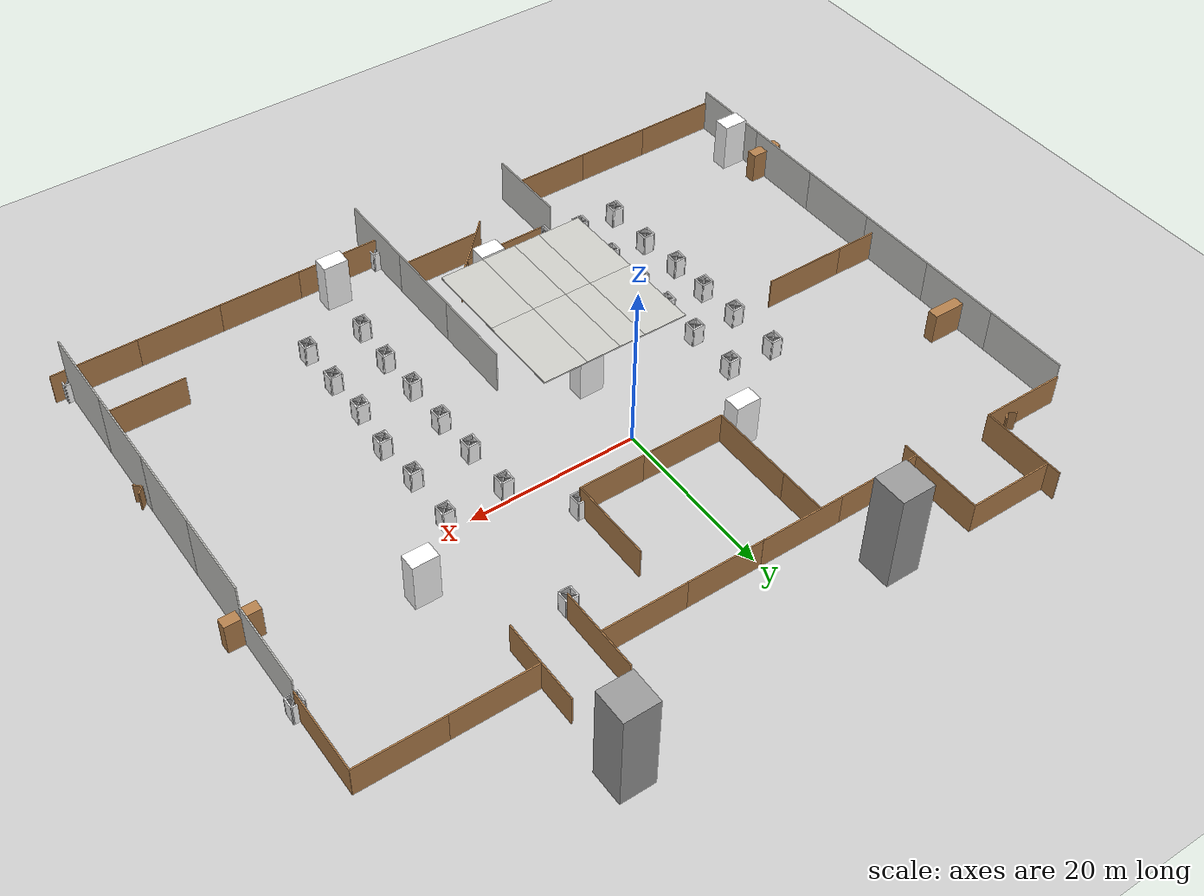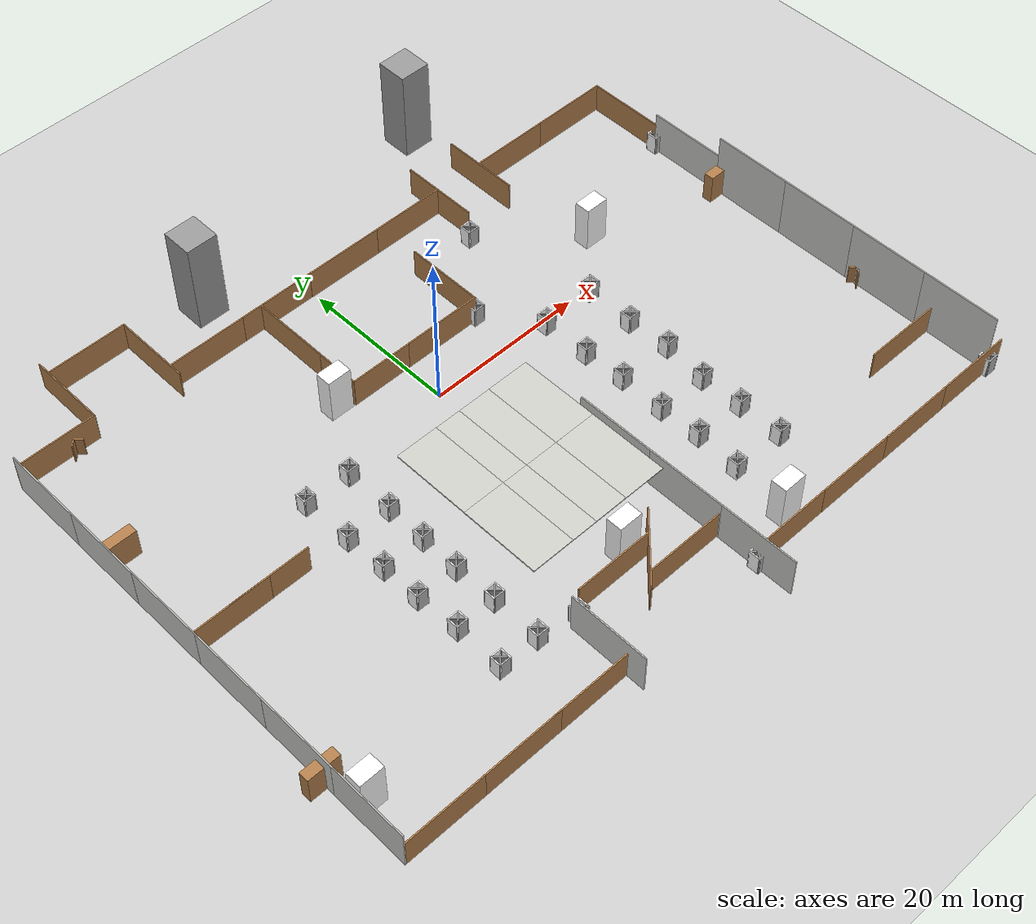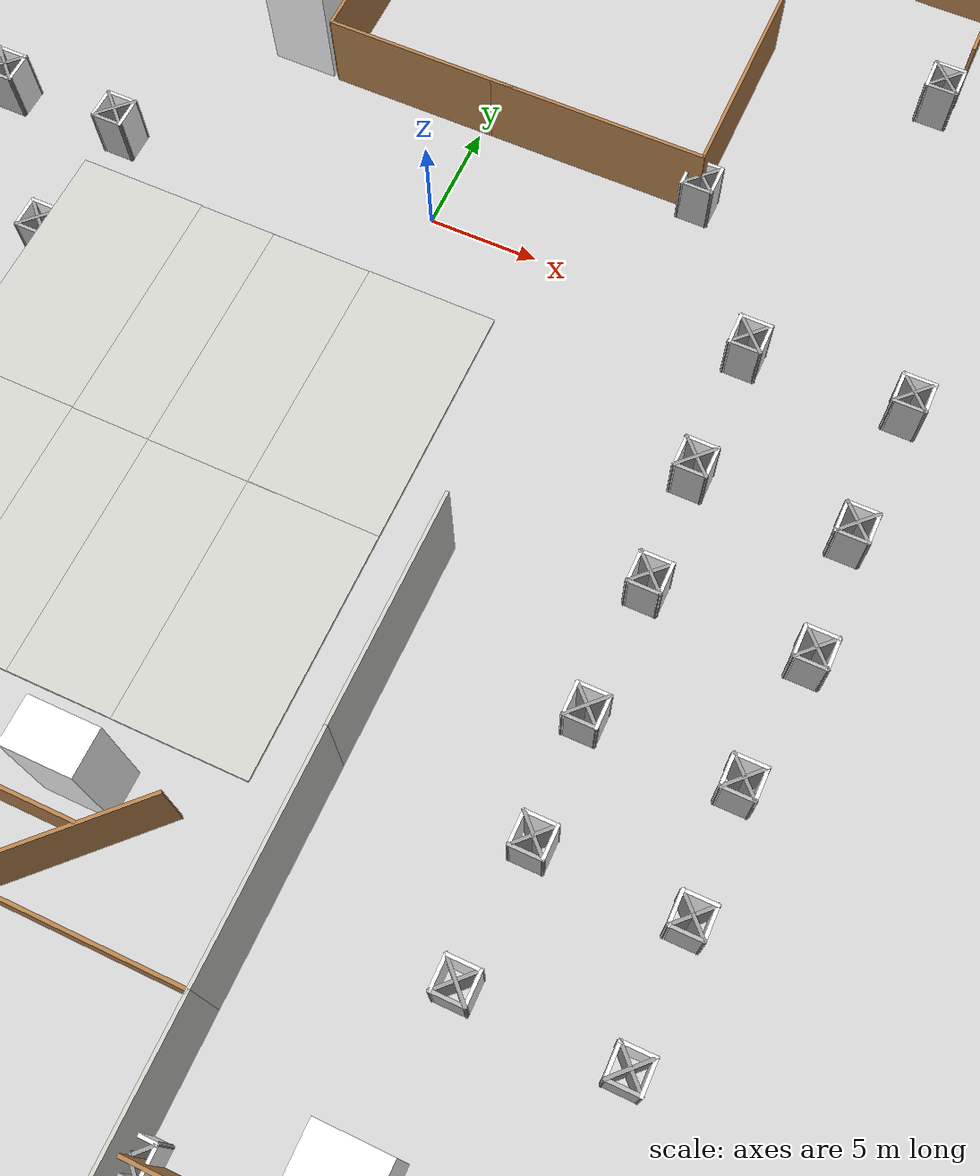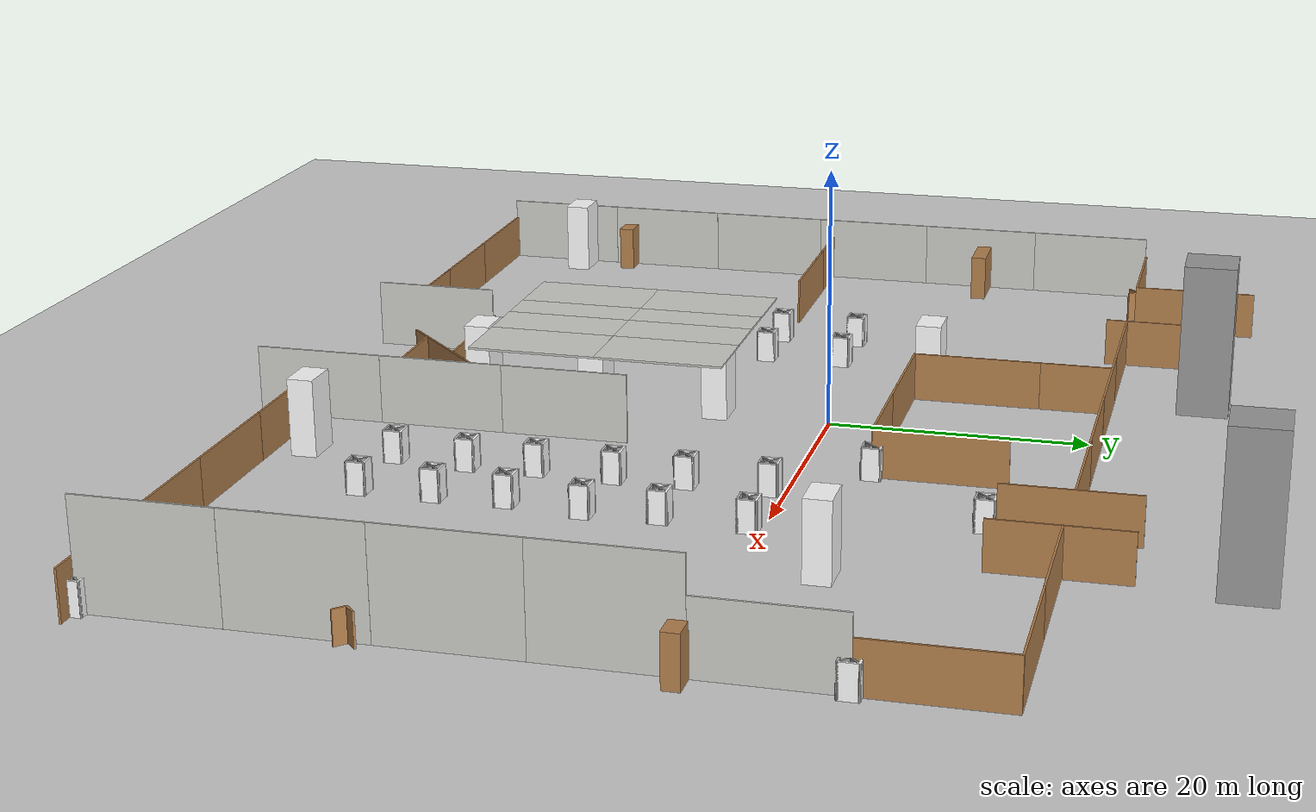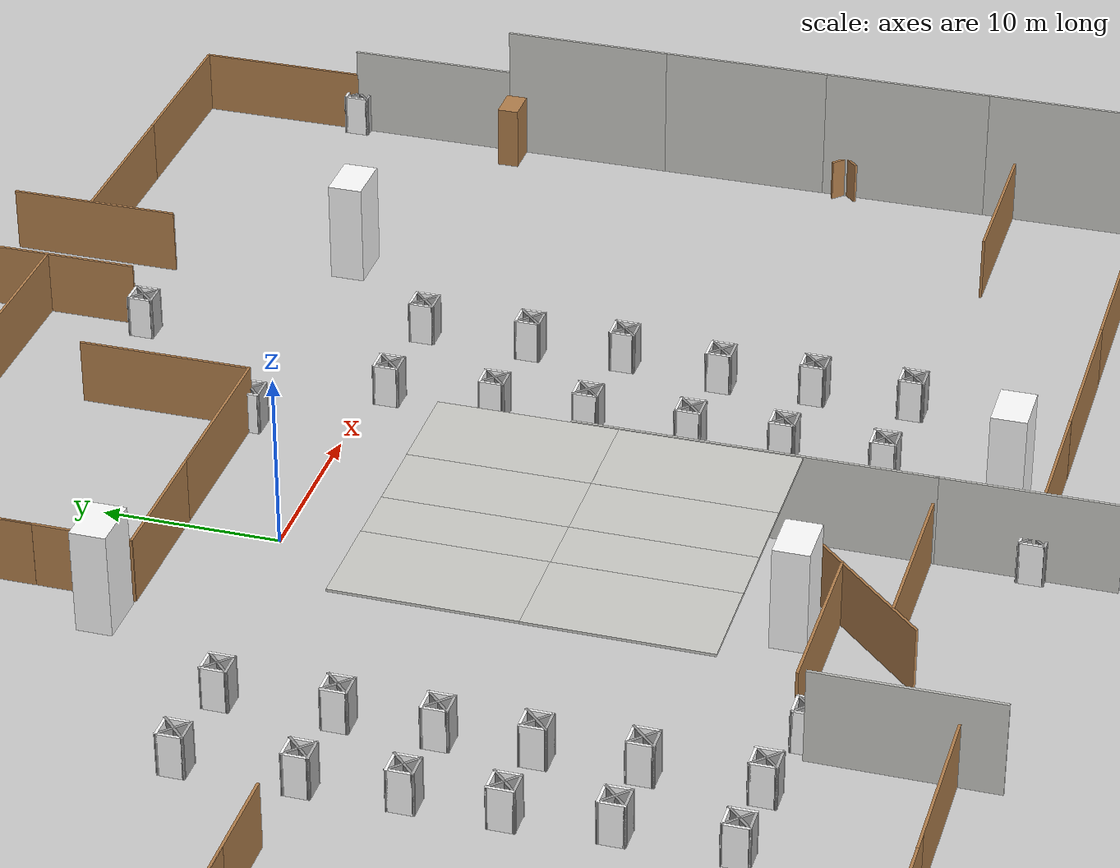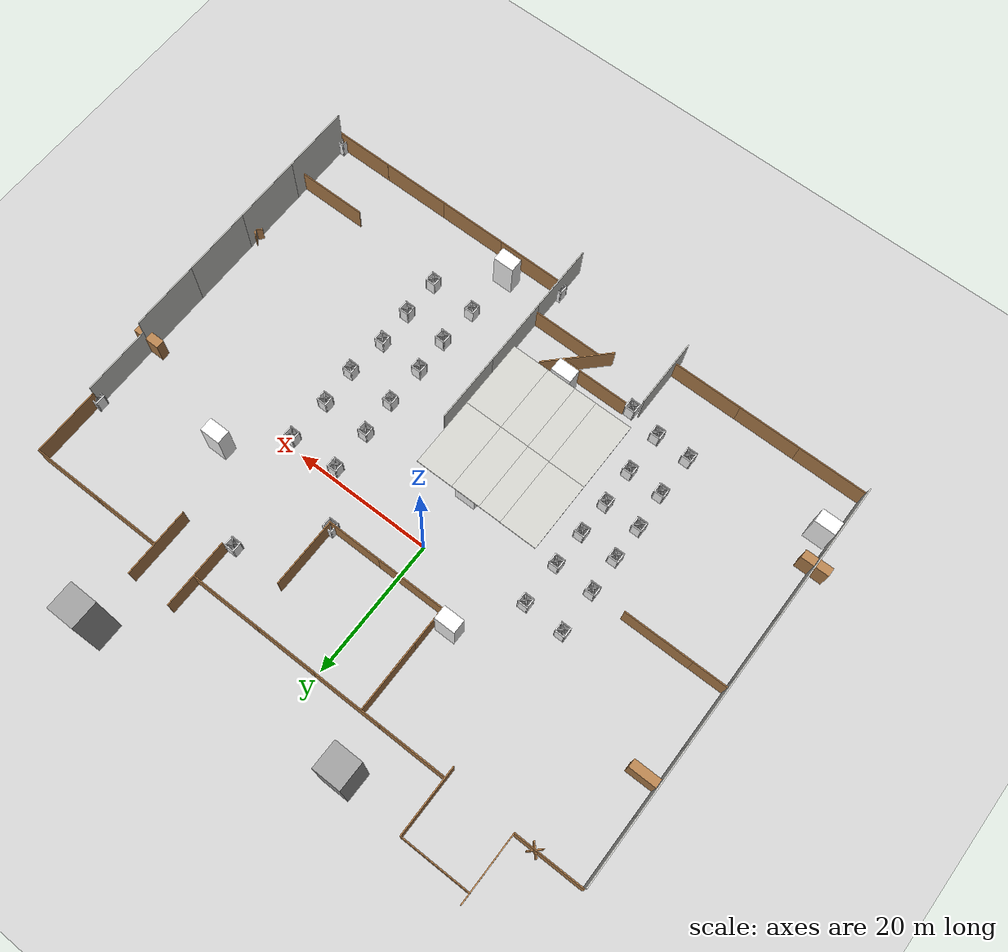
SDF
<sdf version="1.7">
 <world name="default">
  <light name="sun" type="directional">
   <pose>0 0 10 0 -0 0</pose>
   <diffuse>0.8 0.8 0.8 1</diffuse>
   <specular>0.2 0.2 0.2 1</specular>
   <attenuation>
    <range>1000</range>
    <constant>0.9</constant>
    <linear>0.01</linear>
    <quadratic>0.001</quadratic>
   </attenuation>
   <direction>-0.5 0.1 -0.9</direction>
   <spot><inner_angle>0</inner_angle><outer_angle>0</outer_angle><falloff>0</falloff></spot>
  </light>
  <model name="ground_plane">
   <static>1</static>
   <link name="link">
    <collision name="collision">
     <geometry><plane><normal>0 0 1</normal><size>100 100</size></plane></geometry>
     <surface>
      <contact><collide_bitmask>65535</collide_bitmask></contact>
      <friction><ode><mu>100</mu><mu2>50</mu2></ode></friction>
     </surface>
    </collision>
    <visual name="visual">
     <cast_shadows>0</cast_shadows>
     <geometry><plane><normal>0 0 1</normal><size>100 100</size></plane></geometry>
     <material>
      <script><uri>file://media/materials/scripts/gazebo.material</uri><name>Gazebo/Grey</name></script>
     </material>
    </visual>
   </link>
  </model>
  <gravity>0 0 -9.8</gravity>
  <magnetic_field>6e-06 2.3e-05 -4.2e-05</magnetic_field>
  <atmosphere type="adiabatic"/>
  <physics type="ode">
   <max_step_size>0.001</max_step_size>
   <real_time_factor>1</real_time_factor>
   <real_time_update_rate>1000</real_time_update_rate>
  </physics>
  <scene><ambient>0.4 0.4 0.4 1</ambient><background>0.7 0.7 0.7 1</background><shadows>1</shadows></scene>
  <spherical_coordinates>
   <surface_model>EARTH_WGS84</surface_model>
   <latitude_deg>0</latitude_deg>
   <longitude_deg>0</longitude_deg>
   <elevation>0</elevation>
   <heading_deg>0</heading_deg>
  </spherical_coordinates>
  <model name="Untitled_clone">
   <link name="Wall_0">
    <pose>-0.8775 -4.2975 0 0 -0 0</pose>
    <inertial>
     <mass>1</mass>
     <inertia><ixx>1</ixx><ixy>0</ixy><ixz>0</ixz><iyy>1</iyy><iyz>0</iyz><izz>1</izz></inertia>
    </inertial>
    <visual name="Wall_0_Visual">
     <pose>0 0 1.9 0 -0 0</pose>
     <geometry><box><size>10 0.15 3.8</size></box></geometry>
     <material>
      <script><uri>file://media/materials/scripts/gazebo.material</uri><name>Gazebo/Wood</name></script>
      <ambient>1 1 1 1</ambient>
      <shader type="pixel"><normal_map>__default__</normal_map></shader>
      <diffuse>1 1 1 1</diffuse>
      <specular>0.2 0.2 0.2 1</specular>
      <emissive>0 0 0 1</emissive>
     </material>
     <meta><layer>0</layer></meta>
    </visual>
    <collision name="Wall_0_Collision">
     <pose>0 0 1.9 0 -0 0</pose>
     <geometry><box><size>10 0.15 3.8</size></box></geometry>
     <surface>
      <friction>
       <ode><mu>1</mu><mu2>1</mu2><fdir1>0 0 0</fdir1><slip1>0</slip1><slip2>0</slip2></ode>
       <torsional>
        <coefficient>1</coefficient>
        <patch_radius>0</patch_radius>
        <surface_radius>0</surface_radius>
        <use_patch_radius>1</use_patch_radius>
        <ode><slip>0</slip></ode>
       </torsional>
      </friction>
      <bounce><restitution_coefficient>0</restitution_coefficient><threshold>1e+06</threshold></bounce>
      <contact>
       <collide_without_contact>0</collide_without_contact>
       <collide_without_contact_bitmask>1</collide_without_contact_bitmask>
       <collide_bitmask>1</collide_bitmask>
       <ode>
        <soft_cfm>0</soft_cfm>
        <soft_erp>0.2</soft_erp>
        <kp>1e+13</kp>
        <kd>1</kd>
        <max_vel>0.01</max_vel>
        <min_depth>0</min_depth>
       </ode>
       <bullet>
        <split_impulse>1</split_impulse>
        <split_impulse_penetration_threshold>-0.01</split_impulse_penetration_threshold>
        <soft_cfm>0</soft_cfm>
        <soft_erp>0.2</soft_erp>
        <kp>1e+13</kp>
        <kd>1</kd>
       </bullet>
      </contact>
     </surface>
    </collision>
   </link>
   <static>1</static>
   <pose>-4.14648 25.1875 0 0 -0 0</pose>
  </model>
  <model name="Untitled_clone_clone">
   <link name="Wall_0">
    <pose>-0.8775 -4.2975 0 0 -0 0</pose>
    <inertial>
     <mass>1</mass>
     <inertia><ixx>1</ixx><ixy>0</ixy><ixz>0</ixz><iyy>1</iyy><iyz>0</iyz><izz>1</izz></inertia>
    </inertial>
    <visual name="Wall_0_Visual">
     <pose>0 0 1.9 0 -0 0</pose>
     <geometry><box><size>10 0.15 3.8</size></box></geometry>
     <material>
      <script><uri>file://media/materials/scripts/gazebo.material</uri><name>Gazebo/Wood</name></script>
      <ambient>1 1 1 1</ambient>
      <shader type="pixel"><normal_map>__default__</normal_map></shader>
      <diffuse>1 1 1 1</diffuse>
      <specular>0.2 0.2 0.2 1</specular>
      <emissive>0 0 0 1</emissive>
     </material>
     <meta><layer>0</layer></meta>
    </visual>
    <collision name="Wall_0_Collision">
     <pose>0 0 1.9 0 -0 0</pose>
     <geometry><box><size>10 0.15 3.8</size></box></geometry>
     <surface>
      <friction>
       <ode><mu>1</mu><mu2>1</mu2><fdir1>0 0 0</fdir1><slip1>0</slip1><slip2>0</slip2></ode>
       <torsional>
        <coefficient>1</coefficient>
        <patch_radius>0</patch_radius>
        <surface_radius>0</surface_radius>
        <use_patch_radius>1</use_patch_radius>
        <ode><slip>0</slip></ode>
       </torsional>
      </friction>
      <bounce><restitution_coefficient>0</restitution_coefficient><threshold>1e+06</threshold></bounce>
      <contact>
       <collide_without_contact>0</collide_without_contact>
       <collide_without_contact_bitmask>1</collide_without_contact_bitmask>
       <collide_bitmask>1</collide_bitmask>
       <ode>
        <soft_cfm>0</soft_cfm>
        <soft_erp>0.2</soft_erp>
        <kp>1e+13</kp>
        <kd>1</kd>
        <max_vel>0.01</max_vel>
        <min_depth>0</min_depth>
       </ode>
       <bullet>
        <split_impulse>1</split_impulse>
        <split_impulse_penetration_threshold>-0.01</split_impulse_penetration_threshold>
        <soft_cfm>0</soft_cfm>
        <soft_erp>0.2</soft_erp>
        <kp>1e+13</kp>
        <kd>1</kd>
       </bullet>
      </contact>
     </surface>
    </collision>
   </link>
   <static>1</static>
   <pose>-14.1014 25.1819 0 0 -0 0</pose>
  </model>
  <model name="Untitled_clone_clone_0">
   <link name="Wall_0">
    <pose>-0.8775 -4.2975 0 0 -0 0</pose>
    <inertial>
     <mass>1</mass>
     <inertia><ixx>1</ixx><ixy>0</ixy><ixz>0</ixz><iyy>1</iyy><iyz>0</iyz><izz>1</izz></inertia>
    </inertial>
    <visual name="Wall_0_Visual">
     <pose>0 0 1.9 0 -0 0</pose>
     <geometry><box><size>10 0.15 3.8</size></box></geometry>
     <material>
      <script><uri>file://media/materials/scripts/gazebo.material</uri><name>Gazebo/Wood</name></script>
      <ambient>1 1 1 1</ambient>
      <shader type="pixel"><normal_map>__default__</normal_map></shader>
      <diffuse>1 1 1 1</diffuse>
      <specular>0.2 0.2 0.2 1</specular>
      <emissive>0 0 0 1</emissive>
     </material>
     <meta><layer>0</layer></meta>
    </visual>
    <collision name="Wall_0_Collision">
     <pose>0 0 1.9 0 -0 0</pose>
     <geometry><box><size>10 0.15 3.8</size></box></geometry>
     <surface>
      <friction>
       <ode><mu>1</mu><mu2>1</mu2><fdir1>0 0 0</fdir1><slip1>0</slip1><slip2>0</slip2></ode>
       <torsional>
        <coefficient>1</coefficient>
        <patch_radius>0</patch_radius>
        <surface_radius>0</surface_radius>
        <use_patch_radius>1</use_patch_radius>
        <ode><slip>0</slip></ode>
       </torsional>
      </friction>
      <bounce><restitution_coefficient>0</restitution_coefficient><threshold>1e+06</threshold></bounce>
      <contact>
       <collide_without_contact>0</collide_without_contact>
       <collide_without_contact_bitmask>1</collide_without_contact_bitmask>
       <collide_bitmask>1</collide_bitmask>
       <ode>
        <soft_cfm>0</soft_cfm>
        <soft_erp>0.2</soft_erp>
        <kp>1e+13</kp>
        <kd>1</kd>
        <max_vel>0.01</max_vel>
        <min_depth>0</min_depth>
       </ode>
       <bullet>
        <split_impulse>1</split_impulse>
        <split_impulse_penetration_threshold>-0.01</split_impulse_penetration_threshold>
        <soft_cfm>0</soft_cfm>
        <soft_erp>0.2</soft_erp>
        <kp>1e+13</kp>
        <kd>1</kd>
       </bullet>
      </contact>
     </surface>
    </collision>
   </link>
   <static>1</static>
   <pose>-24.2081 25.1073 0 0 -0 1.5708</pose>
  </model>
  <model name="Untitled_clone_clone_1">
   <link name="Wall_0">
    <pose>-0.8775 -4.2975 0 0 -0 0</pose>
    <inertial>
     <mass>1</mass>
     <inertia><ixx>1</ixx><ixy>0</ixy><ixz>0</ixz><iyy>1</iyy><iyz>0</iyz><izz>1</izz></inertia>
    </inertial>
    <visual name="Wall_0_Visual">
     <pose>0 0 1.9 0 -0 0</pose>
     <geometry><box><size>10 0.15 3.8</size></box></geometry>
     <material>
      <script><uri>file://media/materials/scripts/gazebo.material</uri><name>Gazebo/Wood</name></script>
      <ambient>1 1 1 1</ambient>
      <shader type="pixel"><normal_map>__default__</normal_map></shader>
      <diffuse>1 1 1 1</diffuse>
      <specular>0.2 0.2 0.2 1</specular>
      <emissive>0 0 0 1</emissive>
     </material>
     <meta><layer>0</layer></meta>
    </visual>
    <collision name="Wall_0_Collision">
     <pose>0 0 1.9 0 -0 0</pose>
     <geometry><box><size>10 0.15 3.8</size></box></geometry>
     <surface>
      <friction>
       <ode><mu>1</mu><mu2>1</mu2><fdir1>0 0 0</fdir1><slip1>0</slip1><slip2>0</slip2></ode>
       <torsional>
        <coefficient>1</coefficient>
        <patch_radius>0</patch_radius>
        <surface_radius>0</surface_radius>
        <use_patch_radius>1</use_patch_radius>
        <ode><slip>0</slip></ode>
       </torsional>
      </friction>
      <bounce><restitution_coefficient>0</restitution_coefficient><threshold>1e+06</threshold></bounce>
      <contact>
       <collide_without_contact>0</collide_without_contact>
       <collide_without_contact_bitmask>1</collide_without_contact_bitmask>
       <collide_bitmask>1</collide_bitmask>
       <ode>
        <soft_cfm>0</soft_cfm>
        <soft_erp>0.2</soft_erp>
        <kp>1e+13</kp>
        <kd>1</kd>
        <max_vel>0.01</max_vel>
        <min_depth>0</min_depth>
       </ode>
       <bullet>
        <split_impulse>1</split_impulse>
        <split_impulse_penetration_threshold>-0.01</split_impulse_penetration_threshold>
        <soft_cfm>0</soft_cfm>
        <soft_erp>0.2</soft_erp>
        <kp>1e+13</kp>
        <kd>1</kd>
       </bullet>
      </contact>
     </surface>
    </collision>
   </link>
   <static>1</static>
   <pose>-34.0103 25.18 0 0 -0 0</pose>
  </model>
  <model name="Untitled_clone_clone_0_clone_clone">
   <link name="Wall_0">
    <pose>-0.8775 -4.2975 0 0 -0 0</pose>
    <inertial>
     <mass>1</mass>
     <inertia><ixx>1</ixx><ixy>0</ixy><ixz>0</ixz><iyy>1</iyy><iyz>0</iyz><izz>1</izz></inertia>
    </inertial>
    <visual name="Wall_0_Visual">
     <pose>0 0 1.9 0 -0 0</pose>
     <geometry><box><size>10 0.15 3.8</size></box></geometry>
     <material>
      <script><uri>file://media/materials/scripts/gazebo.material</uri><name>Gazebo/Wood</name></script>
      <ambient>1 1 1 1</ambient>
      <shader type="pixel"><normal_map>__default__</normal_map></shader>
      <diffuse>1 1 1 1</diffuse>
      <specular>0.2 0.2 0.2 1</specular>
      <emissive>0 0 0 1</emissive>
     </material>
     <meta><layer>0</layer></meta>
    </visual>
    <collision name="Wall_0_Collision">
     <pose>0 0 1.9 0 -0 0</pose>
     <geometry><box><size>10 0.15 3.8</size></box></geometry>
     <surface>
      <friction>
       <ode><mu>1</mu><mu2>1</mu2><fdir1>0 0 0</fdir1><slip1>0</slip1><slip2>0</slip2></ode>
       <torsional>
        <coefficient>1</coefficient>
        <patch_radius>0</patch_radius>
        <surface_radius>0</surface_radius>
        <use_patch_radius>1</use_patch_radius>
        <ode><slip>0</slip></ode>
       </torsional>
      </friction>
      <bounce><restitution_coefficient>0</restitution_coefficient><threshold>1e+06</threshold></bounce>
      <contact>
       <collide_without_contact>0</collide_without_contact>
       <collide_without_contact_bitmask>1</collide_without_contact_bitmask>
       <collide_bitmask>1</collide_bitmask>
       <ode>
        <soft_cfm>0</soft_cfm>
        <soft_erp>0.2</soft_erp>
        <kp>1e+13</kp>
        <kd>1</kd>
        <max_vel>0.01</max_vel>
        <min_depth>0</min_depth>
       </ode>
       <bullet>
        <split_impulse>1</split_impulse>
        <split_impulse_penetration_threshold>-0.01</split_impulse_penetration_threshold>
        <soft_cfm>0</soft_cfm>
        <soft_erp>0.2</soft_erp>
        <kp>1e+13</kp>
        <kd>1</kd>
       </bullet>
      </contact>
     </surface>
    </collision>
   </link>
   <static>1</static>
   <pose>-24.0116 33.454 0 0 -0 0</pose>
  </model>
  <model name="Untitled_clone_clone_0_clone_0">
   <link name="Wall_0">
    <pose>-0.8775 -4.2975 0 0 -0 0</pose>
    <inertial>
     <mass>1</mass>
     <inertia><ixx>1</ixx><ixy>0</ixy><ixz>0</ixz><iyy>1</iyy><iyz>0</iyz><izz>1</izz></inertia>
    </inertial>
    <visual name="Wall_0_Visual">
     <pose>0 0 1.9 0 -0 0</pose>
     <geometry><box><size>10 0.15 3.8</size></box></geometry>
     <material>
      <script><uri>file://media/materials/scripts/gazebo.material</uri><name>Gazebo/Wood</name></script>
      <ambient>1 1 1 1</ambient>
      <shader type="pixel"><normal_map>__default__</normal_map></shader>
      <diffuse>1 1 1 1</diffuse>
      <specular>0.2 0.2 0.2 1</specular>
      <emissive>0 0 0 1</emissive>
     </material>
     <meta><layer>0</layer></meta>
    </visual>
    <collision name="Wall_0_Collision">
     <pose>0 0 1.9 0 -0 0</pose>
     <geometry><box><size>10 0.15 3.8</size></box></geometry>
     <surface>
      <friction>
       <ode><mu>1</mu><mu2>1</mu2><fdir1>0 0 0</fdir1><slip1>0</slip1><slip2>0</slip2></ode>
       <torsional>
        <coefficient>1</coefficient>
        <patch_radius>0</patch_radius>
        <surface_radius>0</surface_radius>
        <use_patch_radius>1</use_patch_radius>
        <ode><slip>0</slip></ode>
       </torsional>
      </friction>
      <bounce><restitution_coefficient>0</restitution_coefficient><threshold>1e+06</threshold></bounce>
      <contact>
       <collide_without_contact>0</collide_without_contact>
       <collide_without_contact_bitmask>1</collide_without_contact_bitmask>
       <collide_bitmask>1</collide_bitmask>
       <ode>
        <soft_cfm>0</soft_cfm>
        <soft_erp>0.2</soft_erp>
        <kp>1e+13</kp>
        <kd>1</kd>
        <max_vel>0.01</max_vel>
        <min_depth>0</min_depth>
       </ode>
       <bullet>
        <split_impulse>1</split_impulse>
        <split_impulse_penetration_threshold>-0.01</split_impulse_penetration_threshold>
        <soft_cfm>0</soft_cfm>
        <soft_erp>0.2</soft_erp>
        <kp>1e+13</kp>
        <kd>1</kd>
       </bullet>
      </contact>
     </surface>
    </collision>
   </link>
   <static>1</static>
   <pose>-34.2183 26.6866 0 0 -0 1.5708</pose>
  </model>
  <model name="Untitled_0_clone">
   <link name="Wall_2">
    <pose>-0.3075 -1.8625 0 0 0 -1.5708</pose>
    <inertial>
     <mass>1</mass>
     <inertia><ixx>1</ixx><ixy>0</ixy><ixz>0</ixz><iyy>1</iyy><iyz>0</iyz><izz>1</izz></inertia>
    </inertial>
    <visual name="Wall_2_Visual">
     <pose>0 0 2.7 0 -0 0</pose>
     <geometry><box><size>10 0.15 5.4</size></box></geometry>
     <material>
      <script><uri>file://media/materials/scripts/gazebo.material</uri><name>Gazebo/CeilingTiled</name></script>
      <ambient>1 1 1 1</ambient>
      <shader type="pixel"><normal_map>__default__</normal_map></shader>
      <diffuse>1 1 1 1</diffuse>
      <specular>0 0 0 1</specular>
      <emissive>0 0 0 1</emissive>
     </material>
     <meta><layer>0</layer></meta>
    </visual>
    <collision name="Wall_2_Collision">
     <pose>0 0 2.7 0 -0 0</pose>
     <geometry><box><size>10 0.15 5.4</size></box></geometry>
     <surface>
      <friction>
       <ode><mu>1</mu><mu2>1</mu2><fdir1>0 0 0</fdir1><slip1>0</slip1><slip2>0</slip2></ode>
       <torsional>
        <coefficient>1</coefficient>
        <patch_radius>0</patch_radius>
        <surface_radius>0</surface_radius>
        <use_patch_radius>1</use_patch_radius>
        <ode><slip>0</slip></ode>
       </torsional>
      </friction>
      <bounce><restitution_coefficient>0</restitution_coefficient><threshold>1e+06</threshold></bounce>
      <contact>
       <collide_without_contact>0</collide_without_contact>
       <collide_without_contact_bitmask>1</collide_without_contact_bitmask>
       <collide_bitmask>1</collide_bitmask>
       <ode>
        <soft_cfm>0</soft_cfm>
        <soft_erp>0.2</soft_erp>
        <kp>1e+13</kp>
        <kd>1</kd>
        <max_vel>0.01</max_vel>
        <min_depth>0</min_depth>
       </ode>
       <bullet>
        <split_impulse>1</split_impulse>
        <split_impulse_penetration_threshold>-0.01</split_impulse_penetration_threshold>
        <soft_cfm>0</soft_cfm>
        <soft_erp>0.2</soft_erp>
        <kp>1e+13</kp>
        <kd>1</kd>
       </bullet>
      </contact>
     </surface>
    </collision>
   </link>
   <static>1</static>
   <pose>-39.5223 17.6877 0 0 -0 0</pose>
  </model>
  <model name="Untitled_0_clone_0">
   <link name="Wall_2">
    <pose>-0.3075 -1.8625 0 0 0 -1.5708</pose>
    <inertial>
     <mass>1</mass>
     <inertia><ixx>1</ixx><ixy>0</ixy><ixz>0</ixz><iyy>1</iyy><iyz>0</iyz><izz>1</izz></inertia>
    </inertial>
    <visual name="Wall_2_Visual">
     <pose>0 0 2.7 0 -0 0</pose>
     <geometry><box><size>10 0.15 5.4</size></box></geometry>
     <material>
      <script><uri>file://media/materials/scripts/gazebo.material</uri><name>Gazebo/CeilingTiled</name></script>
      <ambient>1 1 1 1</ambient>
      <shader type="pixel"><normal_map>__default__</normal_map></shader>
      <diffuse>1 1 1 1</diffuse>
      <specular>0 0 0 1</specular>
      <emissive>0 0 0 1</emissive>
     </material>
     <meta><layer>0</layer></meta>
    </visual>
    <collision name="Wall_2_Collision">
     <pose>0 0 2.7 0 -0 0</pose>
     <geometry><box><size>10 0.15 5.4</size></box></geometry>
     <surface>
      <friction>
       <ode><mu>1</mu><mu2>1</mu2><fdir1>0 0 0</fdir1><slip1>0</slip1><slip2>0</slip2></ode>
       <torsional>
        <coefficient>1</coefficient>
        <patch_radius>0</patch_radius>
        <surface_radius>0</surface_radius>
        <use_patch_radius>1</use_patch_radius>
        <ode><slip>0</slip></ode>
       </torsional>
      </friction>
      <bounce><restitution_coefficient>0</restitution_coefficient><threshold>1e+06</threshold></bounce>
      <contact>
       <collide_without_contact>0</collide_without_contact>
       <collide_without_contact_bitmask>1</collide_without_contact_bitmask>
       <collide_bitmask>1</collide_bitmask>
       <ode>
        <soft_cfm>0</soft_cfm>
        <soft_erp>0.2</soft_erp>
        <kp>1e+13</kp>
        <kd>1</kd>
        <max_vel>0.01</max_vel>
        <min_depth>0</min_depth>
       </ode>
       <bullet>
        <split_impulse>1</split_impulse>
        <split_impulse_penetration_threshold>-0.01</split_impulse_penetration_threshold>
        <soft_cfm>0</soft_cfm>
        <soft_erp>0.2</soft_erp>
        <kp>1e+13</kp>
        <kd>1</kd>
       </bullet>
      </contact>
     </surface>
    </collision>
   </link>
   <static>1</static>
   <pose>-39.5231 7.69922 0 0 -0 0</pose>
  </model>
  <model name="Untitled_0_clone_1">
   <link name="Wall_2">
    <pose>-0.3075 -1.8625 0 0 0 -1.5708</pose>
    <inertial>
     <mass>1</mass>
     <inertia><ixx>1</ixx><ixy>0</ixy><ixz>0</ixz><iyy>1</iyy><iyz>0</iyz><izz>1</izz></inertia>
    </inertial>
    <visual name="Wall_2_Visual">
     <pose>0 0 2.7 0 -0 0</pose>
     <geometry><box><size>10 0.15 5.4</size></box></geometry>
     <material>
      <script><uri>file://media/materials/scripts/gazebo.material</uri><name>Gazebo/CeilingTiled</name></script>
      <ambient>1 1 1 1</ambient>
      <shader type="pixel"><normal_map>__default__</normal_map></shader>
      <diffuse>1 1 1 1</diffuse>
      <specular>0 0 0 1</specular>
      <emissive>0 0 0 1</emissive>
     </material>
     <meta><layer>0</layer></meta>
    </visual>
    <collision name="Wall_2_Collision">
     <pose>0 0 2.7 0 -0 0</pose>
     <geometry><box><size>10 0.15 5.4</size></box></geometry>
     <surface>
      <friction>
       <ode><mu>1</mu><mu2>1</mu2><fdir1>0 0 0</fdir1><slip1>0</slip1><slip2>0</slip2></ode>
       <torsional>
        <coefficient>1</coefficient>
        <patch_radius>0</patch_radius>
        <surface_radius>0</surface_radius>
        <use_patch_radius>1</use_patch_radius>
        <ode><slip>0</slip></ode>
       </torsional>
      </friction>
      <bounce><restitution_coefficient>0</restitution_coefficient><threshold>1e+06</threshold></bounce>
      <contact>
       <collide_without_contact>0</collide_without_contact>
       <collide_without_contact_bitmask>1</collide_without_contact_bitmask>
       <collide_bitmask>1</collide_bitmask>
       <ode>
        <soft_cfm>0</soft_cfm>
        <soft_erp>0.2</soft_erp>
        <kp>1e+13</kp>
        <kd>1</kd>
        <max_vel>0.01</max_vel>
        <min_depth>0</min_depth>
       </ode>
       <bullet>
        <split_impulse>1</split_impulse>
        <split_impulse_penetration_threshold>-0.01</split_impulse_penetration_threshold>
        <soft_cfm>0</soft_cfm>
        <soft_erp>0.2</soft_erp>
        <kp>1e+13</kp>
        <kd>1</kd>
       </bullet>
      </contact>
     </surface>
    </collision>
   </link>
   <static>1</static>
   <pose>-39.5188 -2.27477 0 0 -0 0</pose>
  </model>
  <model name="Untitled_0_clone_2">
   <link name="Wall_2">
    <pose>-0.3075 -1.8625 0 0 0 -1.5708</pose>
    <inertial>
     <mass>1</mass>
     <inertia><ixx>1</ixx><ixy>0</ixy><ixz>0</ixz><iyy>1</iyy><iyz>0</iyz><izz>1</izz></inertia>
    </inertial>
    <visual name="Wall_2_Visual">
     <pose>0 0 2.7 0 -0 0</pose>
     <geometry><box><size>10 0.15 5.4</size></box></geometry>
     <material>
      <script><uri>file://media/materials/scripts/gazebo.material</uri><name>Gazebo/CeilingTiled</name></script>
      <ambient>1 1 1 1</ambient>
      <shader type="pixel"><normal_map>__default__</normal_map></shader>
      <diffuse>1 1 1 1</diffuse>
      <specular>0 0 0 1</specular>
      <emissive>0 0 0 1</emissive>
     </material>
     <meta><layer>0</layer></meta>
    </visual>
    <collision name="Wall_2_Collision">
     <pose>0 0 2.7 0 -0 0</pose>
     <geometry><box><size>10 0.15 5.4</size></box></geometry>
     <surface>
      <friction>
       <ode><mu>1</mu><mu2>1</mu2><fdir1>0 0 0</fdir1><slip1>0</slip1><slip2>0</slip2></ode>
       <torsional>
        <coefficient>1</coefficient>
        <patch_radius>0</patch_radius>
        <surface_radius>0</surface_radius>
        <use_patch_radius>1</use_patch_radius>
        <ode><slip>0</slip></ode>
       </torsional>
      </friction>
      <bounce><restitution_coefficient>0</restitution_coefficient><threshold>1e+06</threshold></bounce>
      <contact>
       <collide_without_contact>0</collide_without_contact>
       <collide_without_contact_bitmask>1</collide_without_contact_bitmask>
       <collide_bitmask>1</collide_bitmask>
       <ode>
        <soft_cfm>0</soft_cfm>
        <soft_erp>0.2</soft_erp>
        <kp>1e+13</kp>
        <kd>1</kd>
        <max_vel>0.01</max_vel>
        <min_depth>0</min_depth>
       </ode>
       <bullet>
        <split_impulse>1</split_impulse>
        <split_impulse_penetration_threshold>-0.01</split_impulse_penetration_threshold>
        <soft_cfm>0</soft_cfm>
        <soft_erp>0.2</soft_erp>
        <kp>1e+13</kp>
        <kd>1</kd>
       </bullet>
      </contact>
     </surface>
    </collision>
   </link>
   <static>1</static>
   <pose>-39.5182 -12.2186 0 0 -0 0</pose>
  </model>
  <model name="Untitled_0_clone_3">
   <link name="Wall_2">
    <pose>-0.3075 -1.8625 0 0 0 -1.5708</pose>
    <inertial>
     <mass>1</mass>
     <inertia><ixx>1</ixx><ixy>0</ixy><ixz>0</ixz><iyy>1</iyy><iyz>0</iyz><izz>1</izz></inertia>
    </inertial>
    <visual name="Wall_2_Visual">
     <pose>0 0 2.7 0 -0 0</pose>
     <geometry><box><size>10 0.15 5.4</size></box></geometry>
     <material>
      <script><uri>file://media/materials/scripts/gazebo.material</uri><name>Gazebo/CeilingTiled</name></script>
      <ambient>1 1 1 1</ambient>
      <shader type="pixel"><normal_map>__default__</normal_map></shader>
      <diffuse>1 1 1 1</diffuse>
      <specular>0 0 0 1</specular>
      <emissive>0 0 0 1</emissive>
     </material>
     <meta><layer>0</layer></meta>
    </visual>
    <collision name="Wall_2_Collision">
     <pose>0 0 2.7 0 -0 0</pose>
     <geometry><box><size>10 0.15 5.4</size></box></geometry>
     <surface>
      <friction>
       <ode><mu>1</mu><mu2>1</mu2><fdir1>0 0 0</fdir1><slip1>0</slip1><slip2>0</slip2></ode>
       <torsional>
        <coefficient>1</coefficient>
        <patch_radius>0</patch_radius>
        <surface_radius>0</surface_radius>
        <use_patch_radius>1</use_patch_radius>
        <ode><slip>0</slip></ode>
       </torsional>
      </friction>
      <bounce><restitution_coefficient>0</restitution_coefficient><threshold>1e+06</threshold></bounce>
      <contact>
       <collide_without_contact>0</collide_without_contact>
       <collide_without_contact_bitmask>1</collide_without_contact_bitmask>
       <collide_bitmask>1</collide_bitmask>
       <ode>
        <soft_cfm>0</soft_cfm>
        <soft_erp>0.2</soft_erp>
        <kp>1e+13</kp>
        <kd>1</kd>
        <max_vel>0.01</max_vel>
        <min_depth>0</min_depth>
       </ode>
       <bullet>
        <split_impulse>1</split_impulse>
        <split_impulse_penetration_threshold>-0.01</split_impulse_penetration_threshold>
        <soft_cfm>0</soft_cfm>
        <soft_erp>0.2</soft_erp>
        <kp>1e+13</kp>
        <kd>1</kd>
       </bullet>
      </contact>
     </surface>
    </collision>
   </link>
   <static>1</static>
   <pose>-39.511 -22.1279 0 0 -0 0</pose>
  </model>
  <model name="Untitled_0_clone_4">
   <link name="Wall_2">
    <pose>-0.3075 -1.8625 0 0 0 -1.5708</pose>
    <inertial>
     <mass>1</mass>
     <inertia><ixx>1</ixx><ixy>0</ixy><ixz>0</ixz><iyy>1</iyy><iyz>0</iyz><izz>1</izz></inertia>
    </inertial>
    <visual name="Wall_2_Visual">
     <pose>0 0 2.7 0 -0 0</pose>
     <geometry><box><size>10 0.15 5.4</size></box></geometry>
     <material>
      <script><uri>file://media/materials/scripts/gazebo.material</uri><name>Gazebo/CeilingTiled</name></script>
      <ambient>1 1 1 1</ambient>
      <shader type="pixel"><normal_map>__default__</normal_map></shader>
      <diffuse>1 1 1 1</diffuse>
      <specular>0 0 0 1</specular>
      <emissive>0 0 0 1</emissive>
     </material>
     <meta><layer>0</layer></meta>
    </visual>
    <collision name="Wall_2_Collision">
     <pose>0 0 2.7 0 -0 0</pose>
     <geometry><box><size>10 0.15 5.4</size></box></geometry>
     <surface>
      <friction>
       <ode><mu>1</mu><mu2>1</mu2><fdir1>0 0 0</fdir1><slip1>0</slip1><slip2>0</slip2></ode>
       <torsional>
        <coefficient>1</coefficient>
        <patch_radius>0</patch_radius>
        <surface_radius>0</surface_radius>
        <use_patch_radius>1</use_patch_radius>
        <ode><slip>0</slip></ode>
       </torsional>
      </friction>
      <bounce><restitution_coefficient>0</restitution_coefficient><threshold>1e+06</threshold></bounce>
      <contact>
       <collide_without_contact>0</collide_without_contact>
       <collide_without_contact_bitmask>1</collide_without_contact_bitmask>
       <collide_bitmask>1</collide_bitmask>
       <ode>
        <soft_cfm>0</soft_cfm>
        <soft_erp>0.2</soft_erp>
        <kp>1e+13</kp>
        <kd>1</kd>
        <max_vel>0.01</max_vel>
        <min_depth>0</min_depth>
       </ode>
       <bullet>
        <split_impulse>1</split_impulse>
        <split_impulse_penetration_threshold>-0.01</split_impulse_penetration_threshold>
        <soft_cfm>0</soft_cfm>
        <soft_erp>0.2</soft_erp>
        <kp>1e+13</kp>
        <kd>1</kd>
       </bullet>
      </contact>
     </surface>
    </collision>
   </link>
   <static>1</static>
   <pose>-39.5068 -31.9659 0 0 -0 0</pose>
  </model>
  <model name="Untitled_clone_clone_1_clone">
   <link name="Wall_0">
    <pose>-0.8775 -4.2975 0 0 -0 0</pose>
    <inertial>
     <mass>1</mass>
     <inertia><ixx>1</ixx><ixy>0</ixy><ixz>0</ixz><iyy>1</iyy><iyz>0</iyz><izz>1</izz></inertia>
    </inertial>
    <visual name="Wall_0_Visual">
     <pose>0 0 1.9 0 -0 0</pose>
     <geometry><box><size>10 0.15 3.8</size></box></geometry>
     <material>
      <script><uri>file://media/materials/scripts/gazebo.material</uri><name>Gazebo/Wood</name></script>
      <ambient>1 1 1 1</ambient>
      <shader type="pixel"><normal_map>__default__</normal_map></shader>
      <diffuse>1 1 1 1</diffuse>
      <specular>0.2 0.2 0.2 1</specular>
      <emissive>0 0 0 1</emissive>
     </material>
     <meta><layer>0</layer></meta>
    </visual>
    <collision name="Wall_0_Collision">
     <pose>0 0 1.9 0 -0 0</pose>
     <geometry><box><size>10 0.15 3.8</size></box></geometry>
     <surface>
      <friction>
       <ode><mu>1</mu><mu2>1</mu2><fdir1>0 0 0</fdir1><slip1>0</slip1><slip2>0</slip2></ode>
       <torsional>
        <coefficient>1</coefficient>
        <patch_radius>0</patch_radius>
        <surface_radius>0</surface_radius>
        <use_patch_radius>1</use_patch_radius>
        <ode><slip>0</slip></ode>
       </torsional>
      </friction>
      <bounce><restitution_coefficient>0</restitution_coefficient><threshold>1e+06</threshold></bounce>
      <contact>
       <collide_without_contact>0</collide_without_contact>
       <collide_without_contact_bitmask>1</collide_without_contact_bitmask>
       <collide_bitmask>1</collide_bitmask>
       <ode>
        <soft_cfm>0</soft_cfm>
        <soft_erp>0.2</soft_erp>
        <kp>1e+13</kp>
        <kd>1</kd>
        <max_vel>0.01</max_vel>
        <min_depth>0</min_depth>
       </ode>
       <bullet>
        <split_impulse>1</split_impulse>
        <split_impulse_penetration_threshold>-0.01</split_impulse_penetration_threshold>
        <soft_cfm>0</soft_cfm>
        <soft_erp>0.2</soft_erp>
        <kp>1e+13</kp>
        <kd>1</kd>
       </bullet>
      </contact>
     </surface>
    </collision>
   </link>
   <static>1</static>
   <pose>-33.9208 -34.4502 0 0 -0 0</pose>
  </model>
  <model name="Untitled_clone_clone_1_clone_0">
   <link name="Wall_0">
    <pose>-0.8775 -4.2975 0 0 -0 0</pose>
    <inertial>
     <mass>1</mass>
     <inertia><ixx>1</ixx><ixy>0</ixy><ixz>0</ixz><iyy>1</iyy><iyz>0</iyz><izz>1</izz></inertia>
    </inertial>
    <visual name="Wall_0_Visual">
     <pose>0 0 1.9 0 -0 0</pose>
     <geometry><box><size>10 0.15 3.8</size></box></geometry>
     <material>
      <script><uri>file://media/materials/scripts/gazebo.material</uri><name>Gazebo/Wood</name></script>
      <ambient>1 1 1 1</ambient>
      <shader type="pixel"><normal_map>__default__</normal_map></shader>
      <diffuse>1 1 1 1</diffuse>
      <specular>0.2 0.2 0.2 1</specular>
      <emissive>0 0 0 1</emissive>
     </material>
     <meta><layer>0</layer></meta>
    </visual>
    <collision name="Wall_0_Collision">
     <pose>0 0 1.9 0 -0 0</pose>
     <geometry><box><size>10 0.15 3.8</size></box></geometry>
     <surface>
      <friction>
       <ode><mu>1</mu><mu2>1</mu2><fdir1>0 0 0</fdir1><slip1>0</slip1><slip2>0</slip2></ode>
       <torsional>
        <coefficient>1</coefficient>
        <patch_radius>0</patch_radius>
        <surface_radius>0</surface_radius>
        <use_patch_radius>1</use_patch_radius>
        <ode><slip>0</slip></ode>
       </torsional>
      </friction>
      <bounce><restitution_coefficient>0</restitution_coefficient><threshold>1e+06</threshold></bounce>
      <contact>
       <collide_without_contact>0</collide_without_contact>
       <collide_without_contact_bitmask>1</collide_without_contact_bitmask>
       <collide_bitmask>1</collide_bitmask>
       <ode>
        <soft_cfm>0</soft_cfm>
        <soft_erp>0.2</soft_erp>
        <kp>1e+13</kp>
        <kd>1</kd>
        <max_vel>0.01</max_vel>
        <min_depth>0</min_depth>
       </ode>
       <bullet>
        <split_impulse>1</split_impulse>
        <split_impulse_penetration_threshold>-0.01</split_impulse_penetration_threshold>
        <soft_cfm>0</soft_cfm>
        <soft_erp>0.2</soft_erp>
        <kp>1e+13</kp>
        <kd>1</kd>
       </bullet>
      </contact>
     </surface>
    </collision>
   </link>
   <static>1</static>
   <pose>-24.0991 -34.448 0 0 -0 0</pose>
  </model>
  <model name="Untitled_clone_clone_1_clone_1">
   <link name="Wall_0">
    <pose>-0.8775 -4.2975 0 0 -0 0</pose>
    <inertial>
     <mass>1</mass>
     <inertia><ixx>1</ixx><ixy>0</ixy><ixz>0</ixz><iyy>1</iyy><iyz>0</iyz><izz>1</izz></inertia>
    </inertial>
    <visual name="Wall_0_Visual">
     <pose>0 0 1.9 0 -0 0</pose>
     <geometry><box><size>10 0.15 3.8</size></box></geometry>
     <material>
      <script><uri>file://media/materials/scripts/gazebo.material</uri><name>Gazebo/Wood</name></script>
      <ambient>1 1 1 1</ambient>
      <shader type="pixel"><normal_map>__default__</normal_map></shader>
      <diffuse>1 1 1 1</diffuse>
      <specular>0.2 0.2 0.2 1</specular>
      <emissive>0 0 0 1</emissive>
     </material>
     <meta><layer>0</layer></meta>
    </visual>
    <collision name="Wall_0_Collision">
     <pose>0 0 1.9 0 -0 0</pose>
     <geometry><box><size>10 0.15 3.8</size></box></geometry>
     <surface>
      <friction>
       <ode><mu>1</mu><mu2>1</mu2><fdir1>0 0 0</fdir1><slip1>0</slip1><slip2>0</slip2></ode>
       <torsional>
        <coefficient>1</coefficient>
        <patch_radius>0</patch_radius>
        <surface_radius>0</surface_radius>
        <use_patch_radius>1</use_patch_radius>
        <ode><slip>0</slip></ode>
       </torsional>
      </friction>
      <bounce><restitution_coefficient>0</restitution_coefficient><threshold>1e+06</threshold></bounce>
      <contact>
       <collide_without_contact>0</collide_without_contact>
       <collide_without_contact_bitmask>1</collide_without_contact_bitmask>
       <collide_bitmask>1</collide_bitmask>
       <ode>
        <soft_cfm>0</soft_cfm>
        <soft_erp>0.2</soft_erp>
        <kp>1e+13</kp>
        <kd>1</kd>
        <max_vel>0.01</max_vel>
        <min_depth>0</min_depth>
       </ode>
       <bullet>
        <split_impulse>1</split_impulse>
        <split_impulse_penetration_threshold>-0.01</split_impulse_penetration_threshold>
        <soft_cfm>0</soft_cfm>
        <soft_erp>0.2</soft_erp>
        <kp>1e+13</kp>
        <kd>1</kd>
       </bullet>
      </contact>
     </surface>
    </collision>
   </link>
   <static>1</static>
   <pose>-15.1014 -34.4435 0 0 -0 0</pose>
  </model>
  <model name="unit_box">
   <link name="link">
    <inertial>
     <mass>1</mass>
     <inertia>
      <ixx>0.166667</ixx>
      <ixy>0</ixy>
      <ixz>0</ixz>
      <iyy>0.166667</iyy>
      <iyz>0</iyz>
      <izz>0.166667</izz>
     </inertia>
    </inertial>
    <visual name="visual">
     <geometry><box><size>4 4 12</size></box></geometry>
     <material>
      <script><name>Gazebo/Grey</name><uri>file://media/materials/scripts/gazebo.material</uri></script>
      <shader type="pixel"><normal_map>__default__</normal_map></shader>
      <ambient>0.3 0.3 0.3 1</ambient>
      <diffuse>0.7 0.7 0.7 1</diffuse>
      <specular>0.01 0.01 0.01 1</specular>
      <emissive>0 0 0 1</emissive>
     </material>
     <pose>0 0 6 0 -0 0</pose>
    </visual>
    <collision name="collision">
     <pose>0 0 6 0 -0 0</pose>
     <geometry><box><size>4 4 12</size></box></geometry>
     <surface>
      <friction>
       <ode><mu>1</mu><mu2>1</mu2><fdir1>0 0 0</fdir1><slip1>0</slip1><slip2>0</slip2></ode>
       <torsional>
        <coefficient>1</coefficient>
        <patch_radius>0</patch_radius>
        <surface_radius>0</surface_radius>
        <use_patch_radius>1</use_patch_radius>
        <ode><slip>0</slip></ode>
       </torsional>
      </friction>
      <bounce><restitution_coefficient>0</restitution_coefficient><threshold>1e+06</threshold></bounce>
      <contact>
       <collide_without_contact>0</collide_without_contact>
       <collide_without_contact_bitmask>1</collide_without_contact_bitmask>
       <collide_bitmask>1</collide_bitmask>
       <ode>
        <soft_cfm>0</soft_cfm>
        <soft_erp>0.2</soft_erp>
        <kp>1e+13</kp>
        <kd>1</kd>
        <max_vel>0.01</max_vel>
        <min_depth>0</min_depth>
       </ode>
       <bullet>
        <split_impulse>1</split_impulse>
        <split_impulse_penetration_threshold>-0.01</split_impulse_penetration_threshold>
        <soft_cfm>0</soft_cfm>
        <soft_erp>0.2</soft_erp>
        <kp>1e+13</kp>
        <kd>1</kd>
       </bullet>
      </contact>
     </surface>
    </collision>
   </link>
   <static>0</static>
   <pose>-10.4039 27.8438 -0 0 -0 0</pose>
  </model>
  <model name="Untitled_clone_clone_0_clone_clone_0">
   <link name="Wall_0">
    <pose>-0.877501 -4.2975 0 0 -0 0</pose>
    <inertial>
     <mass>1</mass>
     <inertia><ixx>1</ixx><ixy>0</ixy><ixz>0</ixz><iyy>1</iyy><iyz>0</iyz><izz>1</izz></inertia>
    </inertial>
    <visual name="Wall_0_Visual">
     <pose>0 0 1.9 0 -0 0</pose>
     <geometry><box><size>4 1.25 3.8</size></box></geometry>
     <material>
      <script><uri>file://media/materials/scripts/gazebo.material</uri><name>Gazebo/Wood</name></script>
      <ambient>1 1 1 1</ambient>
      <shader type="pixel"><normal_map>__default__</normal_map></shader>
      <diffuse>1 1 1 1</diffuse>
      <specular>0.2 0.2 0.2 1</specular>
      <emissive>0 0 0 1</emissive>
     </material>
     <meta><layer>0</layer></meta>
    </visual>
    <collision name="Wall_0_Collision">
     <pose>0 0 1.9 0 -0 0</pose>
     <geometry><box><size>4 1.25 3.8</size></box></geometry>
     <surface>
      <friction>
       <ode><mu>1</mu><mu2>1</mu2><fdir1>0 0 0</fdir1><slip1>0</slip1><slip2>0</slip2></ode>
       <torsional>
        <coefficient>1</coefficient>
        <patch_radius>0</patch_radius>
        <surface_radius>0</surface_radius>
        <use_patch_radius>1</use_patch_radius>
        <ode><slip>0</slip></ode>
       </torsional>
      </friction>
      <bounce><restitution_coefficient>0</restitution_coefficient><threshold>1e+06</threshold></bounce>
      <contact>
       <collide_without_contact>0</collide_without_contact>
       <collide_without_contact_bitmask>1</collide_without_contact_bitmask>
       <collide_bitmask>1</collide_bitmask>
       <ode>
        <soft_cfm>0</soft_cfm>
        <soft_erp>0.2</soft_erp>
        <kp>1e+13</kp>
        <kd>1</kd>
        <max_vel>0.01</max_vel>
        <min_depth>0</min_depth>
       </ode>
       <bullet>
        <split_impulse>1</split_impulse>
        <split_impulse_penetration_threshold>-0.01</split_impulse_penetration_threshold>
        <soft_cfm>0</soft_cfm>
        <soft_erp>0.2</soft_erp>
        <kp>1e+13</kp>
        <kd>1</kd>
       </bullet>
      </contact>
     </surface>
    </collision>
   </link>
   <static>1</static>
   <pose>-36.9891 10.5591 0 0 -0 0</pose>
  </model>
  <model name="Untitled_clone_clone_0_clone_clone_0_clone">
   <link name="Wall_0">
    <pose>-0.877501 -4.2975 0 0 -0 0</pose>
    <inertial>
     <mass>1</mass>
     <inertia><ixx>1</ixx><ixy>0</ixy><ixz>0</ixz><iyy>1</iyy><iyz>0</iyz><izz>1</izz></inertia>
    </inertial>
    <visual name="Wall_0_Visual">
     <pose>0 0 1.9 0 -0 0</pose>
     <geometry><box><size>4 1.25 3.8</size></box></geometry>
     <material>
      <script><uri>file://media/materials/scripts/gazebo.material</uri><name>Gazebo/Wood</name></script>
      <ambient>1 1 1 1</ambient>
      <shader type="pixel"><normal_map>__default__</normal_map></shader>
      <diffuse>1 1 1 1</diffuse>
      <specular>0.2 0.2 0.2 1</specular>
      <emissive>0 0 0 1</emissive>
     </material>
     <meta><layer>0</layer></meta>
    </visual>
    <collision name="Wall_0_Collision">
     <pose>0 0 1.9 0 -0 0</pose>
     <geometry><box><size>4 1.25 3.8</size></box></geometry>
     <surface>
      <friction>
       <ode><mu>1</mu><mu2>1</mu2><fdir1>0 0 0</fdir1><slip1>0</slip1><slip2>0</slip2></ode>
       <torsional>
        <coefficient>1</coefficient>
        <patch_radius>0</patch_radius>
        <surface_radius>0</surface_radius>
        <use_patch_radius>1</use_patch_radius>
        <ode><slip>0</slip></ode>
       </torsional>
      </friction>
      <bounce><restitution_coefficient>0</restitution_coefficient><threshold>1e+06</threshold></bounce>
      <contact>
       <collide_without_contact>0</collide_without_contact>
       <collide_without_contact_bitmask>1</collide_without_contact_bitmask>
       <collide_bitmask>1</collide_bitmask>
       <ode>
        <soft_cfm>0</soft_cfm>
        <soft_erp>0.2</soft_erp>
        <kp>1e+13</kp>
        <kd>1</kd>
        <max_vel>0.01</max_vel>
        <min_depth>0</min_depth>
       </ode>
       <bullet>
        <split_impulse>1</split_impulse>
        <split_impulse_penetration_threshold>-0.01</split_impulse_penetration_threshold>
        <soft_cfm>0</soft_cfm>
        <soft_erp>0.2</soft_erp>
        <kp>1e+13</kp>
        <kd>1</kd>
       </bullet>
      </contact>
     </surface>
    </collision>
   </link>
   <static>1</static>
   <pose>-39.0031 -23.066 0 0 -0 0</pose>
  </model>
  <model name="Untitled_0_clone_5">
   <link name="Wall_2">
    <pose>-0.3075 -1.8625 0 0 0 -1.5708</pose>
    <inertial>
     <mass>1</mass>
     <inertia><ixx>1</ixx><ixy>0</ixy><ixz>0</ixz><iyy>1</iyy><iyz>0</iyz><izz>1</izz></inertia>
    </inertial>
    <visual name="Wall_2_Visual">
     <pose>0 0 2.7 0 -0 0</pose>
     <geometry><box><size>10 0.15 5.4</size></box></geometry>
     <material>
      <script><uri>file://media/materials/scripts/gazebo.material</uri><name>Gazebo/CeilingTiled</name></script>
      <ambient>1 1 1 1</ambient>
      <shader type="pixel"><normal_map>__default__</normal_map></shader>
      <diffuse>1 1 1 1</diffuse>
      <specular>0 0 0 1</specular>
      <emissive>0 0 0 1</emissive>
     </material>
     <meta><layer>0</layer></meta>
    </visual>
    <collision name="Wall_2_Collision">
     <pose>0 0 2.7 0 -0 0</pose>
     <geometry><box><size>10 0.15 5.4</size></box></geometry>
     <surface>
      <friction>
       <ode><mu>1</mu><mu2>1</mu2><fdir1>0 0 0</fdir1><slip1>0</slip1><slip2>0</slip2></ode>
       <torsional>
        <coefficient>1</coefficient>
        <patch_radius>0</patch_radius>
        <surface_radius>0</surface_radius>
        <use_patch_radius>1</use_patch_radius>
        <ode><slip>0</slip></ode>
       </torsional>
      </friction>
      <bounce><restitution_coefficient>0</restitution_coefficient><threshold>1e+06</threshold></bounce>
      <contact>
       <collide_without_contact>0</collide_without_contact>
       <collide_without_contact_bitmask>1</collide_without_contact_bitmask>
       <collide_bitmask>1</collide_bitmask>
       <ode>
        <soft_cfm>0</soft_cfm>
        <soft_erp>0.2</soft_erp>
        <kp>1e+13</kp>
        <kd>1</kd>
        <max_vel>0.01</max_vel>
        <min_depth>0</min_depth>
       </ode>
       <bullet>
        <split_impulse>1</split_impulse>
        <split_impulse_penetration_threshold>-0.01</split_impulse_penetration_threshold>
        <soft_cfm>0</soft_cfm>
        <soft_erp>0.2</soft_erp>
        <kp>1e+13</kp>
        <kd>1</kd>
       </bullet>
      </contact>
     </surface>
    </collision>
   </link>
   <static>1</static>
   <pose>-10.6837 -34.234 0 0 -0 0</pose>
  </model>
  <model name="Untitled_1_clone_clone">
   <link name="Wall_10">
    <pose>4.92197 -3.43197 0 0 -0 1.5708</pose>
    <inertial>
     <mass>1</mass>
     <inertia><ixx>1</ixx><ixy>0</ixy><ixz>0</ixz><iyy>1</iyy><iyz>0</iyz><izz>1</izz></inertia>
    </inertial>
    <visual name="Wall_10_Visual">
     <pose>0 0 1.25 0 -0 0</pose>
     <geometry><box><size>1.5 0.15 2.5</size></box></geometry>
     <material>
      <script><uri>file://media/materials/scripts/gazebo.material</uri><name>Gazebo/CoM</name></script>
      <ambient>1 1 1 1</ambient>
      <shader type="pixel"><normal_map>__default__</normal_map></shader>
      <diffuse>1 1 1 1</diffuse>
      <specular>0 0 0 1</specular>
      <emissive>0 0 0 1</emissive>
     </material>
     <meta><layer>0</layer></meta>
    </visual>
    <collision name="Wall_10_Collision">
     <pose>0 0 1.25 0 -0 0</pose>
     <geometry><box><size>1.5 0.15 2.5</size></box></geometry>
     <surface>
      <friction>
       <ode><mu>1</mu><mu2>1</mu2><fdir1>0 0 0</fdir1><slip1>0</slip1><slip2>0</slip2></ode>
       <torsional>
        <coefficient>1</coefficient>
        <patch_radius>0</patch_radius>
        <surface_radius>0</surface_radius>
        <use_patch_radius>1</use_patch_radius>
        <ode><slip>0</slip></ode>
       </torsional>
      </friction>
      <bounce><restitution_coefficient>0</restitution_coefficient><threshold>1e+06</threshold></bounce>
      <contact>
       <collide_without_contact>0</collide_without_contact>
       <collide_without_contact_bitmask>1</collide_without_contact_bitmask>
       <collide_bitmask>1</collide_bitmask>
       <ode>
        <soft_cfm>0</soft_cfm>
        <soft_erp>0.2</soft_erp>
        <kp>1e+13</kp>
        <kd>1</kd>
        <max_vel>0.01</max_vel>
        <min_depth>0</min_depth>
       </ode>
       <bullet>
        <split_impulse>1</split_impulse>
        <split_impulse_penetration_threshold>-0.01</split_impulse_penetration_threshold>
        <soft_cfm>0</soft_cfm>
        <soft_erp>0.2</soft_erp>
        <kp>1e+13</kp>
        <kd>1</kd>
       </bullet>
      </contact>
     </surface>
    </collision>
   </link>
   <link name="Wall_11">
    <pose>5.59697 -3.43197 0 0 0 -0.785398</pose>
    <visual name="Wall_11_Visual">
     <pose>0 0 1.25 0 -0 0</pose>
     <geometry><box><size>2.05919 0.15 2.5</size></box></geometry>
     <material>
      <script><uri>file://media/materials/scripts/gazebo.material</uri><name>Gazebo/Grey</name></script>
      <ambient>1 1 1 1</ambient>
      <shader type="pixel"/>
     </material>
     <meta><layer>0</layer></meta>
    </visual>
    <collision name="Wall_11_Collision">
     <pose>0 0 1.25 0 -0 0</pose>
     <geometry><box><size>2.05919 0.15 2.5</size></box></geometry>
     <surface>
      <friction>
       <ode><mu>1</mu><mu2>1</mu2><fdir1>0 0 0</fdir1><slip1>0</slip1><slip2>0</slip2></ode>
       <torsional>
        <coefficient>1</coefficient>
        <patch_radius>0</patch_radius>
        <surface_radius>0</surface_radius>
        <use_patch_radius>1</use_patch_radius>
        <ode><slip>0</slip></ode>
       </torsional>
      </friction>
      <bounce><restitution_coefficient>0</restitution_coefficient><threshold>1e+06</threshold></bounce>
      <contact>
       <collide_without_contact>0</collide_without_contact>
       <collide_without_contact_bitmask>1</collide_without_contact_bitmask>
       <collide_bitmask>1</collide_bitmask>
       <ode>
        <soft_cfm>0</soft_cfm>
        <soft_erp>0.2</soft_erp>
        <kp>1e+13</kp>
        <kd>1</kd>
        <max_vel>0.01</max_vel>
        <min_depth>0</min_depth>
       </ode>
       <bullet>
        <split_impulse>1</split_impulse>
        <split_impulse_penetration_threshold>-0.01</split_impulse_penetration_threshold>
        <soft_cfm>0</soft_cfm>
        <soft_erp>0.2</soft_erp>
        <kp>1e+13</kp>
        <kd>1</kd>
       </bullet>
      </contact>
     </surface>
    </collision>
   </link>
   <link name="Wall_13">
    <pose>5.59697 -3.43197 0 0 -0 0.785398</pose>
    <visual name="Wall_13_Visual">
     <pose>0 0 1.25 0 -0 0</pose>
     <geometry><box><size>2.05919 0.15 2.5</size></box></geometry>
     <material>
      <script><uri>file://media/materials/scripts/gazebo.material</uri><name>Gazebo/Grey</name></script>
      <ambient>1 1 1 1</ambient>
      <shader type="pixel"/>
     </material>
     <meta><layer>0</layer></meta>
    </visual>
    <collision name="Wall_13_Collision">
     <pose>0 0 1.25 0 -0 0</pose>
     <geometry><box><size>2.05919 0.15 2.5</size></box></geometry>
     <surface>
      <friction>
       <ode><mu>1</mu><mu2>1</mu2><fdir1>0 0 0</fdir1><slip1>0</slip1><slip2>0</slip2></ode>
       <torsional>
        <coefficient>1</coefficient>
        <patch_radius>0</patch_radius>
        <surface_radius>0</surface_radius>
        <use_patch_radius>1</use_patch_radius>
        <ode><slip>0</slip></ode>
       </torsional>
      </friction>
      <bounce><restitution_coefficient>0</restitution_coefficient><threshold>1e+06</threshold></bounce>
      <contact>
       <collide_without_contact>0</collide_without_contact>
       <collide_without_contact_bitmask>1</collide_without_contact_bitmask>
       <collide_bitmask>1</collide_bitmask>
       <ode>
        <soft_cfm>0</soft_cfm>
        <soft_erp>0.2</soft_erp>
        <kp>1e+13</kp>
        <kd>1</kd>
        <max_vel>0.01</max_vel>
        <min_depth>0</min_depth>
       </ode>
       <bullet>
        <split_impulse>1</split_impulse>
        <split_impulse_penetration_threshold>-0.01</split_impulse_penetration_threshold>
        <soft_cfm>0</soft_cfm>
        <soft_erp>0.2</soft_erp>
        <kp>1e+13</kp>
        <kd>1</kd>
       </bullet>
      </contact>
     </surface>
    </collision>
   </link>
   <link name="Wall_7">
    <pose>5.59697 -2.75697 0 0 -0 0</pose>
    <inertial>
     <mass>1</mass>
     <inertia><ixx>1</ixx><ixy>0</ixy><ixz>0</ixz><iyy>1</iyy><iyz>0</iyz><izz>1</izz></inertia>
    </inertial>
    <visual name="Wall_7_Visual">
     <pose>0 0 1.25 0 -0 0</pose>
     <geometry><box><size>1.5 0.15 2.5</size></box></geometry>
     <material>
      <script><uri>file://media/materials/scripts/gazebo.material</uri><name>Gazebo/CoM</name></script>
      <ambient>1 1 1 1</ambient>
      <shader type="pixel"><normal_map>__default__</normal_map></shader>
      <diffuse>1 1 1 1</diffuse>
      <specular>0 0 0 1</specular>
      <emissive>0 0 0 1</emissive>
     </material>
     <meta><layer>0</layer></meta>
    </visual>
    <collision name="Wall_7_Collision">
     <pose>0 0 1.25 0 -0 0</pose>
     <geometry><box><size>1.5 0.15 2.5</size></box></geometry>
     <surface>
      <friction>
       <ode><mu>1</mu><mu2>1</mu2><fdir1>0 0 0</fdir1><slip1>0</slip1><slip2>0</slip2></ode>
       <torsional>
        <coefficient>1</coefficient>
        <patch_radius>0</patch_radius>
        <surface_radius>0</surface_radius>
        <use_patch_radius>1</use_patch_radius>
        <ode><slip>0</slip></ode>
       </torsional>
      </friction>
      <bounce><restitution_coefficient>0</restitution_coefficient><threshold>1e+06</threshold></bounce>
      <contact>
       <collide_without_contact>0</collide_without_contact>
       <collide_without_contact_bitmask>1</collide_without_contact_bitmask>
       <collide_bitmask>1</collide_bitmask>
       <ode>
        <soft_cfm>0</soft_cfm>
        <soft_erp>0.2</soft_erp>
        <kp>1e+13</kp>
        <kd>1</kd>
        <max_vel>0.01</max_vel>
        <min_depth>0</min_depth>
       </ode>
       <bullet>
        <split_impulse>1</split_impulse>
        <split_impulse_penetration_threshold>-0.01</split_impulse_penetration_threshold>
        <soft_cfm>0</soft_cfm>
        <soft_erp>0.2</soft_erp>
        <kp>1e+13</kp>
        <kd>1</kd>
       </bullet>
      </contact>
     </surface>
    </collision>
   </link>
   <link name="Wall_8">
    <pose>6.27197 -3.43197 0 0 0 -1.5708</pose>
    <inertial>
     <mass>1</mass>
     <inertia><ixx>1</ixx><ixy>0</ixy><ixz>0</ixz><iyy>1</iyy><iyz>0</iyz><izz>1</izz></inertia>
    </inertial>
    <visual name="Wall_8_Visual">
     <pose>0 0 1.25 0 -0 0</pose>
     <geometry><box><size>1.5 0.15 2.5</size></box></geometry>
     <material>
      <script><uri>file://media/materials/scripts/gazebo.material</uri><name>Gazebo/CoM</name></script>
      <ambient>1 1 1 1</ambient>
      <shader type="pixel"><normal_map>__default__</normal_map></shader>
      <diffuse>1 1 1 1</diffuse>
      <specular>0 0 0 1</specular>
      <emissive>0 0 0 1</emissive>
     </material>
     <meta><layer>0</layer></meta>
    </visual>
    <collision name="Wall_8_Collision">
     <pose>0 0 1.25 0 -0 0</pose>
     <geometry><box><size>1.5 0.15 2.5</size></box></geometry>
     <surface>
      <friction>
       <ode><mu>1</mu><mu2>1</mu2><fdir1>0 0 0</fdir1><slip1>0</slip1><slip2>0</slip2></ode>
       <torsional>
        <coefficient>1</coefficient>
        <patch_radius>0</patch_radius>
        <surface_radius>0</surface_radius>
        <use_patch_radius>1</use_patch_radius>
        <ode><slip>0</slip></ode>
       </torsional>
      </friction>
      <bounce><restitution_coefficient>0</restitution_coefficient><threshold>1e+06</threshold></bounce>
      <contact>
       <collide_without_contact>0</collide_without_contact>
       <collide_without_contact_bitmask>1</collide_without_contact_bitmask>
       <collide_bitmask>1</collide_bitmask>
       <ode>
        <soft_cfm>0</soft_cfm>
        <soft_erp>0.2</soft_erp>
        <kp>1e+13</kp>
        <kd>1</kd>
        <max_vel>0.01</max_vel>
        <min_depth>0</min_depth>
       </ode>
       <bullet>
        <split_impulse>1</split_impulse>
        <split_impulse_penetration_threshold>-0.01</split_impulse_penetration_threshold>
        <soft_cfm>0</soft_cfm>
        <soft_erp>0.2</soft_erp>
        <kp>1e+13</kp>
        <kd>1</kd>
       </bullet>
      </contact>
     </surface>
    </collision>
   </link>
   <link name="Wall_9">
    <pose>5.59697 -4.10697 0 0 -0 3.14159</pose>
    <inertial>
     <mass>1</mass>
     <inertia><ixx>1</ixx><ixy>0</ixy><ixz>0</ixz><iyy>1</iyy><iyz>0</iyz><izz>1</izz></inertia>
    </inertial>
    <visual name="Wall_9_Visual">
     <pose>0 0 1.25 0 -0 0</pose>
     <geometry><box><size>1.5 0.15 2.5</size></box></geometry>
     <material>
      <script><uri>file://media/materials/scripts/gazebo.material</uri><name>Gazebo/CoM</name></script>
      <ambient>1 1 1 1</ambient>
      <shader type="pixel"><normal_map>__default__</normal_map></shader>
      <diffuse>0.7 0.7 0.7 1</diffuse>
      <specular>0.01 0.01 0.01 1</specular>
      <emissive>0 0 0 1</emissive>
     </material>
     <meta><layer>0</layer></meta>
    </visual>
    <collision name="Wall_9_Collision">
     <pose>0 0 1.25 0 -0 0</pose>
     <geometry><box><size>1.5 0.15 2.5</size></box></geometry>
     <surface>
      <friction>
       <ode><mu>1</mu><mu2>1</mu2><fdir1>0 0 0</fdir1><slip1>0</slip1><slip2>0</slip2></ode>
       <torsional>
        <coefficient>1</coefficient>
        <patch_radius>0</patch_radius>
        <surface_radius>0</surface_radius>
        <use_patch_radius>1</use_patch_radius>
        <ode><slip>0</slip></ode>
       </torsional>
      </friction>
      <bounce><restitution_coefficient>0</restitution_coefficient><threshold>1e+06</threshold></bounce>
      <contact>
       <collide_without_contact>0</collide_without_contact>
       <collide_without_contact_bitmask>1</collide_without_contact_bitmask>
       <collide_bitmask>1</collide_bitmask>
       <ode>
        <soft_cfm>0</soft_cfm>
        <soft_erp>0.2</soft_erp>
        <kp>1e+13</kp>
        <kd>1</kd>
        <max_vel>0.01</max_vel>
        <min_depth>0</min_depth>
       </ode>
       <bullet>
        <split_impulse>1</split_impulse>
        <split_impulse_penetration_threshold>-0.01</split_impulse_penetration_threshold>
        <soft_cfm>0</soft_cfm>
        <soft_erp>0.2</soft_erp>
        <kp>1e+13</kp>
        <kd>1</kd>
       </bullet>
      </contact>
     </surface>
    </collision>
   </link>
   <static>1</static>
   <pose>-15.4503 -27.6011 0 0 -0 0</pose>
  </model>
  <model name="Untitled_clone_clone_1_clone_1_clone">
   <link name="Wall_0">
    <pose>-0.8775 -4.2975 0 0 -0 0</pose>
    <inertial>
     <mass>1</mass>
     <inertia><ixx>1</ixx><ixy>0</ixy><ixz>0</ixz><iyy>1</iyy><iyz>0</iyz><izz>1</izz></inertia>
    </inertial>
    <visual name="Wall_0_Visual">
     <pose>0 0 1.9 0 -0 0</pose>
     <geometry><box><size>10 0.15 3.8</size></box></geometry>
     <material>
      <script><uri>file://media/materials/scripts/gazebo.material</uri><name>Gazebo/Wood</name></script>
      <ambient>1 1 1 1</ambient>
      <shader type="pixel"><normal_map>__default__</normal_map></shader>
      <diffuse>1 1 1 1</diffuse>
      <specular>0.2 0.2 0.2 1</specular>
      <emissive>0 0 0 1</emissive>
     </material>
     <meta><layer>0</layer></meta>
    </visual>
    <collision name="Wall_0_Collision">
     <pose>0 0 1.9 0 -0 0</pose>
     <geometry><box><size>10 0.15 3.8</size></box></geometry>
     <surface>
      <friction>
       <ode><mu>1</mu><mu2>1</mu2><fdir1>0 0 0</fdir1><slip1>0</slip1><slip2>0</slip2></ode>
       <torsional>
        <coefficient>1</coefficient>
        <patch_radius>0</patch_radius>
        <surface_radius>0</surface_radius>
        <use_patch_radius>1</use_patch_radius>
        <ode><slip>0</slip></ode>
       </torsional>
      </friction>
      <bounce><restitution_coefficient>0</restitution_coefficient><threshold>1e+06</threshold></bounce>
      <contact>
       <collide_without_contact>0</collide_without_contact>
       <collide_without_contact_bitmask>1</collide_without_contact_bitmask>
       <collide_bitmask>1</collide_bitmask>
       <ode>
        <soft_cfm>0</soft_cfm>
        <soft_erp>0.2</soft_erp>
        <kp>1e+13</kp>
        <kd>1</kd>
        <max_vel>0.01</max_vel>
        <min_depth>0</min_depth>
       </ode>
       <bullet>
        <split_impulse>1</split_impulse>
        <split_impulse_penetration_threshold>-0.01</split_impulse_penetration_threshold>
        <soft_cfm>0</soft_cfm>
        <soft_erp>0.2</soft_erp>
        <kp>1e+13</kp>
        <kd>1</kd>
       </bullet>
      </contact>
     </surface>
    </collision>
   </link>
   <static>1</static>
   <pose>-3.26107 -25.9561 0 0 -0 0</pose>
  </model>
  <model name="Untitled_clone_clone_1_clone_1_clone_0">
   <link name="Wall_0">
    <pose>-0.8775 -4.2975 0 0 -0 0</pose>
    <inertial>
     <mass>1</mass>
     <inertia><ixx>1</ixx><ixy>0</ixy><ixz>0</ixz><iyy>1</iyy><iyz>0</iyz><izz>1</izz></inertia>
    </inertial>
    <visual name="Wall_0_Visual">
     <pose>0 0 1.9 0 -0 0</pose>
     <geometry><box><size>10 0.15 3.8</size></box></geometry>
     <material>
      <script><uri>file://media/materials/scripts/gazebo.material</uri><name>Gazebo/Wood</name></script>
      <ambient>1 1 1 1</ambient>
      <shader type="pixel"><normal_map>__default__</normal_map></shader>
      <diffuse>1 1 1 1</diffuse>
      <specular>0.2 0.2 0.2 1</specular>
      <emissive>0 0 0 1</emissive>
     </material>
     <meta><layer>0</layer></meta>
    </visual>
    <collision name="Wall_0_Collision">
     <pose>0 0 1.9 0 -0 0</pose>
     <geometry><box><size>10 0.15 3.8</size></box></geometry>
     <surface>
      <friction>
       <ode><mu>1</mu><mu2>1</mu2><fdir1>0 0 0</fdir1><slip1>0</slip1><slip2>0</slip2></ode>
       <torsional>
        <coefficient>1</coefficient>
        <patch_radius>0</patch_radius>
        <surface_radius>0</surface_radius>
        <use_patch_radius>1</use_patch_radius>
        <ode><slip>0</slip></ode>
       </torsional>
      </friction>
      <bounce><restitution_coefficient>0</restitution_coefficient><threshold>1e+06</threshold></bounce>
      <contact>
       <collide_without_contact>0</collide_without_contact>
       <collide_without_contact_bitmask>1</collide_without_contact_bitmask>
       <collide_bitmask>1</collide_bitmask>
       <ode>
        <soft_cfm>0</soft_cfm>
        <soft_erp>0.2</soft_erp>
        <kp>1e+13</kp>
        <kd>1</kd>
        <max_vel>0.01</max_vel>
        <min_depth>0</min_depth>
       </ode>
       <bullet>
        <split_impulse>1</split_impulse>
        <split_impulse_penetration_threshold>-0.01</split_impulse_penetration_threshold>
        <soft_cfm>0</soft_cfm>
        <soft_erp>0.2</soft_erp>
        <kp>1e+13</kp>
        <kd>1</kd>
       </bullet>
      </contact>
     </surface>
    </collision>
   </link>
   <static>1</static>
   <pose>3.52995 -29.3125 0 0 -0 0</pose>
  </model>
  <model name="Untitled_clone_clone_0_clone_0_clone">
   <link name="Wall_0">
    <pose>-0.8775 -4.2975 0 0 -0 0</pose>
    <inertial>
     <mass>1</mass>
     <inertia><ixx>1</ixx><ixy>0</ixy><ixz>0</ixz><iyy>1</iyy><iyz>0</iyz><izz>1</izz></inertia>
    </inertial>
    <visual name="Wall_0_Visual">
     <pose>0 0 1.9 0 -0 0</pose>
     <geometry><box><size>10 0.15 3.8</size></box></geometry>
     <material>
      <script><uri>file://media/materials/scripts/gazebo.material</uri><name>Gazebo/Wood</name></script>
      <ambient>1 1 1 1</ambient>
      <shader type="pixel"><normal_map>__default__</normal_map></shader>
      <diffuse>1 1 1 1</diffuse>
      <specular>0.2 0.2 0.2 1</specular>
      <emissive>0 0 0 1</emissive>
     </material>
     <meta><layer>0</layer></meta>
    </visual>
    <collision name="Wall_0_Collision">
     <pose>0 0 1.9 0 -0 0</pose>
     <geometry><box><size>10 0.15 3.8</size></box></geometry>
     <surface>
      <friction>
       <ode><mu>1</mu><mu2>1</mu2><fdir1>0 0 0</fdir1><slip1>0</slip1><slip2>0</slip2></ode>
       <torsional>
        <coefficient>1</coefficient>
        <patch_radius>0</patch_radius>
        <surface_radius>0</surface_radius>
        <use_patch_radius>1</use_patch_radius>
        <ode><slip>0</slip></ode>
       </torsional>
      </friction>
      <bounce><restitution_coefficient>0</restitution_coefficient><threshold>1e+06</threshold></bounce>
      <contact>
       <collide_without_contact>0</collide_without_contact>
       <collide_without_contact_bitmask>1</collide_without_contact_bitmask>
       <collide_bitmask>1</collide_bitmask>
       <ode>
        <soft_cfm>0</soft_cfm>
        <soft_erp>0.2</soft_erp>
        <kp>1e+13</kp>
        <kd>1</kd>
        <max_vel>0.01</max_vel>
        <min_depth>0</min_depth>
       </ode>
       <bullet>
        <split_impulse>1</split_impulse>
        <split_impulse_penetration_threshold>-0.01</split_impulse_penetration_threshold>
        <soft_cfm>0</soft_cfm>
        <soft_erp>0.2</soft_erp>
        <kp>1e+13</kp>
        <kd>1</kd>
       </bullet>
      </contact>
     </surface>
    </collision>
   </link>
   <static>1</static>
   <pose>-2.87201 -27.9616 0 0 -0 0.791662</pose>
  </model>
  <model name="Untitled_0_clone_6">
   <link name="Wall_2">
    <pose>-0.3075 -1.8625 0 0 0 -1.5708</pose>
    <inertial>
     <mass>1</mass>
     <inertia><ixx>1</ixx><ixy>0</ixy><ixz>0</ixz><iyy>1</iyy><iyz>0</iyz><izz>1</izz></inertia>
    </inertial>
    <visual name="Wall_2_Visual">
     <pose>0 0 2.7 0 -0 0</pose>
     <geometry><box><size>10 0.15 5.4</size></box></geometry>
     <material>
      <script><uri>file://media/materials/scripts/gazebo.material</uri><name>Gazebo/CeilingTiled</name></script>
      <ambient>1 1 1 1</ambient>
      <shader type="pixel"><normal_map>__default__</normal_map></shader>
      <diffuse>1 1 1 1</diffuse>
      <specular>0 0 0 1</specular>
      <emissive>0 0 0 1</emissive>
     </material>
     <meta><layer>0</layer></meta>
    </visual>
    <collision name="Wall_2_Collision">
     <pose>0 0 2.7 0 -0 0</pose>
     <geometry><box><size>10 0.15 5.4</size></box></geometry>
     <surface>
      <friction>
       <ode><mu>1</mu><mu2>1</mu2><fdir1>0 0 0</fdir1><slip1>0</slip1><slip2>0</slip2></ode>
       <torsional>
        <coefficient>1</coefficient>
        <patch_radius>0</patch_radius>
        <surface_radius>0</surface_radius>
        <use_patch_radius>1</use_patch_radius>
        <ode><slip>0</slip></ode>
       </torsional>
      </friction>
      <bounce><restitution_coefficient>0</restitution_coefficient><threshold>1e+06</threshold></bounce>
      <contact>
       <collide_without_contact>0</collide_without_contact>
       <collide_without_contact_bitmask>1</collide_without_contact_bitmask>
       <collide_bitmask>1</collide_bitmask>
       <ode>
        <soft_cfm>0</soft_cfm>
        <soft_erp>0.2</soft_erp>
        <kp>1e+13</kp>
        <kd>1</kd>
        <max_vel>0.01</max_vel>
        <min_depth>0</min_depth>
       </ode>
       <bullet>
        <split_impulse>1</split_impulse>
        <split_impulse_penetration_threshold>-0.01</split_impulse_penetration_threshold>
        <soft_cfm>0</soft_cfm>
        <soft_erp>0.2</soft_erp>
        <kp>1e+13</kp>
        <kd>1</kd>
       </bullet>
      </contact>
     </surface>
    </collision>
   </link>
   <static>1</static>
   <pose>7.95129 -36.7731 0 0 -0 0</pose>
  </model>
  <model name="Untitled_clone_clone_1_clone_1_clone_1">
   <link name="Wall_0">
    <pose>-0.8775 -4.2975 0 0 -0 0</pose>
    <inertial>
     <mass>1</mass>
     <inertia><ixx>1</ixx><ixy>0</ixy><ixz>0</ixz><iyy>1</iyy><iyz>0</iyz><izz>1</izz></inertia>
    </inertial>
    <visual name="Wall_0_Visual">
     <pose>0 0 1.9 0 -0 0</pose>
     <geometry><box><size>10 0.15 3.8</size></box></geometry>
     <material>
      <script><uri>file://media/materials/scripts/gazebo.material</uri><name>Gazebo/Wood</name></script>
      <ambient>1 1 1 1</ambient>
      <shader type="pixel"><normal_map>__default__</normal_map></shader>
      <diffuse>1 1 1 1</diffuse>
      <specular>0.2 0.2 0.2 1</specular>
      <emissive>0 0 0 1</emissive>
     </material>
     <meta><layer>0</layer></meta>
    </visual>
    <collision name="Wall_0_Collision">
     <pose>0 0 1.9 0 -0 0</pose>
     <geometry><box><size>10 0.15 3.8</size></box></geometry>
     <surface>
      <friction>
       <ode><mu>1</mu><mu2>1</mu2><fdir1>0 0 0</fdir1><slip1>0</slip1><slip2>0</slip2></ode>
       <torsional>
        <coefficient>1</coefficient>
        <patch_radius>0</patch_radius>
        <surface_radius>0</surface_radius>
        <use_patch_radius>1</use_patch_radius>
        <ode><slip>0</slip></ode>
       </torsional>
      </friction>
      <bounce><restitution_coefficient>0</restitution_coefficient><threshold>1e+06</threshold></bounce>
      <contact>
       <collide_without_contact>0</collide_without_contact>
       <collide_without_contact_bitmask>1</collide_without_contact_bitmask>
       <collide_bitmask>1</collide_bitmask>
       <ode>
        <soft_cfm>0</soft_cfm>
        <soft_erp>0.2</soft_erp>
        <kp>1e+13</kp>
        <kd>1</kd>
        <max_vel>0.01</max_vel>
        <min_depth>0</min_depth>
       </ode>
       <bullet>
        <split_impulse>1</split_impulse>
        <split_impulse_penetration_threshold>-0.01</split_impulse_penetration_threshold>
        <soft_cfm>0</soft_cfm>
        <soft_erp>0.2</soft_erp>
        <kp>1e+13</kp>
        <kd>1</kd>
       </bullet>
      </contact>
     </surface>
    </collision>
   </link>
   <static>1</static>
   <pose>13.5348 -34.785 0 0 -0 0</pose>
  </model>
  <model name="Untitled_clone_clone_0_clone_1">
   <link name="Wall_0">
    <pose>-0.8775 -4.2975 0 0 -0 0</pose>
    <inertial>
     <mass>1</mass>
     <inertia><ixx>1</ixx><ixy>0</ixy><ixz>0</ixz><iyy>1</iyy><iyz>0</iyz><izz>1</izz></inertia>
    </inertial>
    <visual name="Wall_0_Visual">
     <pose>0 0 1.9 0 -0 0</pose>
     <geometry><box><size>10 0.15 3.8</size></box></geometry>
     <material>
      <script><uri>file://media/materials/scripts/gazebo.material</uri><name>Gazebo/Wood</name></script>
      <ambient>1 1 1 1</ambient>
      <shader type="pixel"><normal_map>__default__</normal_map></shader>
      <diffuse>1 1 1 1</diffuse>
      <specular>0.2 0.2 0.2 1</specular>
      <emissive>0 0 0 1</emissive>
     </material>
     <meta><layer>0</layer></meta>
    </visual>
    <collision name="Wall_0_Collision">
     <pose>0 0 1.9 0 -0 0</pose>
     <geometry><box><size>10 0.15 3.8</size></box></geometry>
     <surface>
      <friction>
       <ode><mu>1</mu><mu2>1</mu2><fdir1>0 0 0</fdir1><slip1>0</slip1><slip2>0</slip2></ode>
       <torsional>
        <coefficient>1</coefficient>
        <patch_radius>0</patch_radius>
        <surface_radius>0</surface_radius>
        <use_patch_radius>1</use_patch_radius>
        <ode><slip>0</slip></ode>
       </torsional>
      </friction>
      <bounce><restitution_coefficient>0</restitution_coefficient><threshold>1e+06</threshold></bounce>
      <contact>
       <collide_without_contact>0</collide_without_contact>
       <collide_without_contact_bitmask>1</collide_without_contact_bitmask>
       <collide_bitmask>1</collide_bitmask>
       <ode>
        <soft_cfm>0</soft_cfm>
        <soft_erp>0.2</soft_erp>
        <kp>1e+13</kp>
        <kd>1</kd>
        <max_vel>0.01</max_vel>
        <min_depth>0</min_depth>
       </ode>
       <bullet>
        <split_impulse>1</split_impulse>
        <split_impulse_penetration_threshold>-0.01</split_impulse_penetration_threshold>
        <soft_cfm>0</soft_cfm>
        <soft_erp>0.2</soft_erp>
        <kp>1e+13</kp>
        <kd>1</kd>
       </bullet>
      </contact>
     </surface>
    </collision>
   </link>
   <static>1</static>
   <pose>-11.6179 16.7507 0 0 -0 1.5708</pose>
  </model>
  <model name="Untitled_clone_clone_0_clone_2">
   <link name="Wall_0">
    <pose>-0.8775 -4.2975 0 0 -0 0</pose>
    <inertial>
     <mass>1</mass>
     <inertia><ixx>1</ixx><ixy>0</ixy><ixz>0</ixz><iyy>1</iyy><iyz>0</iyz><izz>1</izz></inertia>
    </inertial>
    <visual name="Wall_0_Visual">
     <pose>0 0 1.9 0 -0 0</pose>
     <geometry><box><size>10 0.15 3.8</size></box></geometry>
     <material>
      <script><uri>file://media/materials/scripts/gazebo.material</uri><name>Gazebo/Wood</name></script>
      <ambient>1 1 1 1</ambient>
      <shader type="pixel"><normal_map>__default__</normal_map></shader>
      <diffuse>1 1 1 1</diffuse>
      <specular>0.2 0.2 0.2 1</specular>
      <emissive>0 0 0 1</emissive>
     </material>
     <meta><layer>0</layer></meta>
    </visual>
    <collision name="Wall_0_Collision">
     <pose>0 0 1.9 0 -0 0</pose>
     <geometry><box><size>10 0.15 3.8</size></box></geometry>
     <surface>
      <friction>
       <ode><mu>1</mu><mu2>1</mu2><fdir1>0 0 0</fdir1><slip1>0</slip1><slip2>0</slip2></ode>
       <torsional>
        <coefficient>1</coefficient>
        <patch_radius>0</patch_radius>
        <surface_radius>0</surface_radius>
        <use_patch_radius>1</use_patch_radius>
        <ode><slip>0</slip></ode>
       </torsional>
      </friction>
      <bounce><restitution_coefficient>0</restitution_coefficient><threshold>1e+06</threshold></bounce>
      <contact>
       <collide_without_contact>0</collide_without_contact>
       <collide_without_contact_bitmask>1</collide_without_contact_bitmask>
       <collide_bitmask>1</collide_bitmask>
       <ode>
        <soft_cfm>0</soft_cfm>
        <soft_erp>0.2</soft_erp>
        <kp>1e+13</kp>
        <kd>1</kd>
        <max_vel>0.01</max_vel>
        <min_depth>0</min_depth>
       </ode>
       <bullet>
        <split_impulse>1</split_impulse>
        <split_impulse_penetration_threshold>-0.01</split_impulse_penetration_threshold>
        <soft_cfm>0</soft_cfm>
        <soft_erp>0.2</soft_erp>
        <kp>1e+13</kp>
        <kd>1</kd>
       </bullet>
      </contact>
     </surface>
    </collision>
   </link>
   <static>1</static>
   <pose>-11.6082 11.1825 0 0 -0 1.5708</pose>
  </model>
  <model name="Untitled_clone_clone_0_clone_clone_1">
   <link name="Wall_0">
    <pose>-0.8775 -4.2975 0 0 -0 0</pose>
    <inertial>
     <mass>1</mass>
     <inertia><ixx>1</ixx><ixy>0</ixy><ixz>0</ixz><iyy>1</iyy><iyz>0</iyz><izz>1</izz></inertia>
    </inertial>
    <visual name="Wall_0_Visual">
     <pose>0 0 1.9 0 -0 0</pose>
     <geometry><box><size>10 0.15 3.8</size></box></geometry>
     <material>
      <script><uri>file://media/materials/scripts/gazebo.material</uri><name>Gazebo/Wood</name></script>
      <ambient>1 1 1 1</ambient>
      <shader type="pixel"><normal_map>__default__</normal_map></shader>
      <diffuse>1 1 1 1</diffuse>
      <specular>0.2 0.2 0.2 1</specular>
      <emissive>0 0 0 1</emissive>
     </material>
     <meta><layer>0</layer></meta>
    </visual>
    <collision name="Wall_0_Collision">
     <pose>0 0 1.9 0 -0 0</pose>
     <geometry><box><size>10 0.15 3.8</size></box></geometry>
     <surface>
      <friction>
       <ode><mu>1</mu><mu2>1</mu2><fdir1>0 0 0</fdir1><slip1>0</slip1><slip2>0</slip2></ode>
       <torsional>
        <coefficient>1</coefficient>
        <patch_radius>0</patch_radius>
        <surface_radius>0</surface_radius>
        <use_patch_radius>1</use_patch_radius>
        <ode><slip>0</slip></ode>
       </torsional>
      </friction>
      <bounce><restitution_coefficient>0</restitution_coefficient><threshold>1e+06</threshold></bounce>
      <contact>
       <collide_without_contact>0</collide_without_contact>
       <collide_without_contact_bitmask>1</collide_without_contact_bitmask>
       <collide_bitmask>1</collide_bitmask>
       <ode>
        <soft_cfm>0</soft_cfm>
        <soft_erp>0.2</soft_erp>
        <kp>1e+13</kp>
        <kd>1</kd>
        <max_vel>0.01</max_vel>
        <min_depth>0</min_depth>
       </ode>
       <bullet>
        <split_impulse>1</split_impulse>
        <split_impulse_penetration_threshold>-0.01</split_impulse_penetration_threshold>
        <soft_cfm>0</soft_cfm>
        <soft_erp>0.2</soft_erp>
        <kp>1e+13</kp>
        <kd>1</kd>
       </bullet>
      </contact>
     </surface>
    </collision>
   </link>
   <static>1</static>
   <pose>-1.46719 9.65596 0 0 -0 0</pose>
  </model>
  <model name="Untitled_clone_clone_0_clone_clone_1_clone">
   <link name="Wall_0">
    <pose>-0.8775 -4.2975 0 0 -0 0</pose>
    <inertial>
     <mass>1</mass>
     <inertia><ixx>1</ixx><ixy>0</ixy><ixz>0</ixz><iyy>1</iyy><iyz>0</iyz><izz>1</izz></inertia>
    </inertial>
    <visual name="Wall_0_Visual">
     <pose>0 0 1.9 0 -0 0</pose>
     <geometry><box><size>10 0.15 3.8</size></box></geometry>
     <material>
      <script><uri>file://media/materials/scripts/gazebo.material</uri><name>Gazebo/Wood</name></script>
      <ambient>1 1 1 1</ambient>
      <shader type="pixel"><normal_map>__default__</normal_map></shader>
      <diffuse>1 1 1 1</diffuse>
      <specular>0.2 0.2 0.2 1</specular>
      <emissive>0 0 0 1</emissive>
     </material>
     <meta><layer>0</layer></meta>
    </visual>
    <collision name="Wall_0_Collision">
     <pose>0 0 1.9 0 -0 0</pose>
     <geometry><box><size>10 0.15 3.8</size></box></geometry>
     <surface>
      <friction>
       <ode><mu>1</mu><mu2>1</mu2><fdir1>0 0 0</fdir1><slip1>0</slip1><slip2>0</slip2></ode>
       <torsional>
        <coefficient>1</coefficient>
        <patch_radius>0</patch_radius>
        <surface_radius>0</surface_radius>
        <use_patch_radius>1</use_patch_radius>
        <ode><slip>0</slip></ode>
       </torsional>
      </friction>
      <bounce><restitution_coefficient>0</restitution_coefficient><threshold>1e+06</threshold></bounce>
      <contact>
       <collide_without_contact>0</collide_without_contact>
       <collide_without_contact_bitmask>1</collide_without_contact_bitmask>
       <collide_bitmask>1</collide_bitmask>
       <ode>
        <soft_cfm>0</soft_cfm>
        <soft_erp>0.2</soft_erp>
        <kp>1e+13</kp>
        <kd>1</kd>
        <max_vel>0.01</max_vel>
        <min_depth>0</min_depth>
       </ode>
       <bullet>
        <split_impulse>1</split_impulse>
        <split_impulse_penetration_threshold>-0.01</split_impulse_penetration_threshold>
        <soft_cfm>0</soft_cfm>
        <soft_erp>0.2</soft_erp>
        <kp>1e+13</kp>
        <kd>1</kd>
       </bullet>
      </contact>
     </surface>
    </collision>
   </link>
   <static>1</static>
   <pose>6.34801 9.65586 0 0 -0 0</pose>
  </model>
  <model name="Untitled_clone_clone_0_clone_2_clone">
   <link name="Wall_0">
    <pose>-0.8775 -4.2975 0 0 -0 0</pose>
    <inertial>
     <mass>1</mass>
     <inertia><ixx>1</ixx><ixy>0</ixy><ixz>0</ixz><iyy>1</iyy><iyz>0</iyz><izz>1</izz></inertia>
    </inertial>
    <visual name="Wall_0_Visual">
     <pose>0 0 1.9 0 -0 0</pose>
     <geometry><box><size>10 0.15 3.8</size></box></geometry>
     <material>
      <script><uri>file://media/materials/scripts/gazebo.material</uri><name>Gazebo/Wood</name></script>
      <ambient>1 1 1 1</ambient>
      <shader type="pixel"><normal_map>__default__</normal_map></shader>
      <diffuse>1 1 1 1</diffuse>
      <specular>0.2 0.2 0.2 1</specular>
      <emissive>0 0 0 1</emissive>
     </material>
     <meta><layer>0</layer></meta>
    </visual>
    <collision name="Wall_0_Collision">
     <pose>0 0 1.9 0 -0 0</pose>
     <geometry><box><size>10 0.15 3.8</size></box></geometry>
     <surface>
      <friction>
       <ode><mu>1</mu><mu2>1</mu2><fdir1>0 0 0</fdir1><slip1>0</slip1><slip2>0</slip2></ode>
       <torsional>
        <coefficient>1</coefficient>
        <patch_radius>0</patch_radius>
        <surface_radius>0</surface_radius>
        <use_patch_radius>1</use_patch_radius>
        <ode><slip>0</slip></ode>
       </torsional>
      </friction>
      <bounce><restitution_coefficient>0</restitution_coefficient><threshold>1e+06</threshold></bounce>
      <contact>
       <collide_without_contact>0</collide_without_contact>
       <collide_without_contact_bitmask>1</collide_without_contact_bitmask>
       <collide_bitmask>1</collide_bitmask>
       <ode>
        <soft_cfm>0</soft_cfm>
        <soft_erp>0.2</soft_erp>
        <kp>1e+13</kp>
        <kd>1</kd>
        <max_vel>0.01</max_vel>
        <min_depth>0</min_depth>
       </ode>
       <bullet>
        <split_impulse>1</split_impulse>
        <split_impulse_penetration_threshold>-0.01</split_impulse_penetration_threshold>
        <soft_cfm>0</soft_cfm>
        <soft_erp>0.2</soft_erp>
        <kp>1e+13</kp>
        <kd>1</kd>
       </bullet>
      </contact>
     </surface>
    </collision>
   </link>
   <static>1</static>
   <pose>6.1062 11.213 0 0 -0 1.5708</pose>
  </model>
  <model name="Untitled_clone_clone_2">
   <link name="Wall_0">
    <pose>-0.8775 -4.2975 0 0 -0 0</pose>
    <inertial>
     <mass>1</mass>
     <inertia><ixx>1</ixx><ixy>0</ixy><ixz>0</ixz><iyy>1</iyy><iyz>0</iyz><izz>1</izz></inertia>
    </inertial>
    <visual name="Wall_0_Visual">
     <pose>0 0 1.9 0 -0 0</pose>
     <geometry><box><size>10 0.15 3.8</size></box></geometry>
     <material>
      <script><uri>file://media/materials/scripts/gazebo.material</uri><name>Gazebo/Wood</name></script>
      <ambient>1 1 1 1</ambient>
      <shader type="pixel"><normal_map>__default__</normal_map></shader>
      <diffuse>1 1 1 1</diffuse>
      <specular>0.2 0.2 0.2 1</specular>
      <emissive>0 0 0 1</emissive>
     </material>
     <meta><layer>0</layer></meta>
    </visual>
    <collision name="Wall_0_Collision">
     <pose>0 0 1.9 0 -0 0</pose>
     <geometry><box><size>10 0.15 3.8</size></box></geometry>
     <surface>
      <friction>
       <ode><mu>1</mu><mu2>1</mu2><fdir1>0 0 0</fdir1><slip1>0</slip1><slip2>0</slip2></ode>
       <torsional>
        <coefficient>1</coefficient>
        <patch_radius>0</patch_radius>
        <surface_radius>0</surface_radius>
        <use_patch_radius>1</use_patch_radius>
        <ode><slip>0</slip></ode>
       </torsional>
      </friction>
      <bounce><restitution_coefficient>0</restitution_coefficient><threshold>1e+06</threshold></bounce>
      <contact>
       <collide_without_contact>0</collide_without_contact>
       <collide_without_contact_bitmask>1</collide_without_contact_bitmask>
       <collide_bitmask>1</collide_bitmask>
       <ode>
        <soft_cfm>0</soft_cfm>
        <soft_erp>0.2</soft_erp>
        <kp>1e+13</kp>
        <kd>1</kd>
        <max_vel>0.01</max_vel>
        <min_depth>0</min_depth>
       </ode>
       <bullet>
        <split_impulse>1</split_impulse>
        <split_impulse_penetration_threshold>-0.01</split_impulse_penetration_threshold>
        <soft_cfm>0</soft_cfm>
        <soft_erp>0.2</soft_erp>
        <kp>1e+13</kp>
        <kd>1</kd>
       </bullet>
      </contact>
     </surface>
    </collision>
   </link>
   <static>1</static>
   <pose>5.4678 25.173 0 0 -0 0</pose>
  </model>
  <model name="Untitled_clone_clone_3">
   <link name="Wall_0">
    <pose>-0.8775 -4.2975 0 0 -0 0</pose>
    <inertial>
     <mass>1</mass>
     <inertia><ixx>1</ixx><ixy>0</ixy><ixz>0</ixz><iyy>1</iyy><iyz>0</iyz><izz>1</izz></inertia>
    </inertial>
    <visual name="Wall_0_Visual">
     <pose>0 0 1.9 0 -0 0</pose>
     <geometry><box><size>10 0.15 3.8</size></box></geometry>
     <material>
      <script><uri>file://media/materials/scripts/gazebo.material</uri><name>Gazebo/Wood</name></script>
      <ambient>1 1 1 1</ambient>
      <shader type="pixel"><normal_map>__default__</normal_map></shader>
      <diffuse>1 1 1 1</diffuse>
      <specular>0.2 0.2 0.2 1</specular>
      <emissive>0 0 0 1</emissive>
     </material>
     <meta><layer>0</layer></meta>
    </visual>
    <collision name="Wall_0_Collision">
     <pose>0 0 1.9 0 -0 0</pose>
     <geometry><box><size>10 0.15 3.8</size></box></geometry>
     <surface>
      <friction>
       <ode><mu>1</mu><mu2>1</mu2><fdir1>0 0 0</fdir1><slip1>0</slip1><slip2>0</slip2></ode>
       <torsional>
        <coefficient>1</coefficient>
        <patch_radius>0</patch_radius>
        <surface_radius>0</surface_radius>
        <use_patch_radius>1</use_patch_radius>
        <ode><slip>0</slip></ode>
       </torsional>
      </friction>
      <bounce><restitution_coefficient>0</restitution_coefficient><threshold>1e+06</threshold></bounce>
      <contact>
       <collide_without_contact>0</collide_without_contact>
       <collide_without_contact_bitmask>1</collide_without_contact_bitmask>
       <collide_bitmask>1</collide_bitmask>
       <ode>
        <soft_cfm>0</soft_cfm>
        <soft_erp>0.2</soft_erp>
        <kp>1e+13</kp>
        <kd>1</kd>
        <max_vel>0.01</max_vel>
        <min_depth>0</min_depth>
       </ode>
       <bullet>
        <split_impulse>1</split_impulse>
        <split_impulse_penetration_threshold>-0.01</split_impulse_penetration_threshold>
        <soft_cfm>0</soft_cfm>
        <soft_erp>0.2</soft_erp>
        <kp>1e+13</kp>
        <kd>1</kd>
       </bullet>
      </contact>
     </surface>
    </collision>
   </link>
   <static>1</static>
   <pose>14.8908 25.1794 0 0 -0 0</pose>
  </model>
  <model name="Untitled_clone_clone_0_clone_2_clone_clone">
   <link name="Wall_0">
    <pose>-0.8775 -4.2975 0 0 -0 0</pose>
    <inertial>
     <mass>1</mass>
     <inertia><ixx>1</ixx><ixy>0</ixy><ixz>0</ixz><iyy>1</iyy><iyz>0</iyz><izz>1</izz></inertia>
    </inertial>
    <visual name="Wall_0_Visual">
     <pose>0 0 1.9 0 -0 0</pose>
     <geometry><box><size>10 0.15 3.8</size></box></geometry>
     <material>
      <script><uri>file://media/materials/scripts/gazebo.material</uri><name>Gazebo/Wood</name></script>
      <ambient>1 1 1 1</ambient>
      <shader type="pixel"><normal_map>__default__</normal_map></shader>
      <diffuse>1 1 1 1</diffuse>
      <specular>0.2 0.2 0.2 1</specular>
      <emissive>0 0 0 1</emissive>
     </material>
     <meta><layer>0</layer></meta>
    </visual>
    <collision name="Wall_0_Collision">
     <pose>0 0 1.9 0 -0 0</pose>
     <geometry><box><size>10 0.15 3.8</size></box></geometry>
     <surface>
      <friction>
       <ode><mu>1</mu><mu2>1</mu2><fdir1>0 0 0</fdir1><slip1>0</slip1><slip2>0</slip2></ode>
       <torsional>
        <coefficient>1</coefficient>
        <patch_radius>0</patch_radius>
        <surface_radius>0</surface_radius>
        <use_patch_radius>1</use_patch_radius>
        <ode><slip>0</slip></ode>
       </torsional>
      </friction>
      <bounce><restitution_coefficient>0</restitution_coefficient><threshold>1e+06</threshold></bounce>
      <contact>
       <collide_without_contact>0</collide_without_contact>
       <collide_without_contact_bitmask>1</collide_without_contact_bitmask>
       <collide_bitmask>1</collide_bitmask>
       <ode>
        <soft_cfm>0</soft_cfm>
        <soft_erp>0.2</soft_erp>
        <kp>1e+13</kp>
        <kd>1</kd>
        <max_vel>0.01</max_vel>
        <min_depth>0</min_depth>
       </ode>
       <bullet>
        <split_impulse>1</split_impulse>
        <split_impulse_penetration_threshold>-0.01</split_impulse_penetration_threshold>
        <soft_cfm>0</soft_cfm>
        <soft_erp>0.2</soft_erp>
        <kp>1e+13</kp>
        <kd>1</kd>
       </bullet>
      </contact>
     </surface>
    </collision>
   </link>
   <static>1</static>
   <pose>14.7928 21.4717 0 0 -0 1.5708</pose>
  </model>
  <model name="Untitled_clone_clone_0_clone_2_clone_clone_clone">
   <link name="Wall_0">
    <pose>-0.8775 -4.2975 0 0 -0 0</pose>
    <inertial>
     <mass>1</mass>
     <inertia><ixx>1</ixx><ixy>0</ixy><ixz>0</ixz><iyy>1</iyy><iyz>0</iyz><izz>1</izz></inertia>
    </inertial>
    <visual name="Wall_0_Visual">
     <pose>0 0 1.9 0 -0 0</pose>
     <geometry><box><size>10 0.15 3.8</size></box></geometry>
     <material>
      <script><uri>file://media/materials/scripts/gazebo.material</uri><name>Gazebo/Wood</name></script>
      <ambient>1 1 1 1</ambient>
      <shader type="pixel"><normal_map>__default__</normal_map></shader>
      <diffuse>1 1 1 1</diffuse>
      <specular>0.2 0.2 0.2 1</specular>
      <emissive>0 0 0 1</emissive>
     </material>
     <meta><layer>0</layer></meta>
    </visual>
    <collision name="Wall_0_Collision">
     <pose>0 0 1.9 0 -0 0</pose>
     <geometry><box><size>10 0.15 3.8</size></box></geometry>
     <surface>
      <friction>
       <ode><mu>1</mu><mu2>1</mu2><fdir1>0 0 0</fdir1><slip1>0</slip1><slip2>0</slip2></ode>
       <torsional>
        <coefficient>1</coefficient>
        <patch_radius>0</patch_radius>
        <surface_radius>0</surface_radius>
        <use_patch_radius>1</use_patch_radius>
        <ode><slip>0</slip></ode>
       </torsional>
      </friction>
      <bounce><restitution_coefficient>0</restitution_coefficient><threshold>1e+06</threshold></bounce>
      <contact>
       <collide_without_contact>0</collide_without_contact>
       <collide_without_contact_bitmask>1</collide_without_contact_bitmask>
       <collide_bitmask>1</collide_bitmask>
       <ode>
        <soft_cfm>0</soft_cfm>
        <soft_erp>0.2</soft_erp>
        <kp>1e+13</kp>
        <kd>1</kd>
        <max_vel>0.01</max_vel>
        <min_depth>0</min_depth>
       </ode>
       <bullet>
        <split_impulse>1</split_impulse>
        <split_impulse_penetration_threshold>-0.01</split_impulse_penetration_threshold>
        <soft_cfm>0</soft_cfm>
        <soft_erp>0.2</soft_erp>
        <kp>1e+13</kp>
        <kd>1</kd>
       </bullet>
      </contact>
     </surface>
    </collision>
   </link>
   <static>1</static>
   <pose>21.2549 21.4517 0 0 -0 1.5708</pose>
  </model>
  <model name="unit_box_clone">
   <link name="link">
    <inertial>
     <mass>1</mass>
     <inertia>
      <ixx>0.166667</ixx>
      <ixy>0</ixy>
      <ixz>0</ixz>
      <iyy>0.166667</iyy>
      <iyz>0</iyz>
      <izz>0.166667</izz>
     </inertia>
    </inertial>
    <visual name="visual">
     <geometry><box><size>4 4 12</size></box></geometry>
     <material>
      <script><name>Gazebo/Grey</name><uri>file://media/materials/scripts/gazebo.material</uri></script>
      <shader type="pixel"><normal_map>__default__</normal_map></shader>
      <ambient>0.3 0.3 0.3 1</ambient>
      <diffuse>0.7 0.7 0.7 1</diffuse>
      <specular>0.01 0.01 0.01 1</specular>
      <emissive>0 0 0 1</emissive>
     </material>
     <pose>0 0 6 0 -0 0</pose>
    </visual>
    <collision name="collision">
     <pose>0 0 6 0 -0 0</pose>
     <geometry><box><size>4 4 12</size></box></geometry>
     <surface>
      <friction>
       <ode><mu>1</mu><mu2>1</mu2><fdir1>0 0 0</fdir1><slip1>0</slip1><slip2>0</slip2></ode>
       <torsional>
        <coefficient>1</coefficient>
        <patch_radius>0</patch_radius>
        <surface_radius>0</surface_radius>
        <use_patch_radius>1</use_patch_radius>
        <ode><slip>0</slip></ode>
       </torsional>
      </friction>
      <bounce><restitution_coefficient>0</restitution_coefficient><threshold>1e+06</threshold></bounce>
      <contact>
       <collide_without_contact>0</collide_without_contact>
       <collide_without_contact_bitmask>1</collide_without_contact_bitmask>
       <collide_bitmask>1</collide_bitmask>
       <ode>
        <soft_cfm>0</soft_cfm>
        <soft_erp>0.2</soft_erp>
        <kp>1e+13</kp>
        <kd>1</kd>
        <max_vel>0.01</max_vel>
        <min_depth>0</min_depth>
       </ode>
       <bullet>
        <split_impulse>1</split_impulse>
        <split_impulse_penetration_threshold>-0.01</split_impulse_penetration_threshold>
        <soft_cfm>0</soft_cfm>
        <soft_erp>0.2</soft_erp>
        <kp>1e+13</kp>
        <kd>1</kd>
       </bullet>
      </contact>
     </surface>
    </collision>
   </link>
   <static>0</static>
   <pose>24.9828 32.7649 -0 0 -0 0</pose>
  </model>
  <model name="Untitled_clone_clone_3_clone">
   <link name="Wall_0">
    <pose>-0.8775 -4.2975 0 0 -0 0</pose>
    <inertial>
     <mass>1</mass>
     <inertia><ixx>1</ixx><ixy>0</ixy><ixz>0</ixz><iyy>1</iyy><iyz>0</iyz><izz>1</izz></inertia>
    </inertial>
    <visual name="Wall_0_Visual">
     <pose>0 0 1.9 0 -0 0</pose>
     <geometry><box><size>10 0.15 3.8</size></box></geometry>
     <material>
      <script><uri>file://media/materials/scripts/gazebo.material</uri><name>Gazebo/Wood</name></script>
      <ambient>1 1 1 1</ambient>
      <shader type="pixel"><normal_map>__default__</normal_map></shader>
      <diffuse>1 1 1 1</diffuse>
      <specular>0.2 0.2 0.2 1</specular>
      <emissive>0 0 0 1</emissive>
     </material>
     <meta><layer>0</layer></meta>
    </visual>
    <collision name="Wall_0_Collision">
     <pose>0 0 1.9 0 -0 0</pose>
     <geometry><box><size>10 0.15 3.8</size></box></geometry>
     <surface>
      <friction>
       <ode><mu>1</mu><mu2>1</mu2><fdir1>0 0 0</fdir1><slip1>0</slip1><slip2>0</slip2></ode>
       <torsional>
        <coefficient>1</coefficient>
        <patch_radius>0</patch_radius>
        <surface_radius>0</surface_radius>
        <use_patch_radius>1</use_patch_radius>
        <ode><slip>0</slip></ode>
       </torsional>
      </friction>
      <bounce><restitution_coefficient>0</restitution_coefficient><threshold>1e+06</threshold></bounce>
      <contact>
       <collide_without_contact>0</collide_without_contact>
       <collide_without_contact_bitmask>1</collide_without_contact_bitmask>
       <collide_bitmask>1</collide_bitmask>
       <ode>
        <soft_cfm>0</soft_cfm>
        <soft_erp>0.2</soft_erp>
        <kp>1e+13</kp>
        <kd>1</kd>
        <max_vel>0.01</max_vel>
        <min_depth>0</min_depth>
       </ode>
       <bullet>
        <split_impulse>1</split_impulse>
        <split_impulse_penetration_threshold>-0.01</split_impulse_penetration_threshold>
        <soft_cfm>0</soft_cfm>
        <soft_erp>0.2</soft_erp>
        <kp>1e+13</kp>
        <kd>1</kd>
       </bullet>
      </contact>
     </surface>
    </collision>
   </link>
   <static>1</static>
   <pose>31.472 25.0526 0 0 -0 0</pose>
  </model>
  <model name="Untitled_clone_clone_3_clone_0">
   <link name="Wall_0">
    <pose>-0.8775 -4.2975 0 0 -0 0</pose>
    <inertial>
     <mass>1</mass>
     <inertia><ixx>1</ixx><ixy>0</ixy><ixz>0</ixz><iyy>1</iyy><iyz>0</iyz><izz>1</izz></inertia>
    </inertial>
    <visual name="Wall_0_Visual">
     <pose>0 0 1.9 0 -0 0</pose>
     <geometry><box><size>10 0.15 3.8</size></box></geometry>
     <material>
      <script><uri>file://media/materials/scripts/gazebo.material</uri><name>Gazebo/Wood</name></script>
      <ambient>1 1 1 1</ambient>
      <shader type="pixel"><normal_map>__default__</normal_map></shader>
      <diffuse>1 1 1 1</diffuse>
      <specular>0.2 0.2 0.2 1</specular>
      <emissive>0 0 0 1</emissive>
     </material>
     <meta><layer>0</layer></meta>
    </visual>
    <collision name="Wall_0_Collision">
     <pose>0 0 1.9 0 -0 0</pose>
     <geometry><box><size>10 0.15 3.8</size></box></geometry>
     <surface>
      <friction>
       <ode><mu>1</mu><mu2>1</mu2><fdir1>0 0 0</fdir1><slip1>0</slip1><slip2>0</slip2></ode>
       <torsional>
        <coefficient>1</coefficient>
        <patch_radius>0</patch_radius>
        <surface_radius>0</surface_radius>
        <use_patch_radius>1</use_patch_radius>
        <ode><slip>0</slip></ode>
       </torsional>
      </friction>
      <bounce><restitution_coefficient>0</restitution_coefficient><threshold>1e+06</threshold></bounce>
      <contact>
       <collide_without_contact>0</collide_without_contact>
       <collide_without_contact_bitmask>1</collide_without_contact_bitmask>
       <collide_bitmask>1</collide_bitmask>
       <ode>
        <soft_cfm>0</soft_cfm>
        <soft_erp>0.2</soft_erp>
        <kp>1e+13</kp>
        <kd>1</kd>
        <max_vel>0.01</max_vel>
        <min_depth>0</min_depth>
       </ode>
       <bullet>
        <split_impulse>1</split_impulse>
        <split_impulse_penetration_threshold>-0.01</split_impulse_penetration_threshold>
        <soft_cfm>0</soft_cfm>
        <soft_erp>0.2</soft_erp>
        <kp>1e+13</kp>
        <kd>1</kd>
       </bullet>
      </contact>
     </surface>
    </collision>
   </link>
   <static>1</static>
   <pose>41.3724 25.0578 0 0 -0 0</pose>
  </model>
  <model name="Untitled_clone_clone_0_clone_2_clone_clone_clone_clone">
   <link name="Wall_0">
    <pose>-0.8775 -4.2975 0 0 -0 0</pose>
    <inertial>
     <mass>1</mass>
     <inertia><ixx>1</ixx><ixy>0</ixy><ixz>0</ixz><iyy>1</iyy><iyz>0</iyz><izz>1</izz></inertia>
    </inertial>
    <visual name="Wall_0_Visual">
     <pose>0 0 1.9 0 -0 0</pose>
     <geometry><box><size>10 0.15 3.8</size></box></geometry>
     <material>
      <script><uri>file://media/materials/scripts/gazebo.material</uri><name>Gazebo/Wood</name></script>
      <ambient>1 1 1 1</ambient>
      <shader type="pixel"><normal_map>__default__</normal_map></shader>
      <diffuse>1 1 1 1</diffuse>
      <specular>0.2 0.2 0.2 1</specular>
      <emissive>0 0 0 1</emissive>
     </material>
     <meta><layer>0</layer></meta>
    </visual>
    <collision name="Wall_0_Collision">
     <pose>0 0 1.9 0 -0 0</pose>
     <geometry><box><size>10 0.15 3.8</size></box></geometry>
     <surface>
      <friction>
       <ode><mu>1</mu><mu2>1</mu2><fdir1>0 0 0</fdir1><slip1>0</slip1><slip2>0</slip2></ode>
       <torsional>
        <coefficient>1</coefficient>
        <patch_radius>0</patch_radius>
        <surface_radius>0</surface_radius>
        <use_patch_radius>1</use_patch_radius>
        <ode><slip>0</slip></ode>
       </torsional>
      </friction>
      <bounce><restitution_coefficient>0</restitution_coefficient><threshold>1e+06</threshold></bounce>
      <contact>
       <collide_without_contact>0</collide_without_contact>
       <collide_without_contact_bitmask>1</collide_without_contact_bitmask>
       <collide_bitmask>1</collide_bitmask>
       <ode>
        <soft_cfm>0</soft_cfm>
        <soft_erp>0.2</soft_erp>
        <kp>1e+13</kp>
        <kd>1</kd>
        <max_vel>0.01</max_vel>
        <min_depth>0</min_depth>
       </ode>
       <bullet>
        <split_impulse>1</split_impulse>
        <split_impulse_penetration_threshold>-0.01</split_impulse_penetration_threshold>
        <soft_cfm>0</soft_cfm>
        <soft_erp>0.2</soft_erp>
        <kp>1e+13</kp>
        <kd>1</kd>
       </bullet>
      </contact>
     </surface>
    </collision>
   </link>
   <static>1</static>
   <pose>41.1492 16.6848 0 0 -0 1.5708</pose>
  </model>
  <model name="Untitled_1_clone_0">
   <link name="Wall_10">
    <pose>4.92197 -3.43197 0 0 -0 1.5708</pose>
    <inertial>
     <mass>1</mass>
     <inertia><ixx>1</ixx><ixy>0</ixy><ixz>0</ixz><iyy>1</iyy><iyz>0</iyz><izz>1</izz></inertia>
    </inertial>
    <visual name="Wall_10_Visual">
     <pose>0 0 1.25 0 -0 0</pose>
     <geometry><box><size>1.5 0.15 2.5</size></box></geometry>
     <material>
      <script><uri>file://media/materials/scripts/gazebo.material</uri><name>Gazebo/CoM</name></script>
      <ambient>1 1 1 1</ambient>
      <shader type="pixel"><normal_map>__default__</normal_map></shader>
      <diffuse>1 1 1 1</diffuse>
      <specular>0 0 0 1</specular>
      <emissive>0 0 0 1</emissive>
     </material>
     <meta><layer>0</layer></meta>
    </visual>
    <collision name="Wall_10_Collision">
     <pose>0 0 1.25 0 -0 0</pose>
     <geometry><box><size>1.5 0.15 2.5</size></box></geometry>
     <surface>
      <friction>
       <ode><mu>1</mu><mu2>1</mu2><fdir1>0 0 0</fdir1><slip1>0</slip1><slip2>0</slip2></ode>
       <torsional>
        <coefficient>1</coefficient>
        <patch_radius>0</patch_radius>
        <surface_radius>0</surface_radius>
        <use_patch_radius>1</use_patch_radius>
        <ode><slip>0</slip></ode>
       </torsional>
      </friction>
      <bounce><restitution_coefficient>0</restitution_coefficient><threshold>1e+06</threshold></bounce>
      <contact>
       <collide_without_contact>0</collide_without_contact>
       <collide_without_contact_bitmask>1</collide_without_contact_bitmask>
       <collide_bitmask>1</collide_bitmask>
       <ode>
        <soft_cfm>0</soft_cfm>
        <soft_erp>0.2</soft_erp>
        <kp>1e+13</kp>
        <kd>1</kd>
        <max_vel>0.01</max_vel>
        <min_depth>0</min_depth>
       </ode>
       <bullet>
        <split_impulse>1</split_impulse>
        <split_impulse_penetration_threshold>-0.01</split_impulse_penetration_threshold>
        <soft_cfm>0</soft_cfm>
        <soft_erp>0.2</soft_erp>
        <kp>1e+13</kp>
        <kd>1</kd>
       </bullet>
      </contact>
     </surface>
    </collision>
   </link>
   <link name="Wall_11">
    <pose>5.59697 -3.43197 0 0 0 -0.785398</pose>
    <visual name="Wall_11_Visual">
     <pose>0 0 1.25 0 -0 0</pose>
     <geometry><box><size>2.05919 0.15 2.5</size></box></geometry>
     <material>
      <script><uri>file://media/materials/scripts/gazebo.material</uri><name>Gazebo/Grey</name></script>
      <ambient>1 1 1 1</ambient>
      <shader type="pixel"/>
     </material>
     <meta><layer>0</layer></meta>
    </visual>
    <collision name="Wall_11_Collision">
     <pose>0 0 1.25 0 -0 0</pose>
     <geometry><box><size>2.05919 0.15 2.5</size></box></geometry>
     <surface>
      <friction>
       <ode><mu>1</mu><mu2>1</mu2><fdir1>0 0 0</fdir1><slip1>0</slip1><slip2>0</slip2></ode>
       <torsional>
        <coefficient>1</coefficient>
        <patch_radius>0</patch_radius>
        <surface_radius>0</surface_radius>
        <use_patch_radius>1</use_patch_radius>
        <ode><slip>0</slip></ode>
       </torsional>
      </friction>
      <bounce><restitution_coefficient>0</restitution_coefficient><threshold>1e+06</threshold></bounce>
      <contact>
       <collide_without_contact>0</collide_without_contact>
       <collide_without_contact_bitmask>1</collide_without_contact_bitmask>
       <collide_bitmask>1</collide_bitmask>
       <ode>
        <soft_cfm>0</soft_cfm>
        <soft_erp>0.2</soft_erp>
        <kp>1e+13</kp>
        <kd>1</kd>
        <max_vel>0.01</max_vel>
        <min_depth>0</min_depth>
       </ode>
       <bullet>
        <split_impulse>1</split_impulse>
        <split_impulse_penetration_threshold>-0.01</split_impulse_penetration_threshold>
        <soft_cfm>0</soft_cfm>
        <soft_erp>0.2</soft_erp>
        <kp>1e+13</kp>
        <kd>1</kd>
       </bullet>
      </contact>
     </surface>
    </collision>
   </link>
   <link name="Wall_13">
    <pose>5.59697 -3.43197 0 0 -0 0.785398</pose>
    <visual name="Wall_13_Visual">
     <pose>0 0 1.25 0 -0 0</pose>
     <geometry><box><size>2.05919 0.15 2.5</size></box></geometry>
     <material>
      <script><uri>file://media/materials/scripts/gazebo.material</uri><name>Gazebo/Grey</name></script>
      <ambient>1 1 1 1</ambient>
      <shader type="pixel"/>
     </material>
     <meta><layer>0</layer></meta>
    </visual>
    <collision name="Wall_13_Collision">
     <pose>0 0 1.25 0 -0 0</pose>
     <geometry><box><size>2.05919 0.15 2.5</size></box></geometry>
     <surface>
      <friction>
       <ode><mu>1</mu><mu2>1</mu2><fdir1>0 0 0</fdir1><slip1>0</slip1><slip2>0</slip2></ode>
       <torsional>
        <coefficient>1</coefficient>
        <patch_radius>0</patch_radius>
        <surface_radius>0</surface_radius>
        <use_patch_radius>1</use_patch_radius>
        <ode><slip>0</slip></ode>
       </torsional>
      </friction>
      <bounce><restitution_coefficient>0</restitution_coefficient><threshold>1e+06</threshold></bounce>
      <contact>
       <collide_without_contact>0</collide_without_contact>
       <collide_without_contact_bitmask>1</collide_without_contact_bitmask>
       <collide_bitmask>1</collide_bitmask>
       <ode>
        <soft_cfm>0</soft_cfm>
        <soft_erp>0.2</soft_erp>
        <kp>1e+13</kp>
        <kd>1</kd>
        <max_vel>0.01</max_vel>
        <min_depth>0</min_depth>
       </ode>
       <bullet>
        <split_impulse>1</split_impulse>
        <split_impulse_penetration_threshold>-0.01</split_impulse_penetration_threshold>
        <soft_cfm>0</soft_cfm>
        <soft_erp>0.2</soft_erp>
        <kp>1e+13</kp>
        <kd>1</kd>
       </bullet>
      </contact>
     </surface>
    </collision>
   </link>
   <link name="Wall_7">
    <pose>5.59697 -2.75697 0 0 -0 0</pose>
    <inertial>
     <mass>1</mass>
     <inertia><ixx>1</ixx><ixy>0</ixy><ixz>0</ixz><iyy>1</iyy><iyz>0</iyz><izz>1</izz></inertia>
    </inertial>
    <visual name="Wall_7_Visual">
     <pose>0 0 1.25 0 -0 0</pose>
     <geometry><box><size>1.5 0.15 2.5</size></box></geometry>
     <material>
      <script><uri>file://media/materials/scripts/gazebo.material</uri><name>Gazebo/CoM</name></script>
      <ambient>1 1 1 1</ambient>
      <shader type="pixel"><normal_map>__default__</normal_map></shader>
      <diffuse>1 1 1 1</diffuse>
      <specular>0 0 0 1</specular>
      <emissive>0 0 0 1</emissive>
     </material>
     <meta><layer>0</layer></meta>
    </visual>
    <collision name="Wall_7_Collision">
     <pose>0 0 1.25 0 -0 0</pose>
     <geometry><box><size>1.5 0.15 2.5</size></box></geometry>
     <surface>
      <friction>
       <ode><mu>1</mu><mu2>1</mu2><fdir1>0 0 0</fdir1><slip1>0</slip1><slip2>0</slip2></ode>
       <torsional>
        <coefficient>1</coefficient>
        <patch_radius>0</patch_radius>
        <surface_radius>0</surface_radius>
        <use_patch_radius>1</use_patch_radius>
        <ode><slip>0</slip></ode>
       </torsional>
      </friction>
      <bounce><restitution_coefficient>0</restitution_coefficient><threshold>1e+06</threshold></bounce>
      <contact>
       <collide_without_contact>0</collide_without_contact>
       <collide_without_contact_bitmask>1</collide_without_contact_bitmask>
       <collide_bitmask>1</collide_bitmask>
       <ode>
        <soft_cfm>0</soft_cfm>
        <soft_erp>0.2</soft_erp>
        <kp>1e+13</kp>
        <kd>1</kd>
        <max_vel>0.01</max_vel>
        <min_depth>0</min_depth>
       </ode>
       <bullet>
        <split_impulse>1</split_impulse>
        <split_impulse_penetration_threshold>-0.01</split_impulse_penetration_threshold>
        <soft_cfm>0</soft_cfm>
        <soft_erp>0.2</soft_erp>
        <kp>1e+13</kp>
        <kd>1</kd>
       </bullet>
      </contact>
     </surface>
    </collision>
   </link>
   <link name="Wall_8">
    <pose>6.27197 -3.43197 0 0 0 -1.5708</pose>
    <inertial>
     <mass>1</mass>
     <inertia><ixx>1</ixx><ixy>0</ixy><ixz>0</ixz><iyy>1</iyy><iyz>0</iyz><izz>1</izz></inertia>
    </inertial>
    <visual name="Wall_8_Visual">
     <pose>0 0 1.25 0 -0 0</pose>
     <geometry><box><size>1.5 0.15 2.5</size></box></geometry>
     <material>
      <script><uri>file://media/materials/scripts/gazebo.material</uri><name>Gazebo/CoM</name></script>
      <ambient>1 1 1 1</ambient>
      <shader type="pixel"><normal_map>__default__</normal_map></shader>
      <diffuse>1 1 1 1</diffuse>
      <specular>0 0 0 1</specular>
      <emissive>0 0 0 1</emissive>
     </material>
     <meta><layer>0</layer></meta>
    </visual>
    <collision name="Wall_8_Collision">
     <pose>0 0 1.25 0 -0 0</pose>
     <geometry><box><size>1.5 0.15 2.5</size></box></geometry>
     <surface>
      <friction>
       <ode><mu>1</mu><mu2>1</mu2><fdir1>0 0 0</fdir1><slip1>0</slip1><slip2>0</slip2></ode>
       <torsional>
        <coefficient>1</coefficient>
        <patch_radius>0</patch_radius>
        <surface_radius>0</surface_radius>
        <use_patch_radius>1</use_patch_radius>
        <ode><slip>0</slip></ode>
       </torsional>
      </friction>
      <bounce><restitution_coefficient>0</restitution_coefficient><threshold>1e+06</threshold></bounce>
      <contact>
       <collide_without_contact>0</collide_without_contact>
       <collide_without_contact_bitmask>1</collide_without_contact_bitmask>
       <collide_bitmask>1</collide_bitmask>
       <ode>
        <soft_cfm>0</soft_cfm>
        <soft_erp>0.2</soft_erp>
        <kp>1e+13</kp>
        <kd>1</kd>
        <max_vel>0.01</max_vel>
        <min_depth>0</min_depth>
       </ode>
       <bullet>
        <split_impulse>1</split_impulse>
        <split_impulse_penetration_threshold>-0.01</split_impulse_penetration_threshold>
        <soft_cfm>0</soft_cfm>
        <soft_erp>0.2</soft_erp>
        <kp>1e+13</kp>
        <kd>1</kd>
       </bullet>
      </contact>
     </surface>
    </collision>
   </link>
   <link name="Wall_9">
    <pose>5.59697 -4.10697 0 0 -0 3.14159</pose>
    <inertial>
     <mass>1</mass>
     <inertia><ixx>1</ixx><ixy>0</ixy><ixz>0</ixz><iyy>1</iyy><iyz>0</iyz><izz>1</izz></inertia>
    </inertial>
    <visual name="Wall_9_Visual">
     <pose>0 0 1.25 0 -0 0</pose>
     <geometry><box><size>1.5 0.15 2.5</size></box></geometry>
     <material>
      <script><uri>file://media/materials/scripts/gazebo.material</uri><name>Gazebo/CoM</name></script>
      <ambient>1 1 1 1</ambient>
      <shader type="pixel"><normal_map>__default__</normal_map></shader>
      <diffuse>0.7 0.7 0.7 1</diffuse>
      <specular>0.01 0.01 0.01 1</specular>
      <emissive>0 0 0 1</emissive>
     </material>
     <meta><layer>0</layer></meta>
    </visual>
    <collision name="Wall_9_Collision">
     <pose>0 0 1.25 0 -0 0</pose>
     <geometry><box><size>1.5 0.15 2.5</size></box></geometry>
     <surface>
      <friction>
       <ode><mu>1</mu><mu2>1</mu2><fdir1>0 0 0</fdir1><slip1>0</slip1><slip2>0</slip2></ode>
       <torsional>
        <coefficient>1</coefficient>
        <patch_radius>0</patch_radius>
        <surface_radius>0</surface_radius>
        <use_patch_radius>1</use_patch_radius>
        <ode><slip>0</slip></ode>
       </torsional>
      </friction>
      <bounce><restitution_coefficient>0</restitution_coefficient><threshold>1e+06</threshold></bounce>
      <contact>
       <collide_without_contact>0</collide_without_contact>
       <collide_without_contact_bitmask>1</collide_without_contact_bitmask>
       <collide_bitmask>1</collide_bitmask>
       <ode>
        <soft_cfm>0</soft_cfm>
        <soft_erp>0.2</soft_erp>
        <kp>1e+13</kp>
        <kd>1</kd>
        <max_vel>0.01</max_vel>
        <min_depth>0</min_depth>
       </ode>
       <bullet>
        <split_impulse>1</split_impulse>
        <split_impulse_penetration_threshold>-0.01</split_impulse_penetration_threshold>
        <soft_cfm>0</soft_cfm>
        <soft_erp>0.2</soft_erp>
        <kp>1e+13</kp>
        <kd>1</kd>
       </bullet>
      </contact>
     </surface>
    </collision>
   </link>
   <static>1</static>
   <pose>39.8518 14.1865 0 0 -0 0</pose>
  </model>
  <model name="Untitled_0_clone_6_clone">
   <link name="Wall_2">
    <pose>-0.3075 -1.8625 0 0 0 -1.5708</pose>
    <inertial>
     <mass>1</mass>
     <inertia><ixx>1</ixx><ixy>0</ixy><ixz>0</ixz><iyy>1</iyy><iyz>0</iyz><izz>1</izz></inertia>
    </inertial>
    <visual name="Wall_2_Visual">
     <pose>0 0 2.7 0 -0 0</pose>
     <geometry><box><size>10 0.15 5.4</size></box></geometry>
     <material>
      <script><uri>file://media/materials/scripts/gazebo.material</uri><name>Gazebo/CeilingTiled</name></script>
      <ambient>1 1 1 1</ambient>
      <shader type="pixel"><normal_map>__default__</normal_map></shader>
      <diffuse>1 1 1 1</diffuse>
      <specular>0 0 0 1</specular>
      <emissive>0 0 0 1</emissive>
     </material>
     <meta><layer>0</layer></meta>
    </visual>
    <collision name="Wall_2_Collision">
     <pose>0 0 2.7 0 -0 0</pose>
     <geometry><box><size>10 0.15 5.4</size></box></geometry>
     <surface>
      <friction>
       <ode><mu>1</mu><mu2>1</mu2><fdir1>0 0 0</fdir1><slip1>0</slip1><slip2>0</slip2></ode>
       <torsional>
        <coefficient>1</coefficient>
        <patch_radius>0</patch_radius>
        <surface_radius>0</surface_radius>
        <use_patch_radius>1</use_patch_radius>
        <ode><slip>0</slip></ode>
       </torsional>
      </friction>
      <bounce><restitution_coefficient>0</restitution_coefficient><threshold>1e+06</threshold></bounce>
      <contact>
       <collide_without_contact>0</collide_without_contact>
       <collide_without_contact_bitmask>1</collide_without_contact_bitmask>
       <collide_bitmask>1</collide_bitmask>
       <ode>
        <soft_cfm>0</soft_cfm>
        <soft_erp>0.2</soft_erp>
        <kp>1e+13</kp>
        <kd>1</kd>
        <max_vel>0.01</max_vel>
        <min_depth>0</min_depth>
       </ode>
       <bullet>
        <split_impulse>1</split_impulse>
        <split_impulse_penetration_threshold>-0.01</split_impulse_penetration_threshold>
        <soft_cfm>0</soft_cfm>
        <soft_erp>0.2</soft_erp>
        <kp>1e+13</kp>
        <kd>1</kd>
       </bullet>
      </contact>
     </surface>
    </collision>
   </link>
   <static>1</static>
   <pose>45.7547 7.72579 0 0 -0 0</pose>
  </model>
  <model name="Untitled_clone_clone_0_clone_clone_0_clone_clone">
   <link name="Wall_0">
    <pose>-0.877501 -4.2975 0 0 -0 0</pose>
    <inertial>
     <mass>1</mass>
     <inertia><ixx>1</ixx><ixy>0</ixy><ixz>0</ixz><iyy>1</iyy><iyz>0</iyz><izz>1</izz></inertia>
    </inertial>
    <visual name="Wall_0_Visual">
     <pose>0 0 1.9 0 -0 0</pose>
     <geometry><box><size>4 1.25 3.8</size></box></geometry>
     <material>
      <script><uri>file://media/materials/scripts/gazebo.material</uri><name>Gazebo/Wood</name></script>
      <ambient>1 1 1 1</ambient>
      <shader type="pixel"><normal_map>__default__</normal_map></shader>
      <diffuse>1 1 1 1</diffuse>
      <specular>0.2 0.2 0.2 1</specular>
      <emissive>0 0 0 1</emissive>
     </material>
     <meta><layer>0</layer></meta>
    </visual>
    <collision name="Wall_0_Collision">
     <pose>0 0 1.9 0 -0 0</pose>
     <geometry><box><size>4 1.25 3.8</size></box></geometry>
     <surface>
      <friction>
       <ode><mu>1</mu><mu2>1</mu2><fdir1>0 0 0</fdir1><slip1>0</slip1><slip2>0</slip2></ode>
       <torsional>
        <coefficient>1</coefficient>
        <patch_radius>0</patch_radius>
        <surface_radius>0</surface_radius>
        <use_patch_radius>1</use_patch_radius>
        <ode><slip>0</slip></ode>
       </torsional>
      </friction>
      <bounce><restitution_coefficient>0</restitution_coefficient><threshold>1e+06</threshold></bounce>
      <contact>
       <collide_without_contact>0</collide_without_contact>
       <collide_without_contact_bitmask>1</collide_without_contact_bitmask>
       <collide_bitmask>1</collide_bitmask>
       <ode>
        <soft_cfm>0</soft_cfm>
        <soft_erp>0.2</soft_erp>
        <kp>1e+13</kp>
        <kd>1</kd>
        <max_vel>0.01</max_vel>
        <min_depth>0</min_depth>
       </ode>
       <bullet>
        <split_impulse>1</split_impulse>
        <split_impulse_penetration_threshold>-0.01</split_impulse_penetration_threshold>
        <soft_cfm>0</soft_cfm>
        <soft_erp>0.2</soft_erp>
        <kp>1e+13</kp>
        <kd>1</kd>
       </bullet>
      </contact>
     </surface>
    </collision>
   </link>
   <static>1</static>
   <pose>46.2492 4.70641 0 0 -0 0</pose>
  </model>
  <model name="Untitled_0_clone_6_clone_clone">
   <link name="Wall_2">
    <pose>-0.307499 -1.8625 0 0 0 -1.5708</pose>
    <inertial>
     <mass>1</mass>
     <inertia><ixx>1</ixx><ixy>0</ixy><ixz>0</ixz><iyy>1</iyy><iyz>0</iyz><izz>1</izz></inertia>
    </inertial>
    <visual name="Wall_2_Visual">
     <pose>0 0 4.05 0 -0 0</pose>
     <geometry><box><size>10 0.15 8.1</size></box></geometry>
     <material>
      <script><uri>file://media/materials/scripts/gazebo.material</uri><name>Gazebo/CeilingTiled</name></script>
      <ambient>1 1 1 1</ambient>
      <shader type="pixel"><normal_map>__default__</normal_map></shader>
      <diffuse>1 1 1 1</diffuse>
      <specular>0 0 0 1</specular>
      <emissive>0 0 0 1</emissive>
     </material>
     <meta><layer>0</layer></meta>
    </visual>
    <collision name="Wall_2_Collision">
     <pose>0 0 4.05 0 -0 0</pose>
     <geometry><box><size>10 0.15 8.1</size></box></geometry>
     <surface>
      <friction>
       <ode><mu>1</mu><mu2>1</mu2><fdir1>0 0 0</fdir1><slip1>0</slip1><slip2>0</slip2></ode>
       <torsional>
        <coefficient>1</coefficient>
        <patch_radius>0</patch_radius>
        <surface_radius>0</surface_radius>
        <use_patch_radius>1</use_patch_radius>
        <ode><slip>0</slip></ode>
       </torsional>
      </friction>
      <bounce><restitution_coefficient>0</restitution_coefficient><threshold>1e+06</threshold></bounce>
      <contact>
       <collide_without_contact>0</collide_without_contact>
       <collide_without_contact_bitmask>1</collide_without_contact_bitmask>
       <collide_bitmask>1</collide_bitmask>
       <ode>
        <soft_cfm>0</soft_cfm>
        <soft_erp>0.2</soft_erp>
        <kp>1e+13</kp>
        <kd>1</kd>
        <max_vel>0.01</max_vel>
        <min_depth>0</min_depth>
       </ode>
       <bullet>
        <split_impulse>1</split_impulse>
        <split_impulse_penetration_threshold>-0.01</split_impulse_penetration_threshold>
        <soft_cfm>0</soft_cfm>
        <soft_erp>0.2</soft_erp>
        <kp>1e+13</kp>
        <kd>1</kd>
       </bullet>
      </contact>
     </surface>
    </collision>
   </link>
   <static>1</static>
   <pose>45.7565 -2.2491 0 0 -0 0</pose>
  </model>
  <model name="Untitled_0_clone_6_clone_clone_clone">
   <link name="Wall_2">
    <pose>-0.307499 -1.8625 0 0 0 -1.5708</pose>
    <inertial>
     <mass>1</mass>
     <inertia><ixx>1</ixx><ixy>0</ixy><ixz>0</ixz><iyy>1</iyy><iyz>0</iyz><izz>1</izz></inertia>
    </inertial>
    <visual name="Wall_2_Visual">
     <pose>0 0 4.05 0 -0 0</pose>
     <geometry><box><size>10 0.15 8.1</size></box></geometry>
     <material>
      <script><uri>file://media/materials/scripts/gazebo.material</uri><name>Gazebo/CeilingTiled</name></script>
      <ambient>1 1 1 1</ambient>
      <shader type="pixel"><normal_map>__default__</normal_map></shader>
      <diffuse>1 1 1 1</diffuse>
      <specular>0 0 0 1</specular>
      <emissive>0 0 0 1</emissive>
     </material>
     <meta><layer>0</layer></meta>
    </visual>
    <collision name="Wall_2_Collision">
     <pose>0 0 4.05 0 -0 0</pose>
     <geometry><box><size>10 0.15 8.1</size></box></geometry>
     <surface>
      <friction>
       <ode><mu>1</mu><mu2>1</mu2><fdir1>0 0 0</fdir1><slip1>0</slip1><slip2>0</slip2></ode>
       <torsional>
        <coefficient>1</coefficient>
        <patch_radius>0</patch_radius>
        <surface_radius>0</surface_radius>
        <use_patch_radius>1</use_patch_radius>
        <ode><slip>0</slip></ode>
       </torsional>
      </friction>
      <bounce><restitution_coefficient>0</restitution_coefficient><threshold>1e+06</threshold></bounce>
      <contact>
       <collide_without_contact>0</collide_without_contact>
       <collide_without_contact_bitmask>1</collide_without_contact_bitmask>
       <collide_bitmask>1</collide_bitmask>
       <ode>
        <soft_cfm>0</soft_cfm>
        <soft_erp>0.2</soft_erp>
        <kp>1e+13</kp>
        <kd>1</kd>
        <max_vel>0.01</max_vel>
        <min_depth>0</min_depth>
       </ode>
       <bullet>
        <split_impulse>1</split_impulse>
        <split_impulse_penetration_threshold>-0.01</split_impulse_penetration_threshold>
        <soft_cfm>0</soft_cfm>
        <soft_erp>0.2</soft_erp>
        <kp>1e+13</kp>
        <kd>1</kd>
       </bullet>
      </contact>
     </surface>
    </collision>
   </link>
   <static>1</static>
   <pose>45.7573 -12.2284 0 0 -0 0</pose>
  </model>
  <model name="Untitled_0_clone_6_clone_clone_clone_clone">
   <link name="Wall_2">
    <pose>-0.307499 -1.8625 0 0 0 -1.5708</pose>
    <inertial>
     <mass>1</mass>
     <inertia><ixx>1</ixx><ixy>0</ixy><ixz>0</ixz><iyy>1</iyy><iyz>0</iyz><izz>1</izz></inertia>
    </inertial>
    <visual name="Wall_2_Visual">
     <pose>0 0 4.05 0 -0 0</pose>
     <geometry><box><size>10 0.15 8.1</size></box></geometry>
     <material>
      <script><uri>file://media/materials/scripts/gazebo.material</uri><name>Gazebo/CeilingTiled</name></script>
      <ambient>1 1 1 1</ambient>
      <shader type="pixel"><normal_map>__default__</normal_map></shader>
      <diffuse>1 1 1 1</diffuse>
      <specular>0 0 0 1</specular>
      <emissive>0 0 0 1</emissive>
     </material>
     <meta><layer>0</layer></meta>
    </visual>
    <collision name="Wall_2_Collision">
     <pose>0 0 4.05 0 -0 0</pose>
     <geometry><box><size>10 0.15 8.1</size></box></geometry>
     <surface>
      <friction>
       <ode><mu>1</mu><mu2>1</mu2><fdir1>0 0 0</fdir1><slip1>0</slip1><slip2>0</slip2></ode>
       <torsional>
        <coefficient>1</coefficient>
        <patch_radius>0</patch_radius>
        <surface_radius>0</surface_radius>
        <use_patch_radius>1</use_patch_radius>
        <ode><slip>0</slip></ode>
       </torsional>
      </friction>
      <bounce><restitution_coefficient>0</restitution_coefficient><threshold>1e+06</threshold></bounce>
      <contact>
       <collide_without_contact>0</collide_without_contact>
       <collide_without_contact_bitmask>1</collide_without_contact_bitmask>
       <collide_bitmask>1</collide_bitmask>
       <ode>
        <soft_cfm>0</soft_cfm>
        <soft_erp>0.2</soft_erp>
        <kp>1e+13</kp>
        <kd>1</kd>
        <max_vel>0.01</max_vel>
        <min_depth>0</min_depth>
       </ode>
       <bullet>
        <split_impulse>1</split_impulse>
        <split_impulse_penetration_threshold>-0.01</split_impulse_penetration_threshold>
        <soft_cfm>0</soft_cfm>
        <soft_erp>0.2</soft_erp>
        <kp>1e+13</kp>
        <kd>1</kd>
       </bullet>
      </contact>
     </surface>
    </collision>
   </link>
   <static>1</static>
   <pose>45.7624 -22.2039 0 0 -0 0</pose>
  </model>
  <model name="Untitled_0_clone_6_clone_clone_clone_clone_0">
   <link name="Wall_2">
    <pose>-0.307499 -1.8625 0 0 0 -1.5708</pose>
    <inertial>
     <mass>1</mass>
     <inertia><ixx>1</ixx><ixy>0</ixy><ixz>0</ixz><iyy>1</iyy><iyz>0</iyz><izz>1</izz></inertia>
    </inertial>
    <visual name="Wall_2_Visual">
     <pose>0 0 4.05 0 -0 0</pose>
     <geometry><box><size>10 0.15 8.1</size></box></geometry>
     <material>
      <script><uri>file://media/materials/scripts/gazebo.material</uri><name>Gazebo/CeilingTiled</name></script>
      <ambient>1 1 1 1</ambient>
      <shader type="pixel"><normal_map>__default__</normal_map></shader>
      <diffuse>1 1 1 1</diffuse>
      <specular>0 0 0 1</specular>
      <emissive>0 0 0 1</emissive>
     </material>
     <meta><layer>0</layer></meta>
    </visual>
    <collision name="Wall_2_Collision">
     <pose>0 0 4.05 0 -0 0</pose>
     <geometry><box><size>10 0.15 8.1</size></box></geometry>
     <surface>
      <friction>
       <ode><mu>1</mu><mu2>1</mu2><fdir1>0 0 0</fdir1><slip1>0</slip1><slip2>0</slip2></ode>
       <torsional>
        <coefficient>1</coefficient>
        <patch_radius>0</patch_radius>
        <surface_radius>0</surface_radius>
        <use_patch_radius>1</use_patch_radius>
        <ode><slip>0</slip></ode>
       </torsional>
      </friction>
      <bounce><restitution_coefficient>0</restitution_coefficient><threshold>1e+06</threshold></bounce>
      <contact>
       <collide_without_contact>0</collide_without_contact>
       <collide_without_contact_bitmask>1</collide_without_contact_bitmask>
       <collide_bitmask>1</collide_bitmask>
       <ode>
        <soft_cfm>0</soft_cfm>
        <soft_erp>0.2</soft_erp>
        <kp>1e+13</kp>
        <kd>1</kd>
        <max_vel>0.01</max_vel>
        <min_depth>0</min_depth>
       </ode>
       <bullet>
        <split_impulse>1</split_impulse>
        <split_impulse_penetration_threshold>-0.01</split_impulse_penetration_threshold>
        <soft_cfm>0</soft_cfm>
        <soft_erp>0.2</soft_erp>
        <kp>1e+13</kp>
        <kd>1</kd>
       </bullet>
      </contact>
     </surface>
    </collision>
   </link>
   <static>1</static>
   <pose>45.767 -32.0294 0 0 -0 0</pose>
  </model>
  <model name="Untitled_clone_clone_1_clone_1_clone_1_clone">
   <link name="Wall_0">
    <pose>-0.8775 -4.2975 0 0 -0 0</pose>
    <inertial>
     <mass>1</mass>
     <inertia><ixx>1</ixx><ixy>0</ixy><ixz>0</ixz><iyy>1</iyy><iyz>0</iyz><izz>1</izz></inertia>
    </inertial>
    <visual name="Wall_0_Visual">
     <pose>0 0 1.9 0 -0 0</pose>
     <geometry><box><size>10 0.15 3.8</size></box></geometry>
     <material>
      <script><uri>file://media/materials/scripts/gazebo.material</uri><name>Gazebo/Wood</name></script>
      <ambient>1 1 1 1</ambient>
      <shader type="pixel"><normal_map>__default__</normal_map></shader>
      <diffuse>1 1 1 1</diffuse>
      <specular>0.2 0.2 0.2 1</specular>
      <emissive>0 0 0 1</emissive>
     </material>
     <meta><layer>0</layer></meta>
    </visual>
    <collision name="Wall_0_Collision">
     <pose>0 0 1.9 0 -0 0</pose>
     <geometry><box><size>10 0.15 3.8</size></box></geometry>
     <surface>
      <friction>
       <ode><mu>1</mu><mu2>1</mu2><fdir1>0 0 0</fdir1><slip1>0</slip1><slip2>0</slip2></ode>
       <torsional>
        <coefficient>1</coefficient>
        <patch_radius>0</patch_radius>
        <surface_radius>0</surface_radius>
        <use_patch_radius>1</use_patch_radius>
        <ode><slip>0</slip></ode>
       </torsional>
      </friction>
      <bounce><restitution_coefficient>0</restitution_coefficient><threshold>1e+06</threshold></bounce>
      <contact>
       <collide_without_contact>0</collide_without_contact>
       <collide_without_contact_bitmask>1</collide_without_contact_bitmask>
       <collide_bitmask>1</collide_bitmask>
       <ode>
        <soft_cfm>0</soft_cfm>
        <soft_erp>0.2</soft_erp>
        <kp>1e+13</kp>
        <kd>1</kd>
        <max_vel>0.01</max_vel>
        <min_depth>0</min_depth>
       </ode>
       <bullet>
        <split_impulse>1</split_impulse>
        <split_impulse_penetration_threshold>-0.01</split_impulse_penetration_threshold>
        <soft_cfm>0</soft_cfm>
        <soft_erp>0.2</soft_erp>
        <kp>1e+13</kp>
        <kd>1</kd>
       </bullet>
      </contact>
     </surface>
    </collision>
   </link>
   <static>1</static>
   <pose>23.4216 -34.7928 0 0 -0 0</pose>
  </model>
  <model name="Untitled_clone_clone_1_clone_1_clone_1_clone_0">
   <link name="Wall_0">
    <pose>-0.8775 -4.2975 0 0 -0 0</pose>
    <inertial>
     <mass>1</mass>
     <inertia><ixx>1</ixx><ixy>0</ixy><ixz>0</ixz><iyy>1</iyy><iyz>0</iyz><izz>1</izz></inertia>
    </inertial>
    <visual name="Wall_0_Visual">
     <pose>0 0 1.9 0 -0 0</pose>
     <geometry><box><size>10 0.15 3.8</size></box></geometry>
     <material>
      <script><uri>file://media/materials/scripts/gazebo.material</uri><name>Gazebo/Wood</name></script>
      <ambient>1 1 1 1</ambient>
      <shader type="pixel"><normal_map>__default__</normal_map></shader>
      <diffuse>1 1 1 1</diffuse>
      <specular>0.2 0.2 0.2 1</specular>
      <emissive>0 0 0 1</emissive>
     </material>
     <meta><layer>0</layer></meta>
    </visual>
    <collision name="Wall_0_Collision">
     <pose>0 0 1.9 0 -0 0</pose>
     <geometry><box><size>10 0.15 3.8</size></box></geometry>
     <surface>
      <friction>
       <ode><mu>1</mu><mu2>1</mu2><fdir1>0 0 0</fdir1><slip1>0</slip1><slip2>0</slip2></ode>
       <torsional>
        <coefficient>1</coefficient>
        <patch_radius>0</patch_radius>
        <surface_radius>0</surface_radius>
        <use_patch_radius>1</use_patch_radius>
        <ode><slip>0</slip></ode>
       </torsional>
      </friction>
      <bounce><restitution_coefficient>0</restitution_coefficient><threshold>1e+06</threshold></bounce>
      <contact>
       <collide_without_contact>0</collide_without_contact>
       <collide_without_contact_bitmask>1</collide_without_contact_bitmask>
       <collide_bitmask>1</collide_bitmask>
       <ode>
        <soft_cfm>0</soft_cfm>
        <soft_erp>0.2</soft_erp>
        <kp>1e+13</kp>
        <kd>1</kd>
        <max_vel>0.01</max_vel>
        <min_depth>0</min_depth>
       </ode>
       <bullet>
        <split_impulse>1</split_impulse>
        <split_impulse_penetration_threshold>-0.01</split_impulse_penetration_threshold>
        <soft_cfm>0</soft_cfm>
        <soft_erp>0.2</soft_erp>
        <kp>1e+13</kp>
        <kd>1</kd>
       </bullet>
      </contact>
     </surface>
    </collision>
   </link>
   <static>1</static>
   <pose>33.3137 -34.7894 0 0 -0 0</pose>
  </model>
  <model name="Untitled_clone_clone_1_clone_1_clone_1_clone_1">
   <link name="Wall_0">
    <pose>-0.8775 -4.2975 0 0 -0 0</pose>
    <inertial>
     <mass>1</mass>
     <inertia><ixx>1</ixx><ixy>0</ixy><ixz>0</ixz><iyy>1</iyy><iyz>0</iyz><izz>1</izz></inertia>
    </inertial>
    <visual name="Wall_0_Visual">
     <pose>0 0 1.9 0 -0 0</pose>
     <geometry><box><size>10 0.15 3.8</size></box></geometry>
     <material>
      <script><uri>file://media/materials/scripts/gazebo.material</uri><name>Gazebo/Wood</name></script>
      <ambient>1 1 1 1</ambient>
      <shader type="pixel"><normal_map>__default__</normal_map></shader>
      <diffuse>1 1 1 1</diffuse>
      <specular>0.2 0.2 0.2 1</specular>
      <emissive>0 0 0 1</emissive>
     </material>
     <meta><layer>0</layer></meta>
    </visual>
    <collision name="Wall_0_Collision">
     <pose>0 0 1.9 0 -0 0</pose>
     <geometry><box><size>10 0.15 3.8</size></box></geometry>
     <surface>
      <friction>
       <ode><mu>1</mu><mu2>1</mu2><fdir1>0 0 0</fdir1><slip1>0</slip1><slip2>0</slip2></ode>
       <torsional>
        <coefficient>1</coefficient>
        <patch_radius>0</patch_radius>
        <surface_radius>0</surface_radius>
        <use_patch_radius>1</use_patch_radius>
        <ode><slip>0</slip></ode>
       </torsional>
      </friction>
      <bounce><restitution_coefficient>0</restitution_coefficient><threshold>1e+06</threshold></bounce>
      <contact>
       <collide_without_contact>0</collide_without_contact>
       <collide_without_contact_bitmask>1</collide_without_contact_bitmask>
       <collide_bitmask>1</collide_bitmask>
       <ode>
        <soft_cfm>0</soft_cfm>
        <soft_erp>0.2</soft_erp>
        <kp>1e+13</kp>
        <kd>1</kd>
        <max_vel>0.01</max_vel>
        <min_depth>0</min_depth>
       </ode>
       <bullet>
        <split_impulse>1</split_impulse>
        <split_impulse_penetration_threshold>-0.01</split_impulse_penetration_threshold>
        <soft_cfm>0</soft_cfm>
        <soft_erp>0.2</soft_erp>
        <kp>1e+13</kp>
        <kd>1</kd>
       </bullet>
      </contact>
     </surface>
    </collision>
   </link>
   <static>1</static>
   <pose>43.1342 -34.7769 0 0 -0 0</pose>
  </model>
  <model name="Untitled_1_clone_1">
   <link name="Wall_10">
    <pose>4.92197 -3.43197 0 0 -0 1.5708</pose>
    <inertial>
     <mass>1</mass>
     <inertia><ixx>1</ixx><ixy>0</ixy><ixz>0</ixz><iyy>1</iyy><iyz>0</iyz><izz>1</izz></inertia>
    </inertial>
    <visual name="Wall_10_Visual">
     <pose>0 0 1.25 0 -0 0</pose>
     <geometry><box><size>1.5 0.15 2.5</size></box></geometry>
     <material>
      <script><uri>file://media/materials/scripts/gazebo.material</uri><name>Gazebo/CoM</name></script>
      <ambient>1 1 1 1</ambient>
      <shader type="pixel"><normal_map>__default__</normal_map></shader>
      <diffuse>1 1 1 1</diffuse>
      <specular>0 0 0 1</specular>
      <emissive>0 0 0 1</emissive>
     </material>
     <meta><layer>0</layer></meta>
    </visual>
    <collision name="Wall_10_Collision">
     <pose>0 0 1.25 0 -0 0</pose>
     <geometry><box><size>1.5 0.15 2.5</size></box></geometry>
     <surface>
      <friction>
       <ode><mu>1</mu><mu2>1</mu2><fdir1>0 0 0</fdir1><slip1>0</slip1><slip2>0</slip2></ode>
       <torsional>
        <coefficient>1</coefficient>
        <patch_radius>0</patch_radius>
        <surface_radius>0</surface_radius>
        <use_patch_radius>1</use_patch_radius>
        <ode><slip>0</slip></ode>
       </torsional>
      </friction>
      <bounce><restitution_coefficient>0</restitution_coefficient><threshold>1e+06</threshold></bounce>
      <contact>
       <collide_without_contact>0</collide_without_contact>
       <collide_without_contact_bitmask>1</collide_without_contact_bitmask>
       <collide_bitmask>1</collide_bitmask>
       <ode>
        <soft_cfm>0</soft_cfm>
        <soft_erp>0.2</soft_erp>
        <kp>1e+13</kp>
        <kd>1</kd>
        <max_vel>0.01</max_vel>
        <min_depth>0</min_depth>
       </ode>
       <bullet>
        <split_impulse>1</split_impulse>
        <split_impulse_penetration_threshold>-0.01</split_impulse_penetration_threshold>
        <soft_cfm>0</soft_cfm>
        <soft_erp>0.2</soft_erp>
        <kp>1e+13</kp>
        <kd>1</kd>
       </bullet>
      </contact>
     </surface>
    </collision>
   </link>
   <link name="Wall_11">
    <pose>5.59697 -3.43197 0 0 0 -0.785398</pose>
    <visual name="Wall_11_Visual">
     <pose>0 0 1.25 0 -0 0</pose>
     <geometry><box><size>2.05919 0.15 2.5</size></box></geometry>
     <material>
      <script><uri>file://media/materials/scripts/gazebo.material</uri><name>Gazebo/Grey</name></script>
      <ambient>1 1 1 1</ambient>
      <shader type="pixel"/>
     </material>
     <meta><layer>0</layer></meta>
    </visual>
    <collision name="Wall_11_Collision">
     <pose>0 0 1.25 0 -0 0</pose>
     <geometry><box><size>2.05919 0.15 2.5</size></box></geometry>
     <surface>
      <friction>
       <ode><mu>1</mu><mu2>1</mu2><fdir1>0 0 0</fdir1><slip1>0</slip1><slip2>0</slip2></ode>
       <torsional>
        <coefficient>1</coefficient>
        <patch_radius>0</patch_radius>
        <surface_radius>0</surface_radius>
        <use_patch_radius>1</use_patch_radius>
        <ode><slip>0</slip></ode>
       </torsional>
      </friction>
      <bounce><restitution_coefficient>0</restitution_coefficient><threshold>1e+06</threshold></bounce>
      <contact>
       <collide_without_contact>0</collide_without_contact>
       <collide_without_contact_bitmask>1</collide_without_contact_bitmask>
       <collide_bitmask>1</collide_bitmask>
       <ode>
        <soft_cfm>0</soft_cfm>
        <soft_erp>0.2</soft_erp>
        <kp>1e+13</kp>
        <kd>1</kd>
        <max_vel>0.01</max_vel>
        <min_depth>0</min_depth>
       </ode>
       <bullet>
        <split_impulse>1</split_impulse>
        <split_impulse_penetration_threshold>-0.01</split_impulse_penetration_threshold>
        <soft_cfm>0</soft_cfm>
        <soft_erp>0.2</soft_erp>
        <kp>1e+13</kp>
        <kd>1</kd>
       </bullet>
      </contact>
     </surface>
    </collision>
   </link>
   <link name="Wall_13">
    <pose>5.59697 -3.43197 0 0 -0 0.785398</pose>
    <visual name="Wall_13_Visual">
     <pose>0 0 1.25 0 -0 0</pose>
     <geometry><box><size>2.05919 0.15 2.5</size></box></geometry>
     <material>
      <script><uri>file://media/materials/scripts/gazebo.material</uri><name>Gazebo/Grey</name></script>
      <ambient>1 1 1 1</ambient>
      <shader type="pixel"/>
     </material>
     <meta><layer>0</layer></meta>
    </visual>
    <collision name="Wall_13_Collision">
     <pose>0 0 1.25 0 -0 0</pose>
     <geometry><box><size>2.05919 0.15 2.5</size></box></geometry>
     <surface>
      <friction>
       <ode><mu>1</mu><mu2>1</mu2><fdir1>0 0 0</fdir1><slip1>0</slip1><slip2>0</slip2></ode>
       <torsional>
        <coefficient>1</coefficient>
        <patch_radius>0</patch_radius>
        <surface_radius>0</surface_radius>
        <use_patch_radius>1</use_patch_radius>
        <ode><slip>0</slip></ode>
       </torsional>
      </friction>
      <bounce><restitution_coefficient>0</restitution_coefficient><threshold>1e+06</threshold></bounce>
      <contact>
       <collide_without_contact>0</collide_without_contact>
       <collide_without_contact_bitmask>1</collide_without_contact_bitmask>
       <collide_bitmask>1</collide_bitmask>
       <ode>
        <soft_cfm>0</soft_cfm>
        <soft_erp>0.2</soft_erp>
        <kp>1e+13</kp>
        <kd>1</kd>
        <max_vel>0.01</max_vel>
        <min_depth>0</min_depth>
       </ode>
       <bullet>
        <split_impulse>1</split_impulse>
        <split_impulse_penetration_threshold>-0.01</split_impulse_penetration_threshold>
        <soft_cfm>0</soft_cfm>
        <soft_erp>0.2</soft_erp>
        <kp>1e+13</kp>
        <kd>1</kd>
       </bullet>
      </contact>
     </surface>
    </collision>
   </link>
   <link name="Wall_7">
    <pose>5.59697 -2.75697 0 0 -0 0</pose>
    <inertial>
     <mass>1</mass>
     <inertia><ixx>1</ixx><ixy>0</ixy><ixz>0</ixz><iyy>1</iyy><iyz>0</iyz><izz>1</izz></inertia>
    </inertial>
    <visual name="Wall_7_Visual">
     <pose>0 0 1.25 0 -0 0</pose>
     <geometry><box><size>1.5 0.15 2.5</size></box></geometry>
     <material>
      <script><uri>file://media/materials/scripts/gazebo.material</uri><name>Gazebo/CoM</name></script>
      <ambient>1 1 1 1</ambient>
      <shader type="pixel"><normal_map>__default__</normal_map></shader>
      <diffuse>1 1 1 1</diffuse>
      <specular>0 0 0 1</specular>
      <emissive>0 0 0 1</emissive>
     </material>
     <meta><layer>0</layer></meta>
    </visual>
    <collision name="Wall_7_Collision">
     <pose>0 0 1.25 0 -0 0</pose>
     <geometry><box><size>1.5 0.15 2.5</size></box></geometry>
     <surface>
      <friction>
       <ode><mu>1</mu><mu2>1</mu2><fdir1>0 0 0</fdir1><slip1>0</slip1><slip2>0</slip2></ode>
       <torsional>
        <coefficient>1</coefficient>
        <patch_radius>0</patch_radius>
        <surface_radius>0</surface_radius>
        <use_patch_radius>1</use_patch_radius>
        <ode><slip>0</slip></ode>
       </torsional>
      </friction>
      <bounce><restitution_coefficient>0</restitution_coefficient><threshold>1e+06</threshold></bounce>
      <contact>
       <collide_without_contact>0</collide_without_contact>
       <collide_without_contact_bitmask>1</collide_without_contact_bitmask>
       <collide_bitmask>1</collide_bitmask>
       <ode>
        <soft_cfm>0</soft_cfm>
        <soft_erp>0.2</soft_erp>
        <kp>1e+13</kp>
        <kd>1</kd>
        <max_vel>0.01</max_vel>
        <min_depth>0</min_depth>
       </ode>
       <bullet>
        <split_impulse>1</split_impulse>
        <split_impulse_penetration_threshold>-0.01</split_impulse_penetration_threshold>
        <soft_cfm>0</soft_cfm>
        <soft_erp>0.2</soft_erp>
        <kp>1e+13</kp>
        <kd>1</kd>
       </bullet>
      </contact>
     </surface>
    </collision>
   </link>
   <link name="Wall_8">
    <pose>6.27197 -3.43197 0 0 0 -1.5708</pose>
    <inertial>
     <mass>1</mass>
     <inertia><ixx>1</ixx><ixy>0</ixy><ixz>0</ixz><iyy>1</iyy><iyz>0</iyz><izz>1</izz></inertia>
    </inertial>
    <visual name="Wall_8_Visual">
     <pose>0 0 1.25 0 -0 0</pose>
     <geometry><box><size>1.5 0.15 2.5</size></box></geometry>
     <material>
      <script><uri>file://media/materials/scripts/gazebo.material</uri><name>Gazebo/CoM</name></script>
      <ambient>1 1 1 1</ambient>
      <shader type="pixel"><normal_map>__default__</normal_map></shader>
      <diffuse>1 1 1 1</diffuse>
      <specular>0 0 0 1</specular>
      <emissive>0 0 0 1</emissive>
     </material>
     <meta><layer>0</layer></meta>
    </visual>
    <collision name="Wall_8_Collision">
     <pose>0 0 1.25 0 -0 0</pose>
     <geometry><box><size>1.5 0.15 2.5</size></box></geometry>
     <surface>
      <friction>
       <ode><mu>1</mu><mu2>1</mu2><fdir1>0 0 0</fdir1><slip1>0</slip1><slip2>0</slip2></ode>
       <torsional>
        <coefficient>1</coefficient>
        <patch_radius>0</patch_radius>
        <surface_radius>0</surface_radius>
        <use_patch_radius>1</use_patch_radius>
        <ode><slip>0</slip></ode>
       </torsional>
      </friction>
      <bounce><restitution_coefficient>0</restitution_coefficient><threshold>1e+06</threshold></bounce>
      <contact>
       <collide_without_contact>0</collide_without_contact>
       <collide_without_contact_bitmask>1</collide_without_contact_bitmask>
       <collide_bitmask>1</collide_bitmask>
       <ode>
        <soft_cfm>0</soft_cfm>
        <soft_erp>0.2</soft_erp>
        <kp>1e+13</kp>
        <kd>1</kd>
        <max_vel>0.01</max_vel>
        <min_depth>0</min_depth>
       </ode>
       <bullet>
        <split_impulse>1</split_impulse>
        <split_impulse_penetration_threshold>-0.01</split_impulse_penetration_threshold>
        <soft_cfm>0</soft_cfm>
        <soft_erp>0.2</soft_erp>
        <kp>1e+13</kp>
        <kd>1</kd>
       </bullet>
      </contact>
     </surface>
    </collision>
   </link>
   <link name="Wall_9">
    <pose>5.59697 -4.10697 0 0 -0 3.14159</pose>
    <inertial>
     <mass>1</mass>
     <inertia><ixx>1</ixx><ixy>0</ixy><ixz>0</ixz><iyy>1</iyy><iyz>0</iyz><izz>1</izz></inertia>
    </inertial>
    <visual name="Wall_9_Visual">
     <pose>0 0 1.25 0 -0 0</pose>
     <geometry><box><size>1.5 0.15 2.5</size></box></geometry>
     <material>
      <script><uri>file://media/materials/scripts/gazebo.material</uri><name>Gazebo/CoM</name></script>
      <ambient>1 1 1 1</ambient>
      <shader type="pixel"><normal_map>__default__</normal_map></shader>
      <diffuse>0.7 0.7 0.7 1</diffuse>
      <specular>0.01 0.01 0.01 1</specular>
      <emissive>0 0 0 1</emissive>
     </material>
     <meta><layer>0</layer></meta>
    </visual>
    <collision name="Wall_9_Collision">
     <pose>0 0 1.25 0 -0 0</pose>
     <geometry><box><size>1.5 0.15 2.5</size></box></geometry>
     <surface>
      <friction>
       <ode><mu>1</mu><mu2>1</mu2><fdir1>0 0 0</fdir1><slip1>0</slip1><slip2>0</slip2></ode>
       <torsional>
        <coefficient>1</coefficient>
        <patch_radius>0</patch_radius>
        <surface_radius>0</surface_radius>
        <use_patch_radius>1</use_patch_radius>
        <ode><slip>0</slip></ode>
       </torsional>
      </friction>
      <bounce><restitution_coefficient>0</restitution_coefficient><threshold>1e+06</threshold></bounce>
      <contact>
       <collide_without_contact>0</collide_without_contact>
       <collide_without_contact_bitmask>1</collide_without_contact_bitmask>
       <collide_bitmask>1</collide_bitmask>
       <ode>
        <soft_cfm>0</soft_cfm>
        <soft_erp>0.2</soft_erp>
        <kp>1e+13</kp>
        <kd>1</kd>
        <max_vel>0.01</max_vel>
        <min_depth>0</min_depth>
       </ode>
       <bullet>
        <split_impulse>1</split_impulse>
        <split_impulse_penetration_threshold>-0.01</split_impulse_penetration_threshold>
        <soft_cfm>0</soft_cfm>
        <soft_erp>0.2</soft_erp>
        <kp>1e+13</kp>
        <kd>1</kd>
       </bullet>
      </contact>
     </surface>
    </collision>
   </link>
   <static>1</static>
   <pose>39.8428 -35.4933 0 0 -0 0</pose>
  </model>
  <model name="Untitled_1_clone_2">
   <link name="Wall_10">
    <pose>4.92197 -3.43197 0 0 -0 1.5708</pose>
    <inertial>
     <mass>1</mass>
     <inertia><ixx>1</ixx><ixy>0</ixy><ixz>0</ixz><iyy>1</iyy><iyz>0</iyz><izz>1</izz></inertia>
    </inertial>
    <visual name="Wall_10_Visual">
     <pose>0 0 1.25 0 -0 0</pose>
     <geometry><box><size>1.5 0.15 2.5</size></box></geometry>
     <material>
      <script><uri>file://media/materials/scripts/gazebo.material</uri><name>Gazebo/CoM</name></script>
      <ambient>1 1 1 1</ambient>
      <shader type="pixel"><normal_map>__default__</normal_map></shader>
      <diffuse>1 1 1 1</diffuse>
      <specular>0 0 0 1</specular>
      <emissive>0 0 0 1</emissive>
     </material>
     <meta><layer>0</layer></meta>
    </visual>
    <collision name="Wall_10_Collision">
     <pose>0 0 1.25 0 -0 0</pose>
     <geometry><box><size>1.5 0.15 2.5</size></box></geometry>
     <surface>
      <friction>
       <ode><mu>1</mu><mu2>1</mu2><fdir1>0 0 0</fdir1><slip1>0</slip1><slip2>0</slip2></ode>
       <torsional>
        <coefficient>1</coefficient>
        <patch_radius>0</patch_radius>
        <surface_radius>0</surface_radius>
        <use_patch_radius>1</use_patch_radius>
        <ode><slip>0</slip></ode>
       </torsional>
      </friction>
      <bounce><restitution_coefficient>0</restitution_coefficient><threshold>1e+06</threshold></bounce>
      <contact>
       <collide_without_contact>0</collide_without_contact>
       <collide_without_contact_bitmask>1</collide_without_contact_bitmask>
       <collide_bitmask>1</collide_bitmask>
       <ode>
        <soft_cfm>0</soft_cfm>
        <soft_erp>0.2</soft_erp>
        <kp>1e+13</kp>
        <kd>1</kd>
        <max_vel>0.01</max_vel>
        <min_depth>0</min_depth>
       </ode>
       <bullet>
        <split_impulse>1</split_impulse>
        <split_impulse_penetration_threshold>-0.01</split_impulse_penetration_threshold>
        <soft_cfm>0</soft_cfm>
        <soft_erp>0.2</soft_erp>
        <kp>1e+13</kp>
        <kd>1</kd>
       </bullet>
      </contact>
     </surface>
    </collision>
   </link>
   <link name="Wall_11">
    <pose>5.59697 -3.43197 0 0 0 -0.785398</pose>
    <visual name="Wall_11_Visual">
     <pose>0 0 1.25 0 -0 0</pose>
     <geometry><box><size>2.05919 0.15 2.5</size></box></geometry>
     <material>
      <script><uri>file://media/materials/scripts/gazebo.material</uri><name>Gazebo/Grey</name></script>
      <ambient>1 1 1 1</ambient>
      <shader type="pixel"/>
     </material>
     <meta><layer>0</layer></meta>
    </visual>
    <collision name="Wall_11_Collision">
     <pose>0 0 1.25 0 -0 0</pose>
     <geometry><box><size>2.05919 0.15 2.5</size></box></geometry>
     <surface>
      <friction>
       <ode><mu>1</mu><mu2>1</mu2><fdir1>0 0 0</fdir1><slip1>0</slip1><slip2>0</slip2></ode>
       <torsional>
        <coefficient>1</coefficient>
        <patch_radius>0</patch_radius>
        <surface_radius>0</surface_radius>
        <use_patch_radius>1</use_patch_radius>
        <ode><slip>0</slip></ode>
       </torsional>
      </friction>
      <bounce><restitution_coefficient>0</restitution_coefficient><threshold>1e+06</threshold></bounce>
      <contact>
       <collide_without_contact>0</collide_without_contact>
       <collide_without_contact_bitmask>1</collide_without_contact_bitmask>
       <collide_bitmask>1</collide_bitmask>
       <ode>
        <soft_cfm>0</soft_cfm>
        <soft_erp>0.2</soft_erp>
        <kp>1e+13</kp>
        <kd>1</kd>
        <max_vel>0.01</max_vel>
        <min_depth>0</min_depth>
       </ode>
       <bullet>
        <split_impulse>1</split_impulse>
        <split_impulse_penetration_threshold>-0.01</split_impulse_penetration_threshold>
        <soft_cfm>0</soft_cfm>
        <soft_erp>0.2</soft_erp>
        <kp>1e+13</kp>
        <kd>1</kd>
       </bullet>
      </contact>
     </surface>
    </collision>
   </link>
   <link name="Wall_13">
    <pose>5.59697 -3.43197 0 0 -0 0.785398</pose>
    <visual name="Wall_13_Visual">
     <pose>0 0 1.25 0 -0 0</pose>
     <geometry><box><size>2.05919 0.15 2.5</size></box></geometry>
     <material>
      <script><uri>file://media/materials/scripts/gazebo.material</uri><name>Gazebo/Grey</name></script>
      <ambient>1 1 1 1</ambient>
      <shader type="pixel"/>
     </material>
     <meta><layer>0</layer></meta>
    </visual>
    <collision name="Wall_13_Collision">
     <pose>0 0 1.25 0 -0 0</pose>
     <geometry><box><size>2.05919 0.15 2.5</size></box></geometry>
     <surface>
      <friction>
       <ode><mu>1</mu><mu2>1</mu2><fdir1>0 0 0</fdir1><slip1>0</slip1><slip2>0</slip2></ode>
       <torsional>
        <coefficient>1</coefficient>
        <patch_radius>0</patch_radius>
        <surface_radius>0</surface_radius>
        <use_patch_radius>1</use_patch_radius>
        <ode><slip>0</slip></ode>
       </torsional>
      </friction>
      <bounce><restitution_coefficient>0</restitution_coefficient><threshold>1e+06</threshold></bounce>
      <contact>
       <collide_without_contact>0</collide_without_contact>
       <collide_without_contact_bitmask>1</collide_without_contact_bitmask>
       <collide_bitmask>1</collide_bitmask>
       <ode>
        <soft_cfm>0</soft_cfm>
        <soft_erp>0.2</soft_erp>
        <kp>1e+13</kp>
        <kd>1</kd>
        <max_vel>0.01</max_vel>
        <min_depth>0</min_depth>
       </ode>
       <bullet>
        <split_impulse>1</split_impulse>
        <split_impulse_penetration_threshold>-0.01</split_impulse_penetration_threshold>
        <soft_cfm>0</soft_cfm>
        <soft_erp>0.2</soft_erp>
        <kp>1e+13</kp>
        <kd>1</kd>
       </bullet>
      </contact>
     </surface>
    </collision>
   </link>
   <link name="Wall_7">
    <pose>5.59697 -2.75697 0 0 -0 0</pose>
    <inertial>
     <mass>1</mass>
     <inertia><ixx>1</ixx><ixy>0</ixy><ixz>0</ixz><iyy>1</iyy><iyz>0</iyz><izz>1</izz></inertia>
    </inertial>
    <visual name="Wall_7_Visual">
     <pose>0 0 1.25 0 -0 0</pose>
     <geometry><box><size>1.5 0.15 2.5</size></box></geometry>
     <material>
      <script><uri>file://media/materials/scripts/gazebo.material</uri><name>Gazebo/CoM</name></script>
      <ambient>1 1 1 1</ambient>
      <shader type="pixel"><normal_map>__default__</normal_map></shader>
      <diffuse>1 1 1 1</diffuse>
      <specular>0 0 0 1</specular>
      <emissive>0 0 0 1</emissive>
     </material>
     <meta><layer>0</layer></meta>
    </visual>
    <collision name="Wall_7_Collision">
     <pose>0 0 1.25 0 -0 0</pose>
     <geometry><box><size>1.5 0.15 2.5</size></box></geometry>
     <surface>
      <friction>
       <ode><mu>1</mu><mu2>1</mu2><fdir1>0 0 0</fdir1><slip1>0</slip1><slip2>0</slip2></ode>
       <torsional>
        <coefficient>1</coefficient>
        <patch_radius>0</patch_radius>
        <surface_radius>0</surface_radius>
        <use_patch_radius>1</use_patch_radius>
        <ode><slip>0</slip></ode>
       </torsional>
      </friction>
      <bounce><restitution_coefficient>0</restitution_coefficient><threshold>1e+06</threshold></bounce>
      <contact>
       <collide_without_contact>0</collide_without_contact>
       <collide_without_contact_bitmask>1</collide_without_contact_bitmask>
       <collide_bitmask>1</collide_bitmask>
       <ode>
        <soft_cfm>0</soft_cfm>
        <soft_erp>0.2</soft_erp>
        <kp>1e+13</kp>
        <kd>1</kd>
        <max_vel>0.01</max_vel>
        <min_depth>0</min_depth>
       </ode>
       <bullet>
        <split_impulse>1</split_impulse>
        <split_impulse_penetration_threshold>-0.01</split_impulse_penetration_threshold>
        <soft_cfm>0</soft_cfm>
        <soft_erp>0.2</soft_erp>
        <kp>1e+13</kp>
        <kd>1</kd>
       </bullet>
      </contact>
     </surface>
    </collision>
   </link>
   <link name="Wall_8">
    <pose>6.27197 -3.43197 0 0 0 -1.5708</pose>
    <inertial>
     <mass>1</mass>
     <inertia><ixx>1</ixx><ixy>0</ixy><ixz>0</ixz><iyy>1</iyy><iyz>0</iyz><izz>1</izz></inertia>
    </inertial>
    <visual name="Wall_8_Visual">
     <pose>0 0 1.25 0 -0 0</pose>
     <geometry><box><size>1.5 0.15 2.5</size></box></geometry>
     <material>
      <script><uri>file://media/materials/scripts/gazebo.material</uri><name>Gazebo/CoM</name></script>
      <ambient>1 1 1 1</ambient>
      <shader type="pixel"><normal_map>__default__</normal_map></shader>
      <diffuse>1 1 1 1</diffuse>
      <specular>0 0 0 1</specular>
      <emissive>0 0 0 1</emissive>
     </material>
     <meta><layer>0</layer></meta>
    </visual>
    <collision name="Wall_8_Collision">
     <pose>0 0 1.25 0 -0 0</pose>
     <geometry><box><size>1.5 0.15 2.5</size></box></geometry>
     <surface>
      <friction>
       <ode><mu>1</mu><mu2>1</mu2><fdir1>0 0 0</fdir1><slip1>0</slip1><slip2>0</slip2></ode>
       <torsional>
        <coefficient>1</coefficient>
        <patch_radius>0</patch_radius>
        <surface_radius>0</surface_radius>
        <use_patch_radius>1</use_patch_radius>
        <ode><slip>0</slip></ode>
       </torsional>
      </friction>
      <bounce><restitution_coefficient>0</restitution_coefficient><threshold>1e+06</threshold></bounce>
      <contact>
       <collide_without_contact>0</collide_without_contact>
       <collide_without_contact_bitmask>1</collide_without_contact_bitmask>
       <collide_bitmask>1</collide_bitmask>
       <ode>
        <soft_cfm>0</soft_cfm>
        <soft_erp>0.2</soft_erp>
        <kp>1e+13</kp>
        <kd>1</kd>
        <max_vel>0.01</max_vel>
        <min_depth>0</min_depth>
       </ode>
       <bullet>
        <split_impulse>1</split_impulse>
        <split_impulse_penetration_threshold>-0.01</split_impulse_penetration_threshold>
        <soft_cfm>0</soft_cfm>
        <soft_erp>0.2</soft_erp>
        <kp>1e+13</kp>
        <kd>1</kd>
       </bullet>
      </contact>
     </surface>
    </collision>
   </link>
   <link name="Wall_9">
    <pose>5.59697 -4.10697 0 0 -0 3.14159</pose>
    <inertial>
     <mass>1</mass>
     <inertia><ixx>1</ixx><ixy>0</ixy><ixz>0</ixz><iyy>1</iyy><iyz>0</iyz><izz>1</izz></inertia>
    </inertial>
    <visual name="Wall_9_Visual">
     <pose>0 0 1.25 0 -0 0</pose>
     <geometry><box><size>1.5 0.15 2.5</size></box></geometry>
     <material>
      <script><uri>file://media/materials/scripts/gazebo.material</uri><name>Gazebo/CoM</name></script>
      <ambient>1 1 1 1</ambient>
      <shader type="pixel"><normal_map>__default__</normal_map></shader>
      <diffuse>0.7 0.7 0.7 1</diffuse>
      <specular>0.01 0.01 0.01 1</specular>
      <emissive>0 0 0 1</emissive>
     </material>
     <meta><layer>0</layer></meta>
    </visual>
    <collision name="Wall_9_Collision">
     <pose>0 0 1.25 0 -0 0</pose>
     <geometry><box><size>1.5 0.15 2.5</size></box></geometry>
     <surface>
      <friction>
       <ode><mu>1</mu><mu2>1</mu2><fdir1>0 0 0</fdir1><slip1>0</slip1><slip2>0</slip2></ode>
       <torsional>
        <coefficient>1</coefficient>
        <patch_radius>0</patch_radius>
        <surface_radius>0</surface_radius>
        <use_patch_radius>1</use_patch_radius>
        <ode><slip>0</slip></ode>
       </torsional>
      </friction>
      <bounce><restitution_coefficient>0</restitution_coefficient><threshold>1e+06</threshold></bounce>
      <contact>
       <collide_without_contact>0</collide_without_contact>
       <collide_without_contact_bitmask>1</collide_without_contact_bitmask>
       <collide_bitmask>1</collide_bitmask>
       <ode>
        <soft_cfm>0</soft_cfm>
        <soft_erp>0.2</soft_erp>
        <kp>1e+13</kp>
        <kd>1</kd>
        <max_vel>0.01</max_vel>
        <min_depth>0</min_depth>
       </ode>
       <bullet>
        <split_impulse>1</split_impulse>
        <split_impulse_penetration_threshold>-0.01</split_impulse_penetration_threshold>
        <soft_cfm>0</soft_cfm>
        <soft_erp>0.2</soft_erp>
        <kp>1e+13</kp>
        <kd>1</kd>
       </bullet>
      </contact>
     </surface>
    </collision>
   </link>
   <static>1</static>
   <pose>2.17833 -35.5801 0 0 -0 0</pose>
  </model>
  <model name="Untitled_1_clone_3">
   <link name="Wall_10">
    <pose>4.92197 -3.43197 0 0 -0 1.5708</pose>
    <inertial>
     <mass>1</mass>
     <inertia><ixx>1</ixx><ixy>0</ixy><ixz>0</ixz><iyy>1</iyy><iyz>0</iyz><izz>1</izz></inertia>
    </inertial>
    <visual name="Wall_10_Visual">
     <pose>0 0 1.25 0 -0 0</pose>
     <geometry><box><size>1.5 0.15 2.5</size></box></geometry>
     <material>
      <script><uri>file://media/materials/scripts/gazebo.material</uri><name>Gazebo/CoM</name></script>
      <ambient>1 1 1 1</ambient>
      <shader type="pixel"><normal_map>__default__</normal_map></shader>
      <diffuse>1 1 1 1</diffuse>
      <specular>0 0 0 1</specular>
      <emissive>0 0 0 1</emissive>
     </material>
     <meta><layer>0</layer></meta>
    </visual>
    <collision name="Wall_10_Collision">
     <pose>0 0 1.25 0 -0 0</pose>
     <geometry><box><size>1.5 0.15 2.5</size></box></geometry>
     <surface>
      <friction>
       <ode><mu>1</mu><mu2>1</mu2><fdir1>0 0 0</fdir1><slip1>0</slip1><slip2>0</slip2></ode>
       <torsional>
        <coefficient>1</coefficient>
        <patch_radius>0</patch_radius>
        <surface_radius>0</surface_radius>
        <use_patch_radius>1</use_patch_radius>
        <ode><slip>0</slip></ode>
       </torsional>
      </friction>
      <bounce><restitution_coefficient>0</restitution_coefficient><threshold>1e+06</threshold></bounce>
      <contact>
       <collide_without_contact>0</collide_without_contact>
       <collide_without_contact_bitmask>1</collide_without_contact_bitmask>
       <collide_bitmask>1</collide_bitmask>
       <ode>
        <soft_cfm>0</soft_cfm>
        <soft_erp>0.2</soft_erp>
        <kp>1e+13</kp>
        <kd>1</kd>
        <max_vel>0.01</max_vel>
        <min_depth>0</min_depth>
       </ode>
       <bullet>
        <split_impulse>1</split_impulse>
        <split_impulse_penetration_threshold>-0.01</split_impulse_penetration_threshold>
        <soft_cfm>0</soft_cfm>
        <soft_erp>0.2</soft_erp>
        <kp>1e+13</kp>
        <kd>1</kd>
       </bullet>
      </contact>
     </surface>
    </collision>
   </link>
   <link name="Wall_11">
    <pose>5.59697 -3.43197 0 0 0 -0.785398</pose>
    <visual name="Wall_11_Visual">
     <pose>0 0 1.25 0 -0 0</pose>
     <geometry><box><size>2.05919 0.15 2.5</size></box></geometry>
     <material>
      <script><uri>file://media/materials/scripts/gazebo.material</uri><name>Gazebo/Grey</name></script>
      <ambient>1 1 1 1</ambient>
      <shader type="pixel"/>
     </material>
     <meta><layer>0</layer></meta>
    </visual>
    <collision name="Wall_11_Collision">
     <pose>0 0 1.25 0 -0 0</pose>
     <geometry><box><size>2.05919 0.15 2.5</size></box></geometry>
     <surface>
      <friction>
       <ode><mu>1</mu><mu2>1</mu2><fdir1>0 0 0</fdir1><slip1>0</slip1><slip2>0</slip2></ode>
       <torsional>
        <coefficient>1</coefficient>
        <patch_radius>0</patch_radius>
        <surface_radius>0</surface_radius>
        <use_patch_radius>1</use_patch_radius>
        <ode><slip>0</slip></ode>
       </torsional>
      </friction>
      <bounce><restitution_coefficient>0</restitution_coefficient><threshold>1e+06</threshold></bounce>
      <contact>
       <collide_without_contact>0</collide_without_contact>
       <collide_without_contact_bitmask>1</collide_without_contact_bitmask>
       <collide_bitmask>1</collide_bitmask>
       <ode>
        <soft_cfm>0</soft_cfm>
        <soft_erp>0.2</soft_erp>
        <kp>1e+13</kp>
        <kd>1</kd>
        <max_vel>0.01</max_vel>
        <min_depth>0</min_depth>
       </ode>
       <bullet>
        <split_impulse>1</split_impulse>
        <split_impulse_penetration_threshold>-0.01</split_impulse_penetration_threshold>
        <soft_cfm>0</soft_cfm>
        <soft_erp>0.2</soft_erp>
        <kp>1e+13</kp>
        <kd>1</kd>
       </bullet>
      </contact>
     </surface>
    </collision>
   </link>
   <link name="Wall_13">
    <pose>5.59697 -3.43197 0 0 -0 0.785398</pose>
    <visual name="Wall_13_Visual">
     <pose>0 0 1.25 0 -0 0</pose>
     <geometry><box><size>2.05919 0.15 2.5</size></box></geometry>
     <material>
      <script><uri>file://media/materials/scripts/gazebo.material</uri><name>Gazebo/Grey</name></script>
      <ambient>1 1 1 1</ambient>
      <shader type="pixel"/>
     </material>
     <meta><layer>0</layer></meta>
    </visual>
    <collision name="Wall_13_Collision">
     <pose>0 0 1.25 0 -0 0</pose>
     <geometry><box><size>2.05919 0.15 2.5</size></box></geometry>
     <surface>
      <friction>
       <ode><mu>1</mu><mu2>1</mu2><fdir1>0 0 0</fdir1><slip1>0</slip1><slip2>0</slip2></ode>
       <torsional>
        <coefficient>1</coefficient>
        <patch_radius>0</patch_radius>
        <surface_radius>0</surface_radius>
        <use_patch_radius>1</use_patch_radius>
        <ode><slip>0</slip></ode>
       </torsional>
      </friction>
      <bounce><restitution_coefficient>0</restitution_coefficient><threshold>1e+06</threshold></bounce>
      <contact>
       <collide_without_contact>0</collide_without_contact>
       <collide_without_contact_bitmask>1</collide_without_contact_bitmask>
       <collide_bitmask>1</collide_bitmask>
       <ode>
        <soft_cfm>0</soft_cfm>
        <soft_erp>0.2</soft_erp>
        <kp>1e+13</kp>
        <kd>1</kd>
        <max_vel>0.01</max_vel>
        <min_depth>0</min_depth>
       </ode>
       <bullet>
        <split_impulse>1</split_impulse>
        <split_impulse_penetration_threshold>-0.01</split_impulse_penetration_threshold>
        <soft_cfm>0</soft_cfm>
        <soft_erp>0.2</soft_erp>
        <kp>1e+13</kp>
        <kd>1</kd>
       </bullet>
      </contact>
     </surface>
    </collision>
   </link>
   <link name="Wall_7">
    <pose>5.59697 -2.75697 0 0 -0 0</pose>
    <inertial>
     <mass>1</mass>
     <inertia><ixx>1</ixx><ixy>0</ixy><ixz>0</ixz><iyy>1</iyy><iyz>0</iyz><izz>1</izz></inertia>
    </inertial>
    <visual name="Wall_7_Visual">
     <pose>0 0 1.25 0 -0 0</pose>
     <geometry><box><size>1.5 0.15 2.5</size></box></geometry>
     <material>
      <script><uri>file://media/materials/scripts/gazebo.material</uri><name>Gazebo/CoM</name></script>
      <ambient>1 1 1 1</ambient>
      <shader type="pixel"><normal_map>__default__</normal_map></shader>
      <diffuse>1 1 1 1</diffuse>
      <specular>0 0 0 1</specular>
      <emissive>0 0 0 1</emissive>
     </material>
     <meta><layer>0</layer></meta>
    </visual>
    <collision name="Wall_7_Collision">
     <pose>0 0 1.25 0 -0 0</pose>
     <geometry><box><size>1.5 0.15 2.5</size></box></geometry>
     <surface>
      <friction>
       <ode><mu>1</mu><mu2>1</mu2><fdir1>0 0 0</fdir1><slip1>0</slip1><slip2>0</slip2></ode>
       <torsional>
        <coefficient>1</coefficient>
        <patch_radius>0</patch_radius>
        <surface_radius>0</surface_radius>
        <use_patch_radius>1</use_patch_radius>
        <ode><slip>0</slip></ode>
       </torsional>
      </friction>
      <bounce><restitution_coefficient>0</restitution_coefficient><threshold>1e+06</threshold></bounce>
      <contact>
       <collide_without_contact>0</collide_without_contact>
       <collide_without_contact_bitmask>1</collide_without_contact_bitmask>
       <collide_bitmask>1</collide_bitmask>
       <ode>
        <soft_cfm>0</soft_cfm>
        <soft_erp>0.2</soft_erp>
        <kp>1e+13</kp>
        <kd>1</kd>
        <max_vel>0.01</max_vel>
        <min_depth>0</min_depth>
       </ode>
       <bullet>
        <split_impulse>1</split_impulse>
        <split_impulse_penetration_threshold>-0.01</split_impulse_penetration_threshold>
        <soft_cfm>0</soft_cfm>
        <soft_erp>0.2</soft_erp>
        <kp>1e+13</kp>
        <kd>1</kd>
       </bullet>
      </contact>
     </surface>
    </collision>
   </link>
   <link name="Wall_8">
    <pose>6.27197 -3.43197 0 0 0 -1.5708</pose>
    <inertial>
     <mass>1</mass>
     <inertia><ixx>1</ixx><ixy>0</ixy><ixz>0</ixz><iyy>1</iyy><iyz>0</iyz><izz>1</izz></inertia>
    </inertial>
    <visual name="Wall_8_Visual">
     <pose>0 0 1.25 0 -0 0</pose>
     <geometry><box><size>1.5 0.15 2.5</size></box></geometry>
     <material>
      <script><uri>file://media/materials/scripts/gazebo.material</uri><name>Gazebo/CoM</name></script>
      <ambient>1 1 1 1</ambient>
      <shader type="pixel"><normal_map>__default__</normal_map></shader>
      <diffuse>1 1 1 1</diffuse>
      <specular>0 0 0 1</specular>
      <emissive>0 0 0 1</emissive>
     </material>
     <meta><layer>0</layer></meta>
    </visual>
    <collision name="Wall_8_Collision">
     <pose>0 0 1.25 0 -0 0</pose>
     <geometry><box><size>1.5 0.15 2.5</size></box></geometry>
     <surface>
      <friction>
       <ode><mu>1</mu><mu2>1</mu2><fdir1>0 0 0</fdir1><slip1>0</slip1><slip2>0</slip2></ode>
       <torsional>
        <coefficient>1</coefficient>
        <patch_radius>0</patch_radius>
        <surface_radius>0</surface_radius>
        <use_patch_radius>1</use_patch_radius>
        <ode><slip>0</slip></ode>
       </torsional>
      </friction>
      <bounce><restitution_coefficient>0</restitution_coefficient><threshold>1e+06</threshold></bounce>
      <contact>
       <collide_without_contact>0</collide_without_contact>
       <collide_without_contact_bitmask>1</collide_without_contact_bitmask>
       <collide_bitmask>1</collide_bitmask>
       <ode>
        <soft_cfm>0</soft_cfm>
        <soft_erp>0.2</soft_erp>
        <kp>1e+13</kp>
        <kd>1</kd>
        <max_vel>0.01</max_vel>
        <min_depth>0</min_depth>
       </ode>
       <bullet>
        <split_impulse>1</split_impulse>
        <split_impulse_penetration_threshold>-0.01</split_impulse_penetration_threshold>
        <soft_cfm>0</soft_cfm>
        <soft_erp>0.2</soft_erp>
        <kp>1e+13</kp>
        <kd>1</kd>
       </bullet>
      </contact>
     </surface>
    </collision>
   </link>
   <link name="Wall_9">
    <pose>5.59697 -4.10697 0 0 -0 3.14159</pose>
    <inertial>
     <mass>1</mass>
     <inertia><ixx>1</ixx><ixy>0</ixy><ixz>0</ixz><iyy>1</iyy><iyz>0</iyz><izz>1</izz></inertia>
    </inertial>
    <visual name="Wall_9_Visual">
     <pose>0 0 1.25 0 -0 0</pose>
     <geometry><box><size>1.5 0.15 2.5</size></box></geometry>
     <material>
      <script><uri>file://media/materials/scripts/gazebo.material</uri><name>Gazebo/CoM</name></script>
      <ambient>1 1 1 1</ambient>
      <shader type="pixel"><normal_map>__default__</normal_map></shader>
      <diffuse>0.7 0.7 0.7 1</diffuse>
      <specular>0.01 0.01 0.01 1</specular>
      <emissive>0 0 0 1</emissive>
     </material>
     <meta><layer>0</layer></meta>
    </visual>
    <collision name="Wall_9_Collision">
     <pose>0 0 1.25 0 -0 0</pose>
     <geometry><box><size>1.5 0.15 2.5</size></box></geometry>
     <surface>
      <friction>
       <ode><mu>1</mu><mu2>1</mu2><fdir1>0 0 0</fdir1><slip1>0</slip1><slip2>0</slip2></ode>
       <torsional>
        <coefficient>1</coefficient>
        <patch_radius>0</patch_radius>
        <surface_radius>0</surface_radius>
        <use_patch_radius>1</use_patch_radius>
        <ode><slip>0</slip></ode>
       </torsional>
      </friction>
      <bounce><restitution_coefficient>0</restitution_coefficient><threshold>1e+06</threshold></bounce>
      <contact>
       <collide_without_contact>0</collide_without_contact>
       <collide_without_contact_bitmask>1</collide_without_contact_bitmask>
       <collide_bitmask>1</collide_bitmask>
       <ode>
        <soft_cfm>0</soft_cfm>
        <soft_erp>0.2</soft_erp>
        <kp>1e+13</kp>
        <kd>1</kd>
        <max_vel>0.01</max_vel>
        <min_depth>0</min_depth>
       </ode>
       <bullet>
        <split_impulse>1</split_impulse>
        <split_impulse_penetration_threshold>-0.01</split_impulse_penetration_threshold>
        <soft_cfm>0</soft_cfm>
        <soft_erp>0.2</soft_erp>
        <kp>1e+13</kp>
        <kd>1</kd>
       </bullet>
      </contact>
     </surface>
    </collision>
   </link>
   <static>1</static>
   <pose>12.8356 18.2019 0 0 -0 0</pose>
  </model>
  <model name="Untitled_clone_clone_0_clone_clone_0_clone_0_clone_0_clone_0">
   <link name="Wall_0">
    <pose>-0.877501 -4.2975 0 0 -0 0</pose>
    <inertial>
     <mass>1</mass>
     <inertia><ixx>1</ixx><ixy>0</ixy><ixz>0</ixz><iyy>1</iyy><iyz>0</iyz><izz>1</izz></inertia>
    </inertial>
    <visual name="Wall_0_Visual">
     <pose>0 0 3 0 -0 0</pose>
     <geometry><box><size>3 2 6</size></box></geometry>
     <material>
      <script><uri>file://media/materials/scripts/gazebo.material</uri><name>Gazebo/CoM</name></script>
      <ambient>1 1 1 1</ambient>
      <shader type="pixel"><normal_map>__default__</normal_map></shader>
      <diffuse>1 1 1 1</diffuse>
      <specular>0.2 0.2 0.2 1</specular>
      <emissive>0 0 0 1</emissive>
     </material>
     <meta><layer>0</layer></meta>
    </visual>
    <collision name="Wall_0_Collision">
     <pose>0 0 3 0 -0 0</pose>
     <geometry><box><size>3 2 6</size></box></geometry>
     <surface>
      <friction>
       <ode><mu>1</mu><mu2>1</mu2><fdir1>0 0 0</fdir1><slip1>0</slip1><slip2>0</slip2></ode>
       <torsional>
        <coefficient>1</coefficient>
        <patch_radius>0</patch_radius>
        <surface_radius>0</surface_radius>
        <use_patch_radius>1</use_patch_radius>
        <ode><slip>0</slip></ode>
       </torsional>
      </friction>
      <bounce><restitution_coefficient>0</restitution_coefficient><threshold>1e+06</threshold></bounce>
      <contact>
       <collide_without_contact>0</collide_without_contact>
       <collide_without_contact_bitmask>1</collide_without_contact_bitmask>
       <collide_bitmask>1</collide_bitmask>
       <ode>
        <soft_cfm>0</soft_cfm>
        <soft_erp>0.2</soft_erp>
        <kp>1e+13</kp>
        <kd>1</kd>
        <max_vel>0.01</max_vel>
        <min_depth>0</min_depth>
       </ode>
       <bullet>
        <split_impulse>1</split_impulse>
        <split_impulse_penetration_threshold>-0.01</split_impulse_penetration_threshold>
        <soft_cfm>0</soft_cfm>
        <soft_erp>0.2</soft_erp>
        <kp>1e+13</kp>
        <kd>1</kd>
       </bullet>
      </contact>
     </surface>
    </collision>
   </link>
   <static>1</static>
   <pose>0.153816 -23.9381 0 0 -0 0</pose>
  </model>
  <model name="Untitled_clone_clone_0_clone_clone_0_clone_0_clone_0_clone_0_clone">
   <link name="Wall_0">
    <pose>-0.877501 -4.2975 0 0 -0 0</pose>
    <inertial>
     <mass>1</mass>
     <inertia><ixx>1</ixx><ixy>0</ixy><ixz>0</ixz><iyy>1</iyy><iyz>0</iyz><izz>1</izz></inertia>
    </inertial>
    <visual name="Wall_0_Visual">
     <pose>0 0 3 0 -0 0</pose>
     <geometry><box><size>3 2 6</size></box></geometry>
     <material>
      <script><uri>file://media/materials/scripts/gazebo.material</uri><name>Gazebo/CoM</name></script>
      <ambient>1 1 1 1</ambient>
      <shader type="pixel"><normal_map>__default__</normal_map></shader>
      <diffuse>1 1 1 1</diffuse>
      <specular>0.2 0.2 0.2 1</specular>
      <emissive>0 0 0 1</emissive>
     </material>
     <meta><layer>0</layer></meta>
    </visual>
    <collision name="Wall_0_Collision">
     <pose>0 0 3 0 -0 0</pose>
     <geometry><box><size>3 2 6</size></box></geometry>
     <surface>
      <friction>
       <ode><mu>1</mu><mu2>1</mu2><fdir1>0 0 0</fdir1><slip1>0</slip1><slip2>0</slip2></ode>
       <torsional>
        <coefficient>1</coefficient>
        <patch_radius>0</patch_radius>
        <surface_radius>0</surface_radius>
        <use_patch_radius>1</use_patch_radius>
        <ode><slip>0</slip></ode>
       </torsional>
      </friction>
      <bounce><restitution_coefficient>0</restitution_coefficient><threshold>1e+06</threshold></bounce>
      <contact>
       <collide_without_contact>0</collide_without_contact>
       <collide_without_contact_bitmask>1</collide_without_contact_bitmask>
       <collide_bitmask>1</collide_bitmask>
       <ode>
        <soft_cfm>0</soft_cfm>
        <soft_erp>0.2</soft_erp>
        <kp>1e+13</kp>
        <kd>1</kd>
        <max_vel>0.01</max_vel>
        <min_depth>0</min_depth>
       </ode>
       <bullet>
        <split_impulse>1</split_impulse>
        <split_impulse_penetration_threshold>-0.01</split_impulse_penetration_threshold>
        <soft_cfm>0</soft_cfm>
        <soft_erp>0.2</soft_erp>
        <kp>1e+13</kp>
        <kd>1</kd>
       </bullet>
      </contact>
     </surface>
    </collision>
   </link>
   <static>1</static>
   <pose>-8.23097 10.6476 0 0 -0 0</pose>
  </model>
  <model name="Untitled_clone_clone_0_clone_clone_0_clone_0_clone_0_clone_0_clone_2">
   <link name="Wall_0">
    <pose>-0.877501 -4.2975 0 0 -0 0</pose>
    <inertial>
     <mass>1</mass>
     <inertia><ixx>1</ixx><ixy>0</ixy><ixz>0</ixz><iyy>1</iyy><iyz>0</iyz><izz>1</izz></inertia>
    </inertial>
    <visual name="Wall_0_Visual">
     <pose>0 0 3 0 -0 0</pose>
     <geometry><box><size>3 2 6</size></box></geometry>
     <material>
      <script><uri>file://media/materials/scripts/gazebo.material</uri><name>Gazebo/CoM</name></script>
      <ambient>1 1 1 1</ambient>
      <shader type="pixel"><normal_map>__default__</normal_map></shader>
      <diffuse>1 1 1 1</diffuse>
      <specular>0.2 0.2 0.2 1</specular>
      <emissive>0 0 0 1</emissive>
     </material>
     <meta><layer>0</layer></meta>
    </visual>
    <collision name="Wall_0_Collision">
     <pose>0 0 3 0 -0 0</pose>
     <geometry><box><size>3 2 6</size></box></geometry>
     <surface>
      <friction>
       <ode><mu>1</mu><mu2>1</mu2><fdir1>0 0 0</fdir1><slip1>0</slip1><slip2>0</slip2></ode>
       <torsional>
        <coefficient>1</coefficient>
        <patch_radius>0</patch_radius>
        <surface_radius>0</surface_radius>
        <use_patch_radius>1</use_patch_radius>
        <ode><slip>0</slip></ode>
       </torsional>
      </friction>
      <bounce><restitution_coefficient>0</restitution_coefficient><threshold>1e+06</threshold></bounce>
      <contact>
       <collide_without_contact>0</collide_without_contact>
       <collide_without_contact_bitmask>1</collide_without_contact_bitmask>
       <collide_bitmask>1</collide_bitmask>
       <ode>
        <soft_cfm>0</soft_cfm>
        <soft_erp>0.2</soft_erp>
        <kp>1e+13</kp>
        <kd>1</kd>
        <max_vel>0.01</max_vel>
        <min_depth>0</min_depth>
       </ode>
       <bullet>
        <split_impulse>1</split_impulse>
        <split_impulse_penetration_threshold>-0.01</split_impulse_penetration_threshold>
        <soft_cfm>0</soft_cfm>
        <soft_erp>0.2</soft_erp>
        <kp>1e+13</kp>
        <kd>1</kd>
       </bullet>
      </contact>
     </surface>
    </collision>
   </link>
   <static>1</static>
   <pose>-37.1896 -27.4443 0 0 -0 0</pose>
  </model>
  <model name="Untitled_1_clone_0_clone">
   <link name="Wall_10">
    <pose>4.92197 -3.43197 0 0 -0 1.5708</pose>
    <inertial>
     <mass>1</mass>
     <inertia><ixx>1</ixx><ixy>0</ixy><ixz>0</ixz><iyy>1</iyy><iyz>0</iyz><izz>1</izz></inertia>
    </inertial>
    <visual name="Wall_10_Visual">
     <pose>0 0 1.25 0 -0 0</pose>
     <geometry><box><size>1.5 0.15 2.5</size></box></geometry>
     <material>
      <script><uri>file://media/materials/scripts/gazebo.material</uri><name>Gazebo/CoM</name></script>
      <ambient>1 1 1 1</ambient>
      <shader type="pixel"><normal_map>__default__</normal_map></shader>
      <diffuse>1 1 1 1</diffuse>
      <specular>0 0 0 1</specular>
      <emissive>0 0 0 1</emissive>
     </material>
     <meta><layer>0</layer></meta>
    </visual>
    <collision name="Wall_10_Collision">
     <pose>0 0 1.25 0 -0 0</pose>
     <geometry><box><size>1.5 0.15 2.5</size></box></geometry>
     <surface>
      <friction>
       <ode><mu>1</mu><mu2>1</mu2><fdir1>0 0 0</fdir1><slip1>0</slip1><slip2>0</slip2></ode>
       <torsional>
        <coefficient>1</coefficient>
        <patch_radius>0</patch_radius>
        <surface_radius>0</surface_radius>
        <use_patch_radius>1</use_patch_radius>
        <ode><slip>0</slip></ode>
       </torsional>
      </friction>
      <bounce><restitution_coefficient>0</restitution_coefficient><threshold>1e+06</threshold></bounce>
      <contact>
       <collide_without_contact>0</collide_without_contact>
       <collide_without_contact_bitmask>1</collide_without_contact_bitmask>
       <collide_bitmask>1</collide_bitmask>
       <ode>
        <soft_cfm>0</soft_cfm>
        <soft_erp>0.2</soft_erp>
        <kp>1e+13</kp>
        <kd>1</kd>
        <max_vel>0.01</max_vel>
        <min_depth>0</min_depth>
       </ode>
       <bullet>
        <split_impulse>1</split_impulse>
        <split_impulse_penetration_threshold>-0.01</split_impulse_penetration_threshold>
        <soft_cfm>0</soft_cfm>
        <soft_erp>0.2</soft_erp>
        <kp>1e+13</kp>
        <kd>1</kd>
       </bullet>
      </contact>
     </surface>
    </collision>
   </link>
   <link name="Wall_11">
    <pose>5.59697 -3.43197 0 0 0 -0.785398</pose>
    <visual name="Wall_11_Visual">
     <pose>0 0 1.25 0 -0 0</pose>
     <geometry><box><size>2.05919 0.15 2.5</size></box></geometry>
     <material>
      <script><uri>file://media/materials/scripts/gazebo.material</uri><name>Gazebo/Grey</name></script>
      <ambient>1 1 1 1</ambient>
      <shader type="pixel"/>
     </material>
     <meta><layer>0</layer></meta>
    </visual>
    <collision name="Wall_11_Collision">
     <pose>0 0 1.25 0 -0 0</pose>
     <geometry><box><size>2.05919 0.15 2.5</size></box></geometry>
     <surface>
      <friction>
       <ode><mu>1</mu><mu2>1</mu2><fdir1>0 0 0</fdir1><slip1>0</slip1><slip2>0</slip2></ode>
       <torsional>
        <coefficient>1</coefficient>
        <patch_radius>0</patch_radius>
        <surface_radius>0</surface_radius>
        <use_patch_radius>1</use_patch_radius>
        <ode><slip>0</slip></ode>
       </torsional>
      </friction>
      <bounce><restitution_coefficient>0</restitution_coefficient><threshold>1e+06</threshold></bounce>
      <contact>
       <collide_without_contact>0</collide_without_contact>
       <collide_without_contact_bitmask>1</collide_without_contact_bitmask>
       <collide_bitmask>1</collide_bitmask>
       <ode>
        <soft_cfm>0</soft_cfm>
        <soft_erp>0.2</soft_erp>
        <kp>1e+13</kp>
        <kd>1</kd>
        <max_vel>0.01</max_vel>
        <min_depth>0</min_depth>
       </ode>
       <bullet>
        <split_impulse>1</split_impulse>
        <split_impulse_penetration_threshold>-0.01</split_impulse_penetration_threshold>
        <soft_cfm>0</soft_cfm>
        <soft_erp>0.2</soft_erp>
        <kp>1e+13</kp>
        <kd>1</kd>
       </bullet>
      </contact>
     </surface>
    </collision>
   </link>
   <link name="Wall_13">
    <pose>5.59697 -3.43197 0 0 -0 0.785398</pose>
    <visual name="Wall_13_Visual">
     <pose>0 0 1.25 0 -0 0</pose>
     <geometry><box><size>2.05919 0.15 2.5</size></box></geometry>
     <material>
      <script><uri>file://media/materials/scripts/gazebo.material</uri><name>Gazebo/Grey</name></script>
      <ambient>1 1 1 1</ambient>
      <shader type="pixel"/>
     </material>
     <meta><layer>0</layer></meta>
    </visual>
    <collision name="Wall_13_Collision">
     <pose>0 0 1.25 0 -0 0</pose>
     <geometry><box><size>2.05919 0.15 2.5</size></box></geometry>
     <surface>
      <friction>
       <ode><mu>1</mu><mu2>1</mu2><fdir1>0 0 0</fdir1><slip1>0</slip1><slip2>0</slip2></ode>
       <torsional>
        <coefficient>1</coefficient>
        <patch_radius>0</patch_radius>
        <surface_radius>0</surface_radius>
        <use_patch_radius>1</use_patch_radius>
        <ode><slip>0</slip></ode>
       </torsional>
      </friction>
      <bounce><restitution_coefficient>0</restitution_coefficient><threshold>1e+06</threshold></bounce>
      <contact>
       <collide_without_contact>0</collide_without_contact>
       <collide_without_contact_bitmask>1</collide_without_contact_bitmask>
       <collide_bitmask>1</collide_bitmask>
       <ode>
        <soft_cfm>0</soft_cfm>
        <soft_erp>0.2</soft_erp>
        <kp>1e+13</kp>
        <kd>1</kd>
        <max_vel>0.01</max_vel>
        <min_depth>0</min_depth>
       </ode>
       <bullet>
        <split_impulse>1</split_impulse>
        <split_impulse_penetration_threshold>-0.01</split_impulse_penetration_threshold>
        <soft_cfm>0</soft_cfm>
        <soft_erp>0.2</soft_erp>
        <kp>1e+13</kp>
        <kd>1</kd>
       </bullet>
      </contact>
     </surface>
    </collision>
   </link>
   <link name="Wall_7">
    <pose>5.59697 -2.75697 0 0 -0 0</pose>
    <inertial>
     <mass>1</mass>
     <inertia><ixx>1</ixx><ixy>0</ixy><ixz>0</ixz><iyy>1</iyy><iyz>0</iyz><izz>1</izz></inertia>
    </inertial>
    <visual name="Wall_7_Visual">
     <pose>0 0 1.25 0 -0 0</pose>
     <geometry><box><size>1.5 0.15 2.5</size></box></geometry>
     <material>
      <script><uri>file://media/materials/scripts/gazebo.material</uri><name>Gazebo/CoM</name></script>
      <ambient>1 1 1 1</ambient>
      <shader type="pixel"><normal_map>__default__</normal_map></shader>
      <diffuse>1 1 1 1</diffuse>
      <specular>0 0 0 1</specular>
      <emissive>0 0 0 1</emissive>
     </material>
     <meta><layer>0</layer></meta>
    </visual>
    <collision name="Wall_7_Collision">
     <pose>0 0 1.25 0 -0 0</pose>
     <geometry><box><size>1.5 0.15 2.5</size></box></geometry>
     <surface>
      <friction>
       <ode><mu>1</mu><mu2>1</mu2><fdir1>0 0 0</fdir1><slip1>0</slip1><slip2>0</slip2></ode>
       <torsional>
        <coefficient>1</coefficient>
        <patch_radius>0</patch_radius>
        <surface_radius>0</surface_radius>
        <use_patch_radius>1</use_patch_radius>
        <ode><slip>0</slip></ode>
       </torsional>
      </friction>
      <bounce><restitution_coefficient>0</restitution_coefficient><threshold>1e+06</threshold></bounce>
      <contact>
       <collide_without_contact>0</collide_without_contact>
       <collide_without_contact_bitmask>1</collide_without_contact_bitmask>
       <collide_bitmask>1</collide_bitmask>
       <ode>
        <soft_cfm>0</soft_cfm>
        <soft_erp>0.2</soft_erp>
        <kp>1e+13</kp>
        <kd>1</kd>
        <max_vel>0.01</max_vel>
        <min_depth>0</min_depth>
       </ode>
       <bullet>
        <split_impulse>1</split_impulse>
        <split_impulse_penetration_threshold>-0.01</split_impulse_penetration_threshold>
        <soft_cfm>0</soft_cfm>
        <soft_erp>0.2</soft_erp>
        <kp>1e+13</kp>
        <kd>1</kd>
       </bullet>
      </contact>
     </surface>
    </collision>
   </link>
   <link name="Wall_8">
    <pose>6.27197 -3.43197 0 0 0 -1.5708</pose>
    <inertial>
     <mass>1</mass>
     <inertia><ixx>1</ixx><ixy>0</ixy><ixz>0</ixz><iyy>1</iyy><iyz>0</iyz><izz>1</izz></inertia>
    </inertial>
    <visual name="Wall_8_Visual">
     <pose>0 0 1.25 0 -0 0</pose>
     <geometry><box><size>1.5 0.15 2.5</size></box></geometry>
     <material>
      <script><uri>file://media/materials/scripts/gazebo.material</uri><name>Gazebo/CoM</name></script>
      <ambient>1 1 1 1</ambient>
      <shader type="pixel"><normal_map>__default__</normal_map></shader>
      <diffuse>1 1 1 1</diffuse>
      <specular>0 0 0 1</specular>
      <emissive>0 0 0 1</emissive>
     </material>
     <meta><layer>0</layer></meta>
    </visual>
    <collision name="Wall_8_Collision">
     <pose>0 0 1.25 0 -0 0</pose>
     <geometry><box><size>1.5 0.15 2.5</size></box></geometry>
     <surface>
      <friction>
       <ode><mu>1</mu><mu2>1</mu2><fdir1>0 0 0</fdir1><slip1>0</slip1><slip2>0</slip2></ode>
       <torsional>
        <coefficient>1</coefficient>
        <patch_radius>0</patch_radius>
        <surface_radius>0</surface_radius>
        <use_patch_radius>1</use_patch_radius>
        <ode><slip>0</slip></ode>
       </torsional>
      </friction>
      <bounce><restitution_coefficient>0</restitution_coefficient><threshold>1e+06</threshold></bounce>
      <contact>
       <collide_without_contact>0</collide_without_contact>
       <collide_without_contact_bitmask>1</collide_without_contact_bitmask>
       <collide_bitmask>1</collide_bitmask>
       <ode>
        <soft_cfm>0</soft_cfm>
        <soft_erp>0.2</soft_erp>
        <kp>1e+13</kp>
        <kd>1</kd>
        <max_vel>0.01</max_vel>
        <min_depth>0</min_depth>
       </ode>
       <bullet>
        <split_impulse>1</split_impulse>
        <split_impulse_penetration_threshold>-0.01</split_impulse_penetration_threshold>
        <soft_cfm>0</soft_cfm>
        <soft_erp>0.2</soft_erp>
        <kp>1e+13</kp>
        <kd>1</kd>
       </bullet>
      </contact>
     </surface>
    </collision>
   </link>
   <link name="Wall_9">
    <pose>5.59697 -4.10697 0 0 -0 3.14159</pose>
    <inertial>
     <mass>1</mass>
     <inertia><ixx>1</ixx><ixy>0</ixy><ixz>0</ixz><iyy>1</iyy><iyz>0</iyz><izz>1</izz></inertia>
    </inertial>
    <visual name="Wall_9_Visual">
     <pose>0 0 1.25 0 -0 0</pose>
     <geometry><box><size>1.5 0.15 2.5</size></box></geometry>
     <material>
      <script><uri>file://media/materials/scripts/gazebo.material</uri><name>Gazebo/CoM</name></script>
      <ambient>1 1 1 1</ambient>
      <shader type="pixel"><normal_map>__default__</normal_map></shader>
      <diffuse>0.7 0.7 0.7 1</diffuse>
      <specular>0.01 0.01 0.01 1</specular>
      <emissive>0 0 0 1</emissive>
     </material>
     <meta><layer>0</layer></meta>
    </visual>
    <collision name="Wall_9_Collision">
     <pose>0 0 1.25 0 -0 0</pose>
     <geometry><box><size>1.5 0.15 2.5</size></box></geometry>
     <surface>
      <friction>
       <ode><mu>1</mu><mu2>1</mu2><fdir1>0 0 0</fdir1><slip1>0</slip1><slip2>0</slip2></ode>
       <torsional>
        <coefficient>1</coefficient>
        <patch_radius>0</patch_radius>
        <surface_radius>0</surface_radius>
        <use_patch_radius>1</use_patch_radius>
        <ode><slip>0</slip></ode>
       </torsional>
      </friction>
      <bounce><restitution_coefficient>0</restitution_coefficient><threshold>1e+06</threshold></bounce>
      <contact>
       <collide_without_contact>0</collide_without_contact>
       <collide_without_contact_bitmask>1</collide_without_contact_bitmask>
       <collide_bitmask>1</collide_bitmask>
       <ode>
        <soft_cfm>0</soft_cfm>
        <soft_erp>0.2</soft_erp>
        <kp>1e+13</kp>
        <kd>1</kd>
        <max_vel>0.01</max_vel>
        <min_depth>0</min_depth>
       </ode>
       <bullet>
        <split_impulse>1</split_impulse>
        <split_impulse_penetration_threshold>-0.01</split_impulse_penetration_threshold>
        <soft_cfm>0</soft_cfm>
        <soft_erp>0.2</soft_erp>
        <kp>1e+13</kp>
        <kd>1</kd>
       </bullet>
      </contact>
     </surface>
    </collision>
   </link>
   <static>1</static>
   <pose>4.88398 8.81674 0 0 -0 0</pose>
  </model>
  <model name="Untitled_clone_clone_0_clone_clone_0_clone_0_clone_0_clone_0_clone_clone_2">
   <link name="Wall_0">
    <pose>-0.877501 -4.2975 0 0 -0 0</pose>
    <inertial>
     <mass>1</mass>
     <inertia><ixx>1</ixx><ixy>0</ixy><ixz>0</ixz><iyy>1</iyy><iyz>0</iyz><izz>1</izz></inertia>
    </inertial>
    <visual name="Wall_0_Visual">
     <pose>0 0 3 0 -0 0</pose>
     <geometry><box><size>3 2 6</size></box></geometry>
     <material>
      <script><uri>file://media/materials/scripts/gazebo.material</uri><name>Gazebo/CoM</name></script>
      <ambient>1 1 1 1</ambient>
      <shader type="pixel"><normal_map>__default__</normal_map></shader>
      <diffuse>1 1 1 1</diffuse>
      <specular>0.2 0.2 0.2 1</specular>
      <emissive>0 0 0 1</emissive>
     </material>
     <meta><layer>0</layer></meta>
    </visual>
    <collision name="Wall_0_Collision">
     <pose>0 0 3 0 -0 0</pose>
     <geometry><box><size>3 2 6</size></box></geometry>
     <surface>
      <friction>
       <ode><mu>1</mu><mu2>1</mu2><fdir1>0 0 0</fdir1><slip1>0</slip1><slip2>0</slip2></ode>
       <torsional>
        <coefficient>1</coefficient>
        <patch_radius>0</patch_radius>
        <surface_radius>0</surface_radius>
        <use_patch_radius>1</use_patch_radius>
        <ode><slip>0</slip></ode>
       </torsional>
      </friction>
      <bounce><restitution_coefficient>0</restitution_coefficient><threshold>1e+06</threshold></bounce>
      <contact>
       <collide_without_contact>0</collide_without_contact>
       <collide_without_contact_bitmask>1</collide_without_contact_bitmask>
       <collide_bitmask>1</collide_bitmask>
       <ode>
        <soft_cfm>0</soft_cfm>
        <soft_erp>0.2</soft_erp>
        <kp>1e+13</kp>
        <kd>1</kd>
        <max_vel>0.01</max_vel>
        <min_depth>0</min_depth>
       </ode>
       <bullet>
        <split_impulse>1</split_impulse>
        <split_impulse_penetration_threshold>-0.01</split_impulse_penetration_threshold>
        <soft_cfm>0</soft_cfm>
        <soft_erp>0.2</soft_erp>
        <kp>1e+13</kp>
        <kd>1</kd>
       </bullet>
      </contact>
     </surface>
    </collision>
   </link>
   <static>1</static>
   <pose>15.5462 -32.1301 0 0 -0 0</pose>
  </model>
  <model name="Untitled_2_clone">
   <link name="Wall_10">
    <pose>-1.56423 -2.94394 0 0 -0 0.785398</pose>
    <inertial>
     <mass>1</mass>
     <inertia><ixx>1</ixx><ixy>0</ixy><ixz>0</ixz><iyy>1</iyy><iyz>0</iyz><izz>1</izz></inertia>
    </inertial>
    <visual name="Wall_10_Visual">
     <pose>0 0 1.25 0 -0 0</pose>
     <geometry><box><size>2.05919 0.15 2.5</size></box></geometry>
     <material>
      <script><uri>file://media/materials/scripts/gazebo.material</uri><name>Gazebo/Wood</name></script>
      <ambient>1 1 1 1</ambient>
      <shader type="pixel"><normal_map>__default__</normal_map></shader>
      <diffuse>1 1 1 1</diffuse>
      <specular>0.2 0.2 0.2 1</specular>
      <emissive>0 0 0 1</emissive>
     </material>
     <meta><layer>0</layer></meta>
    </visual>
    <collision name="Wall_10_Collision">
     <pose>0 0 1.25 0 -0 0</pose>
     <geometry><box><size>2.05919 0.15 2.5</size></box></geometry>
     <surface>
      <friction>
       <ode><mu>1</mu><mu2>1</mu2><fdir1>0 0 0</fdir1><slip1>0</slip1><slip2>0</slip2></ode>
       <torsional>
        <coefficient>1</coefficient>
        <patch_radius>0</patch_radius>
        <surface_radius>0</surface_radius>
        <use_patch_radius>1</use_patch_radius>
        <ode><slip>0</slip></ode>
       </torsional>
      </friction>
      <bounce><restitution_coefficient>0</restitution_coefficient><threshold>1e+06</threshold></bounce>
      <contact>
       <collide_without_contact>0</collide_without_contact>
       <collide_without_contact_bitmask>1</collide_without_contact_bitmask>
       <collide_bitmask>1</collide_bitmask>
       <ode>
        <soft_cfm>0</soft_cfm>
        <soft_erp>0.2</soft_erp>
        <kp>1e+13</kp>
        <kd>1</kd>
        <max_vel>0.01</max_vel>
        <min_depth>0</min_depth>
       </ode>
       <bullet>
        <split_impulse>1</split_impulse>
        <split_impulse_penetration_threshold>-0.01</split_impulse_penetration_threshold>
        <soft_cfm>0</soft_cfm>
        <soft_erp>0.2</soft_erp>
        <kp>1e+13</kp>
        <kd>1</kd>
       </bullet>
      </contact>
     </surface>
    </collision>
   </link>
   <link name="Wall_8">
    <pose>-1.55851 -2.94394 0 0 0 -0.785398</pose>
    <inertial>
     <mass>1</mass>
     <inertia><ixx>1</ixx><ixy>0</ixy><ixz>0</ixz><iyy>1</iyy><iyz>0</iyz><izz>1</izz></inertia>
    </inertial>
    <visual name="Wall_8_Visual">
     <pose>0 0 1.25 0 -0 0</pose>
     <geometry><box><size>2.05919 0.15 2.5</size></box></geometry>
     <material>
      <script><uri>file://media/materials/scripts/gazebo.material</uri><name>Gazebo/Wood</name></script>
      <ambient>1 1 1 1</ambient>
      <shader type="pixel"><normal_map>__default__</normal_map></shader>
      <diffuse>1 1 1 1</diffuse>
      <specular>0.2 0.2 0.2 1</specular>
      <emissive>0 0 0 1</emissive>
     </material>
     <meta><layer>0</layer></meta>
    </visual>
    <collision name="Wall_8_Collision">
     <pose>0 0 1.25 0 -0 0</pose>
     <geometry><box><size>2.05919 0.15 2.5</size></box></geometry>
     <surface>
      <friction>
       <ode><mu>1</mu><mu2>1</mu2><fdir1>0 0 0</fdir1><slip1>0</slip1><slip2>0</slip2></ode>
       <torsional>
        <coefficient>1</coefficient>
        <patch_radius>0</patch_radius>
        <surface_radius>0</surface_radius>
        <use_patch_radius>1</use_patch_radius>
        <ode><slip>0</slip></ode>
       </torsional>
      </friction>
      <bounce><restitution_coefficient>0</restitution_coefficient><threshold>1e+06</threshold></bounce>
      <contact>
       <collide_without_contact>0</collide_without_contact>
       <collide_without_contact_bitmask>1</collide_without_contact_bitmask>
       <collide_bitmask>1</collide_bitmask>
       <ode>
        <soft_cfm>0</soft_cfm>
        <soft_erp>0.2</soft_erp>
        <kp>1e+13</kp>
        <kd>1</kd>
        <max_vel>0.01</max_vel>
        <min_depth>0</min_depth>
       </ode>
       <bullet>
        <split_impulse>1</split_impulse>
        <split_impulse_penetration_threshold>-0.01</split_impulse_penetration_threshold>
        <soft_cfm>0</soft_cfm>
        <soft_erp>0.2</soft_erp>
        <kp>1e+13</kp>
        <kd>1</kd>
       </bullet>
      </contact>
     </surface>
    </collision>
   </link>
   <static>1</static>
   <pose>-31.3864 23.7167 0 0 -0 0</pose>
  </model>
  <model name="Untitled_2_clone_0">
   <link name="Wall_10">
    <pose>-1.56423 -2.94394 0 0 -0 0.785398</pose>
    <inertial>
     <mass>1</mass>
     <inertia><ixx>1</ixx><ixy>0</ixy><ixz>0</ixz><iyy>1</iyy><iyz>0</iyz><izz>1</izz></inertia>
    </inertial>
    <visual name="Wall_10_Visual">
     <pose>0 0 1.25 0 -0 0</pose>
     <geometry><box><size>2.05919 0.15 2.5</size></box></geometry>
     <material>
      <script><uri>file://media/materials/scripts/gazebo.material</uri><name>Gazebo/Wood</name></script>
      <ambient>1 1 1 1</ambient>
      <shader type="pixel"><normal_map>__default__</normal_map></shader>
      <diffuse>1 1 1 1</diffuse>
      <specular>0.2 0.2 0.2 1</specular>
      <emissive>0 0 0 1</emissive>
     </material>
     <meta><layer>0</layer></meta>
    </visual>
    <collision name="Wall_10_Collision">
     <pose>0 0 1.25 0 -0 0</pose>
     <geometry><box><size>2.05919 0.15 2.5</size></box></geometry>
     <surface>
      <friction>
       <ode><mu>1</mu><mu2>1</mu2><fdir1>0 0 0</fdir1><slip1>0</slip1><slip2>0</slip2></ode>
       <torsional>
        <coefficient>1</coefficient>
        <patch_radius>0</patch_radius>
        <surface_radius>0</surface_radius>
        <use_patch_radius>1</use_patch_radius>
        <ode><slip>0</slip></ode>
       </torsional>
      </friction>
      <bounce><restitution_coefficient>0</restitution_coefficient><threshold>1e+06</threshold></bounce>
      <contact>
       <collide_without_contact>0</collide_without_contact>
       <collide_without_contact_bitmask>1</collide_without_contact_bitmask>
       <collide_bitmask>1</collide_bitmask>
       <ode>
        <soft_cfm>0</soft_cfm>
        <soft_erp>0.2</soft_erp>
        <kp>1e+13</kp>
        <kd>1</kd>
        <max_vel>0.01</max_vel>
        <min_depth>0</min_depth>
       </ode>
       <bullet>
        <split_impulse>1</split_impulse>
        <split_impulse_penetration_threshold>-0.01</split_impulse_penetration_threshold>
        <soft_cfm>0</soft_cfm>
        <soft_erp>0.2</soft_erp>
        <kp>1e+13</kp>
        <kd>1</kd>
       </bullet>
      </contact>
     </surface>
    </collision>
   </link>
   <link name="Wall_8">
    <pose>-1.55851 -2.94394 0 0 0 -0.785398</pose>
    <inertial>
     <mass>1</mass>
     <inertia><ixx>1</ixx><ixy>0</ixy><ixz>0</ixz><iyy>1</iyy><iyz>0</iyz><izz>1</izz></inertia>
    </inertial>
    <visual name="Wall_8_Visual">
     <pose>0 0 1.25 0 -0 0</pose>
     <geometry><box><size>2.05919 0.15 2.5</size></box></geometry>
     <material>
      <script><uri>file://media/materials/scripts/gazebo.material</uri><name>Gazebo/Wood</name></script>
      <ambient>1 1 1 1</ambient>
      <shader type="pixel"><normal_map>__default__</normal_map></shader>
      <diffuse>1 1 1 1</diffuse>
      <specular>0.2 0.2 0.2 1</specular>
      <emissive>0 0 0 1</emissive>
     </material>
     <meta><layer>0</layer></meta>
    </visual>
    <collision name="Wall_8_Collision">
     <pose>0 0 1.25 0 -0 0</pose>
     <geometry><box><size>2.05919 0.15 2.5</size></box></geometry>
     <surface>
      <friction>
       <ode><mu>1</mu><mu2>1</mu2><fdir1>0 0 0</fdir1><slip1>0</slip1><slip2>0</slip2></ode>
       <torsional>
        <coefficient>1</coefficient>
        <patch_radius>0</patch_radius>
        <surface_radius>0</surface_radius>
        <use_patch_radius>1</use_patch_radius>
        <ode><slip>0</slip></ode>
       </torsional>
      </friction>
      <bounce><restitution_coefficient>0</restitution_coefficient><threshold>1e+06</threshold></bounce>
      <contact>
       <collide_without_contact>0</collide_without_contact>
       <collide_without_contact_bitmask>1</collide_without_contact_bitmask>
       <collide_bitmask>1</collide_bitmask>
       <ode>
        <soft_cfm>0</soft_cfm>
        <soft_erp>0.2</soft_erp>
        <kp>1e+13</kp>
        <kd>1</kd>
        <max_vel>0.01</max_vel>
        <min_depth>0</min_depth>
       </ode>
       <bullet>
        <split_impulse>1</split_impulse>
        <split_impulse_penetration_threshold>-0.01</split_impulse_penetration_threshold>
        <soft_cfm>0</soft_cfm>
        <soft_erp>0.2</soft_erp>
        <kp>1e+13</kp>
        <kd>1</kd>
       </bullet>
      </contact>
     </surface>
    </collision>
   </link>
   <static>1</static>
   <pose>47.1215 -17.5883 0 0 -0 0</pose>
  </model>
  <model name="Untitled_clone_clone_0_clone_clone_1_clone_1">
   <link name="Wall_0">
    <pose>-0.8775 -4.2975 0 0 -0 0</pose>
    <inertial>
     <mass>1</mass>
     <inertia><ixx>1</ixx><ixy>0</ixy><ixz>0</ixz><iyy>1</iyy><iyz>0</iyz><izz>1</izz></inertia>
    </inertial>
    <visual name="Wall_0_Visual">
     <pose>0 0 1.9 0 -0 0</pose>
     <geometry><box><size>10 0.15 3.8</size></box></geometry>
     <material>
      <script><uri>file://media/materials/scripts/gazebo.material</uri><name>Gazebo/Wood</name></script>
      <ambient>1 1 1 1</ambient>
      <shader type="pixel"><normal_map>__default__</normal_map></shader>
      <diffuse>1 1 1 1</diffuse>
      <specular>0.2 0.2 0.2 1</specular>
      <emissive>0 0 0 1</emissive>
     </material>
     <meta><layer>0</layer></meta>
    </visual>
    <collision name="Wall_0_Collision">
     <pose>0 0 1.9 0 -0 0</pose>
     <geometry><box><size>10 0.15 3.8</size></box></geometry>
     <surface>
      <friction>
       <ode><mu>1</mu><mu2>1</mu2><fdir1>0 0 0</fdir1><slip1>0</slip1><slip2>0</slip2></ode>
       <torsional>
        <coefficient>1</coefficient>
        <patch_radius>0</patch_radius>
        <surface_radius>0</surface_radius>
        <use_patch_radius>1</use_patch_radius>
        <ode><slip>0</slip></ode>
       </torsional>
      </friction>
      <bounce><restitution_coefficient>0</restitution_coefficient><threshold>1e+06</threshold></bounce>
      <contact>
       <collide_without_contact>0</collide_without_contact>
       <collide_without_contact_bitmask>1</collide_without_contact_bitmask>
       <collide_bitmask>1</collide_bitmask>
       <ode>
        <soft_cfm>0</soft_cfm>
        <soft_erp>0.2</soft_erp>
        <kp>1e+13</kp>
        <kd>1</kd>
        <max_vel>0.01</max_vel>
        <min_depth>0</min_depth>
       </ode>
       <bullet>
        <split_impulse>1</split_impulse>
        <split_impulse_penetration_threshold>-0.01</split_impulse_penetration_threshold>
        <soft_cfm>0</soft_cfm>
        <soft_erp>0.2</soft_erp>
        <kp>1e+13</kp>
        <kd>1</kd>
       </bullet>
      </contact>
     </surface>
    </collision>
   </link>
   <static>1</static>
   <pose>-28.9375 -3.58451 0 0 -0 0</pose>
  </model>
  <model name="Untitled_clone_clone_0_clone_clone_1_clone_2">
   <link name="Wall_0">
    <pose>-0.8775 -4.2975 0 0 -0 0</pose>
    <inertial>
     <mass>1</mass>
     <inertia><ixx>1</ixx><ixy>0</ixy><ixz>0</ixz><iyy>1</iyy><iyz>0</iyz><izz>1</izz></inertia>
    </inertial>
    <visual name="Wall_0_Visual">
     <pose>0 0 1.9 0 -0 0</pose>
     <geometry><box><size>10 0.15 3.8</size></box></geometry>
     <material>
      <script><uri>file://media/materials/scripts/gazebo.material</uri><name>Gazebo/Wood</name></script>
      <ambient>1 1 1 1</ambient>
      <shader type="pixel"><normal_map>__default__</normal_map></shader>
      <diffuse>1 1 1 1</diffuse>
      <specular>0.2 0.2 0.2 1</specular>
      <emissive>0 0 0 1</emissive>
     </material>
     <meta><layer>0</layer></meta>
    </visual>
    <collision name="Wall_0_Collision">
     <pose>0 0 1.9 0 -0 0</pose>
     <geometry><box><size>10 0.15 3.8</size></box></geometry>
     <surface>
      <friction>
       <ode><mu>1</mu><mu2>1</mu2><fdir1>0 0 0</fdir1><slip1>0</slip1><slip2>0</slip2></ode>
       <torsional>
        <coefficient>1</coefficient>
        <patch_radius>0</patch_radius>
        <surface_radius>0</surface_radius>
        <use_patch_radius>1</use_patch_radius>
        <ode><slip>0</slip></ode>
       </torsional>
      </friction>
      <bounce><restitution_coefficient>0</restitution_coefficient><threshold>1e+06</threshold></bounce>
      <contact>
       <collide_without_contact>0</collide_without_contact>
       <collide_without_contact_bitmask>1</collide_without_contact_bitmask>
       <collide_bitmask>1</collide_bitmask>
       <ode>
        <soft_cfm>0</soft_cfm>
        <soft_erp>0.2</soft_erp>
        <kp>1e+13</kp>
        <kd>1</kd>
        <max_vel>0.01</max_vel>
        <min_depth>0</min_depth>
       </ode>
       <bullet>
        <split_impulse>1</split_impulse>
        <split_impulse_penetration_threshold>-0.01</split_impulse_penetration_threshold>
        <soft_cfm>0</soft_cfm>
        <soft_erp>0.2</soft_erp>
        <kp>1e+13</kp>
        <kd>1</kd>
       </bullet>
      </contact>
     </surface>
    </collision>
   </link>
   <static>1</static>
   <pose>-33.9677 -3.60215 0 0 -0 0</pose>
  </model>
  <model name="Untitled_0_clone_6_clone_0">
   <link name="Wall_2">
    <pose>-0.3075 -1.8625 0 0 0 -1.5708</pose>
    <inertial>
     <mass>1</mass>
     <inertia><ixx>1</ixx><ixy>0</ixy><ixz>0</ixz><iyy>1</iyy><iyz>0</iyz><izz>1</izz></inertia>
    </inertial>
    <visual name="Wall_2_Visual">
     <pose>0 0 2.7 0 -0 0</pose>
     <geometry><box><size>10 0.15 5.4</size></box></geometry>
     <material>
      <script><uri>file://media/materials/scripts/gazebo.material</uri><name>Gazebo/CeilingTiled</name></script>
      <ambient>1 1 1 1</ambient>
      <shader type="pixel"><normal_map>__default__</normal_map></shader>
      <diffuse>1 1 1 1</diffuse>
      <specular>0 0 0 1</specular>
      <emissive>0 0 0 1</emissive>
     </material>
     <meta><layer>0</layer></meta>
    </visual>
    <collision name="Wall_2_Collision">
     <pose>0 0 2.7 0 -0 0</pose>
     <geometry><box><size>10 0.15 5.4</size></box></geometry>
     <surface>
      <friction>
       <ode><mu>1</mu><mu2>1</mu2><fdir1>0 0 0</fdir1><slip1>0</slip1><slip2>0</slip2></ode>
       <torsional>
        <coefficient>1</coefficient>
        <patch_radius>0</patch_radius>
        <surface_radius>0</surface_radius>
        <use_patch_radius>1</use_patch_radius>
        <ode><slip>0</slip></ode>
       </torsional>
      </friction>
      <bounce><restitution_coefficient>0</restitution_coefficient><threshold>1e+06</threshold></bounce>
      <contact>
       <collide_without_contact>0</collide_without_contact>
       <collide_without_contact_bitmask>1</collide_without_contact_bitmask>
       <collide_bitmask>1</collide_bitmask>
       <ode>
        <soft_cfm>0</soft_cfm>
        <soft_erp>0.2</soft_erp>
        <kp>1e+13</kp>
        <kd>1</kd>
        <max_vel>0.01</max_vel>
        <min_depth>0</min_depth>
       </ode>
       <bullet>
        <split_impulse>1</split_impulse>
        <split_impulse_penetration_threshold>-0.01</split_impulse_penetration_threshold>
        <soft_cfm>0</soft_cfm>
        <soft_erp>0.2</soft_erp>
        <kp>1e+13</kp>
        <kd>1</kd>
       </bullet>
      </contact>
     </surface>
    </collision>
   </link>
   <static>1</static>
   <pose>7.94933 -26.9586 0 0 -0 0</pose>
  </model>
  <model name="Untitled_0_clone_6_clone_1">
   <link name="Wall_2">
    <pose>-0.3075 -1.8625 0 0 0 -1.5708</pose>
    <inertial>
     <mass>1</mass>
     <inertia><ixx>1</ixx><ixy>0</ixy><ixz>0</ixz><iyy>1</iyy><iyz>0</iyz><izz>1</izz></inertia>
    </inertial>
    <visual name="Wall_2_Visual">
     <pose>0 0 2.7 0 -0 0</pose>
     <geometry><box><size>10 0.15 5.4</size></box></geometry>
     <material>
      <script><uri>file://media/materials/scripts/gazebo.material</uri><name>Gazebo/CeilingTiled</name></script>
      <ambient>1 1 1 1</ambient>
      <shader type="pixel"><normal_map>__default__</normal_map></shader>
      <diffuse>1 1 1 1</diffuse>
      <specular>0 0 0 1</specular>
      <emissive>0 0 0 1</emissive>
     </material>
     <meta><layer>0</layer></meta>
    </visual>
    <collision name="Wall_2_Collision">
     <pose>0 0 2.7 0 -0 0</pose>
     <geometry><box><size>10 0.15 5.4</size></box></geometry>
     <surface>
      <friction>
       <ode><mu>1</mu><mu2>1</mu2><fdir1>0 0 0</fdir1><slip1>0</slip1><slip2>0</slip2></ode>
       <torsional>
        <coefficient>1</coefficient>
        <patch_radius>0</patch_radius>
        <surface_radius>0</surface_radius>
        <use_patch_radius>1</use_patch_radius>
        <ode><slip>0</slip></ode>
       </torsional>
      </friction>
      <bounce><restitution_coefficient>0</restitution_coefficient><threshold>1e+06</threshold></bounce>
      <contact>
       <collide_without_contact>0</collide_without_contact>
       <collide_without_contact_bitmask>1</collide_without_contact_bitmask>
       <collide_bitmask>1</collide_bitmask>
       <ode>
        <soft_cfm>0</soft_cfm>
        <soft_erp>0.2</soft_erp>
        <kp>1e+13</kp>
        <kd>1</kd>
        <max_vel>0.01</max_vel>
        <min_depth>0</min_depth>
       </ode>
       <bullet>
        <split_impulse>1</split_impulse>
        <split_impulse_penetration_threshold>-0.01</split_impulse_penetration_threshold>
        <soft_cfm>0</soft_cfm>
        <soft_erp>0.2</soft_erp>
        <kp>1e+13</kp>
        <kd>1</kd>
       </bullet>
      </contact>
     </surface>
    </collision>
   </link>
   <static>1</static>
   <pose>7.94435 -17.0577 0 0 -0 0</pose>
  </model>
  <model name="Untitled_clone_clone_0_clone_clone_0_clone_0_clone_0_clone_0_clone_0_clone">
   <link name="Wall_0">
    <pose>-0.877501 -4.2975 0 0 -0 0</pose>
    <inertial>
     <mass>1</mass>
     <inertia><ixx>1</ixx><ixy>0</ixy><ixz>0</ixz><iyy>1</iyy><iyz>0</iyz><izz>1</izz></inertia>
    </inertial>
    <visual name="Wall_0_Visual">
     <pose>0 0 3 0 -0 0</pose>
     <geometry><box><size>3 2 6</size></box></geometry>
     <material>
      <script><uri>file://media/materials/scripts/gazebo.material</uri><name>Gazebo/CoM</name></script>
      <ambient>1 1 1 1</ambient>
      <shader type="pixel"><normal_map>__default__</normal_map></shader>
      <diffuse>1 1 1 1</diffuse>
      <specular>0.2 0.2 0.2 1</specular>
      <emissive>0 0 0 1</emissive>
     </material>
     <meta><layer>0</layer></meta>
    </visual>
    <collision name="Wall_0_Collision">
     <pose>0 0 3 0 -0 0</pose>
     <geometry><box><size>3 2 6</size></box></geometry>
     <surface>
      <friction>
       <ode><mu>1</mu><mu2>1</mu2><fdir1>0 0 0</fdir1><slip1>0</slip1><slip2>0</slip2></ode>
       <torsional>
        <coefficient>1</coefficient>
        <patch_radius>0</patch_radius>
        <surface_radius>0</surface_radius>
        <use_patch_radius>1</use_patch_radius>
        <ode><slip>0</slip></ode>
       </torsional>
      </friction>
      <bounce><restitution_coefficient>0</restitution_coefficient><threshold>1e+06</threshold></bounce>
      <contact>
       <collide_without_contact>0</collide_without_contact>
       <collide_without_contact_bitmask>1</collide_without_contact_bitmask>
       <collide_bitmask>1</collide_bitmask>
       <ode>
        <soft_cfm>0</soft_cfm>
        <soft_erp>0.2</soft_erp>
        <kp>1e+13</kp>
        <kd>1</kd>
        <max_vel>0.01</max_vel>
        <min_depth>0</min_depth>
       </ode>
       <bullet>
        <split_impulse>1</split_impulse>
        <split_impulse_penetration_threshold>-0.01</split_impulse_penetration_threshold>
        <soft_cfm>0</soft_cfm>
        <soft_erp>0.2</soft_erp>
        <kp>1e+13</kp>
        <kd>1</kd>
       </bullet>
      </contact>
     </surface>
    </collision>
   </link>
   <static>1</static>
   <pose>29.7395 9.80504 0 0 -0 0</pose>
  </model>
  <model name="Untitled_1_clone_3_clone">
   <link name="Wall_10">
    <pose>4.92197 -3.43197 0 0 -0 1.5708</pose>
    <inertial>
     <mass>1</mass>
     <inertia><ixx>1</ixx><ixy>0</ixy><ixz>0</ixz><iyy>1</iyy><iyz>0</iyz><izz>1</izz></inertia>
    </inertial>
    <visual name="Wall_10_Visual">
     <pose>0 0 1.25 0 -0 0</pose>
     <geometry><box><size>1.5 0.15 2.5</size></box></geometry>
     <material>
      <script><uri>file://media/materials/scripts/gazebo.material</uri><name>Gazebo/CoM</name></script>
      <ambient>1 1 1 1</ambient>
      <shader type="pixel"><normal_map>__default__</normal_map></shader>
      <diffuse>1 1 1 1</diffuse>
      <specular>0 0 0 1</specular>
      <emissive>0 0 0 1</emissive>
     </material>
     <meta><layer>0</layer></meta>
    </visual>
    <collision name="Wall_10_Collision">
     <pose>0 0 1.25 0 -0 0</pose>
     <geometry><box><size>1.5 0.15 2.5</size></box></geometry>
     <surface>
      <friction>
       <ode><mu>1</mu><mu2>1</mu2><fdir1>0 0 0</fdir1><slip1>0</slip1><slip2>0</slip2></ode>
       <torsional>
        <coefficient>1</coefficient>
        <patch_radius>0</patch_radius>
        <surface_radius>0</surface_radius>
        <use_patch_radius>1</use_patch_radius>
        <ode><slip>0</slip></ode>
       </torsional>
      </friction>
      <bounce><restitution_coefficient>0</restitution_coefficient><threshold>1e+06</threshold></bounce>
      <contact>
       <collide_without_contact>0</collide_without_contact>
       <collide_without_contact_bitmask>1</collide_without_contact_bitmask>
       <collide_bitmask>1</collide_bitmask>
       <ode>
        <soft_cfm>0</soft_cfm>
        <soft_erp>0.2</soft_erp>
        <kp>1e+13</kp>
        <kd>1</kd>
        <max_vel>0.01</max_vel>
        <min_depth>0</min_depth>
       </ode>
       <bullet>
        <split_impulse>1</split_impulse>
        <split_impulse_penetration_threshold>-0.01</split_impulse_penetration_threshold>
        <soft_cfm>0</soft_cfm>
        <soft_erp>0.2</soft_erp>
        <kp>1e+13</kp>
        <kd>1</kd>
       </bullet>
      </contact>
     </surface>
    </collision>
   </link>
   <link name="Wall_11">
    <pose>5.59697 -3.43197 0 0 0 -0.785398</pose>
    <visual name="Wall_11_Visual">
     <pose>0 0 1.25 0 -0 0</pose>
     <geometry><box><size>2.05919 0.15 2.5</size></box></geometry>
     <material>
      <script><uri>file://media/materials/scripts/gazebo.material</uri><name>Gazebo/Grey</name></script>
      <ambient>1 1 1 1</ambient>
      <shader type="pixel"/>
     </material>
     <meta><layer>0</layer></meta>
    </visual>
    <collision name="Wall_11_Collision">
     <pose>0 0 1.25 0 -0 0</pose>
     <geometry><box><size>2.05919 0.15 2.5</size></box></geometry>
     <surface>
      <friction>
       <ode><mu>1</mu><mu2>1</mu2><fdir1>0 0 0</fdir1><slip1>0</slip1><slip2>0</slip2></ode>
       <torsional>
        <coefficient>1</coefficient>
        <patch_radius>0</patch_radius>
        <surface_radius>0</surface_radius>
        <use_patch_radius>1</use_patch_radius>
        <ode><slip>0</slip></ode>
       </torsional>
      </friction>
      <bounce><restitution_coefficient>0</restitution_coefficient><threshold>1e+06</threshold></bounce>
      <contact>
       <collide_without_contact>0</collide_without_contact>
       <collide_without_contact_bitmask>1</collide_without_contact_bitmask>
       <collide_bitmask>1</collide_bitmask>
       <ode>
        <soft_cfm>0</soft_cfm>
        <soft_erp>0.2</soft_erp>
        <kp>1e+13</kp>
        <kd>1</kd>
        <max_vel>0.01</max_vel>
        <min_depth>0</min_depth>
       </ode>
       <bullet>
        <split_impulse>1</split_impulse>
        <split_impulse_penetration_threshold>-0.01</split_impulse_penetration_threshold>
        <soft_cfm>0</soft_cfm>
        <soft_erp>0.2</soft_erp>
        <kp>1e+13</kp>
        <kd>1</kd>
       </bullet>
      </contact>
     </surface>
    </collision>
   </link>
   <link name="Wall_13">
    <pose>5.59697 -3.43197 0 0 -0 0.785398</pose>
    <visual name="Wall_13_Visual">
     <pose>0 0 1.25 0 -0 0</pose>
     <geometry><box><size>2.05919 0.15 2.5</size></box></geometry>
     <material>
      <script><uri>file://media/materials/scripts/gazebo.material</uri><name>Gazebo/Grey</name></script>
      <ambient>1 1 1 1</ambient>
      <shader type="pixel"/>
     </material>
     <meta><layer>0</layer></meta>
    </visual>
    <collision name="Wall_13_Collision">
     <pose>0 0 1.25 0 -0 0</pose>
     <geometry><box><size>2.05919 0.15 2.5</size></box></geometry>
     <surface>
      <friction>
       <ode><mu>1</mu><mu2>1</mu2><fdir1>0 0 0</fdir1><slip1>0</slip1><slip2>0</slip2></ode>
       <torsional>
        <coefficient>1</coefficient>
        <patch_radius>0</patch_radius>
        <surface_radius>0</surface_radius>
        <use_patch_radius>1</use_patch_radius>
        <ode><slip>0</slip></ode>
       </torsional>
      </friction>
      <bounce><restitution_coefficient>0</restitution_coefficient><threshold>1e+06</threshold></bounce>
      <contact>
       <collide_without_contact>0</collide_without_contact>
       <collide_without_contact_bitmask>1</collide_without_contact_bitmask>
       <collide_bitmask>1</collide_bitmask>
       <ode>
        <soft_cfm>0</soft_cfm>
        <soft_erp>0.2</soft_erp>
        <kp>1e+13</kp>
        <kd>1</kd>
        <max_vel>0.01</max_vel>
        <min_depth>0</min_depth>
       </ode>
       <bullet>
        <split_impulse>1</split_impulse>
        <split_impulse_penetration_threshold>-0.01</split_impulse_penetration_threshold>
        <soft_cfm>0</soft_cfm>
        <soft_erp>0.2</soft_erp>
        <kp>1e+13</kp>
        <kd>1</kd>
       </bullet>
      </contact>
     </surface>
    </collision>
   </link>
   <link name="Wall_7">
    <pose>5.59697 -2.75697 0 0 -0 0</pose>
    <inertial>
     <mass>1</mass>
     <inertia><ixx>1</ixx><ixy>0</ixy><ixz>0</ixz><iyy>1</iyy><iyz>0</iyz><izz>1</izz></inertia>
    </inertial>
    <visual name="Wall_7_Visual">
     <pose>0 0 1.25 0 -0 0</pose>
     <geometry><box><size>1.5 0.15 2.5</size></box></geometry>
     <material>
      <script><uri>file://media/materials/scripts/gazebo.material</uri><name>Gazebo/CoM</name></script>
      <ambient>1 1 1 1</ambient>
      <shader type="pixel"><normal_map>__default__</normal_map></shader>
      <diffuse>1 1 1 1</diffuse>
      <specular>0 0 0 1</specular>
      <emissive>0 0 0 1</emissive>
     </material>
     <meta><layer>0</layer></meta>
    </visual>
    <collision name="Wall_7_Collision">
     <pose>0 0 1.25 0 -0 0</pose>
     <geometry><box><size>1.5 0.15 2.5</size></box></geometry>
     <surface>
      <friction>
       <ode><mu>1</mu><mu2>1</mu2><fdir1>0 0 0</fdir1><slip1>0</slip1><slip2>0</slip2></ode>
       <torsional>
        <coefficient>1</coefficient>
        <patch_radius>0</patch_radius>
        <surface_radius>0</surface_radius>
        <use_patch_radius>1</use_patch_radius>
        <ode><slip>0</slip></ode>
       </torsional>
      </friction>
      <bounce><restitution_coefficient>0</restitution_coefficient><threshold>1e+06</threshold></bounce>
      <contact>
       <collide_without_contact>0</collide_without_contact>
       <collide_without_contact_bitmask>1</collide_without_contact_bitmask>
       <collide_bitmask>1</collide_bitmask>
       <ode>
        <soft_cfm>0</soft_cfm>
        <soft_erp>0.2</soft_erp>
        <kp>1e+13</kp>
        <kd>1</kd>
        <max_vel>0.01</max_vel>
        <min_depth>0</min_depth>
       </ode>
       <bullet>
        <split_impulse>1</split_impulse>
        <split_impulse_penetration_threshold>-0.01</split_impulse_penetration_threshold>
        <soft_cfm>0</soft_cfm>
        <soft_erp>0.2</soft_erp>
        <kp>1e+13</kp>
        <kd>1</kd>
       </bullet>
      </contact>
     </surface>
    </collision>
   </link>
   <link name="Wall_8">
    <pose>6.27197 -3.43197 0 0 0 -1.5708</pose>
    <inertial>
     <mass>1</mass>
     <inertia><ixx>1</ixx><ixy>0</ixy><ixz>0</ixz><iyy>1</iyy><iyz>0</iyz><izz>1</izz></inertia>
    </inertial>
    <visual name="Wall_8_Visual">
     <pose>0 0 1.25 0 -0 0</pose>
     <geometry><box><size>1.5 0.15 2.5</size></box></geometry>
     <material>
      <script><uri>file://media/materials/scripts/gazebo.material</uri><name>Gazebo/CoM</name></script>
      <ambient>1 1 1 1</ambient>
      <shader type="pixel"><normal_map>__default__</normal_map></shader>
      <diffuse>1 1 1 1</diffuse>
      <specular>0 0 0 1</specular>
      <emissive>0 0 0 1</emissive>
     </material>
     <meta><layer>0</layer></meta>
    </visual>
    <collision name="Wall_8_Collision">
     <pose>0 0 1.25 0 -0 0</pose>
     <geometry><box><size>1.5 0.15 2.5</size></box></geometry>
     <surface>
      <friction>
       <ode><mu>1</mu><mu2>1</mu2><fdir1>0 0 0</fdir1><slip1>0</slip1><slip2>0</slip2></ode>
       <torsional>
        <coefficient>1</coefficient>
        <patch_radius>0</patch_radius>
        <surface_radius>0</surface_radius>
        <use_patch_radius>1</use_patch_radius>
        <ode><slip>0</slip></ode>
       </torsional>
      </friction>
      <bounce><restitution_coefficient>0</restitution_coefficient><threshold>1e+06</threshold></bounce>
      <contact>
       <collide_without_contact>0</collide_without_contact>
       <collide_without_contact_bitmask>1</collide_without_contact_bitmask>
       <collide_bitmask>1</collide_bitmask>
       <ode>
        <soft_cfm>0</soft_cfm>
        <soft_erp>0.2</soft_erp>
        <kp>1e+13</kp>
        <kd>1</kd>
        <max_vel>0.01</max_vel>
        <min_depth>0</min_depth>
       </ode>
       <bullet>
        <split_impulse>1</split_impulse>
        <split_impulse_penetration_threshold>-0.01</split_impulse_penetration_threshold>
        <soft_cfm>0</soft_cfm>
        <soft_erp>0.2</soft_erp>
        <kp>1e+13</kp>
        <kd>1</kd>
       </bullet>
      </contact>
     </surface>
    </collision>
   </link>
   <link name="Wall_9">
    <pose>5.59697 -4.10697 0 0 -0 3.14159</pose>
    <inertial>
     <mass>1</mass>
     <inertia><ixx>1</ixx><ixy>0</ixy><ixz>0</ixz><iyy>1</iyy><iyz>0</iyz><izz>1</izz></inertia>
    </inertial>
    <visual name="Wall_9_Visual">
     <pose>0 0 1.25 0 -0 0</pose>
     <geometry><box><size>1.5 0.15 2.5</size></box></geometry>
     <material>
      <script><uri>file://media/materials/scripts/gazebo.material</uri><name>Gazebo/CoM</name></script>
      <ambient>1 1 1 1</ambient>
      <shader type="pixel"><normal_map>__default__</normal_map></shader>
      <diffuse>0.7 0.7 0.7 1</diffuse>
      <specular>0.01 0.01 0.01 1</specular>
      <emissive>0 0 0 1</emissive>
     </material>
     <meta><layer>0</layer></meta>
    </visual>
    <collision name="Wall_9_Collision">
     <pose>0 0 1.25 0 -0 0</pose>
     <geometry><box><size>1.5 0.15 2.5</size></box></geometry>
     <surface>
      <friction>
       <ode><mu>1</mu><mu2>1</mu2><fdir1>0 0 0</fdir1><slip1>0</slip1><slip2>0</slip2></ode>
       <torsional>
        <coefficient>1</coefficient>
        <patch_radius>0</patch_radius>
        <surface_radius>0</surface_radius>
        <use_patch_radius>1</use_patch_radius>
        <ode><slip>0</slip></ode>
       </torsional>
      </friction>
      <bounce><restitution_coefficient>0</restitution_coefficient><threshold>1e+06</threshold></bounce>
      <contact>
       <collide_without_contact>0</collide_without_contact>
       <collide_without_contact_bitmask>1</collide_without_contact_bitmask>
       <collide_bitmask>1</collide_bitmask>
       <ode>
        <soft_cfm>0</soft_cfm>
        <soft_erp>0.2</soft_erp>
        <kp>1e+13</kp>
        <kd>1</kd>
        <max_vel>0.01</max_vel>
        <min_depth>0</min_depth>
       </ode>
       <bullet>
        <split_impulse>1</split_impulse>
        <split_impulse_penetration_threshold>-0.01</split_impulse_penetration_threshold>
        <soft_cfm>0</soft_cfm>
        <soft_erp>0.2</soft_erp>
        <kp>1e+13</kp>
        <kd>1</kd>
       </bullet>
      </contact>
     </surface>
    </collision>
   </link>
   <static>1</static>
   <pose>-20.1119 -26.6199 0 0 -0 0</pose>
  </model>
  <model name="Untitled_1_clone_3_clone_0">
   <link name="Wall_10">
    <pose>4.92197 -3.43197 0 0 -0 1.5708</pose>
    <inertial>
     <mass>1</mass>
     <inertia><ixx>1</ixx><ixy>0</ixy><ixz>0</ixz><iyy>1</iyy><iyz>0</iyz><izz>1</izz></inertia>
    </inertial>
    <visual name="Wall_10_Visual">
     <pose>0 0 1.25 0 -0 0</pose>
     <geometry><box><size>1.5 0.15 2.5</size></box></geometry>
     <material>
      <script><uri>file://media/materials/scripts/gazebo.material</uri><name>Gazebo/CoM</name></script>
      <ambient>1 1 1 1</ambient>
      <shader type="pixel"><normal_map>__default__</normal_map></shader>
      <diffuse>1 1 1 1</diffuse>
      <specular>0 0 0 1</specular>
      <emissive>0 0 0 1</emissive>
     </material>
     <meta><layer>0</layer></meta>
    </visual>
    <collision name="Wall_10_Collision">
     <pose>0 0 1.25 0 -0 0</pose>
     <geometry><box><size>1.5 0.15 2.5</size></box></geometry>
     <surface>
      <friction>
       <ode><mu>1</mu><mu2>1</mu2><fdir1>0 0 0</fdir1><slip1>0</slip1><slip2>0</slip2></ode>
       <torsional>
        <coefficient>1</coefficient>
        <patch_radius>0</patch_radius>
        <surface_radius>0</surface_radius>
        <use_patch_radius>1</use_patch_radius>
        <ode><slip>0</slip></ode>
       </torsional>
      </friction>
      <bounce><restitution_coefficient>0</restitution_coefficient><threshold>1e+06</threshold></bounce>
      <contact>
       <collide_without_contact>0</collide_without_contact>
       <collide_without_contact_bitmask>1</collide_without_contact_bitmask>
       <collide_bitmask>1</collide_bitmask>
       <ode>
        <soft_cfm>0</soft_cfm>
        <soft_erp>0.2</soft_erp>
        <kp>1e+13</kp>
        <kd>1</kd>
        <max_vel>0.01</max_vel>
        <min_depth>0</min_depth>
       </ode>
       <bullet>
        <split_impulse>1</split_impulse>
        <split_impulse_penetration_threshold>-0.01</split_impulse_penetration_threshold>
        <soft_cfm>0</soft_cfm>
        <soft_erp>0.2</soft_erp>
        <kp>1e+13</kp>
        <kd>1</kd>
       </bullet>
      </contact>
     </surface>
    </collision>
   </link>
   <link name="Wall_11">
    <pose>5.59697 -3.43197 0 0 0 -0.785398</pose>
    <visual name="Wall_11_Visual">
     <pose>0 0 1.25 0 -0 0</pose>
     <geometry><box><size>2.05919 0.15 2.5</size></box></geometry>
     <material>
      <script><uri>file://media/materials/scripts/gazebo.material</uri><name>Gazebo/Grey</name></script>
      <ambient>1 1 1 1</ambient>
      <shader type="pixel"/>
     </material>
     <meta><layer>0</layer></meta>
    </visual>
    <collision name="Wall_11_Collision">
     <pose>0 0 1.25 0 -0 0</pose>
     <geometry><box><size>2.05919 0.15 2.5</size></box></geometry>
     <surface>
      <friction>
       <ode><mu>1</mu><mu2>1</mu2><fdir1>0 0 0</fdir1><slip1>0</slip1><slip2>0</slip2></ode>
       <torsional>
        <coefficient>1</coefficient>
        <patch_radius>0</patch_radius>
        <surface_radius>0</surface_radius>
        <use_patch_radius>1</use_patch_radius>
        <ode><slip>0</slip></ode>
       </torsional>
      </friction>
      <bounce><restitution_coefficient>0</restitution_coefficient><threshold>1e+06</threshold></bounce>
      <contact>
       <collide_without_contact>0</collide_without_contact>
       <collide_without_contact_bitmask>1</collide_without_contact_bitmask>
       <collide_bitmask>1</collide_bitmask>
       <ode>
        <soft_cfm>0</soft_cfm>
        <soft_erp>0.2</soft_erp>
        <kp>1e+13</kp>
        <kd>1</kd>
        <max_vel>0.01</max_vel>
        <min_depth>0</min_depth>
       </ode>
       <bullet>
        <split_impulse>1</split_impulse>
        <split_impulse_penetration_threshold>-0.01</split_impulse_penetration_threshold>
        <soft_cfm>0</soft_cfm>
        <soft_erp>0.2</soft_erp>
        <kp>1e+13</kp>
        <kd>1</kd>
       </bullet>
      </contact>
     </surface>
    </collision>
   </link>
   <link name="Wall_13">
    <pose>5.59697 -3.43197 0 0 -0 0.785398</pose>
    <visual name="Wall_13_Visual">
     <pose>0 0 1.25 0 -0 0</pose>
     <geometry><box><size>2.05919 0.15 2.5</size></box></geometry>
     <material>
      <script><uri>file://media/materials/scripts/gazebo.material</uri><name>Gazebo/Grey</name></script>
      <ambient>1 1 1 1</ambient>
      <shader type="pixel"/>
     </material>
     <meta><layer>0</layer></meta>
    </visual>
    <collision name="Wall_13_Collision">
     <pose>0 0 1.25 0 -0 0</pose>
     <geometry><box><size>2.05919 0.15 2.5</size></box></geometry>
     <surface>
      <friction>
       <ode><mu>1</mu><mu2>1</mu2><fdir1>0 0 0</fdir1><slip1>0</slip1><slip2>0</slip2></ode>
       <torsional>
        <coefficient>1</coefficient>
        <patch_radius>0</patch_radius>
        <surface_radius>0</surface_radius>
        <use_patch_radius>1</use_patch_radius>
        <ode><slip>0</slip></ode>
       </torsional>
      </friction>
      <bounce><restitution_coefficient>0</restitution_coefficient><threshold>1e+06</threshold></bounce>
      <contact>
       <collide_without_contact>0</collide_without_contact>
       <collide_without_contact_bitmask>1</collide_without_contact_bitmask>
       <collide_bitmask>1</collide_bitmask>
       <ode>
        <soft_cfm>0</soft_cfm>
        <soft_erp>0.2</soft_erp>
        <kp>1e+13</kp>
        <kd>1</kd>
        <max_vel>0.01</max_vel>
        <min_depth>0</min_depth>
       </ode>
       <bullet>
        <split_impulse>1</split_impulse>
        <split_impulse_penetration_threshold>-0.01</split_impulse_penetration_threshold>
        <soft_cfm>0</soft_cfm>
        <soft_erp>0.2</soft_erp>
        <kp>1e+13</kp>
        <kd>1</kd>
       </bullet>
      </contact>
     </surface>
    </collision>
   </link>
   <link name="Wall_7">
    <pose>5.59697 -2.75697 0 0 -0 0</pose>
    <inertial>
     <mass>1</mass>
     <inertia><ixx>1</ixx><ixy>0</ixy><ixz>0</ixz><iyy>1</iyy><iyz>0</iyz><izz>1</izz></inertia>
    </inertial>
    <visual name="Wall_7_Visual">
     <pose>0 0 1.25 0 -0 0</pose>
     <geometry><box><size>1.5 0.15 2.5</size></box></geometry>
     <material>
      <script><uri>file://media/materials/scripts/gazebo.material</uri><name>Gazebo/CoM</name></script>
      <ambient>1 1 1 1</ambient>
      <shader type="pixel"><normal_map>__default__</normal_map></shader>
      <diffuse>1 1 1 1</diffuse>
      <specular>0 0 0 1</specular>
      <emissive>0 0 0 1</emissive>
     </material>
     <meta><layer>0</layer></meta>
    </visual>
    <collision name="Wall_7_Collision">
     <pose>0 0 1.25 0 -0 0</pose>
     <geometry><box><size>1.5 0.15 2.5</size></box></geometry>
     <surface>
      <friction>
       <ode><mu>1</mu><mu2>1</mu2><fdir1>0 0 0</fdir1><slip1>0</slip1><slip2>0</slip2></ode>
       <torsional>
        <coefficient>1</coefficient>
        <patch_radius>0</patch_radius>
        <surface_radius>0</surface_radius>
        <use_patch_radius>1</use_patch_radius>
        <ode><slip>0</slip></ode>
       </torsional>
      </friction>
      <bounce><restitution_coefficient>0</restitution_coefficient><threshold>1e+06</threshold></bounce>
      <contact>
       <collide_without_contact>0</collide_without_contact>
       <collide_without_contact_bitmask>1</collide_without_contact_bitmask>
       <collide_bitmask>1</collide_bitmask>
       <ode>
        <soft_cfm>0</soft_cfm>
        <soft_erp>0.2</soft_erp>
        <kp>1e+13</kp>
        <kd>1</kd>
        <max_vel>0.01</max_vel>
        <min_depth>0</min_depth>
       </ode>
       <bullet>
        <split_impulse>1</split_impulse>
        <split_impulse_penetration_threshold>-0.01</split_impulse_penetration_threshold>
        <soft_cfm>0</soft_cfm>
        <soft_erp>0.2</soft_erp>
        <kp>1e+13</kp>
        <kd>1</kd>
       </bullet>
      </contact>
     </surface>
    </collision>
   </link>
   <link name="Wall_8">
    <pose>6.27197 -3.43197 0 0 0 -1.5708</pose>
    <inertial>
     <mass>1</mass>
     <inertia><ixx>1</ixx><ixy>0</ixy><ixz>0</ixz><iyy>1</iyy><iyz>0</iyz><izz>1</izz></inertia>
    </inertial>
    <visual name="Wall_8_Visual">
     <pose>0 0 1.25 0 -0 0</pose>
     <geometry><box><size>1.5 0.15 2.5</size></box></geometry>
     <material>
      <script><uri>file://media/materials/scripts/gazebo.material</uri><name>Gazebo/CoM</name></script>
      <ambient>1 1 1 1</ambient>
      <shader type="pixel"><normal_map>__default__</normal_map></shader>
      <diffuse>1 1 1 1</diffuse>
      <specular>0 0 0 1</specular>
      <emissive>0 0 0 1</emissive>
     </material>
     <meta><layer>0</layer></meta>
    </visual>
    <collision name="Wall_8_Collision">
     <pose>0 0 1.25 0 -0 0</pose>
     <geometry><box><size>1.5 0.15 2.5</size></box></geometry>
     <surface>
      <friction>
       <ode><mu>1</mu><mu2>1</mu2><fdir1>0 0 0</fdir1><slip1>0</slip1><slip2>0</slip2></ode>
       <torsional>
        <coefficient>1</coefficient>
        <patch_radius>0</patch_radius>
        <surface_radius>0</surface_radius>
        <use_patch_radius>1</use_patch_radius>
        <ode><slip>0</slip></ode>
       </torsional>
      </friction>
      <bounce><restitution_coefficient>0</restitution_coefficient><threshold>1e+06</threshold></bounce>
      <contact>
       <collide_without_contact>0</collide_without_contact>
       <collide_without_contact_bitmask>1</collide_without_contact_bitmask>
       <collide_bitmask>1</collide_bitmask>
       <ode>
        <soft_cfm>0</soft_cfm>
        <soft_erp>0.2</soft_erp>
        <kp>1e+13</kp>
        <kd>1</kd>
        <max_vel>0.01</max_vel>
        <min_depth>0</min_depth>
       </ode>
       <bullet>
        <split_impulse>1</split_impulse>
        <split_impulse_penetration_threshold>-0.01</split_impulse_penetration_threshold>
        <soft_cfm>0</soft_cfm>
        <soft_erp>0.2</soft_erp>
        <kp>1e+13</kp>
        <kd>1</kd>
       </bullet>
      </contact>
     </surface>
    </collision>
   </link>
   <link name="Wall_9">
    <pose>5.59697 -4.10697 0 0 -0 3.14159</pose>
    <inertial>
     <mass>1</mass>
     <inertia><ixx>1</ixx><ixy>0</ixy><ixz>0</ixz><iyy>1</iyy><iyz>0</iyz><izz>1</izz></inertia>
    </inertial>
    <visual name="Wall_9_Visual">
     <pose>0 0 1.25 0 -0 0</pose>
     <geometry><box><size>1.5 0.15 2.5</size></box></geometry>
     <material>
      <script><uri>file://media/materials/scripts/gazebo.material</uri><name>Gazebo/CoM</name></script>
      <ambient>1 1 1 1</ambient>
      <shader type="pixel"><normal_map>__default__</normal_map></shader>
      <diffuse>0.7 0.7 0.7 1</diffuse>
      <specular>0.01 0.01 0.01 1</specular>
      <emissive>0 0 0 1</emissive>
     </material>
     <meta><layer>0</layer></meta>
    </visual>
    <collision name="Wall_9_Collision">
     <pose>0 0 1.25 0 -0 0</pose>
     <geometry><box><size>1.5 0.15 2.5</size></box></geometry>
     <surface>
      <friction>
       <ode><mu>1</mu><mu2>1</mu2><fdir1>0 0 0</fdir1><slip1>0</slip1><slip2>0</slip2></ode>
       <torsional>
        <coefficient>1</coefficient>
        <patch_radius>0</patch_radius>
        <surface_radius>0</surface_radius>
        <use_patch_radius>1</use_patch_radius>
        <ode><slip>0</slip></ode>
       </torsional>
      </friction>
      <bounce><restitution_coefficient>0</restitution_coefficient><threshold>1e+06</threshold></bounce>
      <contact>
       <collide_without_contact>0</collide_without_contact>
       <collide_without_contact_bitmask>1</collide_without_contact_bitmask>
       <collide_bitmask>1</collide_bitmask>
       <ode>
        <soft_cfm>0</soft_cfm>
        <soft_erp>0.2</soft_erp>
        <kp>1e+13</kp>
        <kd>1</kd>
        <max_vel>0.01</max_vel>
        <min_depth>0</min_depth>
       </ode>
       <bullet>
        <split_impulse>1</split_impulse>
        <split_impulse_penetration_threshold>-0.01</split_impulse_penetration_threshold>
        <soft_cfm>0</soft_cfm>
        <soft_erp>0.2</soft_erp>
        <kp>1e+13</kp>
        <kd>1</kd>
       </bullet>
      </contact>
     </surface>
    </collision>
   </link>
   <static>1</static>
   <pose>-25.0477 -26.5139 0 0 -0 0</pose>
  </model>
  <model name="Untitled_1_clone_3_clone_1">
   <link name="Wall_10">
    <pose>4.92197 -3.43197 0 0 -0 1.5708</pose>
    <inertial>
     <mass>1</mass>
     <inertia><ixx>1</ixx><ixy>0</ixy><ixz>0</ixz><iyy>1</iyy><iyz>0</iyz><izz>1</izz></inertia>
    </inertial>
    <visual name="Wall_10_Visual">
     <pose>0 0 1.25 0 -0 0</pose>
     <geometry><box><size>1.5 0.15 2.5</size></box></geometry>
     <material>
      <script><uri>file://media/materials/scripts/gazebo.material</uri><name>Gazebo/CoM</name></script>
      <ambient>1 1 1 1</ambient>
      <shader type="pixel"><normal_map>__default__</normal_map></shader>
      <diffuse>1 1 1 1</diffuse>
      <specular>0 0 0 1</specular>
      <emissive>0 0 0 1</emissive>
     </material>
     <meta><layer>0</layer></meta>
    </visual>
    <collision name="Wall_10_Collision">
     <pose>0 0 1.25 0 -0 0</pose>
     <geometry><box><size>1.5 0.15 2.5</size></box></geometry>
     <surface>
      <friction>
       <ode><mu>1</mu><mu2>1</mu2><fdir1>0 0 0</fdir1><slip1>0</slip1><slip2>0</slip2></ode>
       <torsional>
        <coefficient>1</coefficient>
        <patch_radius>0</patch_radius>
        <surface_radius>0</surface_radius>
        <use_patch_radius>1</use_patch_radius>
        <ode><slip>0</slip></ode>
       </torsional>
      </friction>
      <bounce><restitution_coefficient>0</restitution_coefficient><threshold>1e+06</threshold></bounce>
      <contact>
       <collide_without_contact>0</collide_without_contact>
       <collide_without_contact_bitmask>1</collide_without_contact_bitmask>
       <collide_bitmask>1</collide_bitmask>
       <ode>
        <soft_cfm>0</soft_cfm>
        <soft_erp>0.2</soft_erp>
        <kp>1e+13</kp>
        <kd>1</kd>
        <max_vel>0.01</max_vel>
        <min_depth>0</min_depth>
       </ode>
       <bullet>
        <split_impulse>1</split_impulse>
        <split_impulse_penetration_threshold>-0.01</split_impulse_penetration_threshold>
        <soft_cfm>0</soft_cfm>
        <soft_erp>0.2</soft_erp>
        <kp>1e+13</kp>
        <kd>1</kd>
       </bullet>
      </contact>
     </surface>
    </collision>
   </link>
   <link name="Wall_11">
    <pose>5.59697 -3.43197 0 0 0 -0.785398</pose>
    <visual name="Wall_11_Visual">
     <pose>0 0 1.25 0 -0 0</pose>
     <geometry><box><size>2.05919 0.15 2.5</size></box></geometry>
     <material>
      <script><uri>file://media/materials/scripts/gazebo.material</uri><name>Gazebo/Grey</name></script>
      <ambient>1 1 1 1</ambient>
      <shader type="pixel"/>
     </material>
     <meta><layer>0</layer></meta>
    </visual>
    <collision name="Wall_11_Collision">
     <pose>0 0 1.25 0 -0 0</pose>
     <geometry><box><size>2.05919 0.15 2.5</size></box></geometry>
     <surface>
      <friction>
       <ode><mu>1</mu><mu2>1</mu2><fdir1>0 0 0</fdir1><slip1>0</slip1><slip2>0</slip2></ode>
       <torsional>
        <coefficient>1</coefficient>
        <patch_radius>0</patch_radius>
        <surface_radius>0</surface_radius>
        <use_patch_radius>1</use_patch_radius>
        <ode><slip>0</slip></ode>
       </torsional>
      </friction>
      <bounce><restitution_coefficient>0</restitution_coefficient><threshold>1e+06</threshold></bounce>
      <contact>
       <collide_without_contact>0</collide_without_contact>
       <collide_without_contact_bitmask>1</collide_without_contact_bitmask>
       <collide_bitmask>1</collide_bitmask>
       <ode>
        <soft_cfm>0</soft_cfm>
        <soft_erp>0.2</soft_erp>
        <kp>1e+13</kp>
        <kd>1</kd>
        <max_vel>0.01</max_vel>
        <min_depth>0</min_depth>
       </ode>
       <bullet>
        <split_impulse>1</split_impulse>
        <split_impulse_penetration_threshold>-0.01</split_impulse_penetration_threshold>
        <soft_cfm>0</soft_cfm>
        <soft_erp>0.2</soft_erp>
        <kp>1e+13</kp>
        <kd>1</kd>
       </bullet>
      </contact>
     </surface>
    </collision>
   </link>
   <link name="Wall_13">
    <pose>5.59697 -3.43197 0 0 -0 0.785398</pose>
    <visual name="Wall_13_Visual">
     <pose>0 0 1.25 0 -0 0</pose>
     <geometry><box><size>2.05919 0.15 2.5</size></box></geometry>
     <material>
      <script><uri>file://media/materials/scripts/gazebo.material</uri><name>Gazebo/Grey</name></script>
      <ambient>1 1 1 1</ambient>
      <shader type="pixel"/>
     </material>
     <meta><layer>0</layer></meta>
    </visual>
    <collision name="Wall_13_Collision">
     <pose>0 0 1.25 0 -0 0</pose>
     <geometry><box><size>2.05919 0.15 2.5</size></box></geometry>
     <surface>
      <friction>
       <ode><mu>1</mu><mu2>1</mu2><fdir1>0 0 0</fdir1><slip1>0</slip1><slip2>0</slip2></ode>
       <torsional>
        <coefficient>1</coefficient>
        <patch_radius>0</patch_radius>
        <surface_radius>0</surface_radius>
        <use_patch_radius>1</use_patch_radius>
        <ode><slip>0</slip></ode>
       </torsional>
      </friction>
      <bounce><restitution_coefficient>0</restitution_coefficient><threshold>1e+06</threshold></bounce>
      <contact>
       <collide_without_contact>0</collide_without_contact>
       <collide_without_contact_bitmask>1</collide_without_contact_bitmask>
       <collide_bitmask>1</collide_bitmask>
       <ode>
        <soft_cfm>0</soft_cfm>
        <soft_erp>0.2</soft_erp>
        <kp>1e+13</kp>
        <kd>1</kd>
        <max_vel>0.01</max_vel>
        <min_depth>0</min_depth>
       </ode>
       <bullet>
        <split_impulse>1</split_impulse>
        <split_impulse_penetration_threshold>-0.01</split_impulse_penetration_threshold>
        <soft_cfm>0</soft_cfm>
        <soft_erp>0.2</soft_erp>
        <kp>1e+13</kp>
        <kd>1</kd>
       </bullet>
      </contact>
     </surface>
    </collision>
   </link>
   <link name="Wall_7">
    <pose>5.59697 -2.75697 0 0 -0 0</pose>
    <inertial>
     <mass>1</mass>
     <inertia><ixx>1</ixx><ixy>0</ixy><ixz>0</ixz><iyy>1</iyy><iyz>0</iyz><izz>1</izz></inertia>
    </inertial>
    <visual name="Wall_7_Visual">
     <pose>0 0 1.25 0 -0 0</pose>
     <geometry><box><size>1.5 0.15 2.5</size></box></geometry>
     <material>
      <script><uri>file://media/materials/scripts/gazebo.material</uri><name>Gazebo/CoM</name></script>
      <ambient>1 1 1 1</ambient>
      <shader type="pixel"><normal_map>__default__</normal_map></shader>
      <diffuse>1 1 1 1</diffuse>
      <specular>0 0 0 1</specular>
      <emissive>0 0 0 1</emissive>
     </material>
     <meta><layer>0</layer></meta>
    </visual>
    <collision name="Wall_7_Collision">
     <pose>0 0 1.25 0 -0 0</pose>
     <geometry><box><size>1.5 0.15 2.5</size></box></geometry>
     <surface>
      <friction>
       <ode><mu>1</mu><mu2>1</mu2><fdir1>0 0 0</fdir1><slip1>0</slip1><slip2>0</slip2></ode>
       <torsional>
        <coefficient>1</coefficient>
        <patch_radius>0</patch_radius>
        <surface_radius>0</surface_radius>
        <use_patch_radius>1</use_patch_radius>
        <ode><slip>0</slip></ode>
       </torsional>
      </friction>
      <bounce><restitution_coefficient>0</restitution_coefficient><threshold>1e+06</threshold></bounce>
      <contact>
       <collide_without_contact>0</collide_without_contact>
       <collide_without_contact_bitmask>1</collide_without_contact_bitmask>
       <collide_bitmask>1</collide_bitmask>
       <ode>
        <soft_cfm>0</soft_cfm>
        <soft_erp>0.2</soft_erp>
        <kp>1e+13</kp>
        <kd>1</kd>
        <max_vel>0.01</max_vel>
        <min_depth>0</min_depth>
       </ode>
       <bullet>
        <split_impulse>1</split_impulse>
        <split_impulse_penetration_threshold>-0.01</split_impulse_penetration_threshold>
        <soft_cfm>0</soft_cfm>
        <soft_erp>0.2</soft_erp>
        <kp>1e+13</kp>
        <kd>1</kd>
       </bullet>
      </contact>
     </surface>
    </collision>
   </link>
   <link name="Wall_8">
    <pose>6.27197 -3.43197 0 0 0 -1.5708</pose>
    <inertial>
     <mass>1</mass>
     <inertia><ixx>1</ixx><ixy>0</ixy><ixz>0</ixz><iyy>1</iyy><iyz>0</iyz><izz>1</izz></inertia>
    </inertial>
    <visual name="Wall_8_Visual">
     <pose>0 0 1.25 0 -0 0</pose>
     <geometry><box><size>1.5 0.15 2.5</size></box></geometry>
     <material>
      <script><uri>file://media/materials/scripts/gazebo.material</uri><name>Gazebo/CoM</name></script>
      <ambient>1 1 1 1</ambient>
      <shader type="pixel"><normal_map>__default__</normal_map></shader>
      <diffuse>1 1 1 1</diffuse>
      <specular>0 0 0 1</specular>
      <emissive>0 0 0 1</emissive>
     </material>
     <meta><layer>0</layer></meta>
    </visual>
    <collision name="Wall_8_Collision">
     <pose>0 0 1.25 0 -0 0</pose>
     <geometry><box><size>1.5 0.15 2.5</size></box></geometry>
     <surface>
      <friction>
       <ode><mu>1</mu><mu2>1</mu2><fdir1>0 0 0</fdir1><slip1>0</slip1><slip2>0</slip2></ode>
       <torsional>
        <coefficient>1</coefficient>
        <patch_radius>0</patch_radius>
        <surface_radius>0</surface_radius>
        <use_patch_radius>1</use_patch_radius>
        <ode><slip>0</slip></ode>
       </torsional>
      </friction>
      <bounce><restitution_coefficient>0</restitution_coefficient><threshold>1e+06</threshold></bounce>
      <contact>
       <collide_without_contact>0</collide_without_contact>
       <collide_without_contact_bitmask>1</collide_without_contact_bitmask>
       <collide_bitmask>1</collide_bitmask>
       <ode>
        <soft_cfm>0</soft_cfm>
        <soft_erp>0.2</soft_erp>
        <kp>1e+13</kp>
        <kd>1</kd>
        <max_vel>0.01</max_vel>
        <min_depth>0</min_depth>
       </ode>
       <bullet>
        <split_impulse>1</split_impulse>
        <split_impulse_penetration_threshold>-0.01</split_impulse_penetration_threshold>
        <soft_cfm>0</soft_cfm>
        <soft_erp>0.2</soft_erp>
        <kp>1e+13</kp>
        <kd>1</kd>
       </bullet>
      </contact>
     </surface>
    </collision>
   </link>
   <link name="Wall_9">
    <pose>5.59697 -4.10697 0 0 -0 3.14159</pose>
    <inertial>
     <mass>1</mass>
     <inertia><ixx>1</ixx><ixy>0</ixy><ixz>0</ixz><iyy>1</iyy><iyz>0</iyz><izz>1</izz></inertia>
    </inertial>
    <visual name="Wall_9_Visual">
     <pose>0 0 1.25 0 -0 0</pose>
     <geometry><box><size>1.5 0.15 2.5</size></box></geometry>
     <material>
      <script><uri>file://media/materials/scripts/gazebo.material</uri><name>Gazebo/CoM</name></script>
      <ambient>1 1 1 1</ambient>
      <shader type="pixel"><normal_map>__default__</normal_map></shader>
      <diffuse>0.7 0.7 0.7 1</diffuse>
      <specular>0.01 0.01 0.01 1</specular>
      <emissive>0 0 0 1</emissive>
     </material>
     <meta><layer>0</layer></meta>
    </visual>
    <collision name="Wall_9_Collision">
     <pose>0 0 1.25 0 -0 0</pose>
     <geometry><box><size>1.5 0.15 2.5</size></box></geometry>
     <surface>
      <friction>
       <ode><mu>1</mu><mu2>1</mu2><fdir1>0 0 0</fdir1><slip1>0</slip1><slip2>0</slip2></ode>
       <torsional>
        <coefficient>1</coefficient>
        <patch_radius>0</patch_radius>
        <surface_radius>0</surface_radius>
        <use_patch_radius>1</use_patch_radius>
        <ode><slip>0</slip></ode>
       </torsional>
      </friction>
      <bounce><restitution_coefficient>0</restitution_coefficient><threshold>1e+06</threshold></bounce>
      <contact>
       <collide_without_contact>0</collide_without_contact>
       <collide_without_contact_bitmask>1</collide_without_contact_bitmask>
       <collide_bitmask>1</collide_bitmask>
       <ode>
        <soft_cfm>0</soft_cfm>
        <soft_erp>0.2</soft_erp>
        <kp>1e+13</kp>
        <kd>1</kd>
        <max_vel>0.01</max_vel>
        <min_depth>0</min_depth>
       </ode>
       <bullet>
        <split_impulse>1</split_impulse>
        <split_impulse_penetration_threshold>-0.01</split_impulse_penetration_threshold>
        <soft_cfm>0</soft_cfm>
        <soft_erp>0.2</soft_erp>
        <kp>1e+13</kp>
        <kd>1</kd>
       </bullet>
      </contact>
     </surface>
    </collision>
   </link>
   <static>1</static>
   <pose>-20.1167 -20.5027 0 0 -0 0</pose>
  </model>
  <model name="Untitled_1_clone_3_clone_2">
   <link name="Wall_10">
    <pose>4.92197 -3.43197 0 0 -0 1.5708</pose>
    <inertial>
     <mass>1</mass>
     <inertia><ixx>1</ixx><ixy>0</ixy><ixz>0</ixz><iyy>1</iyy><iyz>0</iyz><izz>1</izz></inertia>
    </inertial>
    <visual name="Wall_10_Visual">
     <pose>0 0 1.25 0 -0 0</pose>
     <geometry><box><size>1.5 0.15 2.5</size></box></geometry>
     <material>
      <script><uri>file://media/materials/scripts/gazebo.material</uri><name>Gazebo/CoM</name></script>
      <ambient>1 1 1 1</ambient>
      <shader type="pixel"><normal_map>__default__</normal_map></shader>
      <diffuse>1 1 1 1</diffuse>
      <specular>0 0 0 1</specular>
      <emissive>0 0 0 1</emissive>
     </material>
     <meta><layer>0</layer></meta>
    </visual>
    <collision name="Wall_10_Collision">
     <pose>0 0 1.25 0 -0 0</pose>
     <geometry><box><size>1.5 0.15 2.5</size></box></geometry>
     <surface>
      <friction>
       <ode><mu>1</mu><mu2>1</mu2><fdir1>0 0 0</fdir1><slip1>0</slip1><slip2>0</slip2></ode>
       <torsional>
        <coefficient>1</coefficient>
        <patch_radius>0</patch_radius>
        <surface_radius>0</surface_radius>
        <use_patch_radius>1</use_patch_radius>
        <ode><slip>0</slip></ode>
       </torsional>
      </friction>
      <bounce><restitution_coefficient>0</restitution_coefficient><threshold>1e+06</threshold></bounce>
      <contact>
       <collide_without_contact>0</collide_without_contact>
       <collide_without_contact_bitmask>1</collide_without_contact_bitmask>
       <collide_bitmask>1</collide_bitmask>
       <ode>
        <soft_cfm>0</soft_cfm>
        <soft_erp>0.2</soft_erp>
        <kp>1e+13</kp>
        <kd>1</kd>
        <max_vel>0.01</max_vel>
        <min_depth>0</min_depth>
       </ode>
       <bullet>
        <split_impulse>1</split_impulse>
        <split_impulse_penetration_threshold>-0.01</split_impulse_penetration_threshold>
        <soft_cfm>0</soft_cfm>
        <soft_erp>0.2</soft_erp>
        <kp>1e+13</kp>
        <kd>1</kd>
       </bullet>
      </contact>
     </surface>
    </collision>
   </link>
   <link name="Wall_11">
    <pose>5.59697 -3.43197 0 0 0 -0.785398</pose>
    <visual name="Wall_11_Visual">
     <pose>0 0 1.25 0 -0 0</pose>
     <geometry><box><size>2.05919 0.15 2.5</size></box></geometry>
     <material>
      <script><uri>file://media/materials/scripts/gazebo.material</uri><name>Gazebo/Grey</name></script>
      <ambient>1 1 1 1</ambient>
      <shader type="pixel"/>
     </material>
     <meta><layer>0</layer></meta>
    </visual>
    <collision name="Wall_11_Collision">
     <pose>0 0 1.25 0 -0 0</pose>
     <geometry><box><size>2.05919 0.15 2.5</size></box></geometry>
     <surface>
      <friction>
       <ode><mu>1</mu><mu2>1</mu2><fdir1>0 0 0</fdir1><slip1>0</slip1><slip2>0</slip2></ode>
       <torsional>
        <coefficient>1</coefficient>
        <patch_radius>0</patch_radius>
        <surface_radius>0</surface_radius>
        <use_patch_radius>1</use_patch_radius>
        <ode><slip>0</slip></ode>
       </torsional>
      </friction>
      <bounce><restitution_coefficient>0</restitution_coefficient><threshold>1e+06</threshold></bounce>
      <contact>
       <collide_without_contact>0</collide_without_contact>
       <collide_without_contact_bitmask>1</collide_without_contact_bitmask>
       <collide_bitmask>1</collide_bitmask>
       <ode>
        <soft_cfm>0</soft_cfm>
        <soft_erp>0.2</soft_erp>
        <kp>1e+13</kp>
        <kd>1</kd>
        <max_vel>0.01</max_vel>
        <min_depth>0</min_depth>
       </ode>
       <bullet>
        <split_impulse>1</split_impulse>
        <split_impulse_penetration_threshold>-0.01</split_impulse_penetration_threshold>
        <soft_cfm>0</soft_cfm>
        <soft_erp>0.2</soft_erp>
        <kp>1e+13</kp>
        <kd>1</kd>
       </bullet>
      </contact>
     </surface>
    </collision>
   </link>
   <link name="Wall_13">
    <pose>5.59697 -3.43197 0 0 -0 0.785398</pose>
    <visual name="Wall_13_Visual">
     <pose>0 0 1.25 0 -0 0</pose>
     <geometry><box><size>2.05919 0.15 2.5</size></box></geometry>
     <material>
      <script><uri>file://media/materials/scripts/gazebo.material</uri><name>Gazebo/Grey</name></script>
      <ambient>1 1 1 1</ambient>
      <shader type="pixel"/>
     </material>
     <meta><layer>0</layer></meta>
    </visual>
    <collision name="Wall_13_Collision">
     <pose>0 0 1.25 0 -0 0</pose>
     <geometry><box><size>2.05919 0.15 2.5</size></box></geometry>
     <surface>
      <friction>
       <ode><mu>1</mu><mu2>1</mu2><fdir1>0 0 0</fdir1><slip1>0</slip1><slip2>0</slip2></ode>
       <torsional>
        <coefficient>1</coefficient>
        <patch_radius>0</patch_radius>
        <surface_radius>0</surface_radius>
        <use_patch_radius>1</use_patch_radius>
        <ode><slip>0</slip></ode>
       </torsional>
      </friction>
      <bounce><restitution_coefficient>0</restitution_coefficient><threshold>1e+06</threshold></bounce>
      <contact>
       <collide_without_contact>0</collide_without_contact>
       <collide_without_contact_bitmask>1</collide_without_contact_bitmask>
       <collide_bitmask>1</collide_bitmask>
       <ode>
        <soft_cfm>0</soft_cfm>
        <soft_erp>0.2</soft_erp>
        <kp>1e+13</kp>
        <kd>1</kd>
        <max_vel>0.01</max_vel>
        <min_depth>0</min_depth>
       </ode>
       <bullet>
        <split_impulse>1</split_impulse>
        <split_impulse_penetration_threshold>-0.01</split_impulse_penetration_threshold>
        <soft_cfm>0</soft_cfm>
        <soft_erp>0.2</soft_erp>
        <kp>1e+13</kp>
        <kd>1</kd>
       </bullet>
      </contact>
     </surface>
    </collision>
   </link>
   <link name="Wall_7">
    <pose>5.59697 -2.75697 0 0 -0 0</pose>
    <inertial>
     <mass>1</mass>
     <inertia><ixx>1</ixx><ixy>0</ixy><ixz>0</ixz><iyy>1</iyy><iyz>0</iyz><izz>1</izz></inertia>
    </inertial>
    <visual name="Wall_7_Visual">
     <pose>0 0 1.25 0 -0 0</pose>
     <geometry><box><size>1.5 0.15 2.5</size></box></geometry>
     <material>
      <script><uri>file://media/materials/scripts/gazebo.material</uri><name>Gazebo/CoM</name></script>
      <ambient>1 1 1 1</ambient>
      <shader type="pixel"><normal_map>__default__</normal_map></shader>
      <diffuse>1 1 1 1</diffuse>
      <specular>0 0 0 1</specular>
      <emissive>0 0 0 1</emissive>
     </material>
     <meta><layer>0</layer></meta>
    </visual>
    <collision name="Wall_7_Collision">
     <pose>0 0 1.25 0 -0 0</pose>
     <geometry><box><size>1.5 0.15 2.5</size></box></geometry>
     <surface>
      <friction>
       <ode><mu>1</mu><mu2>1</mu2><fdir1>0 0 0</fdir1><slip1>0</slip1><slip2>0</slip2></ode>
       <torsional>
        <coefficient>1</coefficient>
        <patch_radius>0</patch_radius>
        <surface_radius>0</surface_radius>
        <use_patch_radius>1</use_patch_radius>
        <ode><slip>0</slip></ode>
       </torsional>
      </friction>
      <bounce><restitution_coefficient>0</restitution_coefficient><threshold>1e+06</threshold></bounce>
      <contact>
       <collide_without_contact>0</collide_without_contact>
       <collide_without_contact_bitmask>1</collide_without_contact_bitmask>
       <collide_bitmask>1</collide_bitmask>
       <ode>
        <soft_cfm>0</soft_cfm>
        <soft_erp>0.2</soft_erp>
        <kp>1e+13</kp>
        <kd>1</kd>
        <max_vel>0.01</max_vel>
        <min_depth>0</min_depth>
       </ode>
       <bullet>
        <split_impulse>1</split_impulse>
        <split_impulse_penetration_threshold>-0.01</split_impulse_penetration_threshold>
        <soft_cfm>0</soft_cfm>
        <soft_erp>0.2</soft_erp>
        <kp>1e+13</kp>
        <kd>1</kd>
       </bullet>
      </contact>
     </surface>
    </collision>
   </link>
   <link name="Wall_8">
    <pose>6.27197 -3.43197 0 0 0 -1.5708</pose>
    <inertial>
     <mass>1</mass>
     <inertia><ixx>1</ixx><ixy>0</ixy><ixz>0</ixz><iyy>1</iyy><iyz>0</iyz><izz>1</izz></inertia>
    </inertial>
    <visual name="Wall_8_Visual">
     <pose>0 0 1.25 0 -0 0</pose>
     <geometry><box><size>1.5 0.15 2.5</size></box></geometry>
     <material>
      <script><uri>file://media/materials/scripts/gazebo.material</uri><name>Gazebo/CoM</name></script>
      <ambient>1 1 1 1</ambient>
      <shader type="pixel"><normal_map>__default__</normal_map></shader>
      <diffuse>1 1 1 1</diffuse>
      <specular>0 0 0 1</specular>
      <emissive>0 0 0 1</emissive>
     </material>
     <meta><layer>0</layer></meta>
    </visual>
    <collision name="Wall_8_Collision">
     <pose>0 0 1.25 0 -0 0</pose>
     <geometry><box><size>1.5 0.15 2.5</size></box></geometry>
     <surface>
      <friction>
       <ode><mu>1</mu><mu2>1</mu2><fdir1>0 0 0</fdir1><slip1>0</slip1><slip2>0</slip2></ode>
       <torsional>
        <coefficient>1</coefficient>
        <patch_radius>0</patch_radius>
        <surface_radius>0</surface_radius>
        <use_patch_radius>1</use_patch_radius>
        <ode><slip>0</slip></ode>
       </torsional>
      </friction>
      <bounce><restitution_coefficient>0</restitution_coefficient><threshold>1e+06</threshold></bounce>
      <contact>
       <collide_without_contact>0</collide_without_contact>
       <collide_without_contact_bitmask>1</collide_without_contact_bitmask>
       <collide_bitmask>1</collide_bitmask>
       <ode>
        <soft_cfm>0</soft_cfm>
        <soft_erp>0.2</soft_erp>
        <kp>1e+13</kp>
        <kd>1</kd>
        <max_vel>0.01</max_vel>
        <min_depth>0</min_depth>
       </ode>
       <bullet>
        <split_impulse>1</split_impulse>
        <split_impulse_penetration_threshold>-0.01</split_impulse_penetration_threshold>
        <soft_cfm>0</soft_cfm>
        <soft_erp>0.2</soft_erp>
        <kp>1e+13</kp>
        <kd>1</kd>
       </bullet>
      </contact>
     </surface>
    </collision>
   </link>
   <link name="Wall_9">
    <pose>5.59697 -4.10697 0 0 -0 3.14159</pose>
    <inertial>
     <mass>1</mass>
     <inertia><ixx>1</ixx><ixy>0</ixy><ixz>0</ixz><iyy>1</iyy><iyz>0</iyz><izz>1</izz></inertia>
    </inertial>
    <visual name="Wall_9_Visual">
     <pose>0 0 1.25 0 -0 0</pose>
     <geometry><box><size>1.5 0.15 2.5</size></box></geometry>
     <material>
      <script><uri>file://media/materials/scripts/gazebo.material</uri><name>Gazebo/CoM</name></script>
      <ambient>1 1 1 1</ambient>
      <shader type="pixel"><normal_map>__default__</normal_map></shader>
      <diffuse>0.7 0.7 0.7 1</diffuse>
      <specular>0.01 0.01 0.01 1</specular>
      <emissive>0 0 0 1</emissive>
     </material>
     <meta><layer>0</layer></meta>
    </visual>
    <collision name="Wall_9_Collision">
     <pose>0 0 1.25 0 -0 0</pose>
     <geometry><box><size>1.5 0.15 2.5</size></box></geometry>
     <surface>
      <friction>
       <ode><mu>1</mu><mu2>1</mu2><fdir1>0 0 0</fdir1><slip1>0</slip1><slip2>0</slip2></ode>
       <torsional>
        <coefficient>1</coefficient>
        <patch_radius>0</patch_radius>
        <surface_radius>0</surface_radius>
        <use_patch_radius>1</use_patch_radius>
        <ode><slip>0</slip></ode>
       </torsional>
      </friction>
      <bounce><restitution_coefficient>0</restitution_coefficient><threshold>1e+06</threshold></bounce>
      <contact>
       <collide_without_contact>0</collide_without_contact>
       <collide_without_contact_bitmask>1</collide_without_contact_bitmask>
       <collide_bitmask>1</collide_bitmask>
       <ode>
        <soft_cfm>0</soft_cfm>
        <soft_erp>0.2</soft_erp>
        <kp>1e+13</kp>
        <kd>1</kd>
        <max_vel>0.01</max_vel>
        <min_depth>0</min_depth>
       </ode>
       <bullet>
        <split_impulse>1</split_impulse>
        <split_impulse_penetration_threshold>-0.01</split_impulse_penetration_threshold>
        <soft_cfm>0</soft_cfm>
        <soft_erp>0.2</soft_erp>
        <kp>1e+13</kp>
        <kd>1</kd>
       </bullet>
      </contact>
     </surface>
    </collision>
   </link>
   <static>1</static>
   <pose>-25.0238 -20.4255 0 0 -0 0</pose>
  </model>
  <model name="Untitled_1_clone_3_clone_3">
   <link name="Wall_10">
    <pose>4.92197 -3.43197 0 0 -0 1.5708</pose>
    <inertial>
     <mass>1</mass>
     <inertia><ixx>1</ixx><ixy>0</ixy><ixz>0</ixz><iyy>1</iyy><iyz>0</iyz><izz>1</izz></inertia>
    </inertial>
    <visual name="Wall_10_Visual">
     <pose>0 0 1.25 0 -0 0</pose>
     <geometry><box><size>1.5 0.15 2.5</size></box></geometry>
     <material>
      <script><uri>file://media/materials/scripts/gazebo.material</uri><name>Gazebo/CoM</name></script>
      <ambient>1 1 1 1</ambient>
      <shader type="pixel"><normal_map>__default__</normal_map></shader>
      <diffuse>1 1 1 1</diffuse>
      <specular>0 0 0 1</specular>
      <emissive>0 0 0 1</emissive>
     </material>
     <meta><layer>0</layer></meta>
    </visual>
    <collision name="Wall_10_Collision">
     <pose>0 0 1.25 0 -0 0</pose>
     <geometry><box><size>1.5 0.15 2.5</size></box></geometry>
     <surface>
      <friction>
       <ode><mu>1</mu><mu2>1</mu2><fdir1>0 0 0</fdir1><slip1>0</slip1><slip2>0</slip2></ode>
       <torsional>
        <coefficient>1</coefficient>
        <patch_radius>0</patch_radius>
        <surface_radius>0</surface_radius>
        <use_patch_radius>1</use_patch_radius>
        <ode><slip>0</slip></ode>
       </torsional>
      </friction>
      <bounce><restitution_coefficient>0</restitution_coefficient><threshold>1e+06</threshold></bounce>
      <contact>
       <collide_without_contact>0</collide_without_contact>
       <collide_without_contact_bitmask>1</collide_without_contact_bitmask>
       <collide_bitmask>1</collide_bitmask>
       <ode>
        <soft_cfm>0</soft_cfm>
        <soft_erp>0.2</soft_erp>
        <kp>1e+13</kp>
        <kd>1</kd>
        <max_vel>0.01</max_vel>
        <min_depth>0</min_depth>
       </ode>
       <bullet>
        <split_impulse>1</split_impulse>
        <split_impulse_penetration_threshold>-0.01</split_impulse_penetration_threshold>
        <soft_cfm>0</soft_cfm>
        <soft_erp>0.2</soft_erp>
        <kp>1e+13</kp>
        <kd>1</kd>
       </bullet>
      </contact>
     </surface>
    </collision>
   </link>
   <link name="Wall_11">
    <pose>5.59697 -3.43197 0 0 0 -0.785398</pose>
    <visual name="Wall_11_Visual">
     <pose>0 0 1.25 0 -0 0</pose>
     <geometry><box><size>2.05919 0.15 2.5</size></box></geometry>
     <material>
      <script><uri>file://media/materials/scripts/gazebo.material</uri><name>Gazebo/Grey</name></script>
      <ambient>1 1 1 1</ambient>
      <shader type="pixel"/>
     </material>
     <meta><layer>0</layer></meta>
    </visual>
    <collision name="Wall_11_Collision">
     <pose>0 0 1.25 0 -0 0</pose>
     <geometry><box><size>2.05919 0.15 2.5</size></box></geometry>
     <surface>
      <friction>
       <ode><mu>1</mu><mu2>1</mu2><fdir1>0 0 0</fdir1><slip1>0</slip1><slip2>0</slip2></ode>
       <torsional>
        <coefficient>1</coefficient>
        <patch_radius>0</patch_radius>
        <surface_radius>0</surface_radius>
        <use_patch_radius>1</use_patch_radius>
        <ode><slip>0</slip></ode>
       </torsional>
      </friction>
      <bounce><restitution_coefficient>0</restitution_coefficient><threshold>1e+06</threshold></bounce>
      <contact>
       <collide_without_contact>0</collide_without_contact>
       <collide_without_contact_bitmask>1</collide_without_contact_bitmask>
       <collide_bitmask>1</collide_bitmask>
       <ode>
        <soft_cfm>0</soft_cfm>
        <soft_erp>0.2</soft_erp>
        <kp>1e+13</kp>
        <kd>1</kd>
        <max_vel>0.01</max_vel>
        <min_depth>0</min_depth>
       </ode>
       <bullet>
        <split_impulse>1</split_impulse>
        <split_impulse_penetration_threshold>-0.01</split_impulse_penetration_threshold>
        <soft_cfm>0</soft_cfm>
        <soft_erp>0.2</soft_erp>
        <kp>1e+13</kp>
        <kd>1</kd>
       </bullet>
      </contact>
     </surface>
    </collision>
   </link>
   <link name="Wall_13">
    <pose>5.59697 -3.43197 0 0 -0 0.785398</pose>
    <visual name="Wall_13_Visual">
     <pose>0 0 1.25 0 -0 0</pose>
     <geometry><box><size>2.05919 0.15 2.5</size></box></geometry>
     <material>
      <script><uri>file://media/materials/scripts/gazebo.material</uri><name>Gazebo/Grey</name></script>
      <ambient>1 1 1 1</ambient>
      <shader type="pixel"/>
     </material>
     <meta><layer>0</layer></meta>
    </visual>
    <collision name="Wall_13_Collision">
     <pose>0 0 1.25 0 -0 0</pose>
     <geometry><box><size>2.05919 0.15 2.5</size></box></geometry>
     <surface>
      <friction>
       <ode><mu>1</mu><mu2>1</mu2><fdir1>0 0 0</fdir1><slip1>0</slip1><slip2>0</slip2></ode>
       <torsional>
        <coefficient>1</coefficient>
        <patch_radius>0</patch_radius>
        <surface_radius>0</surface_radius>
        <use_patch_radius>1</use_patch_radius>
        <ode><slip>0</slip></ode>
       </torsional>
      </friction>
      <bounce><restitution_coefficient>0</restitution_coefficient><threshold>1e+06</threshold></bounce>
      <contact>
       <collide_without_contact>0</collide_without_contact>
       <collide_without_contact_bitmask>1</collide_without_contact_bitmask>
       <collide_bitmask>1</collide_bitmask>
       <ode>
        <soft_cfm>0</soft_cfm>
        <soft_erp>0.2</soft_erp>
        <kp>1e+13</kp>
        <kd>1</kd>
        <max_vel>0.01</max_vel>
        <min_depth>0</min_depth>
       </ode>
       <bullet>
        <split_impulse>1</split_impulse>
        <split_impulse_penetration_threshold>-0.01</split_impulse_penetration_threshold>
        <soft_cfm>0</soft_cfm>
        <soft_erp>0.2</soft_erp>
        <kp>1e+13</kp>
        <kd>1</kd>
       </bullet>
      </contact>
     </surface>
    </collision>
   </link>
   <link name="Wall_7">
    <pose>5.59697 -2.75697 0 0 -0 0</pose>
    <inertial>
     <mass>1</mass>
     <inertia><ixx>1</ixx><ixy>0</ixy><ixz>0</ixz><iyy>1</iyy><iyz>0</iyz><izz>1</izz></inertia>
    </inertial>
    <visual name="Wall_7_Visual">
     <pose>0 0 1.25 0 -0 0</pose>
     <geometry><box><size>1.5 0.15 2.5</size></box></geometry>
     <material>
      <script><uri>file://media/materials/scripts/gazebo.material</uri><name>Gazebo/CoM</name></script>
      <ambient>1 1 1 1</ambient>
      <shader type="pixel"><normal_map>__default__</normal_map></shader>
      <diffuse>1 1 1 1</diffuse>
      <specular>0 0 0 1</specular>
      <emissive>0 0 0 1</emissive>
     </material>
     <meta><layer>0</layer></meta>
    </visual>
    <collision name="Wall_7_Collision">
     <pose>0 0 1.25 0 -0 0</pose>
     <geometry><box><size>1.5 0.15 2.5</size></box></geometry>
     <surface>
      <friction>
       <ode><mu>1</mu><mu2>1</mu2><fdir1>0 0 0</fdir1><slip1>0</slip1><slip2>0</slip2></ode>
       <torsional>
        <coefficient>1</coefficient>
        <patch_radius>0</patch_radius>
        <surface_radius>0</surface_radius>
        <use_patch_radius>1</use_patch_radius>
        <ode><slip>0</slip></ode>
       </torsional>
      </friction>
      <bounce><restitution_coefficient>0</restitution_coefficient><threshold>1e+06</threshold></bounce>
      <contact>
       <collide_without_contact>0</collide_without_contact>
       <collide_without_contact_bitmask>1</collide_without_contact_bitmask>
       <collide_bitmask>1</collide_bitmask>
       <ode>
        <soft_cfm>0</soft_cfm>
        <soft_erp>0.2</soft_erp>
        <kp>1e+13</kp>
        <kd>1</kd>
        <max_vel>0.01</max_vel>
        <min_depth>0</min_depth>
       </ode>
       <bullet>
        <split_impulse>1</split_impulse>
        <split_impulse_penetration_threshold>-0.01</split_impulse_penetration_threshold>
        <soft_cfm>0</soft_cfm>
        <soft_erp>0.2</soft_erp>
        <kp>1e+13</kp>
        <kd>1</kd>
       </bullet>
      </contact>
     </surface>
    </collision>
   </link>
   <link name="Wall_8">
    <pose>6.27197 -3.43197 0 0 0 -1.5708</pose>
    <inertial>
     <mass>1</mass>
     <inertia><ixx>1</ixx><ixy>0</ixy><ixz>0</ixz><iyy>1</iyy><iyz>0</iyz><izz>1</izz></inertia>
    </inertial>
    <visual name="Wall_8_Visual">
     <pose>0 0 1.25 0 -0 0</pose>
     <geometry><box><size>1.5 0.15 2.5</size></box></geometry>
     <material>
      <script><uri>file://media/materials/scripts/gazebo.material</uri><name>Gazebo/CoM</name></script>
      <ambient>1 1 1 1</ambient>
      <shader type="pixel"><normal_map>__default__</normal_map></shader>
      <diffuse>1 1 1 1</diffuse>
      <specular>0 0 0 1</specular>
      <emissive>0 0 0 1</emissive>
     </material>
     <meta><layer>0</layer></meta>
    </visual>
    <collision name="Wall_8_Collision">
     <pose>0 0 1.25 0 -0 0</pose>
     <geometry><box><size>1.5 0.15 2.5</size></box></geometry>
     <surface>
      <friction>
       <ode><mu>1</mu><mu2>1</mu2><fdir1>0 0 0</fdir1><slip1>0</slip1><slip2>0</slip2></ode>
       <torsional>
        <coefficient>1</coefficient>
        <patch_radius>0</patch_radius>
        <surface_radius>0</surface_radius>
        <use_patch_radius>1</use_patch_radius>
        <ode><slip>0</slip></ode>
       </torsional>
      </friction>
      <bounce><restitution_coefficient>0</restitution_coefficient><threshold>1e+06</threshold></bounce>
      <contact>
       <collide_without_contact>0</collide_without_contact>
       <collide_without_contact_bitmask>1</collide_without_contact_bitmask>
       <collide_bitmask>1</collide_bitmask>
       <ode>
        <soft_cfm>0</soft_cfm>
        <soft_erp>0.2</soft_erp>
        <kp>1e+13</kp>
        <kd>1</kd>
        <max_vel>0.01</max_vel>
        <min_depth>0</min_depth>
       </ode>
       <bullet>
        <split_impulse>1</split_impulse>
        <split_impulse_penetration_threshold>-0.01</split_impulse_penetration_threshold>
        <soft_cfm>0</soft_cfm>
        <soft_erp>0.2</soft_erp>
        <kp>1e+13</kp>
        <kd>1</kd>
       </bullet>
      </contact>
     </surface>
    </collision>
   </link>
   <link name="Wall_9">
    <pose>5.59697 -4.10697 0 0 -0 3.14159</pose>
    <inertial>
     <mass>1</mass>
     <inertia><ixx>1</ixx><ixy>0</ixy><ixz>0</ixz><iyy>1</iyy><iyz>0</iyz><izz>1</izz></inertia>
    </inertial>
    <visual name="Wall_9_Visual">
     <pose>0 0 1.25 0 -0 0</pose>
     <geometry><box><size>1.5 0.15 2.5</size></box></geometry>
     <material>
      <script><uri>file://media/materials/scripts/gazebo.material</uri><name>Gazebo/CoM</name></script>
      <ambient>1 1 1 1</ambient>
      <shader type="pixel"><normal_map>__default__</normal_map></shader>
      <diffuse>0.7 0.7 0.7 1</diffuse>
      <specular>0.01 0.01 0.01 1</specular>
      <emissive>0 0 0 1</emissive>
     </material>
     <meta><layer>0</layer></meta>
    </visual>
    <collision name="Wall_9_Collision">
     <pose>0 0 1.25 0 -0 0</pose>
     <geometry><box><size>1.5 0.15 2.5</size></box></geometry>
     <surface>
      <friction>
       <ode><mu>1</mu><mu2>1</mu2><fdir1>0 0 0</fdir1><slip1>0</slip1><slip2>0</slip2></ode>
       <torsional>
        <coefficient>1</coefficient>
        <patch_radius>0</patch_radius>
        <surface_radius>0</surface_radius>
        <use_patch_radius>1</use_patch_radius>
        <ode><slip>0</slip></ode>
       </torsional>
      </friction>
      <bounce><restitution_coefficient>0</restitution_coefficient><threshold>1e+06</threshold></bounce>
      <contact>
       <collide_without_contact>0</collide_without_contact>
       <collide_without_contact_bitmask>1</collide_without_contact_bitmask>
       <collide_bitmask>1</collide_bitmask>
       <ode>
        <soft_cfm>0</soft_cfm>
        <soft_erp>0.2</soft_erp>
        <kp>1e+13</kp>
        <kd>1</kd>
        <max_vel>0.01</max_vel>
        <min_depth>0</min_depth>
       </ode>
       <bullet>
        <split_impulse>1</split_impulse>
        <split_impulse_penetration_threshold>-0.01</split_impulse_penetration_threshold>
        <soft_cfm>0</soft_cfm>
        <soft_erp>0.2</soft_erp>
        <kp>1e+13</kp>
        <kd>1</kd>
       </bullet>
      </contact>
     </surface>
    </collision>
   </link>
   <static>1</static>
   <pose>-20.2613 -15.1137 0 0 -0 0</pose>
  </model>
  <model name="Untitled_1_clone_3_clone_4">
   <link name="Wall_10">
    <pose>4.92197 -3.43197 0 0 -0 1.5708</pose>
    <inertial>
     <mass>1</mass>
     <inertia><ixx>1</ixx><ixy>0</ixy><ixz>0</ixz><iyy>1</iyy><iyz>0</iyz><izz>1</izz></inertia>
    </inertial>
    <visual name="Wall_10_Visual">
     <pose>0 0 1.25 0 -0 0</pose>
     <geometry><box><size>1.5 0.15 2.5</size></box></geometry>
     <material>
      <script><uri>file://media/materials/scripts/gazebo.material</uri><name>Gazebo/CoM</name></script>
      <ambient>1 1 1 1</ambient>
      <shader type="pixel"><normal_map>__default__</normal_map></shader>
      <diffuse>1 1 1 1</diffuse>
      <specular>0 0 0 1</specular>
      <emissive>0 0 0 1</emissive>
     </material>
     <meta><layer>0</layer></meta>
    </visual>
    <collision name="Wall_10_Collision">
     <pose>0 0 1.25 0 -0 0</pose>
     <geometry><box><size>1.5 0.15 2.5</size></box></geometry>
     <surface>
      <friction>
       <ode><mu>1</mu><mu2>1</mu2><fdir1>0 0 0</fdir1><slip1>0</slip1><slip2>0</slip2></ode>
       <torsional>
        <coefficient>1</coefficient>
        <patch_radius>0</patch_radius>
        <surface_radius>0</surface_radius>
        <use_patch_radius>1</use_patch_radius>
        <ode><slip>0</slip></ode>
       </torsional>
      </friction>
      <bounce><restitution_coefficient>0</restitution_coefficient><threshold>1e+06</threshold></bounce>
      <contact>
       <collide_without_contact>0</collide_without_contact>
       <collide_without_contact_bitmask>1</collide_without_contact_bitmask>
       <collide_bitmask>1</collide_bitmask>
       <ode>
        <soft_cfm>0</soft_cfm>
        <soft_erp>0.2</soft_erp>
        <kp>1e+13</kp>
        <kd>1</kd>
        <max_vel>0.01</max_vel>
        <min_depth>0</min_depth>
       </ode>
       <bullet>
        <split_impulse>1</split_impulse>
        <split_impulse_penetration_threshold>-0.01</split_impulse_penetration_threshold>
        <soft_cfm>0</soft_cfm>
        <soft_erp>0.2</soft_erp>
        <kp>1e+13</kp>
        <kd>1</kd>
       </bullet>
      </contact>
     </surface>
    </collision>
   </link>
   <link name="Wall_11">
    <pose>5.59697 -3.43197 0 0 0 -0.785398</pose>
    <visual name="Wall_11_Visual">
     <pose>0 0 1.25 0 -0 0</pose>
     <geometry><box><size>2.05919 0.15 2.5</size></box></geometry>
     <material>
      <script><uri>file://media/materials/scripts/gazebo.material</uri><name>Gazebo/Grey</name></script>
      <ambient>1 1 1 1</ambient>
      <shader type="pixel"/>
     </material>
     <meta><layer>0</layer></meta>
    </visual>
    <collision name="Wall_11_Collision">
     <pose>0 0 1.25 0 -0 0</pose>
     <geometry><box><size>2.05919 0.15 2.5</size></box></geometry>
     <surface>
      <friction>
       <ode><mu>1</mu><mu2>1</mu2><fdir1>0 0 0</fdir1><slip1>0</slip1><slip2>0</slip2></ode>
       <torsional>
        <coefficient>1</coefficient>
        <patch_radius>0</patch_radius>
        <surface_radius>0</surface_radius>
        <use_patch_radius>1</use_patch_radius>
        <ode><slip>0</slip></ode>
       </torsional>
      </friction>
      <bounce><restitution_coefficient>0</restitution_coefficient><threshold>1e+06</threshold></bounce>
      <contact>
       <collide_without_contact>0</collide_without_contact>
       <collide_without_contact_bitmask>1</collide_without_contact_bitmask>
       <collide_bitmask>1</collide_bitmask>
       <ode>
        <soft_cfm>0</soft_cfm>
        <soft_erp>0.2</soft_erp>
        <kp>1e+13</kp>
        <kd>1</kd>
        <max_vel>0.01</max_vel>
        <min_depth>0</min_depth>
       </ode>
       <bullet>
        <split_impulse>1</split_impulse>
        <split_impulse_penetration_threshold>-0.01</split_impulse_penetration_threshold>
        <soft_cfm>0</soft_cfm>
        <soft_erp>0.2</soft_erp>
        <kp>1e+13</kp>
        <kd>1</kd>
       </bullet>
      </contact>
     </surface>
    </collision>
   </link>
   <link name="Wall_13">
    <pose>5.59697 -3.43197 0 0 -0 0.785398</pose>
    <visual name="Wall_13_Visual">
     <pose>0 0 1.25 0 -0 0</pose>
     <geometry><box><size>2.05919 0.15 2.5</size></box></geometry>
     <material>
      <script><uri>file://media/materials/scripts/gazebo.material</uri><name>Gazebo/Grey</name></script>
      <ambient>1 1 1 1</ambient>
      <shader type="pixel"/>
     </material>
     <meta><layer>0</layer></meta>
    </visual>
    <collision name="Wall_13_Collision">
     <pose>0 0 1.25 0 -0 0</pose>
     <geometry><box><size>2.05919 0.15 2.5</size></box></geometry>
     <surface>
      <friction>
       <ode><mu>1</mu><mu2>1</mu2><fdir1>0 0 0</fdir1><slip1>0</slip1><slip2>0</slip2></ode>
       <torsional>
        <coefficient>1</coefficient>
        <patch_radius>0</patch_radius>
        <surface_radius>0</surface_radius>
        <use_patch_radius>1</use_patch_radius>
        <ode><slip>0</slip></ode>
       </torsional>
      </friction>
      <bounce><restitution_coefficient>0</restitution_coefficient><threshold>1e+06</threshold></bounce>
      <contact>
       <collide_without_contact>0</collide_without_contact>
       <collide_without_contact_bitmask>1</collide_without_contact_bitmask>
       <collide_bitmask>1</collide_bitmask>
       <ode>
        <soft_cfm>0</soft_cfm>
        <soft_erp>0.2</soft_erp>
        <kp>1e+13</kp>
        <kd>1</kd>
        <max_vel>0.01</max_vel>
        <min_depth>0</min_depth>
       </ode>
       <bullet>
        <split_impulse>1</split_impulse>
        <split_impulse_penetration_threshold>-0.01</split_impulse_penetration_threshold>
        <soft_cfm>0</soft_cfm>
        <soft_erp>0.2</soft_erp>
        <kp>1e+13</kp>
        <kd>1</kd>
       </bullet>
      </contact>
     </surface>
    </collision>
   </link>
   <link name="Wall_7">
    <pose>5.59697 -2.75697 0 0 -0 0</pose>
    <inertial>
     <mass>1</mass>
     <inertia><ixx>1</ixx><ixy>0</ixy><ixz>0</ixz><iyy>1</iyy><iyz>0</iyz><izz>1</izz></inertia>
    </inertial>
    <visual name="Wall_7_Visual">
     <pose>0 0 1.25 0 -0 0</pose>
     <geometry><box><size>1.5 0.15 2.5</size></box></geometry>
     <material>
      <script><uri>file://media/materials/scripts/gazebo.material</uri><name>Gazebo/CoM</name></script>
      <ambient>1 1 1 1</ambient>
      <shader type="pixel"><normal_map>__default__</normal_map></shader>
      <diffuse>1 1 1 1</diffuse>
      <specular>0 0 0 1</specular>
      <emissive>0 0 0 1</emissive>
     </material>
     <meta><layer>0</layer></meta>
    </visual>
    <collision name="Wall_7_Collision">
     <pose>0 0 1.25 0 -0 0</pose>
     <geometry><box><size>1.5 0.15 2.5</size></box></geometry>
     <surface>
      <friction>
       <ode><mu>1</mu><mu2>1</mu2><fdir1>0 0 0</fdir1><slip1>0</slip1><slip2>0</slip2></ode>
       <torsional>
        <coefficient>1</coefficient>
        <patch_radius>0</patch_radius>
        <surface_radius>0</surface_radius>
        <use_patch_radius>1</use_patch_radius>
        <ode><slip>0</slip></ode>
       </torsional>
      </friction>
      <bounce><restitution_coefficient>0</restitution_coefficient><threshold>1e+06</threshold></bounce>
      <contact>
       <collide_without_contact>0</collide_without_contact>
       <collide_without_contact_bitmask>1</collide_without_contact_bitmask>
       <collide_bitmask>1</collide_bitmask>
       <ode>
        <soft_cfm>0</soft_cfm>
        <soft_erp>0.2</soft_erp>
        <kp>1e+13</kp>
        <kd>1</kd>
        <max_vel>0.01</max_vel>
        <min_depth>0</min_depth>
       </ode>
       <bullet>
        <split_impulse>1</split_impulse>
        <split_impulse_penetration_threshold>-0.01</split_impulse_penetration_threshold>
        <soft_cfm>0</soft_cfm>
        <soft_erp>0.2</soft_erp>
        <kp>1e+13</kp>
        <kd>1</kd>
       </bullet>
      </contact>
     </surface>
    </collision>
   </link>
   <link name="Wall_8">
    <pose>6.27197 -3.43197 0 0 0 -1.5708</pose>
    <inertial>
     <mass>1</mass>
     <inertia><ixx>1</ixx><ixy>0</ixy><ixz>0</ixz><iyy>1</iyy><iyz>0</iyz><izz>1</izz></inertia>
    </inertial>
    <visual name="Wall_8_Visual">
     <pose>0 0 1.25 0 -0 0</pose>
     <geometry><box><size>1.5 0.15 2.5</size></box></geometry>
     <material>
      <script><uri>file://media/materials/scripts/gazebo.material</uri><name>Gazebo/CoM</name></script>
      <ambient>1 1 1 1</ambient>
      <shader type="pixel"><normal_map>__default__</normal_map></shader>
      <diffuse>1 1 1 1</diffuse>
      <specular>0 0 0 1</specular>
      <emissive>0 0 0 1</emissive>
     </material>
     <meta><layer>0</layer></meta>
    </visual>
    <collision name="Wall_8_Collision">
     <pose>0 0 1.25 0 -0 0</pose>
     <geometry><box><size>1.5 0.15 2.5</size></box></geometry>
     <surface>
      <friction>
       <ode><mu>1</mu><mu2>1</mu2><fdir1>0 0 0</fdir1><slip1>0</slip1><slip2>0</slip2></ode>
       <torsional>
        <coefficient>1</coefficient>
        <patch_radius>0</patch_radius>
        <surface_radius>0</surface_radius>
        <use_patch_radius>1</use_patch_radius>
        <ode><slip>0</slip></ode>
       </torsional>
      </friction>
      <bounce><restitution_coefficient>0</restitution_coefficient><threshold>1e+06</threshold></bounce>
      <contact>
       <collide_without_contact>0</collide_without_contact>
       <collide_without_contact_bitmask>1</collide_without_contact_bitmask>
       <collide_bitmask>1</collide_bitmask>
       <ode>
        <soft_cfm>0</soft_cfm>
        <soft_erp>0.2</soft_erp>
        <kp>1e+13</kp>
        <kd>1</kd>
        <max_vel>0.01</max_vel>
        <min_depth>0</min_depth>
       </ode>
       <bullet>
        <split_impulse>1</split_impulse>
        <split_impulse_penetration_threshold>-0.01</split_impulse_penetration_threshold>
        <soft_cfm>0</soft_cfm>
        <soft_erp>0.2</soft_erp>
        <kp>1e+13</kp>
        <kd>1</kd>
       </bullet>
      </contact>
     </surface>
    </collision>
   </link>
   <link name="Wall_9">
    <pose>5.59697 -4.10697 0 0 -0 3.14159</pose>
    <inertial>
     <mass>1</mass>
     <inertia><ixx>1</ixx><ixy>0</ixy><ixz>0</ixz><iyy>1</iyy><iyz>0</iyz><izz>1</izz></inertia>
    </inertial>
    <visual name="Wall_9_Visual">
     <pose>0 0 1.25 0 -0 0</pose>
     <geometry><box><size>1.5 0.15 2.5</size></box></geometry>
     <material>
      <script><uri>file://media/materials/scripts/gazebo.material</uri><name>Gazebo/CoM</name></script>
      <ambient>1 1 1 1</ambient>
      <shader type="pixel"><normal_map>__default__</normal_map></shader>
      <diffuse>0.7 0.7 0.7 1</diffuse>
      <specular>0.01 0.01 0.01 1</specular>
      <emissive>0 0 0 1</emissive>
     </material>
     <meta><layer>0</layer></meta>
    </visual>
    <collision name="Wall_9_Collision">
     <pose>0 0 1.25 0 -0 0</pose>
     <geometry><box><size>1.5 0.15 2.5</size></box></geometry>
     <surface>
      <friction>
       <ode><mu>1</mu><mu2>1</mu2><fdir1>0 0 0</fdir1><slip1>0</slip1><slip2>0</slip2></ode>
       <torsional>
        <coefficient>1</coefficient>
        <patch_radius>0</patch_radius>
        <surface_radius>0</surface_radius>
        <use_patch_radius>1</use_patch_radius>
        <ode><slip>0</slip></ode>
       </torsional>
      </friction>
      <bounce><restitution_coefficient>0</restitution_coefficient><threshold>1e+06</threshold></bounce>
      <contact>
       <collide_without_contact>0</collide_without_contact>
       <collide_without_contact_bitmask>1</collide_without_contact_bitmask>
       <collide_bitmask>1</collide_bitmask>
       <ode>
        <soft_cfm>0</soft_cfm>
        <soft_erp>0.2</soft_erp>
        <kp>1e+13</kp>
        <kd>1</kd>
        <max_vel>0.01</max_vel>
        <min_depth>0</min_depth>
       </ode>
       <bullet>
        <split_impulse>1</split_impulse>
        <split_impulse_penetration_threshold>-0.01</split_impulse_penetration_threshold>
        <soft_cfm>0</soft_cfm>
        <soft_erp>0.2</soft_erp>
        <kp>1e+13</kp>
        <kd>1</kd>
       </bullet>
      </contact>
     </surface>
    </collision>
   </link>
   <static>1</static>
   <pose>-25.4061 -15.0419 0 0 -0 0</pose>
  </model>
  <model name="Untitled_1_clone_3_clone_5">
   <link name="Wall_10">
    <pose>4.92197 -3.43197 0 0 -0 1.5708</pose>
    <inertial>
     <mass>1</mass>
     <inertia><ixx>1</ixx><ixy>0</ixy><ixz>0</ixz><iyy>1</iyy><iyz>0</iyz><izz>1</izz></inertia>
    </inertial>
    <visual name="Wall_10_Visual">
     <pose>0 0 1.25 0 -0 0</pose>
     <geometry><box><size>1.5 0.15 2.5</size></box></geometry>
     <material>
      <script><uri>file://media/materials/scripts/gazebo.material</uri><name>Gazebo/CoM</name></script>
      <ambient>1 1 1 1</ambient>
      <shader type="pixel"><normal_map>__default__</normal_map></shader>
      <diffuse>1 1 1 1</diffuse>
      <specular>0 0 0 1</specular>
      <emissive>0 0 0 1</emissive>
     </material>
     <meta><layer>0</layer></meta>
    </visual>
    <collision name="Wall_10_Collision">
     <pose>0 0 1.25 0 -0 0</pose>
     <geometry><box><size>1.5 0.15 2.5</size></box></geometry>
     <surface>
      <friction>
       <ode><mu>1</mu><mu2>1</mu2><fdir1>0 0 0</fdir1><slip1>0</slip1><slip2>0</slip2></ode>
       <torsional>
        <coefficient>1</coefficient>
        <patch_radius>0</patch_radius>
        <surface_radius>0</surface_radius>
        <use_patch_radius>1</use_patch_radius>
        <ode><slip>0</slip></ode>
       </torsional>
      </friction>
      <bounce><restitution_coefficient>0</restitution_coefficient><threshold>1e+06</threshold></bounce>
      <contact>
       <collide_without_contact>0</collide_without_contact>
       <collide_without_contact_bitmask>1</collide_without_contact_bitmask>
       <collide_bitmask>1</collide_bitmask>
       <ode>
        <soft_cfm>0</soft_cfm>
        <soft_erp>0.2</soft_erp>
        <kp>1e+13</kp>
        <kd>1</kd>
        <max_vel>0.01</max_vel>
        <min_depth>0</min_depth>
       </ode>
       <bullet>
        <split_impulse>1</split_impulse>
        <split_impulse_penetration_threshold>-0.01</split_impulse_penetration_threshold>
        <soft_cfm>0</soft_cfm>
        <soft_erp>0.2</soft_erp>
        <kp>1e+13</kp>
        <kd>1</kd>
       </bullet>
      </contact>
     </surface>
    </collision>
   </link>
   <link name="Wall_11">
    <pose>5.59697 -3.43197 0 0 0 -0.785398</pose>
    <visual name="Wall_11_Visual">
     <pose>0 0 1.25 0 -0 0</pose>
     <geometry><box><size>2.05919 0.15 2.5</size></box></geometry>
     <material>
      <script><uri>file://media/materials/scripts/gazebo.material</uri><name>Gazebo/Grey</name></script>
      <ambient>1 1 1 1</ambient>
      <shader type="pixel"/>
     </material>
     <meta><layer>0</layer></meta>
    </visual>
    <collision name="Wall_11_Collision">
     <pose>0 0 1.25 0 -0 0</pose>
     <geometry><box><size>2.05919 0.15 2.5</size></box></geometry>
     <surface>
      <friction>
       <ode><mu>1</mu><mu2>1</mu2><fdir1>0 0 0</fdir1><slip1>0</slip1><slip2>0</slip2></ode>
       <torsional>
        <coefficient>1</coefficient>
        <patch_radius>0</patch_radius>
        <surface_radius>0</surface_radius>
        <use_patch_radius>1</use_patch_radius>
        <ode><slip>0</slip></ode>
       </torsional>
      </friction>
      <bounce><restitution_coefficient>0</restitution_coefficient><threshold>1e+06</threshold></bounce>
      <contact>
       <collide_without_contact>0</collide_without_contact>
       <collide_without_contact_bitmask>1</collide_without_contact_bitmask>
       <collide_bitmask>1</collide_bitmask>
       <ode>
        <soft_cfm>0</soft_cfm>
        <soft_erp>0.2</soft_erp>
        <kp>1e+13</kp>
        <kd>1</kd>
        <max_vel>0.01</max_vel>
        <min_depth>0</min_depth>
       </ode>
       <bullet>
        <split_impulse>1</split_impulse>
        <split_impulse_penetration_threshold>-0.01</split_impulse_penetration_threshold>
        <soft_cfm>0</soft_cfm>
        <soft_erp>0.2</soft_erp>
        <kp>1e+13</kp>
        <kd>1</kd>
       </bullet>
      </contact>
     </surface>
    </collision>
   </link>
   <link name="Wall_13">
    <pose>5.59697 -3.43197 0 0 -0 0.785398</pose>
    <visual name="Wall_13_Visual">
     <pose>0 0 1.25 0 -0 0</pose>
     <geometry><box><size>2.05919 0.15 2.5</size></box></geometry>
     <material>
      <script><uri>file://media/materials/scripts/gazebo.material</uri><name>Gazebo/Grey</name></script>
      <ambient>1 1 1 1</ambient>
      <shader type="pixel"/>
     </material>
     <meta><layer>0</layer></meta>
    </visual>
    <collision name="Wall_13_Collision">
     <pose>0 0 1.25 0 -0 0</pose>
     <geometry><box><size>2.05919 0.15 2.5</size></box></geometry>
     <surface>
      <friction>
       <ode><mu>1</mu><mu2>1</mu2><fdir1>0 0 0</fdir1><slip1>0</slip1><slip2>0</slip2></ode>
       <torsional>
        <coefficient>1</coefficient>
        <patch_radius>0</patch_radius>
        <surface_radius>0</surface_radius>
        <use_patch_radius>1</use_patch_radius>
        <ode><slip>0</slip></ode>
       </torsional>
      </friction>
      <bounce><restitution_coefficient>0</restitution_coefficient><threshold>1e+06</threshold></bounce>
      <contact>
       <collide_without_contact>0</collide_without_contact>
       <collide_without_contact_bitmask>1</collide_without_contact_bitmask>
       <collide_bitmask>1</collide_bitmask>
       <ode>
        <soft_cfm>0</soft_cfm>
        <soft_erp>0.2</soft_erp>
        <kp>1e+13</kp>
        <kd>1</kd>
        <max_vel>0.01</max_vel>
        <min_depth>0</min_depth>
       </ode>
       <bullet>
        <split_impulse>1</split_impulse>
        <split_impulse_penetration_threshold>-0.01</split_impulse_penetration_threshold>
        <soft_cfm>0</soft_cfm>
        <soft_erp>0.2</soft_erp>
        <kp>1e+13</kp>
        <kd>1</kd>
       </bullet>
      </contact>
     </surface>
    </collision>
   </link>
   <link name="Wall_7">
    <pose>5.59697 -2.75697 0 0 -0 0</pose>
    <inertial>
     <mass>1</mass>
     <inertia><ixx>1</ixx><ixy>0</ixy><ixz>0</ixz><iyy>1</iyy><iyz>0</iyz><izz>1</izz></inertia>
    </inertial>
    <visual name="Wall_7_Visual">
     <pose>0 0 1.25 0 -0 0</pose>
     <geometry><box><size>1.5 0.15 2.5</size></box></geometry>
     <material>
      <script><uri>file://media/materials/scripts/gazebo.material</uri><name>Gazebo/CoM</name></script>
      <ambient>1 1 1 1</ambient>
      <shader type="pixel"><normal_map>__default__</normal_map></shader>
      <diffuse>1 1 1 1</diffuse>
      <specular>0 0 0 1</specular>
      <emissive>0 0 0 1</emissive>
     </material>
     <meta><layer>0</layer></meta>
    </visual>
    <collision name="Wall_7_Collision">
     <pose>0 0 1.25 0 -0 0</pose>
     <geometry><box><size>1.5 0.15 2.5</size></box></geometry>
     <surface>
      <friction>
       <ode><mu>1</mu><mu2>1</mu2><fdir1>0 0 0</fdir1><slip1>0</slip1><slip2>0</slip2></ode>
       <torsional>
        <coefficient>1</coefficient>
        <patch_radius>0</patch_radius>
        <surface_radius>0</surface_radius>
        <use_patch_radius>1</use_patch_radius>
        <ode><slip>0</slip></ode>
       </torsional>
      </friction>
      <bounce><restitution_coefficient>0</restitution_coefficient><threshold>1e+06</threshold></bounce>
      <contact>
       <collide_without_contact>0</collide_without_contact>
       <collide_without_contact_bitmask>1</collide_without_contact_bitmask>
       <collide_bitmask>1</collide_bitmask>
       <ode>
        <soft_cfm>0</soft_cfm>
        <soft_erp>0.2</soft_erp>
        <kp>1e+13</kp>
        <kd>1</kd>
        <max_vel>0.01</max_vel>
        <min_depth>0</min_depth>
       </ode>
       <bullet>
        <split_impulse>1</split_impulse>
        <split_impulse_penetration_threshold>-0.01</split_impulse_penetration_threshold>
        <soft_cfm>0</soft_cfm>
        <soft_erp>0.2</soft_erp>
        <kp>1e+13</kp>
        <kd>1</kd>
       </bullet>
      </contact>
     </surface>
    </collision>
   </link>
   <link name="Wall_8">
    <pose>6.27197 -3.43197 0 0 0 -1.5708</pose>
    <inertial>
     <mass>1</mass>
     <inertia><ixx>1</ixx><ixy>0</ixy><ixz>0</ixz><iyy>1</iyy><iyz>0</iyz><izz>1</izz></inertia>
    </inertial>
    <visual name="Wall_8_Visual">
     <pose>0 0 1.25 0 -0 0</pose>
     <geometry><box><size>1.5 0.15 2.5</size></box></geometry>
     <material>
      <script><uri>file://media/materials/scripts/gazebo.material</uri><name>Gazebo/CoM</name></script>
      <ambient>1 1 1 1</ambient>
      <shader type="pixel"><normal_map>__default__</normal_map></shader>
      <diffuse>1 1 1 1</diffuse>
      <specular>0 0 0 1</specular>
      <emissive>0 0 0 1</emissive>
     </material>
     <meta><layer>0</layer></meta>
    </visual>
    <collision name="Wall_8_Collision">
     <pose>0 0 1.25 0 -0 0</pose>
     <geometry><box><size>1.5 0.15 2.5</size></box></geometry>
     <surface>
      <friction>
       <ode><mu>1</mu><mu2>1</mu2><fdir1>0 0 0</fdir1><slip1>0</slip1><slip2>0</slip2></ode>
       <torsional>
        <coefficient>1</coefficient>
        <patch_radius>0</patch_radius>
        <surface_radius>0</surface_radius>
        <use_patch_radius>1</use_patch_radius>
        <ode><slip>0</slip></ode>
       </torsional>
      </friction>
      <bounce><restitution_coefficient>0</restitution_coefficient><threshold>1e+06</threshold></bounce>
      <contact>
       <collide_without_contact>0</collide_without_contact>
       <collide_without_contact_bitmask>1</collide_without_contact_bitmask>
       <collide_bitmask>1</collide_bitmask>
       <ode>
        <soft_cfm>0</soft_cfm>
        <soft_erp>0.2</soft_erp>
        <kp>1e+13</kp>
        <kd>1</kd>
        <max_vel>0.01</max_vel>
        <min_depth>0</min_depth>
       </ode>
       <bullet>
        <split_impulse>1</split_impulse>
        <split_impulse_penetration_threshold>-0.01</split_impulse_penetration_threshold>
        <soft_cfm>0</soft_cfm>
        <soft_erp>0.2</soft_erp>
        <kp>1e+13</kp>
        <kd>1</kd>
       </bullet>
      </contact>
     </surface>
    </collision>
   </link>
   <link name="Wall_9">
    <pose>5.59697 -4.10697 0 0 -0 3.14159</pose>
    <inertial>
     <mass>1</mass>
     <inertia><ixx>1</ixx><ixy>0</ixy><ixz>0</ixz><iyy>1</iyy><iyz>0</iyz><izz>1</izz></inertia>
    </inertial>
    <visual name="Wall_9_Visual">
     <pose>0 0 1.25 0 -0 0</pose>
     <geometry><box><size>1.5 0.15 2.5</size></box></geometry>
     <material>
      <script><uri>file://media/materials/scripts/gazebo.material</uri><name>Gazebo/CoM</name></script>
      <ambient>1 1 1 1</ambient>
      <shader type="pixel"><normal_map>__default__</normal_map></shader>
      <diffuse>0.7 0.7 0.7 1</diffuse>
      <specular>0.01 0.01 0.01 1</specular>
      <emissive>0 0 0 1</emissive>
     </material>
     <meta><layer>0</layer></meta>
    </visual>
    <collision name="Wall_9_Collision">
     <pose>0 0 1.25 0 -0 0</pose>
     <geometry><box><size>1.5 0.15 2.5</size></box></geometry>
     <surface>
      <friction>
       <ode><mu>1</mu><mu2>1</mu2><fdir1>0 0 0</fdir1><slip1>0</slip1><slip2>0</slip2></ode>
       <torsional>
        <coefficient>1</coefficient>
        <patch_radius>0</patch_radius>
        <surface_radius>0</surface_radius>
        <use_patch_radius>1</use_patch_radius>
        <ode><slip>0</slip></ode>
       </torsional>
      </friction>
      <bounce><restitution_coefficient>0</restitution_coefficient><threshold>1e+06</threshold></bounce>
      <contact>
       <collide_without_contact>0</collide_without_contact>
       <collide_without_contact_bitmask>1</collide_without_contact_bitmask>
       <collide_bitmask>1</collide_bitmask>
       <ode>
        <soft_cfm>0</soft_cfm>
        <soft_erp>0.2</soft_erp>
        <kp>1e+13</kp>
        <kd>1</kd>
        <max_vel>0.01</max_vel>
        <min_depth>0</min_depth>
       </ode>
       <bullet>
        <split_impulse>1</split_impulse>
        <split_impulse_penetration_threshold>-0.01</split_impulse_penetration_threshold>
        <soft_cfm>0</soft_cfm>
        <soft_erp>0.2</soft_erp>
        <kp>1e+13</kp>
        <kd>1</kd>
       </bullet>
      </contact>
     </surface>
    </collision>
   </link>
   <static>1</static>
   <pose>-20.1795 -10.0607 0 0 -0 0</pose>
  </model>
  <model name="Untitled_1_clone_3_clone_6">
   <link name="Wall_10">
    <pose>4.92197 -3.43197 0 0 -0 1.5708</pose>
    <inertial>
     <mass>1</mass>
     <inertia><ixx>1</ixx><ixy>0</ixy><ixz>0</ixz><iyy>1</iyy><iyz>0</iyz><izz>1</izz></inertia>
    </inertial>
    <visual name="Wall_10_Visual">
     <pose>0 0 1.25 0 -0 0</pose>
     <geometry><box><size>1.5 0.15 2.5</size></box></geometry>
     <material>
      <script><uri>file://media/materials/scripts/gazebo.material</uri><name>Gazebo/CoM</name></script>
      <ambient>1 1 1 1</ambient>
      <shader type="pixel"><normal_map>__default__</normal_map></shader>
      <diffuse>1 1 1 1</diffuse>
      <specular>0 0 0 1</specular>
      <emissive>0 0 0 1</emissive>
     </material>
     <meta><layer>0</layer></meta>
    </visual>
    <collision name="Wall_10_Collision">
     <pose>0 0 1.25 0 -0 0</pose>
     <geometry><box><size>1.5 0.15 2.5</size></box></geometry>
     <surface>
      <friction>
       <ode><mu>1</mu><mu2>1</mu2><fdir1>0 0 0</fdir1><slip1>0</slip1><slip2>0</slip2></ode>
       <torsional>
        <coefficient>1</coefficient>
        <patch_radius>0</patch_radius>
        <surface_radius>0</surface_radius>
        <use_patch_radius>1</use_patch_radius>
        <ode><slip>0</slip></ode>
       </torsional>
      </friction>
      <bounce><restitution_coefficient>0</restitution_coefficient><threshold>1e+06</threshold></bounce>
      <contact>
       <collide_without_contact>0</collide_without_contact>
       <collide_without_contact_bitmask>1</collide_without_contact_bitmask>
       <collide_bitmask>1</collide_bitmask>
       <ode>
        <soft_cfm>0</soft_cfm>
        <soft_erp>0.2</soft_erp>
        <kp>1e+13</kp>
        <kd>1</kd>
        <max_vel>0.01</max_vel>
        <min_depth>0</min_depth>
       </ode>
       <bullet>
        <split_impulse>1</split_impulse>
        <split_impulse_penetration_threshold>-0.01</split_impulse_penetration_threshold>
        <soft_cfm>0</soft_cfm>
        <soft_erp>0.2</soft_erp>
        <kp>1e+13</kp>
        <kd>1</kd>
       </bullet>
      </contact>
     </surface>
    </collision>
   </link>
   <link name="Wall_11">
    <pose>5.59697 -3.43197 0 0 0 -0.785398</pose>
    <visual name="Wall_11_Visual">
     <pose>0 0 1.25 0 -0 0</pose>
     <geometry><box><size>2.05919 0.15 2.5</size></box></geometry>
     <material>
      <script><uri>file://media/materials/scripts/gazebo.material</uri><name>Gazebo/Grey</name></script>
      <ambient>1 1 1 1</ambient>
      <shader type="pixel"/>
     </material>
     <meta><layer>0</layer></meta>
    </visual>
    <collision name="Wall_11_Collision">
     <pose>0 0 1.25 0 -0 0</pose>
     <geometry><box><size>2.05919 0.15 2.5</size></box></geometry>
     <surface>
      <friction>
       <ode><mu>1</mu><mu2>1</mu2><fdir1>0 0 0</fdir1><slip1>0</slip1><slip2>0</slip2></ode>
       <torsional>
        <coefficient>1</coefficient>
        <patch_radius>0</patch_radius>
        <surface_radius>0</surface_radius>
        <use_patch_radius>1</use_patch_radius>
        <ode><slip>0</slip></ode>
       </torsional>
      </friction>
      <bounce><restitution_coefficient>0</restitution_coefficient><threshold>1e+06</threshold></bounce>
      <contact>
       <collide_without_contact>0</collide_without_contact>
       <collide_without_contact_bitmask>1</collide_without_contact_bitmask>
       <collide_bitmask>1</collide_bitmask>
       <ode>
        <soft_cfm>0</soft_cfm>
        <soft_erp>0.2</soft_erp>
        <kp>1e+13</kp>
        <kd>1</kd>
        <max_vel>0.01</max_vel>
        <min_depth>0</min_depth>
       </ode>
       <bullet>
        <split_impulse>1</split_impulse>
        <split_impulse_penetration_threshold>-0.01</split_impulse_penetration_threshold>
        <soft_cfm>0</soft_cfm>
        <soft_erp>0.2</soft_erp>
        <kp>1e+13</kp>
        <kd>1</kd>
       </bullet>
      </contact>
     </surface>
    </collision>
   </link>
   <link name="Wall_13">
    <pose>5.59697 -3.43197 0 0 -0 0.785398</pose>
    <visual name="Wall_13_Visual">
     <pose>0 0 1.25 0 -0 0</pose>
     <geometry><box><size>2.05919 0.15 2.5</size></box></geometry>
     <material>
      <script><uri>file://media/materials/scripts/gazebo.material</uri><name>Gazebo/Grey</name></script>
      <ambient>1 1 1 1</ambient>
      <shader type="pixel"/>
     </material>
     <meta><layer>0</layer></meta>
    </visual>
    <collision name="Wall_13_Collision">
     <pose>0 0 1.25 0 -0 0</pose>
     <geometry><box><size>2.05919 0.15 2.5</size></box></geometry>
     <surface>
      <friction>
       <ode><mu>1</mu><mu2>1</mu2><fdir1>0 0 0</fdir1><slip1>0</slip1><slip2>0</slip2></ode>
       <torsional>
        <coefficient>1</coefficient>
        <patch_radius>0</patch_radius>
        <surface_radius>0</surface_radius>
        <use_patch_radius>1</use_patch_radius>
        <ode><slip>0</slip></ode>
       </torsional>
      </friction>
      <bounce><restitution_coefficient>0</restitution_coefficient><threshold>1e+06</threshold></bounce>
      <contact>
       <collide_without_contact>0</collide_without_contact>
       <collide_without_contact_bitmask>1</collide_without_contact_bitmask>
       <collide_bitmask>1</collide_bitmask>
       <ode>
        <soft_cfm>0</soft_cfm>
        <soft_erp>0.2</soft_erp>
        <kp>1e+13</kp>
        <kd>1</kd>
        <max_vel>0.01</max_vel>
        <min_depth>0</min_depth>
       </ode>
       <bullet>
        <split_impulse>1</split_impulse>
        <split_impulse_penetration_threshold>-0.01</split_impulse_penetration_threshold>
        <soft_cfm>0</soft_cfm>
        <soft_erp>0.2</soft_erp>
        <kp>1e+13</kp>
        <kd>1</kd>
       </bullet>
      </contact>
     </surface>
    </collision>
   </link>
   <link name="Wall_7">
    <pose>5.59697 -2.75697 0 0 -0 0</pose>
    <inertial>
     <mass>1</mass>
     <inertia><ixx>1</ixx><ixy>0</ixy><ixz>0</ixz><iyy>1</iyy><iyz>0</iyz><izz>1</izz></inertia>
    </inertial>
    <visual name="Wall_7_Visual">
     <pose>0 0 1.25 0 -0 0</pose>
     <geometry><box><size>1.5 0.15 2.5</size></box></geometry>
     <material>
      <script><uri>file://media/materials/scripts/gazebo.material</uri><name>Gazebo/CoM</name></script>
      <ambient>1 1 1 1</ambient>
      <shader type="pixel"><normal_map>__default__</normal_map></shader>
      <diffuse>1 1 1 1</diffuse>
      <specular>0 0 0 1</specular>
      <emissive>0 0 0 1</emissive>
     </material>
     <meta><layer>0</layer></meta>
    </visual>
    <collision name="Wall_7_Collision">
     <pose>0 0 1.25 0 -0 0</pose>
     <geometry><box><size>1.5 0.15 2.5</size></box></geometry>
     <surface>
      <friction>
       <ode><mu>1</mu><mu2>1</mu2><fdir1>0 0 0</fdir1><slip1>0</slip1><slip2>0</slip2></ode>
       <torsional>
        <coefficient>1</coefficient>
        <patch_radius>0</patch_radius>
        <surface_radius>0</surface_radius>
        <use_patch_radius>1</use_patch_radius>
        <ode><slip>0</slip></ode>
       </torsional>
      </friction>
      <bounce><restitution_coefficient>0</restitution_coefficient><threshold>1e+06</threshold></bounce>
      <contact>
       <collide_without_contact>0</collide_without_contact>
       <collide_without_contact_bitmask>1</collide_without_contact_bitmask>
       <collide_bitmask>1</collide_bitmask>
       <ode>
        <soft_cfm>0</soft_cfm>
        <soft_erp>0.2</soft_erp>
        <kp>1e+13</kp>
        <kd>1</kd>
        <max_vel>0.01</max_vel>
        <min_depth>0</min_depth>
       </ode>
       <bullet>
        <split_impulse>1</split_impulse>
        <split_impulse_penetration_threshold>-0.01</split_impulse_penetration_threshold>
        <soft_cfm>0</soft_cfm>
        <soft_erp>0.2</soft_erp>
        <kp>1e+13</kp>
        <kd>1</kd>
       </bullet>
      </contact>
     </surface>
    </collision>
   </link>
   <link name="Wall_8">
    <pose>6.27197 -3.43197 0 0 0 -1.5708</pose>
    <inertial>
     <mass>1</mass>
     <inertia><ixx>1</ixx><ixy>0</ixy><ixz>0</ixz><iyy>1</iyy><iyz>0</iyz><izz>1</izz></inertia>
    </inertial>
    <visual name="Wall_8_Visual">
     <pose>0 0 1.25 0 -0 0</pose>
     <geometry><box><size>1.5 0.15 2.5</size></box></geometry>
     <material>
      <script><uri>file://media/materials/scripts/gazebo.material</uri><name>Gazebo/CoM</name></script>
      <ambient>1 1 1 1</ambient>
      <shader type="pixel"><normal_map>__default__</normal_map></shader>
      <diffuse>1 1 1 1</diffuse>
      <specular>0 0 0 1</specular>
      <emissive>0 0 0 1</emissive>
     </material>
     <meta><layer>0</layer></meta>
    </visual>
    <collision name="Wall_8_Collision">
     <pose>0 0 1.25 0 -0 0</pose>
     <geometry><box><size>1.5 0.15 2.5</size></box></geometry>
     <surface>
      <friction>
       <ode><mu>1</mu><mu2>1</mu2><fdir1>0 0 0</fdir1><slip1>0</slip1><slip2>0</slip2></ode>
       <torsional>
        <coefficient>1</coefficient>
        <patch_radius>0</patch_radius>
        <surface_radius>0</surface_radius>
        <use_patch_radius>1</use_patch_radius>
        <ode><slip>0</slip></ode>
       </torsional>
      </friction>
      <bounce><restitution_coefficient>0</restitution_coefficient><threshold>1e+06</threshold></bounce>
      <contact>
       <collide_without_contact>0</collide_without_contact>
       <collide_without_contact_bitmask>1</collide_without_contact_bitmask>
       <collide_bitmask>1</collide_bitmask>
       <ode>
        <soft_cfm>0</soft_cfm>
        <soft_erp>0.2</soft_erp>
        <kp>1e+13</kp>
        <kd>1</kd>
        <max_vel>0.01</max_vel>
        <min_depth>0</min_depth>
       </ode>
       <bullet>
        <split_impulse>1</split_impulse>
        <split_impulse_penetration_threshold>-0.01</split_impulse_penetration_threshold>
        <soft_cfm>0</soft_cfm>
        <soft_erp>0.2</soft_erp>
        <kp>1e+13</kp>
        <kd>1</kd>
       </bullet>
      </contact>
     </surface>
    </collision>
   </link>
   <link name="Wall_9">
    <pose>5.59697 -4.10697 0 0 -0 3.14159</pose>
    <inertial>
     <mass>1</mass>
     <inertia><ixx>1</ixx><ixy>0</ixy><ixz>0</ixz><iyy>1</iyy><iyz>0</iyz><izz>1</izz></inertia>
    </inertial>
    <visual name="Wall_9_Visual">
     <pose>0 0 1.25 0 -0 0</pose>
     <geometry><box><size>1.5 0.15 2.5</size></box></geometry>
     <material>
      <script><uri>file://media/materials/scripts/gazebo.material</uri><name>Gazebo/CoM</name></script>
      <ambient>1 1 1 1</ambient>
      <shader type="pixel"><normal_map>__default__</normal_map></shader>
      <diffuse>0.7 0.7 0.7 1</diffuse>
      <specular>0.01 0.01 0.01 1</specular>
      <emissive>0 0 0 1</emissive>
     </material>
     <meta><layer>0</layer></meta>
    </visual>
    <collision name="Wall_9_Collision">
     <pose>0 0 1.25 0 -0 0</pose>
     <geometry><box><size>1.5 0.15 2.5</size></box></geometry>
     <surface>
      <friction>
       <ode><mu>1</mu><mu2>1</mu2><fdir1>0 0 0</fdir1><slip1>0</slip1><slip2>0</slip2></ode>
       <torsional>
        <coefficient>1</coefficient>
        <patch_radius>0</patch_radius>
        <surface_radius>0</surface_radius>
        <use_patch_radius>1</use_patch_radius>
        <ode><slip>0</slip></ode>
       </torsional>
      </friction>
      <bounce><restitution_coefficient>0</restitution_coefficient><threshold>1e+06</threshold></bounce>
      <contact>
       <collide_without_contact>0</collide_without_contact>
       <collide_without_contact_bitmask>1</collide_without_contact_bitmask>
       <collide_bitmask>1</collide_bitmask>
       <ode>
        <soft_cfm>0</soft_cfm>
        <soft_erp>0.2</soft_erp>
        <kp>1e+13</kp>
        <kd>1</kd>
        <max_vel>0.01</max_vel>
        <min_depth>0</min_depth>
       </ode>
       <bullet>
        <split_impulse>1</split_impulse>
        <split_impulse_penetration_threshold>-0.01</split_impulse_penetration_threshold>
        <soft_cfm>0</soft_cfm>
        <soft_erp>0.2</soft_erp>
        <kp>1e+13</kp>
        <kd>1</kd>
       </bullet>
      </contact>
     </surface>
    </collision>
   </link>
   <static>1</static>
   <pose>-25.4378 -9.99833 0 0 -0 0</pose>
  </model>
  <model name="Untitled_1_clone_3_clone_7">
   <link name="Wall_10">
    <pose>4.92197 -3.43197 0 0 -0 1.5708</pose>
    <inertial>
     <mass>1</mass>
     <inertia><ixx>1</ixx><ixy>0</ixy><ixz>0</ixz><iyy>1</iyy><iyz>0</iyz><izz>1</izz></inertia>
    </inertial>
    <visual name="Wall_10_Visual">
     <pose>0 0 1.25 0 -0 0</pose>
     <geometry><box><size>1.5 0.15 2.5</size></box></geometry>
     <material>
      <script><uri>file://media/materials/scripts/gazebo.material</uri><name>Gazebo/CoM</name></script>
      <ambient>1 1 1 1</ambient>
      <shader type="pixel"><normal_map>__default__</normal_map></shader>
      <diffuse>1 1 1 1</diffuse>
      <specular>0 0 0 1</specular>
      <emissive>0 0 0 1</emissive>
     </material>
     <meta><layer>0</layer></meta>
    </visual>
    <collision name="Wall_10_Collision">
     <pose>0 0 1.25 0 -0 0</pose>
     <geometry><box><size>1.5 0.15 2.5</size></box></geometry>
     <surface>
      <friction>
       <ode><mu>1</mu><mu2>1</mu2><fdir1>0 0 0</fdir1><slip1>0</slip1><slip2>0</slip2></ode>
       <torsional>
        <coefficient>1</coefficient>
        <patch_radius>0</patch_radius>
        <surface_radius>0</surface_radius>
        <use_patch_radius>1</use_patch_radius>
        <ode><slip>0</slip></ode>
       </torsional>
      </friction>
      <bounce><restitution_coefficient>0</restitution_coefficient><threshold>1e+06</threshold></bounce>
      <contact>
       <collide_without_contact>0</collide_without_contact>
       <collide_without_contact_bitmask>1</collide_without_contact_bitmask>
       <collide_bitmask>1</collide_bitmask>
       <ode>
        <soft_cfm>0</soft_cfm>
        <soft_erp>0.2</soft_erp>
        <kp>1e+13</kp>
        <kd>1</kd>
        <max_vel>0.01</max_vel>
        <min_depth>0</min_depth>
       </ode>
       <bullet>
        <split_impulse>1</split_impulse>
        <split_impulse_penetration_threshold>-0.01</split_impulse_penetration_threshold>
        <soft_cfm>0</soft_cfm>
        <soft_erp>0.2</soft_erp>
        <kp>1e+13</kp>
        <kd>1</kd>
       </bullet>
      </contact>
     </surface>
    </collision>
   </link>
   <link name="Wall_11">
    <pose>5.59697 -3.43197 0 0 0 -0.785398</pose>
    <visual name="Wall_11_Visual">
     <pose>0 0 1.25 0 -0 0</pose>
     <geometry><box><size>2.05919 0.15 2.5</size></box></geometry>
     <material>
      <script><uri>file://media/materials/scripts/gazebo.material</uri><name>Gazebo/Grey</name></script>
      <ambient>1 1 1 1</ambient>
      <shader type="pixel"/>
     </material>
     <meta><layer>0</layer></meta>
    </visual>
    <collision name="Wall_11_Collision">
     <pose>0 0 1.25 0 -0 0</pose>
     <geometry><box><size>2.05919 0.15 2.5</size></box></geometry>
     <surface>
      <friction>
       <ode><mu>1</mu><mu2>1</mu2><fdir1>0 0 0</fdir1><slip1>0</slip1><slip2>0</slip2></ode>
       <torsional>
        <coefficient>1</coefficient>
        <patch_radius>0</patch_radius>
        <surface_radius>0</surface_radius>
        <use_patch_radius>1</use_patch_radius>
        <ode><slip>0</slip></ode>
       </torsional>
      </friction>
      <bounce><restitution_coefficient>0</restitution_coefficient><threshold>1e+06</threshold></bounce>
      <contact>
       <collide_without_contact>0</collide_without_contact>
       <collide_without_contact_bitmask>1</collide_without_contact_bitmask>
       <collide_bitmask>1</collide_bitmask>
       <ode>
        <soft_cfm>0</soft_cfm>
        <soft_erp>0.2</soft_erp>
        <kp>1e+13</kp>
        <kd>1</kd>
        <max_vel>0.01</max_vel>
        <min_depth>0</min_depth>
       </ode>
       <bullet>
        <split_impulse>1</split_impulse>
        <split_impulse_penetration_threshold>-0.01</split_impulse_penetration_threshold>
        <soft_cfm>0</soft_cfm>
        <soft_erp>0.2</soft_erp>
        <kp>1e+13</kp>
        <kd>1</kd>
       </bullet>
      </contact>
     </surface>
    </collision>
   </link>
   <link name="Wall_13">
    <pose>5.59697 -3.43197 0 0 -0 0.785398</pose>
    <visual name="Wall_13_Visual">
     <pose>0 0 1.25 0 -0 0</pose>
     <geometry><box><size>2.05919 0.15 2.5</size></box></geometry>
     <material>
      <script><uri>file://media/materials/scripts/gazebo.material</uri><name>Gazebo/Grey</name></script>
      <ambient>1 1 1 1</ambient>
      <shader type="pixel"/>
     </material>
     <meta><layer>0</layer></meta>
    </visual>
    <collision name="Wall_13_Collision">
     <pose>0 0 1.25 0 -0 0</pose>
     <geometry><box><size>2.05919 0.15 2.5</size></box></geometry>
     <surface>
      <friction>
       <ode><mu>1</mu><mu2>1</mu2><fdir1>0 0 0</fdir1><slip1>0</slip1><slip2>0</slip2></ode>
       <torsional>
        <coefficient>1</coefficient>
        <patch_radius>0</patch_radius>
        <surface_radius>0</surface_radius>
        <use_patch_radius>1</use_patch_radius>
        <ode><slip>0</slip></ode>
       </torsional>
      </friction>
      <bounce><restitution_coefficient>0</restitution_coefficient><threshold>1e+06</threshold></bounce>
      <contact>
       <collide_without_contact>0</collide_without_contact>
       <collide_without_contact_bitmask>1</collide_without_contact_bitmask>
       <collide_bitmask>1</collide_bitmask>
       <ode>
        <soft_cfm>0</soft_cfm>
        <soft_erp>0.2</soft_erp>
        <kp>1e+13</kp>
        <kd>1</kd>
        <max_vel>0.01</max_vel>
        <min_depth>0</min_depth>
       </ode>
       <bullet>
        <split_impulse>1</split_impulse>
        <split_impulse_penetration_threshold>-0.01</split_impulse_penetration_threshold>
        <soft_cfm>0</soft_cfm>
        <soft_erp>0.2</soft_erp>
        <kp>1e+13</kp>
        <kd>1</kd>
       </bullet>
      </contact>
     </surface>
    </collision>
   </link>
   <link name="Wall_7">
    <pose>5.59697 -2.75697 0 0 -0 0</pose>
    <inertial>
     <mass>1</mass>
     <inertia><ixx>1</ixx><ixy>0</ixy><ixz>0</ixz><iyy>1</iyy><iyz>0</iyz><izz>1</izz></inertia>
    </inertial>
    <visual name="Wall_7_Visual">
     <pose>0 0 1.25 0 -0 0</pose>
     <geometry><box><size>1.5 0.15 2.5</size></box></geometry>
     <material>
      <script><uri>file://media/materials/scripts/gazebo.material</uri><name>Gazebo/CoM</name></script>
      <ambient>1 1 1 1</ambient>
      <shader type="pixel"><normal_map>__default__</normal_map></shader>
      <diffuse>1 1 1 1</diffuse>
      <specular>0 0 0 1</specular>
      <emissive>0 0 0 1</emissive>
     </material>
     <meta><layer>0</layer></meta>
    </visual>
    <collision name="Wall_7_Collision">
     <pose>0 0 1.25 0 -0 0</pose>
     <geometry><box><size>1.5 0.15 2.5</size></box></geometry>
     <surface>
      <friction>
       <ode><mu>1</mu><mu2>1</mu2><fdir1>0 0 0</fdir1><slip1>0</slip1><slip2>0</slip2></ode>
       <torsional>
        <coefficient>1</coefficient>
        <patch_radius>0</patch_radius>
        <surface_radius>0</surface_radius>
        <use_patch_radius>1</use_patch_radius>
        <ode><slip>0</slip></ode>
       </torsional>
      </friction>
      <bounce><restitution_coefficient>0</restitution_coefficient><threshold>1e+06</threshold></bounce>
      <contact>
       <collide_without_contact>0</collide_without_contact>
       <collide_without_contact_bitmask>1</collide_without_contact_bitmask>
       <collide_bitmask>1</collide_bitmask>
       <ode>
        <soft_cfm>0</soft_cfm>
        <soft_erp>0.2</soft_erp>
        <kp>1e+13</kp>
        <kd>1</kd>
        <max_vel>0.01</max_vel>
        <min_depth>0</min_depth>
       </ode>
       <bullet>
        <split_impulse>1</split_impulse>
        <split_impulse_penetration_threshold>-0.01</split_impulse_penetration_threshold>
        <soft_cfm>0</soft_cfm>
        <soft_erp>0.2</soft_erp>
        <kp>1e+13</kp>
        <kd>1</kd>
       </bullet>
      </contact>
     </surface>
    </collision>
   </link>
   <link name="Wall_8">
    <pose>6.27197 -3.43197 0 0 0 -1.5708</pose>
    <inertial>
     <mass>1</mass>
     <inertia><ixx>1</ixx><ixy>0</ixy><ixz>0</ixz><iyy>1</iyy><iyz>0</iyz><izz>1</izz></inertia>
    </inertial>
    <visual name="Wall_8_Visual">
     <pose>0 0 1.25 0 -0 0</pose>
     <geometry><box><size>1.5 0.15 2.5</size></box></geometry>
     <material>
      <script><uri>file://media/materials/scripts/gazebo.material</uri><name>Gazebo/CoM</name></script>
      <ambient>1 1 1 1</ambient>
      <shader type="pixel"><normal_map>__default__</normal_map></shader>
      <diffuse>1 1 1 1</diffuse>
      <specular>0 0 0 1</specular>
      <emissive>0 0 0 1</emissive>
     </material>
     <meta><layer>0</layer></meta>
    </visual>
    <collision name="Wall_8_Collision">
     <pose>0 0 1.25 0 -0 0</pose>
     <geometry><box><size>1.5 0.15 2.5</size></box></geometry>
     <surface>
      <friction>
       <ode><mu>1</mu><mu2>1</mu2><fdir1>0 0 0</fdir1><slip1>0</slip1><slip2>0</slip2></ode>
       <torsional>
        <coefficient>1</coefficient>
        <patch_radius>0</patch_radius>
        <surface_radius>0</surface_radius>
        <use_patch_radius>1</use_patch_radius>
        <ode><slip>0</slip></ode>
       </torsional>
      </friction>
      <bounce><restitution_coefficient>0</restitution_coefficient><threshold>1e+06</threshold></bounce>
      <contact>
       <collide_without_contact>0</collide_without_contact>
       <collide_without_contact_bitmask>1</collide_without_contact_bitmask>
       <collide_bitmask>1</collide_bitmask>
       <ode>
        <soft_cfm>0</soft_cfm>
        <soft_erp>0.2</soft_erp>
        <kp>1e+13</kp>
        <kd>1</kd>
        <max_vel>0.01</max_vel>
        <min_depth>0</min_depth>
       </ode>
       <bullet>
        <split_impulse>1</split_impulse>
        <split_impulse_penetration_threshold>-0.01</split_impulse_penetration_threshold>
        <soft_cfm>0</soft_cfm>
        <soft_erp>0.2</soft_erp>
        <kp>1e+13</kp>
        <kd>1</kd>
       </bullet>
      </contact>
     </surface>
    </collision>
   </link>
   <link name="Wall_9">
    <pose>5.59697 -4.10697 0 0 -0 3.14159</pose>
    <inertial>
     <mass>1</mass>
     <inertia><ixx>1</ixx><ixy>0</ixy><ixz>0</ixz><iyy>1</iyy><iyz>0</iyz><izz>1</izz></inertia>
    </inertial>
    <visual name="Wall_9_Visual">
     <pose>0 0 1.25 0 -0 0</pose>
     <geometry><box><size>1.5 0.15 2.5</size></box></geometry>
     <material>
      <script><uri>file://media/materials/scripts/gazebo.material</uri><name>Gazebo/CoM</name></script>
      <ambient>1 1 1 1</ambient>
      <shader type="pixel"><normal_map>__default__</normal_map></shader>
      <diffuse>0.7 0.7 0.7 1</diffuse>
      <specular>0.01 0.01 0.01 1</specular>
      <emissive>0 0 0 1</emissive>
     </material>
     <meta><layer>0</layer></meta>
    </visual>
    <collision name="Wall_9_Collision">
     <pose>0 0 1.25 0 -0 0</pose>
     <geometry><box><size>1.5 0.15 2.5</size></box></geometry>
     <surface>
      <friction>
       <ode><mu>1</mu><mu2>1</mu2><fdir1>0 0 0</fdir1><slip1>0</slip1><slip2>0</slip2></ode>
       <torsional>
        <coefficient>1</coefficient>
        <patch_radius>0</patch_radius>
        <surface_radius>0</surface_radius>
        <use_patch_radius>1</use_patch_radius>
        <ode><slip>0</slip></ode>
       </torsional>
      </friction>
      <bounce><restitution_coefficient>0</restitution_coefficient><threshold>1e+06</threshold></bounce>
      <contact>
       <collide_without_contact>0</collide_without_contact>
       <collide_without_contact_bitmask>1</collide_without_contact_bitmask>
       <collide_bitmask>1</collide_bitmask>
       <ode>
        <soft_cfm>0</soft_cfm>
        <soft_erp>0.2</soft_erp>
        <kp>1e+13</kp>
        <kd>1</kd>
        <max_vel>0.01</max_vel>
        <min_depth>0</min_depth>
       </ode>
       <bullet>
        <split_impulse>1</split_impulse>
        <split_impulse_penetration_threshold>-0.01</split_impulse_penetration_threshold>
        <soft_cfm>0</soft_cfm>
        <soft_erp>0.2</soft_erp>
        <kp>1e+13</kp>
        <kd>1</kd>
       </bullet>
      </contact>
     </surface>
    </collision>
   </link>
   <static>1</static>
   <pose>-20.121 -4.83141 0 0 -0 0</pose>
  </model>
  <model name="Untitled_1_clone_3_clone_8">
   <link name="Wall_10">
    <pose>4.92197 -3.43197 0 0 -0 1.5708</pose>
    <inertial>
     <mass>1</mass>
     <inertia><ixx>1</ixx><ixy>0</ixy><ixz>0</ixz><iyy>1</iyy><iyz>0</iyz><izz>1</izz></inertia>
    </inertial>
    <visual name="Wall_10_Visual">
     <pose>0 0 1.25 0 -0 0</pose>
     <geometry><box><size>1.5 0.15 2.5</size></box></geometry>
     <material>
      <script><uri>file://media/materials/scripts/gazebo.material</uri><name>Gazebo/CoM</name></script>
      <ambient>1 1 1 1</ambient>
      <shader type="pixel"><normal_map>__default__</normal_map></shader>
      <diffuse>1 1 1 1</diffuse>
      <specular>0 0 0 1</specular>
      <emissive>0 0 0 1</emissive>
     </material>
     <meta><layer>0</layer></meta>
    </visual>
    <collision name="Wall_10_Collision">
     <pose>0 0 1.25 0 -0 0</pose>
     <geometry><box><size>1.5 0.15 2.5</size></box></geometry>
     <surface>
      <friction>
       <ode><mu>1</mu><mu2>1</mu2><fdir1>0 0 0</fdir1><slip1>0</slip1><slip2>0</slip2></ode>
       <torsional>
        <coefficient>1</coefficient>
        <patch_radius>0</patch_radius>
        <surface_radius>0</surface_radius>
        <use_patch_radius>1</use_patch_radius>
        <ode><slip>0</slip></ode>
       </torsional>
      </friction>
      <bounce><restitution_coefficient>0</restitution_coefficient><threshold>1e+06</threshold></bounce>
      <contact>
       <collide_without_contact>0</collide_without_contact>
       <collide_without_contact_bitmask>1</collide_without_contact_bitmask>
       <collide_bitmask>1</collide_bitmask>
       <ode>
        <soft_cfm>0</soft_cfm>
        <soft_erp>0.2</soft_erp>
        <kp>1e+13</kp>
        <kd>1</kd>
        <max_vel>0.01</max_vel>
        <min_depth>0</min_depth>
       </ode>
       <bullet>
        <split_impulse>1</split_impulse>
        <split_impulse_penetration_threshold>-0.01</split_impulse_penetration_threshold>
        <soft_cfm>0</soft_cfm>
        <soft_erp>0.2</soft_erp>
        <kp>1e+13</kp>
        <kd>1</kd>
       </bullet>
      </contact>
     </surface>
    </collision>
   </link>
   <link name="Wall_11">
    <pose>5.59697 -3.43197 0 0 0 -0.785398</pose>
    <visual name="Wall_11_Visual">
     <pose>0 0 1.25 0 -0 0</pose>
     <geometry><box><size>2.05919 0.15 2.5</size></box></geometry>
     <material>
      <script><uri>file://media/materials/scripts/gazebo.material</uri><name>Gazebo/Grey</name></script>
      <ambient>1 1 1 1</ambient>
      <shader type="pixel"/>
     </material>
     <meta><layer>0</layer></meta>
    </visual>
    <collision name="Wall_11_Collision">
     <pose>0 0 1.25 0 -0 0</pose>
     <geometry><box><size>2.05919 0.15 2.5</size></box></geometry>
     <surface>
      <friction>
       <ode><mu>1</mu><mu2>1</mu2><fdir1>0 0 0</fdir1><slip1>0</slip1><slip2>0</slip2></ode>
       <torsional>
        <coefficient>1</coefficient>
        <patch_radius>0</patch_radius>
        <surface_radius>0</surface_radius>
        <use_patch_radius>1</use_patch_radius>
        <ode><slip>0</slip></ode>
       </torsional>
      </friction>
      <bounce><restitution_coefficient>0</restitution_coefficient><threshold>1e+06</threshold></bounce>
      <contact>
       <collide_without_contact>0</collide_without_contact>
       <collide_without_contact_bitmask>1</collide_without_contact_bitmask>
       <collide_bitmask>1</collide_bitmask>
       <ode>
        <soft_cfm>0</soft_cfm>
        <soft_erp>0.2</soft_erp>
        <kp>1e+13</kp>
        <kd>1</kd>
        <max_vel>0.01</max_vel>
        <min_depth>0</min_depth>
       </ode>
       <bullet>
        <split_impulse>1</split_impulse>
        <split_impulse_penetration_threshold>-0.01</split_impulse_penetration_threshold>
        <soft_cfm>0</soft_cfm>
        <soft_erp>0.2</soft_erp>
        <kp>1e+13</kp>
        <kd>1</kd>
       </bullet>
      </contact>
     </surface>
    </collision>
   </link>
   <link name="Wall_13">
    <pose>5.59697 -3.43197 0 0 -0 0.785398</pose>
    <visual name="Wall_13_Visual">
     <pose>0 0 1.25 0 -0 0</pose>
     <geometry><box><size>2.05919 0.15 2.5</size></box></geometry>
     <material>
      <script><uri>file://media/materials/scripts/gazebo.material</uri><name>Gazebo/Grey</name></script>
      <ambient>1 1 1 1</ambient>
      <shader type="pixel"/>
     </material>
     <meta><layer>0</layer></meta>
    </visual>
    <collision name="Wall_13_Collision">
     <pose>0 0 1.25 0 -0 0</pose>
     <geometry><box><size>2.05919 0.15 2.5</size></box></geometry>
     <surface>
      <friction>
       <ode><mu>1</mu><mu2>1</mu2><fdir1>0 0 0</fdir1><slip1>0</slip1><slip2>0</slip2></ode>
       <torsional>
        <coefficient>1</coefficient>
        <patch_radius>0</patch_radius>
        <surface_radius>0</surface_radius>
        <use_patch_radius>1</use_patch_radius>
        <ode><slip>0</slip></ode>
       </torsional>
      </friction>
      <bounce><restitution_coefficient>0</restitution_coefficient><threshold>1e+06</threshold></bounce>
      <contact>
       <collide_without_contact>0</collide_without_contact>
       <collide_without_contact_bitmask>1</collide_without_contact_bitmask>
       <collide_bitmask>1</collide_bitmask>
       <ode>
        <soft_cfm>0</soft_cfm>
        <soft_erp>0.2</soft_erp>
        <kp>1e+13</kp>
        <kd>1</kd>
        <max_vel>0.01</max_vel>
        <min_depth>0</min_depth>
       </ode>
       <bullet>
        <split_impulse>1</split_impulse>
        <split_impulse_penetration_threshold>-0.01</split_impulse_penetration_threshold>
        <soft_cfm>0</soft_cfm>
        <soft_erp>0.2</soft_erp>
        <kp>1e+13</kp>
        <kd>1</kd>
       </bullet>
      </contact>
     </surface>
    </collision>
   </link>
   <link name="Wall_7">
    <pose>5.59697 -2.75697 0 0 -0 0</pose>
    <inertial>
     <mass>1</mass>
     <inertia><ixx>1</ixx><ixy>0</ixy><ixz>0</ixz><iyy>1</iyy><iyz>0</iyz><izz>1</izz></inertia>
    </inertial>
    <visual name="Wall_7_Visual">
     <pose>0 0 1.25 0 -0 0</pose>
     <geometry><box><size>1.5 0.15 2.5</size></box></geometry>
     <material>
      <script><uri>file://media/materials/scripts/gazebo.material</uri><name>Gazebo/CoM</name></script>
      <ambient>1 1 1 1</ambient>
      <shader type="pixel"><normal_map>__default__</normal_map></shader>
      <diffuse>1 1 1 1</diffuse>
      <specular>0 0 0 1</specular>
      <emissive>0 0 0 1</emissive>
     </material>
     <meta><layer>0</layer></meta>
    </visual>
    <collision name="Wall_7_Collision">
     <pose>0 0 1.25 0 -0 0</pose>
     <geometry><box><size>1.5 0.15 2.5</size></box></geometry>
     <surface>
      <friction>
       <ode><mu>1</mu><mu2>1</mu2><fdir1>0 0 0</fdir1><slip1>0</slip1><slip2>0</slip2></ode>
       <torsional>
        <coefficient>1</coefficient>
        <patch_radius>0</patch_radius>
        <surface_radius>0</surface_radius>
        <use_patch_radius>1</use_patch_radius>
        <ode><slip>0</slip></ode>
       </torsional>
      </friction>
      <bounce><restitution_coefficient>0</restitution_coefficient><threshold>1e+06</threshold></bounce>
      <contact>
       <collide_without_contact>0</collide_without_contact>
       <collide_without_contact_bitmask>1</collide_without_contact_bitmask>
       <collide_bitmask>1</collide_bitmask>
       <ode>
        <soft_cfm>0</soft_cfm>
        <soft_erp>0.2</soft_erp>
        <kp>1e+13</kp>
        <kd>1</kd>
        <max_vel>0.01</max_vel>
        <min_depth>0</min_depth>
       </ode>
       <bullet>
        <split_impulse>1</split_impulse>
        <split_impulse_penetration_threshold>-0.01</split_impulse_penetration_threshold>
        <soft_cfm>0</soft_cfm>
        <soft_erp>0.2</soft_erp>
        <kp>1e+13</kp>
        <kd>1</kd>
       </bullet>
      </contact>
     </surface>
    </collision>
   </link>
   <link name="Wall_8">
    <pose>6.27197 -3.43197 0 0 0 -1.5708</pose>
    <inertial>
     <mass>1</mass>
     <inertia><ixx>1</ixx><ixy>0</ixy><ixz>0</ixz><iyy>1</iyy><iyz>0</iyz><izz>1</izz></inertia>
    </inertial>
    <visual name="Wall_8_Visual">
     <pose>0 0 1.25 0 -0 0</pose>
     <geometry><box><size>1.5 0.15 2.5</size></box></geometry>
     <material>
      <script><uri>file://media/materials/scripts/gazebo.material</uri><name>Gazebo/CoM</name></script>
      <ambient>1 1 1 1</ambient>
      <shader type="pixel"><normal_map>__default__</normal_map></shader>
      <diffuse>1 1 1 1</diffuse>
      <specular>0 0 0 1</specular>
      <emissive>0 0 0 1</emissive>
     </material>
     <meta><layer>0</layer></meta>
    </visual>
    <collision name="Wall_8_Collision">
     <pose>0 0 1.25 0 -0 0</pose>
     <geometry><box><size>1.5 0.15 2.5</size></box></geometry>
     <surface>
      <friction>
       <ode><mu>1</mu><mu2>1</mu2><fdir1>0 0 0</fdir1><slip1>0</slip1><slip2>0</slip2></ode>
       <torsional>
        <coefficient>1</coefficient>
        <patch_radius>0</patch_radius>
        <surface_radius>0</surface_radius>
        <use_patch_radius>1</use_patch_radius>
        <ode><slip>0</slip></ode>
       </torsional>
      </friction>
      <bounce><restitution_coefficient>0</restitution_coefficient><threshold>1e+06</threshold></bounce>
      <contact>
       <collide_without_contact>0</collide_without_contact>
       <collide_without_contact_bitmask>1</collide_without_contact_bitmask>
       <collide_bitmask>1</collide_bitmask>
       <ode>
        <soft_cfm>0</soft_cfm>
        <soft_erp>0.2</soft_erp>
        <kp>1e+13</kp>
        <kd>1</kd>
        <max_vel>0.01</max_vel>
        <min_depth>0</min_depth>
       </ode>
       <bullet>
        <split_impulse>1</split_impulse>
        <split_impulse_penetration_threshold>-0.01</split_impulse_penetration_threshold>
        <soft_cfm>0</soft_cfm>
        <soft_erp>0.2</soft_erp>
        <kp>1e+13</kp>
        <kd>1</kd>
       </bullet>
      </contact>
     </surface>
    </collision>
   </link>
   <link name="Wall_9">
    <pose>5.59697 -4.10697 0 0 -0 3.14159</pose>
    <inertial>
     <mass>1</mass>
     <inertia><ixx>1</ixx><ixy>0</ixy><ixz>0</ixz><iyy>1</iyy><iyz>0</iyz><izz>1</izz></inertia>
    </inertial>
    <visual name="Wall_9_Visual">
     <pose>0 0 1.25 0 -0 0</pose>
     <geometry><box><size>1.5 0.15 2.5</size></box></geometry>
     <material>
      <script><uri>file://media/materials/scripts/gazebo.material</uri><name>Gazebo/CoM</name></script>
      <ambient>1 1 1 1</ambient>
      <shader type="pixel"><normal_map>__default__</normal_map></shader>
      <diffuse>0.7 0.7 0.7 1</diffuse>
      <specular>0.01 0.01 0.01 1</specular>
      <emissive>0 0 0 1</emissive>
     </material>
     <meta><layer>0</layer></meta>
    </visual>
    <collision name="Wall_9_Collision">
     <pose>0 0 1.25 0 -0 0</pose>
     <geometry><box><size>1.5 0.15 2.5</size></box></geometry>
     <surface>
      <friction>
       <ode><mu>1</mu><mu2>1</mu2><fdir1>0 0 0</fdir1><slip1>0</slip1><slip2>0</slip2></ode>
       <torsional>
        <coefficient>1</coefficient>
        <patch_radius>0</patch_radius>
        <surface_radius>0</surface_radius>
        <use_patch_radius>1</use_patch_radius>
        <ode><slip>0</slip></ode>
       </torsional>
      </friction>
      <bounce><restitution_coefficient>0</restitution_coefficient><threshold>1e+06</threshold></bounce>
      <contact>
       <collide_without_contact>0</collide_without_contact>
       <collide_without_contact_bitmask>1</collide_without_contact_bitmask>
       <collide_bitmask>1</collide_bitmask>
       <ode>
        <soft_cfm>0</soft_cfm>
        <soft_erp>0.2</soft_erp>
        <kp>1e+13</kp>
        <kd>1</kd>
        <max_vel>0.01</max_vel>
        <min_depth>0</min_depth>
       </ode>
       <bullet>
        <split_impulse>1</split_impulse>
        <split_impulse_penetration_threshold>-0.01</split_impulse_penetration_threshold>
        <soft_cfm>0</soft_cfm>
        <soft_erp>0.2</soft_erp>
        <kp>1e+13</kp>
        <kd>1</kd>
       </bullet>
      </contact>
     </surface>
    </collision>
   </link>
   <static>1</static>
   <pose>-20.0887 1.48781 0 0 -0 0</pose>
  </model>
  <model name="Untitled_1_clone_3_clone_9">
   <link name="Wall_10">
    <pose>4.92197 -3.43197 0 0 -0 1.5708</pose>
    <inertial>
     <mass>1</mass>
     <inertia><ixx>1</ixx><ixy>0</ixy><ixz>0</ixz><iyy>1</iyy><iyz>0</iyz><izz>1</izz></inertia>
    </inertial>
    <visual name="Wall_10_Visual">
     <pose>0 0 1.25 0 -0 0</pose>
     <geometry><box><size>1.5 0.15 2.5</size></box></geometry>
     <material>
      <script><uri>file://media/materials/scripts/gazebo.material</uri><name>Gazebo/CoM</name></script>
      <ambient>1 1 1 1</ambient>
      <shader type="pixel"><normal_map>__default__</normal_map></shader>
      <diffuse>1 1 1 1</diffuse>
      <specular>0 0 0 1</specular>
      <emissive>0 0 0 1</emissive>
     </material>
     <meta><layer>0</layer></meta>
    </visual>
    <collision name="Wall_10_Collision">
     <pose>0 0 1.25 0 -0 0</pose>
     <geometry><box><size>1.5 0.15 2.5</size></box></geometry>
     <surface>
      <friction>
       <ode><mu>1</mu><mu2>1</mu2><fdir1>0 0 0</fdir1><slip1>0</slip1><slip2>0</slip2></ode>
       <torsional>
        <coefficient>1</coefficient>
        <patch_radius>0</patch_radius>
        <surface_radius>0</surface_radius>
        <use_patch_radius>1</use_patch_radius>
        <ode><slip>0</slip></ode>
       </torsional>
      </friction>
      <bounce><restitution_coefficient>0</restitution_coefficient><threshold>1e+06</threshold></bounce>
      <contact>
       <collide_without_contact>0</collide_without_contact>
       <collide_without_contact_bitmask>1</collide_without_contact_bitmask>
       <collide_bitmask>1</collide_bitmask>
       <ode>
        <soft_cfm>0</soft_cfm>
        <soft_erp>0.2</soft_erp>
        <kp>1e+13</kp>
        <kd>1</kd>
        <max_vel>0.01</max_vel>
        <min_depth>0</min_depth>
       </ode>
       <bullet>
        <split_impulse>1</split_impulse>
        <split_impulse_penetration_threshold>-0.01</split_impulse_penetration_threshold>
        <soft_cfm>0</soft_cfm>
        <soft_erp>0.2</soft_erp>
        <kp>1e+13</kp>
        <kd>1</kd>
       </bullet>
      </contact>
     </surface>
    </collision>
   </link>
   <link name="Wall_11">
    <pose>5.59697 -3.43197 0 0 0 -0.785398</pose>
    <visual name="Wall_11_Visual">
     <pose>0 0 1.25 0 -0 0</pose>
     <geometry><box><size>2.05919 0.15 2.5</size></box></geometry>
     <material>
      <script><uri>file://media/materials/scripts/gazebo.material</uri><name>Gazebo/Grey</name></script>
      <ambient>1 1 1 1</ambient>
      <shader type="pixel"/>
     </material>
     <meta><layer>0</layer></meta>
    </visual>
    <collision name="Wall_11_Collision">
     <pose>0 0 1.25 0 -0 0</pose>
     <geometry><box><size>2.05919 0.15 2.5</size></box></geometry>
     <surface>
      <friction>
       <ode><mu>1</mu><mu2>1</mu2><fdir1>0 0 0</fdir1><slip1>0</slip1><slip2>0</slip2></ode>
       <torsional>
        <coefficient>1</coefficient>
        <patch_radius>0</patch_radius>
        <surface_radius>0</surface_radius>
        <use_patch_radius>1</use_patch_radius>
        <ode><slip>0</slip></ode>
       </torsional>
      </friction>
      <bounce><restitution_coefficient>0</restitution_coefficient><threshold>1e+06</threshold></bounce>
      <contact>
       <collide_without_contact>0</collide_without_contact>
       <collide_without_contact_bitmask>1</collide_without_contact_bitmask>
       <collide_bitmask>1</collide_bitmask>
       <ode>
        <soft_cfm>0</soft_cfm>
        <soft_erp>0.2</soft_erp>
        <kp>1e+13</kp>
        <kd>1</kd>
        <max_vel>0.01</max_vel>
        <min_depth>0</min_depth>
       </ode>
       <bullet>
        <split_impulse>1</split_impulse>
        <split_impulse_penetration_threshold>-0.01</split_impulse_penetration_threshold>
        <soft_cfm>0</soft_cfm>
        <soft_erp>0.2</soft_erp>
        <kp>1e+13</kp>
        <kd>1</kd>
       </bullet>
      </contact>
     </surface>
    </collision>
   </link>
   <link name="Wall_13">
    <pose>5.59697 -3.43197 0 0 -0 0.785398</pose>
    <visual name="Wall_13_Visual">
     <pose>0 0 1.25 0 -0 0</pose>
     <geometry><box><size>2.05919 0.15 2.5</size></box></geometry>
     <material>
      <script><uri>file://media/materials/scripts/gazebo.material</uri><name>Gazebo/Grey</name></script>
      <ambient>1 1 1 1</ambient>
      <shader type="pixel"/>
     </material>
     <meta><layer>0</layer></meta>
    </visual>
    <collision name="Wall_13_Collision">
     <pose>0 0 1.25 0 -0 0</pose>
     <geometry><box><size>2.05919 0.15 2.5</size></box></geometry>
     <surface>
      <friction>
       <ode><mu>1</mu><mu2>1</mu2><fdir1>0 0 0</fdir1><slip1>0</slip1><slip2>0</slip2></ode>
       <torsional>
        <coefficient>1</coefficient>
        <patch_radius>0</patch_radius>
        <surface_radius>0</surface_radius>
        <use_patch_radius>1</use_patch_radius>
        <ode><slip>0</slip></ode>
       </torsional>
      </friction>
      <bounce><restitution_coefficient>0</restitution_coefficient><threshold>1e+06</threshold></bounce>
      <contact>
       <collide_without_contact>0</collide_without_contact>
       <collide_without_contact_bitmask>1</collide_without_contact_bitmask>
       <collide_bitmask>1</collide_bitmask>
       <ode>
        <soft_cfm>0</soft_cfm>
        <soft_erp>0.2</soft_erp>
        <kp>1e+13</kp>
        <kd>1</kd>
        <max_vel>0.01</max_vel>
        <min_depth>0</min_depth>
       </ode>
       <bullet>
        <split_impulse>1</split_impulse>
        <split_impulse_penetration_threshold>-0.01</split_impulse_penetration_threshold>
        <soft_cfm>0</soft_cfm>
        <soft_erp>0.2</soft_erp>
        <kp>1e+13</kp>
        <kd>1</kd>
       </bullet>
      </contact>
     </surface>
    </collision>
   </link>
   <link name="Wall_7">
    <pose>5.59697 -2.75697 0 0 -0 0</pose>
    <inertial>
     <mass>1</mass>
     <inertia><ixx>1</ixx><ixy>0</ixy><ixz>0</ixz><iyy>1</iyy><iyz>0</iyz><izz>1</izz></inertia>
    </inertial>
    <visual name="Wall_7_Visual">
     <pose>0 0 1.25 0 -0 0</pose>
     <geometry><box><size>1.5 0.15 2.5</size></box></geometry>
     <material>
      <script><uri>file://media/materials/scripts/gazebo.material</uri><name>Gazebo/CoM</name></script>
      <ambient>1 1 1 1</ambient>
      <shader type="pixel"><normal_map>__default__</normal_map></shader>
      <diffuse>1 1 1 1</diffuse>
      <specular>0 0 0 1</specular>
      <emissive>0 0 0 1</emissive>
     </material>
     <meta><layer>0</layer></meta>
    </visual>
    <collision name="Wall_7_Collision">
     <pose>0 0 1.25 0 -0 0</pose>
     <geometry><box><size>1.5 0.15 2.5</size></box></geometry>
     <surface>
      <friction>
       <ode><mu>1</mu><mu2>1</mu2><fdir1>0 0 0</fdir1><slip1>0</slip1><slip2>0</slip2></ode>
       <torsional>
        <coefficient>1</coefficient>
        <patch_radius>0</patch_radius>
        <surface_radius>0</surface_radius>
        <use_patch_radius>1</use_patch_radius>
        <ode><slip>0</slip></ode>
       </torsional>
      </friction>
      <bounce><restitution_coefficient>0</restitution_coefficient><threshold>1e+06</threshold></bounce>
      <contact>
       <collide_without_contact>0</collide_without_contact>
       <collide_without_contact_bitmask>1</collide_without_contact_bitmask>
       <collide_bitmask>1</collide_bitmask>
       <ode>
        <soft_cfm>0</soft_cfm>
        <soft_erp>0.2</soft_erp>
        <kp>1e+13</kp>
        <kd>1</kd>
        <max_vel>0.01</max_vel>
        <min_depth>0</min_depth>
       </ode>
       <bullet>
        <split_impulse>1</split_impulse>
        <split_impulse_penetration_threshold>-0.01</split_impulse_penetration_threshold>
        <soft_cfm>0</soft_cfm>
        <soft_erp>0.2</soft_erp>
        <kp>1e+13</kp>
        <kd>1</kd>
       </bullet>
      </contact>
     </surface>
    </collision>
   </link>
   <link name="Wall_8">
    <pose>6.27197 -3.43197 0 0 0 -1.5708</pose>
    <inertial>
     <mass>1</mass>
     <inertia><ixx>1</ixx><ixy>0</ixy><ixz>0</ixz><iyy>1</iyy><iyz>0</iyz><izz>1</izz></inertia>
    </inertial>
    <visual name="Wall_8_Visual">
     <pose>0 0 1.25 0 -0 0</pose>
     <geometry><box><size>1.5 0.15 2.5</size></box></geometry>
     <material>
      <script><uri>file://media/materials/scripts/gazebo.material</uri><name>Gazebo/CoM</name></script>
      <ambient>1 1 1 1</ambient>
      <shader type="pixel"><normal_map>__default__</normal_map></shader>
      <diffuse>1 1 1 1</diffuse>
      <specular>0 0 0 1</specular>
      <emissive>0 0 0 1</emissive>
     </material>
     <meta><layer>0</layer></meta>
    </visual>
    <collision name="Wall_8_Collision">
     <pose>0 0 1.25 0 -0 0</pose>
     <geometry><box><size>1.5 0.15 2.5</size></box></geometry>
     <surface>
      <friction>
       <ode><mu>1</mu><mu2>1</mu2><fdir1>0 0 0</fdir1><slip1>0</slip1><slip2>0</slip2></ode>
       <torsional>
        <coefficient>1</coefficient>
        <patch_radius>0</patch_radius>
        <surface_radius>0</surface_radius>
        <use_patch_radius>1</use_patch_radius>
        <ode><slip>0</slip></ode>
       </torsional>
      </friction>
      <bounce><restitution_coefficient>0</restitution_coefficient><threshold>1e+06</threshold></bounce>
      <contact>
       <collide_without_contact>0</collide_without_contact>
       <collide_without_contact_bitmask>1</collide_without_contact_bitmask>
       <collide_bitmask>1</collide_bitmask>
       <ode>
        <soft_cfm>0</soft_cfm>
        <soft_erp>0.2</soft_erp>
        <kp>1e+13</kp>
        <kd>1</kd>
        <max_vel>0.01</max_vel>
        <min_depth>0</min_depth>
       </ode>
       <bullet>
        <split_impulse>1</split_impulse>
        <split_impulse_penetration_threshold>-0.01</split_impulse_penetration_threshold>
        <soft_cfm>0</soft_cfm>
        <soft_erp>0.2</soft_erp>
        <kp>1e+13</kp>
        <kd>1</kd>
       </bullet>
      </contact>
     </surface>
    </collision>
   </link>
   <link name="Wall_9">
    <pose>5.59697 -4.10697 0 0 -0 3.14159</pose>
    <inertial>
     <mass>1</mass>
     <inertia><ixx>1</ixx><ixy>0</ixy><ixz>0</ixz><iyy>1</iyy><iyz>0</iyz><izz>1</izz></inertia>
    </inertial>
    <visual name="Wall_9_Visual">
     <pose>0 0 1.25 0 -0 0</pose>
     <geometry><box><size>1.5 0.15 2.5</size></box></geometry>
     <material>
      <script><uri>file://media/materials/scripts/gazebo.material</uri><name>Gazebo/CoM</name></script>
      <ambient>1 1 1 1</ambient>
      <shader type="pixel"><normal_map>__default__</normal_map></shader>
      <diffuse>0.7 0.7 0.7 1</diffuse>
      <specular>0.01 0.01 0.01 1</specular>
      <emissive>0 0 0 1</emissive>
     </material>
     <meta><layer>0</layer></meta>
    </visual>
    <collision name="Wall_9_Collision">
     <pose>0 0 1.25 0 -0 0</pose>
     <geometry><box><size>1.5 0.15 2.5</size></box></geometry>
     <surface>
      <friction>
       <ode><mu>1</mu><mu2>1</mu2><fdir1>0 0 0</fdir1><slip1>0</slip1><slip2>0</slip2></ode>
       <torsional>
        <coefficient>1</coefficient>
        <patch_radius>0</patch_radius>
        <surface_radius>0</surface_radius>
        <use_patch_radius>1</use_patch_radius>
        <ode><slip>0</slip></ode>
       </torsional>
      </friction>
      <bounce><restitution_coefficient>0</restitution_coefficient><threshold>1e+06</threshold></bounce>
      <contact>
       <collide_without_contact>0</collide_without_contact>
       <collide_without_contact_bitmask>1</collide_without_contact_bitmask>
       <collide_bitmask>1</collide_bitmask>
       <ode>
        <soft_cfm>0</soft_cfm>
        <soft_erp>0.2</soft_erp>
        <kp>1e+13</kp>
        <kd>1</kd>
        <max_vel>0.01</max_vel>
        <min_depth>0</min_depth>
       </ode>
       <bullet>
        <split_impulse>1</split_impulse>
        <split_impulse_penetration_threshold>-0.01</split_impulse_penetration_threshold>
        <soft_cfm>0</soft_cfm>
        <soft_erp>0.2</soft_erp>
        <kp>1e+13</kp>
        <kd>1</kd>
       </bullet>
      </contact>
     </surface>
    </collision>
   </link>
   <static>1</static>
   <pose>-25.6497 -4.75891 0 0 -0 0</pose>
  </model>
  <model name="Untitled_1_clone_3_clone_10">
   <link name="Wall_10">
    <pose>4.92197 -3.43197 0 0 -0 1.5708</pose>
    <inertial>
     <mass>1</mass>
     <inertia><ixx>1</ixx><ixy>0</ixy><ixz>0</ixz><iyy>1</iyy><iyz>0</iyz><izz>1</izz></inertia>
    </inertial>
    <visual name="Wall_10_Visual">
     <pose>0 0 1.25 0 -0 0</pose>
     <geometry><box><size>1.5 0.15 2.5</size></box></geometry>
     <material>
      <script><uri>file://media/materials/scripts/gazebo.material</uri><name>Gazebo/CoM</name></script>
      <ambient>1 1 1 1</ambient>
      <shader type="pixel"><normal_map>__default__</normal_map></shader>
      <diffuse>1 1 1 1</diffuse>
      <specular>0 0 0 1</specular>
      <emissive>0 0 0 1</emissive>
     </material>
     <meta><layer>0</layer></meta>
    </visual>
    <collision name="Wall_10_Collision">
     <pose>0 0 1.25 0 -0 0</pose>
     <geometry><box><size>1.5 0.15 2.5</size></box></geometry>
     <surface>
      <friction>
       <ode><mu>1</mu><mu2>1</mu2><fdir1>0 0 0</fdir1><slip1>0</slip1><slip2>0</slip2></ode>
       <torsional>
        <coefficient>1</coefficient>
        <patch_radius>0</patch_radius>
        <surface_radius>0</surface_radius>
        <use_patch_radius>1</use_patch_radius>
        <ode><slip>0</slip></ode>
       </torsional>
      </friction>
      <bounce><restitution_coefficient>0</restitution_coefficient><threshold>1e+06</threshold></bounce>
      <contact>
       <collide_without_contact>0</collide_without_contact>
       <collide_without_contact_bitmask>1</collide_without_contact_bitmask>
       <collide_bitmask>1</collide_bitmask>
       <ode>
        <soft_cfm>0</soft_cfm>
        <soft_erp>0.2</soft_erp>
        <kp>1e+13</kp>
        <kd>1</kd>
        <max_vel>0.01</max_vel>
        <min_depth>0</min_depth>
       </ode>
       <bullet>
        <split_impulse>1</split_impulse>
        <split_impulse_penetration_threshold>-0.01</split_impulse_penetration_threshold>
        <soft_cfm>0</soft_cfm>
        <soft_erp>0.2</soft_erp>
        <kp>1e+13</kp>
        <kd>1</kd>
       </bullet>
      </contact>
     </surface>
    </collision>
   </link>
   <link name="Wall_11">
    <pose>5.59697 -3.43197 0 0 0 -0.785398</pose>
    <visual name="Wall_11_Visual">
     <pose>0 0 1.25 0 -0 0</pose>
     <geometry><box><size>2.05919 0.15 2.5</size></box></geometry>
     <material>
      <script><uri>file://media/materials/scripts/gazebo.material</uri><name>Gazebo/Grey</name></script>
      <ambient>1 1 1 1</ambient>
      <shader type="pixel"/>
     </material>
     <meta><layer>0</layer></meta>
    </visual>
    <collision name="Wall_11_Collision">
     <pose>0 0 1.25 0 -0 0</pose>
     <geometry><box><size>2.05919 0.15 2.5</size></box></geometry>
     <surface>
      <friction>
       <ode><mu>1</mu><mu2>1</mu2><fdir1>0 0 0</fdir1><slip1>0</slip1><slip2>0</slip2></ode>
       <torsional>
        <coefficient>1</coefficient>
        <patch_radius>0</patch_radius>
        <surface_radius>0</surface_radius>
        <use_patch_radius>1</use_patch_radius>
        <ode><slip>0</slip></ode>
       </torsional>
      </friction>
      <bounce><restitution_coefficient>0</restitution_coefficient><threshold>1e+06</threshold></bounce>
      <contact>
       <collide_without_contact>0</collide_without_contact>
       <collide_without_contact_bitmask>1</collide_without_contact_bitmask>
       <collide_bitmask>1</collide_bitmask>
       <ode>
        <soft_cfm>0</soft_cfm>
        <soft_erp>0.2</soft_erp>
        <kp>1e+13</kp>
        <kd>1</kd>
        <max_vel>0.01</max_vel>
        <min_depth>0</min_depth>
       </ode>
       <bullet>
        <split_impulse>1</split_impulse>
        <split_impulse_penetration_threshold>-0.01</split_impulse_penetration_threshold>
        <soft_cfm>0</soft_cfm>
        <soft_erp>0.2</soft_erp>
        <kp>1e+13</kp>
        <kd>1</kd>
       </bullet>
      </contact>
     </surface>
    </collision>
   </link>
   <link name="Wall_13">
    <pose>5.59697 -3.43197 0 0 -0 0.785398</pose>
    <visual name="Wall_13_Visual">
     <pose>0 0 1.25 0 -0 0</pose>
     <geometry><box><size>2.05919 0.15 2.5</size></box></geometry>
     <material>
      <script><uri>file://media/materials/scripts/gazebo.material</uri><name>Gazebo/Grey</name></script>
      <ambient>1 1 1 1</ambient>
      <shader type="pixel"/>
     </material>
     <meta><layer>0</layer></meta>
    </visual>
    <collision name="Wall_13_Collision">
     <pose>0 0 1.25 0 -0 0</pose>
     <geometry><box><size>2.05919 0.15 2.5</size></box></geometry>
     <surface>
      <friction>
       <ode><mu>1</mu><mu2>1</mu2><fdir1>0 0 0</fdir1><slip1>0</slip1><slip2>0</slip2></ode>
       <torsional>
        <coefficient>1</coefficient>
        <patch_radius>0</patch_radius>
        <surface_radius>0</surface_radius>
        <use_patch_radius>1</use_patch_radius>
        <ode><slip>0</slip></ode>
       </torsional>
      </friction>
      <bounce><restitution_coefficient>0</restitution_coefficient><threshold>1e+06</threshold></bounce>
      <contact>
       <collide_without_contact>0</collide_without_contact>
       <collide_without_contact_bitmask>1</collide_without_contact_bitmask>
       <collide_bitmask>1</collide_bitmask>
       <ode>
        <soft_cfm>0</soft_cfm>
        <soft_erp>0.2</soft_erp>
        <kp>1e+13</kp>
        <kd>1</kd>
        <max_vel>0.01</max_vel>
        <min_depth>0</min_depth>
       </ode>
       <bullet>
        <split_impulse>1</split_impulse>
        <split_impulse_penetration_threshold>-0.01</split_impulse_penetration_threshold>
        <soft_cfm>0</soft_cfm>
        <soft_erp>0.2</soft_erp>
        <kp>1e+13</kp>
        <kd>1</kd>
       </bullet>
      </contact>
     </surface>
    </collision>
   </link>
   <link name="Wall_7">
    <pose>5.59697 -2.75697 0 0 -0 0</pose>
    <inertial>
     <mass>1</mass>
     <inertia><ixx>1</ixx><ixy>0</ixy><ixz>0</ixz><iyy>1</iyy><iyz>0</iyz><izz>1</izz></inertia>
    </inertial>
    <visual name="Wall_7_Visual">
     <pose>0 0 1.25 0 -0 0</pose>
     <geometry><box><size>1.5 0.15 2.5</size></box></geometry>
     <material>
      <script><uri>file://media/materials/scripts/gazebo.material</uri><name>Gazebo/CoM</name></script>
      <ambient>1 1 1 1</ambient>
      <shader type="pixel"><normal_map>__default__</normal_map></shader>
      <diffuse>1 1 1 1</diffuse>
      <specular>0 0 0 1</specular>
      <emissive>0 0 0 1</emissive>
     </material>
     <meta><layer>0</layer></meta>
    </visual>
    <collision name="Wall_7_Collision">
     <pose>0 0 1.25 0 -0 0</pose>
     <geometry><box><size>1.5 0.15 2.5</size></box></geometry>
     <surface>
      <friction>
       <ode><mu>1</mu><mu2>1</mu2><fdir1>0 0 0</fdir1><slip1>0</slip1><slip2>0</slip2></ode>
       <torsional>
        <coefficient>1</coefficient>
        <patch_radius>0</patch_radius>
        <surface_radius>0</surface_radius>
        <use_patch_radius>1</use_patch_radius>
        <ode><slip>0</slip></ode>
       </torsional>
      </friction>
      <bounce><restitution_coefficient>0</restitution_coefficient><threshold>1e+06</threshold></bounce>
      <contact>
       <collide_without_contact>0</collide_without_contact>
       <collide_without_contact_bitmask>1</collide_without_contact_bitmask>
       <collide_bitmask>1</collide_bitmask>
       <ode>
        <soft_cfm>0</soft_cfm>
        <soft_erp>0.2</soft_erp>
        <kp>1e+13</kp>
        <kd>1</kd>
        <max_vel>0.01</max_vel>
        <min_depth>0</min_depth>
       </ode>
       <bullet>
        <split_impulse>1</split_impulse>
        <split_impulse_penetration_threshold>-0.01</split_impulse_penetration_threshold>
        <soft_cfm>0</soft_cfm>
        <soft_erp>0.2</soft_erp>
        <kp>1e+13</kp>
        <kd>1</kd>
       </bullet>
      </contact>
     </surface>
    </collision>
   </link>
   <link name="Wall_8">
    <pose>6.27197 -3.43197 0 0 0 -1.5708</pose>
    <inertial>
     <mass>1</mass>
     <inertia><ixx>1</ixx><ixy>0</ixy><ixz>0</ixz><iyy>1</iyy><iyz>0</iyz><izz>1</izz></inertia>
    </inertial>
    <visual name="Wall_8_Visual">
     <pose>0 0 1.25 0 -0 0</pose>
     <geometry><box><size>1.5 0.15 2.5</size></box></geometry>
     <material>
      <script><uri>file://media/materials/scripts/gazebo.material</uri><name>Gazebo/CoM</name></script>
      <ambient>1 1 1 1</ambient>
      <shader type="pixel"><normal_map>__default__</normal_map></shader>
      <diffuse>1 1 1 1</diffuse>
      <specular>0 0 0 1</specular>
      <emissive>0 0 0 1</emissive>
     </material>
     <meta><layer>0</layer></meta>
    </visual>
    <collision name="Wall_8_Collision">
     <pose>0 0 1.25 0 -0 0</pose>
     <geometry><box><size>1.5 0.15 2.5</size></box></geometry>
     <surface>
      <friction>
       <ode><mu>1</mu><mu2>1</mu2><fdir1>0 0 0</fdir1><slip1>0</slip1><slip2>0</slip2></ode>
       <torsional>
        <coefficient>1</coefficient>
        <patch_radius>0</patch_radius>
        <surface_radius>0</surface_radius>
        <use_patch_radius>1</use_patch_radius>
        <ode><slip>0</slip></ode>
       </torsional>
      </friction>
      <bounce><restitution_coefficient>0</restitution_coefficient><threshold>1e+06</threshold></bounce>
      <contact>
       <collide_without_contact>0</collide_without_contact>
       <collide_without_contact_bitmask>1</collide_without_contact_bitmask>
       <collide_bitmask>1</collide_bitmask>
       <ode>
        <soft_cfm>0</soft_cfm>
        <soft_erp>0.2</soft_erp>
        <kp>1e+13</kp>
        <kd>1</kd>
        <max_vel>0.01</max_vel>
        <min_depth>0</min_depth>
       </ode>
       <bullet>
        <split_impulse>1</split_impulse>
        <split_impulse_penetration_threshold>-0.01</split_impulse_penetration_threshold>
        <soft_cfm>0</soft_cfm>
        <soft_erp>0.2</soft_erp>
        <kp>1e+13</kp>
        <kd>1</kd>
       </bullet>
      </contact>
     </surface>
    </collision>
   </link>
   <link name="Wall_9">
    <pose>5.59697 -4.10697 0 0 -0 3.14159</pose>
    <inertial>
     <mass>1</mass>
     <inertia><ixx>1</ixx><ixy>0</ixy><ixz>0</ixz><iyy>1</iyy><iyz>0</iyz><izz>1</izz></inertia>
    </inertial>
    <visual name="Wall_9_Visual">
     <pose>0 0 1.25 0 -0 0</pose>
     <geometry><box><size>1.5 0.15 2.5</size></box></geometry>
     <material>
      <script><uri>file://media/materials/scripts/gazebo.material</uri><name>Gazebo/CoM</name></script>
      <ambient>1 1 1 1</ambient>
      <shader type="pixel"><normal_map>__default__</normal_map></shader>
      <diffuse>0.7 0.7 0.7 1</diffuse>
      <specular>0.01 0.01 0.01 1</specular>
      <emissive>0 0 0 1</emissive>
     </material>
     <meta><layer>0</layer></meta>
    </visual>
    <collision name="Wall_9_Collision">
     <pose>0 0 1.25 0 -0 0</pose>
     <geometry><box><size>1.5 0.15 2.5</size></box></geometry>
     <surface>
      <friction>
       <ode><mu>1</mu><mu2>1</mu2><fdir1>0 0 0</fdir1><slip1>0</slip1><slip2>0</slip2></ode>
       <torsional>
        <coefficient>1</coefficient>
        <patch_radius>0</patch_radius>
        <surface_radius>0</surface_radius>
        <use_patch_radius>1</use_patch_radius>
        <ode><slip>0</slip></ode>
       </torsional>
      </friction>
      <bounce><restitution_coefficient>0</restitution_coefficient><threshold>1e+06</threshold></bounce>
      <contact>
       <collide_without_contact>0</collide_without_contact>
       <collide_without_contact_bitmask>1</collide_without_contact_bitmask>
       <collide_bitmask>1</collide_bitmask>
       <ode>
        <soft_cfm>0</soft_cfm>
        <soft_erp>0.2</soft_erp>
        <kp>1e+13</kp>
        <kd>1</kd>
        <max_vel>0.01</max_vel>
        <min_depth>0</min_depth>
       </ode>
       <bullet>
        <split_impulse>1</split_impulse>
        <split_impulse_penetration_threshold>-0.01</split_impulse_penetration_threshold>
        <soft_cfm>0</soft_cfm>
        <soft_erp>0.2</soft_erp>
        <kp>1e+13</kp>
        <kd>1</kd>
       </bullet>
      </contact>
     </surface>
    </collision>
   </link>
   <static>1</static>
   <pose>-25.8133 1.63621 0 0 -0 0</pose>
  </model>
  <model name="Untitled_1_clone_3_clone_clone">
   <link name="Wall_10">
    <pose>4.92197 -3.43197 0 0 -0 1.5708</pose>
    <inertial>
     <mass>1</mass>
     <inertia><ixx>1</ixx><ixy>0</ixy><ixz>0</ixz><iyy>1</iyy><iyz>0</iyz><izz>1</izz></inertia>
    </inertial>
    <visual name="Wall_10_Visual">
     <pose>0 0 1.25 0 -0 0</pose>
     <geometry><box><size>1.5 0.15 2.5</size></box></geometry>
     <material>
      <script><uri>file://media/materials/scripts/gazebo.material</uri><name>Gazebo/CoM</name></script>
      <ambient>1 1 1 1</ambient>
      <shader type="pixel"><normal_map>__default__</normal_map></shader>
      <diffuse>1 1 1 1</diffuse>
      <specular>0 0 0 1</specular>
      <emissive>0 0 0 1</emissive>
     </material>
     <meta><layer>0</layer></meta>
    </visual>
    <collision name="Wall_10_Collision">
     <pose>0 0 1.25 0 -0 0</pose>
     <geometry><box><size>1.5 0.15 2.5</size></box></geometry>
     <surface>
      <friction>
       <ode><mu>1</mu><mu2>1</mu2><fdir1>0 0 0</fdir1><slip1>0</slip1><slip2>0</slip2></ode>
       <torsional>
        <coefficient>1</coefficient>
        <patch_radius>0</patch_radius>
        <surface_radius>0</surface_radius>
        <use_patch_radius>1</use_patch_radius>
        <ode><slip>0</slip></ode>
       </torsional>
      </friction>
      <bounce><restitution_coefficient>0</restitution_coefficient><threshold>1e+06</threshold></bounce>
      <contact>
       <collide_without_contact>0</collide_without_contact>
       <collide_without_contact_bitmask>1</collide_without_contact_bitmask>
       <collide_bitmask>1</collide_bitmask>
       <ode>
        <soft_cfm>0</soft_cfm>
        <soft_erp>0.2</soft_erp>
        <kp>1e+13</kp>
        <kd>1</kd>
        <max_vel>0.01</max_vel>
        <min_depth>0</min_depth>
       </ode>
       <bullet>
        <split_impulse>1</split_impulse>
        <split_impulse_penetration_threshold>-0.01</split_impulse_penetration_threshold>
        <soft_cfm>0</soft_cfm>
        <soft_erp>0.2</soft_erp>
        <kp>1e+13</kp>
        <kd>1</kd>
       </bullet>
      </contact>
     </surface>
    </collision>
   </link>
   <link name="Wall_11">
    <pose>5.59697 -3.43197 0 0 0 -0.785398</pose>
    <visual name="Wall_11_Visual">
     <pose>0 0 1.25 0 -0 0</pose>
     <geometry><box><size>2.05919 0.15 2.5</size></box></geometry>
     <material>
      <script><uri>file://media/materials/scripts/gazebo.material</uri><name>Gazebo/Grey</name></script>
      <ambient>1 1 1 1</ambient>
      <shader type="pixel"/>
     </material>
     <meta><layer>0</layer></meta>
    </visual>
    <collision name="Wall_11_Collision">
     <pose>0 0 1.25 0 -0 0</pose>
     <geometry><box><size>2.05919 0.15 2.5</size></box></geometry>
     <surface>
      <friction>
       <ode><mu>1</mu><mu2>1</mu2><fdir1>0 0 0</fdir1><slip1>0</slip1><slip2>0</slip2></ode>
       <torsional>
        <coefficient>1</coefficient>
        <patch_radius>0</patch_radius>
        <surface_radius>0</surface_radius>
        <use_patch_radius>1</use_patch_radius>
        <ode><slip>0</slip></ode>
       </torsional>
      </friction>
      <bounce><restitution_coefficient>0</restitution_coefficient><threshold>1e+06</threshold></bounce>
      <contact>
       <collide_without_contact>0</collide_without_contact>
       <collide_without_contact_bitmask>1</collide_without_contact_bitmask>
       <collide_bitmask>1</collide_bitmask>
       <ode>
        <soft_cfm>0</soft_cfm>
        <soft_erp>0.2</soft_erp>
        <kp>1e+13</kp>
        <kd>1</kd>
        <max_vel>0.01</max_vel>
        <min_depth>0</min_depth>
       </ode>
       <bullet>
        <split_impulse>1</split_impulse>
        <split_impulse_penetration_threshold>-0.01</split_impulse_penetration_threshold>
        <soft_cfm>0</soft_cfm>
        <soft_erp>0.2</soft_erp>
        <kp>1e+13</kp>
        <kd>1</kd>
       </bullet>
      </contact>
     </surface>
    </collision>
   </link>
   <link name="Wall_13">
    <pose>5.59697 -3.43197 0 0 -0 0.785398</pose>
    <visual name="Wall_13_Visual">
     <pose>0 0 1.25 0 -0 0</pose>
     <geometry><box><size>2.05919 0.15 2.5</size></box></geometry>
     <material>
      <script><uri>file://media/materials/scripts/gazebo.material</uri><name>Gazebo/Grey</name></script>
      <ambient>1 1 1 1</ambient>
      <shader type="pixel"/>
     </material>
     <meta><layer>0</layer></meta>
    </visual>
    <collision name="Wall_13_Collision">
     <pose>0 0 1.25 0 -0 0</pose>
     <geometry><box><size>2.05919 0.15 2.5</size></box></geometry>
     <surface>
      <friction>
       <ode><mu>1</mu><mu2>1</mu2><fdir1>0 0 0</fdir1><slip1>0</slip1><slip2>0</slip2></ode>
       <torsional>
        <coefficient>1</coefficient>
        <patch_radius>0</patch_radius>
        <surface_radius>0</surface_radius>
        <use_patch_radius>1</use_patch_radius>
        <ode><slip>0</slip></ode>
       </torsional>
      </friction>
      <bounce><restitution_coefficient>0</restitution_coefficient><threshold>1e+06</threshold></bounce>
      <contact>
       <collide_without_contact>0</collide_without_contact>
       <collide_without_contact_bitmask>1</collide_without_contact_bitmask>
       <collide_bitmask>1</collide_bitmask>
       <ode>
        <soft_cfm>0</soft_cfm>
        <soft_erp>0.2</soft_erp>
        <kp>1e+13</kp>
        <kd>1</kd>
        <max_vel>0.01</max_vel>
        <min_depth>0</min_depth>
       </ode>
       <bullet>
        <split_impulse>1</split_impulse>
        <split_impulse_penetration_threshold>-0.01</split_impulse_penetration_threshold>
        <soft_cfm>0</soft_cfm>
        <soft_erp>0.2</soft_erp>
        <kp>1e+13</kp>
        <kd>1</kd>
       </bullet>
      </contact>
     </surface>
    </collision>
   </link>
   <link name="Wall_7">
    <pose>5.59697 -2.75697 0 0 -0 0</pose>
    <inertial>
     <mass>1</mass>
     <inertia><ixx>1</ixx><ixy>0</ixy><ixz>0</ixz><iyy>1</iyy><iyz>0</iyz><izz>1</izz></inertia>
    </inertial>
    <visual name="Wall_7_Visual">
     <pose>0 0 1.25 0 -0 0</pose>
     <geometry><box><size>1.5 0.15 2.5</size></box></geometry>
     <material>
      <script><uri>file://media/materials/scripts/gazebo.material</uri><name>Gazebo/CoM</name></script>
      <ambient>1 1 1 1</ambient>
      <shader type="pixel"><normal_map>__default__</normal_map></shader>
      <diffuse>1 1 1 1</diffuse>
      <specular>0 0 0 1</specular>
      <emissive>0 0 0 1</emissive>
     </material>
     <meta><layer>0</layer></meta>
    </visual>
    <collision name="Wall_7_Collision">
     <pose>0 0 1.25 0 -0 0</pose>
     <geometry><box><size>1.5 0.15 2.5</size></box></geometry>
     <surface>
      <friction>
       <ode><mu>1</mu><mu2>1</mu2><fdir1>0 0 0</fdir1><slip1>0</slip1><slip2>0</slip2></ode>
       <torsional>
        <coefficient>1</coefficient>
        <patch_radius>0</patch_radius>
        <surface_radius>0</surface_radius>
        <use_patch_radius>1</use_patch_radius>
        <ode><slip>0</slip></ode>
       </torsional>
      </friction>
      <bounce><restitution_coefficient>0</restitution_coefficient><threshold>1e+06</threshold></bounce>
      <contact>
       <collide_without_contact>0</collide_without_contact>
       <collide_without_contact_bitmask>1</collide_without_contact_bitmask>
       <collide_bitmask>1</collide_bitmask>
       <ode>
        <soft_cfm>0</soft_cfm>
        <soft_erp>0.2</soft_erp>
        <kp>1e+13</kp>
        <kd>1</kd>
        <max_vel>0.01</max_vel>
        <min_depth>0</min_depth>
       </ode>
       <bullet>
        <split_impulse>1</split_impulse>
        <split_impulse_penetration_threshold>-0.01</split_impulse_penetration_threshold>
        <soft_cfm>0</soft_cfm>
        <soft_erp>0.2</soft_erp>
        <kp>1e+13</kp>
        <kd>1</kd>
       </bullet>
      </contact>
     </surface>
    </collision>
   </link>
   <link name="Wall_8">
    <pose>6.27197 -3.43197 0 0 0 -1.5708</pose>
    <inertial>
     <mass>1</mass>
     <inertia><ixx>1</ixx><ixy>0</ixy><ixz>0</ixz><iyy>1</iyy><iyz>0</iyz><izz>1</izz></inertia>
    </inertial>
    <visual name="Wall_8_Visual">
     <pose>0 0 1.25 0 -0 0</pose>
     <geometry><box><size>1.5 0.15 2.5</size></box></geometry>
     <material>
      <script><uri>file://media/materials/scripts/gazebo.material</uri><name>Gazebo/CoM</name></script>
      <ambient>1 1 1 1</ambient>
      <shader type="pixel"><normal_map>__default__</normal_map></shader>
      <diffuse>1 1 1 1</diffuse>
      <specular>0 0 0 1</specular>
      <emissive>0 0 0 1</emissive>
     </material>
     <meta><layer>0</layer></meta>
    </visual>
    <collision name="Wall_8_Collision">
     <pose>0 0 1.25 0 -0 0</pose>
     <geometry><box><size>1.5 0.15 2.5</size></box></geometry>
     <surface>
      <friction>
       <ode><mu>1</mu><mu2>1</mu2><fdir1>0 0 0</fdir1><slip1>0</slip1><slip2>0</slip2></ode>
       <torsional>
        <coefficient>1</coefficient>
        <patch_radius>0</patch_radius>
        <surface_radius>0</surface_radius>
        <use_patch_radius>1</use_patch_radius>
        <ode><slip>0</slip></ode>
       </torsional>
      </friction>
      <bounce><restitution_coefficient>0</restitution_coefficient><threshold>1e+06</threshold></bounce>
      <contact>
       <collide_without_contact>0</collide_without_contact>
       <collide_without_contact_bitmask>1</collide_without_contact_bitmask>
       <collide_bitmask>1</collide_bitmask>
       <ode>
        <soft_cfm>0</soft_cfm>
        <soft_erp>0.2</soft_erp>
        <kp>1e+13</kp>
        <kd>1</kd>
        <max_vel>0.01</max_vel>
        <min_depth>0</min_depth>
       </ode>
       <bullet>
        <split_impulse>1</split_impulse>
        <split_impulse_penetration_threshold>-0.01</split_impulse_penetration_threshold>
        <soft_cfm>0</soft_cfm>
        <soft_erp>0.2</soft_erp>
        <kp>1e+13</kp>
        <kd>1</kd>
       </bullet>
      </contact>
     </surface>
    </collision>
   </link>
   <link name="Wall_9">
    <pose>5.59697 -4.10697 0 0 -0 3.14159</pose>
    <inertial>
     <mass>1</mass>
     <inertia><ixx>1</ixx><ixy>0</ixy><ixz>0</ixz><iyy>1</iyy><iyz>0</iyz><izz>1</izz></inertia>
    </inertial>
    <visual name="Wall_9_Visual">
     <pose>0 0 1.25 0 -0 0</pose>
     <geometry><box><size>1.5 0.15 2.5</size></box></geometry>
     <material>
      <script><uri>file://media/materials/scripts/gazebo.material</uri><name>Gazebo/CoM</name></script>
      <ambient>1 1 1 1</ambient>
      <shader type="pixel"><normal_map>__default__</normal_map></shader>
      <diffuse>0.7 0.7 0.7 1</diffuse>
      <specular>0.01 0.01 0.01 1</specular>
      <emissive>0 0 0 1</emissive>
     </material>
     <meta><layer>0</layer></meta>
    </visual>
    <collision name="Wall_9_Collision">
     <pose>0 0 1.25 0 -0 0</pose>
     <geometry><box><size>1.5 0.15 2.5</size></box></geometry>
     <surface>
      <friction>
       <ode><mu>1</mu><mu2>1</mu2><fdir1>0 0 0</fdir1><slip1>0</slip1><slip2>0</slip2></ode>
       <torsional>
        <coefficient>1</coefficient>
        <patch_radius>0</patch_radius>
        <surface_radius>0</surface_radius>
        <use_patch_radius>1</use_patch_radius>
        <ode><slip>0</slip></ode>
       </torsional>
      </friction>
      <bounce><restitution_coefficient>0</restitution_coefficient><threshold>1e+06</threshold></bounce>
      <contact>
       <collide_without_contact>0</collide_without_contact>
       <collide_without_contact_bitmask>1</collide_without_contact_bitmask>
       <collide_bitmask>1</collide_bitmask>
       <ode>
        <soft_cfm>0</soft_cfm>
        <soft_erp>0.2</soft_erp>
        <kp>1e+13</kp>
        <kd>1</kd>
        <max_vel>0.01</max_vel>
        <min_depth>0</min_depth>
       </ode>
       <bullet>
        <split_impulse>1</split_impulse>
        <split_impulse_penetration_threshold>-0.01</split_impulse_penetration_threshold>
        <soft_cfm>0</soft_cfm>
        <soft_erp>0.2</soft_erp>
        <kp>1e+13</kp>
        <kd>1</kd>
       </bullet>
      </contact>
     </surface>
    </collision>
   </link>
   <static>1</static>
   <pose>16.244 -26.2143 0 0 -0 0</pose>
  </model>
  <model name="Untitled_1_clone_3_clone_clone_0">
   <link name="Wall_10">
    <pose>4.92197 -3.43197 0 0 -0 1.5708</pose>
    <inertial>
     <mass>1</mass>
     <inertia><ixx>1</ixx><ixy>0</ixy><ixz>0</ixz><iyy>1</iyy><iyz>0</iyz><izz>1</izz></inertia>
    </inertial>
    <visual name="Wall_10_Visual">
     <pose>0 0 1.25 0 -0 0</pose>
     <geometry><box><size>1.5 0.15 2.5</size></box></geometry>
     <material>
      <script><uri>file://media/materials/scripts/gazebo.material</uri><name>Gazebo/CoM</name></script>
      <ambient>1 1 1 1</ambient>
      <shader type="pixel"><normal_map>__default__</normal_map></shader>
      <diffuse>1 1 1 1</diffuse>
      <specular>0 0 0 1</specular>
      <emissive>0 0 0 1</emissive>
     </material>
     <meta><layer>0</layer></meta>
    </visual>
    <collision name="Wall_10_Collision">
     <pose>0 0 1.25 0 -0 0</pose>
     <geometry><box><size>1.5 0.15 2.5</size></box></geometry>
     <surface>
      <friction>
       <ode><mu>1</mu><mu2>1</mu2><fdir1>0 0 0</fdir1><slip1>0</slip1><slip2>0</slip2></ode>
       <torsional>
        <coefficient>1</coefficient>
        <patch_radius>0</patch_radius>
        <surface_radius>0</surface_radius>
        <use_patch_radius>1</use_patch_radius>
        <ode><slip>0</slip></ode>
       </torsional>
      </friction>
      <bounce><restitution_coefficient>0</restitution_coefficient><threshold>1e+06</threshold></bounce>
      <contact>
       <collide_without_contact>0</collide_without_contact>
       <collide_without_contact_bitmask>1</collide_without_contact_bitmask>
       <collide_bitmask>1</collide_bitmask>
       <ode>
        <soft_cfm>0</soft_cfm>
        <soft_erp>0.2</soft_erp>
        <kp>1e+13</kp>
        <kd>1</kd>
        <max_vel>0.01</max_vel>
        <min_depth>0</min_depth>
       </ode>
       <bullet>
        <split_impulse>1</split_impulse>
        <split_impulse_penetration_threshold>-0.01</split_impulse_penetration_threshold>
        <soft_cfm>0</soft_cfm>
        <soft_erp>0.2</soft_erp>
        <kp>1e+13</kp>
        <kd>1</kd>
       </bullet>
      </contact>
     </surface>
    </collision>
   </link>
   <link name="Wall_11">
    <pose>5.59697 -3.43197 0 0 0 -0.785398</pose>
    <visual name="Wall_11_Visual">
     <pose>0 0 1.25 0 -0 0</pose>
     <geometry><box><size>2.05919 0.15 2.5</size></box></geometry>
     <material>
      <script><uri>file://media/materials/scripts/gazebo.material</uri><name>Gazebo/Grey</name></script>
      <ambient>1 1 1 1</ambient>
      <shader type="pixel"/>
     </material>
     <meta><layer>0</layer></meta>
    </visual>
    <collision name="Wall_11_Collision">
     <pose>0 0 1.25 0 -0 0</pose>
     <geometry><box><size>2.05919 0.15 2.5</size></box></geometry>
     <surface>
      <friction>
       <ode><mu>1</mu><mu2>1</mu2><fdir1>0 0 0</fdir1><slip1>0</slip1><slip2>0</slip2></ode>
       <torsional>
        <coefficient>1</coefficient>
        <patch_radius>0</patch_radius>
        <surface_radius>0</surface_radius>
        <use_patch_radius>1</use_patch_radius>
        <ode><slip>0</slip></ode>
       </torsional>
      </friction>
      <bounce><restitution_coefficient>0</restitution_coefficient><threshold>1e+06</threshold></bounce>
      <contact>
       <collide_without_contact>0</collide_without_contact>
       <collide_without_contact_bitmask>1</collide_without_contact_bitmask>
       <collide_bitmask>1</collide_bitmask>
       <ode>
        <soft_cfm>0</soft_cfm>
        <soft_erp>0.2</soft_erp>
        <kp>1e+13</kp>
        <kd>1</kd>
        <max_vel>0.01</max_vel>
        <min_depth>0</min_depth>
       </ode>
       <bullet>
        <split_impulse>1</split_impulse>
        <split_impulse_penetration_threshold>-0.01</split_impulse_penetration_threshold>
        <soft_cfm>0</soft_cfm>
        <soft_erp>0.2</soft_erp>
        <kp>1e+13</kp>
        <kd>1</kd>
       </bullet>
      </contact>
     </surface>
    </collision>
   </link>
   <link name="Wall_13">
    <pose>5.59697 -3.43197 0 0 -0 0.785398</pose>
    <visual name="Wall_13_Visual">
     <pose>0 0 1.25 0 -0 0</pose>
     <geometry><box><size>2.05919 0.15 2.5</size></box></geometry>
     <material>
      <script><uri>file://media/materials/scripts/gazebo.material</uri><name>Gazebo/Grey</name></script>
      <ambient>1 1 1 1</ambient>
      <shader type="pixel"/>
     </material>
     <meta><layer>0</layer></meta>
    </visual>
    <collision name="Wall_13_Collision">
     <pose>0 0 1.25 0 -0 0</pose>
     <geometry><box><size>2.05919 0.15 2.5</size></box></geometry>
     <surface>
      <friction>
       <ode><mu>1</mu><mu2>1</mu2><fdir1>0 0 0</fdir1><slip1>0</slip1><slip2>0</slip2></ode>
       <torsional>
        <coefficient>1</coefficient>
        <patch_radius>0</patch_radius>
        <surface_radius>0</surface_radius>
        <use_patch_radius>1</use_patch_radius>
        <ode><slip>0</slip></ode>
       </torsional>
      </friction>
      <bounce><restitution_coefficient>0</restitution_coefficient><threshold>1e+06</threshold></bounce>
      <contact>
       <collide_without_contact>0</collide_without_contact>
       <collide_without_contact_bitmask>1</collide_without_contact_bitmask>
       <collide_bitmask>1</collide_bitmask>
       <ode>
        <soft_cfm>0</soft_cfm>
        <soft_erp>0.2</soft_erp>
        <kp>1e+13</kp>
        <kd>1</kd>
        <max_vel>0.01</max_vel>
        <min_depth>0</min_depth>
       </ode>
       <bullet>
        <split_impulse>1</split_impulse>
        <split_impulse_penetration_threshold>-0.01</split_impulse_penetration_threshold>
        <soft_cfm>0</soft_cfm>
        <soft_erp>0.2</soft_erp>
        <kp>1e+13</kp>
        <kd>1</kd>
       </bullet>
      </contact>
     </surface>
    </collision>
   </link>
   <link name="Wall_7">
    <pose>5.59697 -2.75697 0 0 -0 0</pose>
    <inertial>
     <mass>1</mass>
     <inertia><ixx>1</ixx><ixy>0</ixy><ixz>0</ixz><iyy>1</iyy><iyz>0</iyz><izz>1</izz></inertia>
    </inertial>
    <visual name="Wall_7_Visual">
     <pose>0 0 1.25 0 -0 0</pose>
     <geometry><box><size>1.5 0.15 2.5</size></box></geometry>
     <material>
      <script><uri>file://media/materials/scripts/gazebo.material</uri><name>Gazebo/CoM</name></script>
      <ambient>1 1 1 1</ambient>
      <shader type="pixel"><normal_map>__default__</normal_map></shader>
      <diffuse>1 1 1 1</diffuse>
      <specular>0 0 0 1</specular>
      <emissive>0 0 0 1</emissive>
     </material>
     <meta><layer>0</layer></meta>
    </visual>
    <collision name="Wall_7_Collision">
     <pose>0 0 1.25 0 -0 0</pose>
     <geometry><box><size>1.5 0.15 2.5</size></box></geometry>
     <surface>
      <friction>
       <ode><mu>1</mu><mu2>1</mu2><fdir1>0 0 0</fdir1><slip1>0</slip1><slip2>0</slip2></ode>
       <torsional>
        <coefficient>1</coefficient>
        <patch_radius>0</patch_radius>
        <surface_radius>0</surface_radius>
        <use_patch_radius>1</use_patch_radius>
        <ode><slip>0</slip></ode>
       </torsional>
      </friction>
      <bounce><restitution_coefficient>0</restitution_coefficient><threshold>1e+06</threshold></bounce>
      <contact>
       <collide_without_contact>0</collide_without_contact>
       <collide_without_contact_bitmask>1</collide_without_contact_bitmask>
       <collide_bitmask>1</collide_bitmask>
       <ode>
        <soft_cfm>0</soft_cfm>
        <soft_erp>0.2</soft_erp>
        <kp>1e+13</kp>
        <kd>1</kd>
        <max_vel>0.01</max_vel>
        <min_depth>0</min_depth>
       </ode>
       <bullet>
        <split_impulse>1</split_impulse>
        <split_impulse_penetration_threshold>-0.01</split_impulse_penetration_threshold>
        <soft_cfm>0</soft_cfm>
        <soft_erp>0.2</soft_erp>
        <kp>1e+13</kp>
        <kd>1</kd>
       </bullet>
      </contact>
     </surface>
    </collision>
   </link>
   <link name="Wall_8">
    <pose>6.27197 -3.43197 0 0 0 -1.5708</pose>
    <inertial>
     <mass>1</mass>
     <inertia><ixx>1</ixx><ixy>0</ixy><ixz>0</ixz><iyy>1</iyy><iyz>0</iyz><izz>1</izz></inertia>
    </inertial>
    <visual name="Wall_8_Visual">
     <pose>0 0 1.25 0 -0 0</pose>
     <geometry><box><size>1.5 0.15 2.5</size></box></geometry>
     <material>
      <script><uri>file://media/materials/scripts/gazebo.material</uri><name>Gazebo/CoM</name></script>
      <ambient>1 1 1 1</ambient>
      <shader type="pixel"><normal_map>__default__</normal_map></shader>
      <diffuse>1 1 1 1</diffuse>
      <specular>0 0 0 1</specular>
      <emissive>0 0 0 1</emissive>
     </material>
     <meta><layer>0</layer></meta>
    </visual>
    <collision name="Wall_8_Collision">
     <pose>0 0 1.25 0 -0 0</pose>
     <geometry><box><size>1.5 0.15 2.5</size></box></geometry>
     <surface>
      <friction>
       <ode><mu>1</mu><mu2>1</mu2><fdir1>0 0 0</fdir1><slip1>0</slip1><slip2>0</slip2></ode>
       <torsional>
        <coefficient>1</coefficient>
        <patch_radius>0</patch_radius>
        <surface_radius>0</surface_radius>
        <use_patch_radius>1</use_patch_radius>
        <ode><slip>0</slip></ode>
       </torsional>
      </friction>
      <bounce><restitution_coefficient>0</restitution_coefficient><threshold>1e+06</threshold></bounce>
      <contact>
       <collide_without_contact>0</collide_without_contact>
       <collide_without_contact_bitmask>1</collide_without_contact_bitmask>
       <collide_bitmask>1</collide_bitmask>
       <ode>
        <soft_cfm>0</soft_cfm>
        <soft_erp>0.2</soft_erp>
        <kp>1e+13</kp>
        <kd>1</kd>
        <max_vel>0.01</max_vel>
        <min_depth>0</min_depth>
       </ode>
       <bullet>
        <split_impulse>1</split_impulse>
        <split_impulse_penetration_threshold>-0.01</split_impulse_penetration_threshold>
        <soft_cfm>0</soft_cfm>
        <soft_erp>0.2</soft_erp>
        <kp>1e+13</kp>
        <kd>1</kd>
       </bullet>
      </contact>
     </surface>
    </collision>
   </link>
   <link name="Wall_9">
    <pose>5.59697 -4.10697 0 0 -0 3.14159</pose>
    <inertial>
     <mass>1</mass>
     <inertia><ixx>1</ixx><ixy>0</ixy><ixz>0</ixz><iyy>1</iyy><iyz>0</iyz><izz>1</izz></inertia>
    </inertial>
    <visual name="Wall_9_Visual">
     <pose>0 0 1.25 0 -0 0</pose>
     <geometry><box><size>1.5 0.15 2.5</size></box></geometry>
     <material>
      <script><uri>file://media/materials/scripts/gazebo.material</uri><name>Gazebo/CoM</name></script>
      <ambient>1 1 1 1</ambient>
      <shader type="pixel"><normal_map>__default__</normal_map></shader>
      <diffuse>0.7 0.7 0.7 1</diffuse>
      <specular>0.01 0.01 0.01 1</specular>
      <emissive>0 0 0 1</emissive>
     </material>
     <meta><layer>0</layer></meta>
    </visual>
    <collision name="Wall_9_Collision">
     <pose>0 0 1.25 0 -0 0</pose>
     <geometry><box><size>1.5 0.15 2.5</size></box></geometry>
     <surface>
      <friction>
       <ode><mu>1</mu><mu2>1</mu2><fdir1>0 0 0</fdir1><slip1>0</slip1><slip2>0</slip2></ode>
       <torsional>
        <coefficient>1</coefficient>
        <patch_radius>0</patch_radius>
        <surface_radius>0</surface_radius>
        <use_patch_radius>1</use_patch_radius>
        <ode><slip>0</slip></ode>
       </torsional>
      </friction>
      <bounce><restitution_coefficient>0</restitution_coefficient><threshold>1e+06</threshold></bounce>
      <contact>
       <collide_without_contact>0</collide_without_contact>
       <collide_without_contact_bitmask>1</collide_without_contact_bitmask>
       <collide_bitmask>1</collide_bitmask>
       <ode>
        <soft_cfm>0</soft_cfm>
        <soft_erp>0.2</soft_erp>
        <kp>1e+13</kp>
        <kd>1</kd>
        <max_vel>0.01</max_vel>
        <min_depth>0</min_depth>
       </ode>
       <bullet>
        <split_impulse>1</split_impulse>
        <split_impulse_penetration_threshold>-0.01</split_impulse_penetration_threshold>
        <soft_cfm>0</soft_cfm>
        <soft_erp>0.2</soft_erp>
        <kp>1e+13</kp>
        <kd>1</kd>
       </bullet>
      </contact>
     </surface>
    </collision>
   </link>
   <static>1</static>
   <pose>9.59863 -26.0483 0 0 -0 0</pose>
  </model>
  <model name="Untitled_1_clone_3_clone_clone_1">
   <link name="Wall_10">
    <pose>4.92197 -3.43197 0 0 -0 1.5708</pose>
    <inertial>
     <mass>1</mass>
     <inertia><ixx>1</ixx><ixy>0</ixy><ixz>0</ixz><iyy>1</iyy><iyz>0</iyz><izz>1</izz></inertia>
    </inertial>
    <visual name="Wall_10_Visual">
     <pose>0 0 1.25 0 -0 0</pose>
     <geometry><box><size>1.5 0.15 2.5</size></box></geometry>
     <material>
      <script><uri>file://media/materials/scripts/gazebo.material</uri><name>Gazebo/CoM</name></script>
      <ambient>1 1 1 1</ambient>
      <shader type="pixel"><normal_map>__default__</normal_map></shader>
      <diffuse>1 1 1 1</diffuse>
      <specular>0 0 0 1</specular>
      <emissive>0 0 0 1</emissive>
     </material>
     <meta><layer>0</layer></meta>
    </visual>
    <collision name="Wall_10_Collision">
     <pose>0 0 1.25 0 -0 0</pose>
     <geometry><box><size>1.5 0.15 2.5</size></box></geometry>
     <surface>
      <friction>
       <ode><mu>1</mu><mu2>1</mu2><fdir1>0 0 0</fdir1><slip1>0</slip1><slip2>0</slip2></ode>
       <torsional>
        <coefficient>1</coefficient>
        <patch_radius>0</patch_radius>
        <surface_radius>0</surface_radius>
        <use_patch_radius>1</use_patch_radius>
        <ode><slip>0</slip></ode>
       </torsional>
      </friction>
      <bounce><restitution_coefficient>0</restitution_coefficient><threshold>1e+06</threshold></bounce>
      <contact>
       <collide_without_contact>0</collide_without_contact>
       <collide_without_contact_bitmask>1</collide_without_contact_bitmask>
       <collide_bitmask>1</collide_bitmask>
       <ode>
        <soft_cfm>0</soft_cfm>
        <soft_erp>0.2</soft_erp>
        <kp>1e+13</kp>
        <kd>1</kd>
        <max_vel>0.01</max_vel>
        <min_depth>0</min_depth>
       </ode>
       <bullet>
        <split_impulse>1</split_impulse>
        <split_impulse_penetration_threshold>-0.01</split_impulse_penetration_threshold>
        <soft_cfm>0</soft_cfm>
        <soft_erp>0.2</soft_erp>
        <kp>1e+13</kp>
        <kd>1</kd>
       </bullet>
      </contact>
     </surface>
    </collision>
   </link>
   <link name="Wall_11">
    <pose>5.59697 -3.43197 0 0 0 -0.785398</pose>
    <visual name="Wall_11_Visual">
     <pose>0 0 1.25 0 -0 0</pose>
     <geometry><box><size>2.05919 0.15 2.5</size></box></geometry>
     <material>
      <script><uri>file://media/materials/scripts/gazebo.material</uri><name>Gazebo/Grey</name></script>
      <ambient>1 1 1 1</ambient>
      <shader type="pixel"/>
     </material>
     <meta><layer>0</layer></meta>
    </visual>
    <collision name="Wall_11_Collision">
     <pose>0 0 1.25 0 -0 0</pose>
     <geometry><box><size>2.05919 0.15 2.5</size></box></geometry>
     <surface>
      <friction>
       <ode><mu>1</mu><mu2>1</mu2><fdir1>0 0 0</fdir1><slip1>0</slip1><slip2>0</slip2></ode>
       <torsional>
        <coefficient>1</coefficient>
        <patch_radius>0</patch_radius>
        <surface_radius>0</surface_radius>
        <use_patch_radius>1</use_patch_radius>
        <ode><slip>0</slip></ode>
       </torsional>
      </friction>
      <bounce><restitution_coefficient>0</restitution_coefficient><threshold>1e+06</threshold></bounce>
      <contact>
       <collide_without_contact>0</collide_without_contact>
       <collide_without_contact_bitmask>1</collide_without_contact_bitmask>
       <collide_bitmask>1</collide_bitmask>
       <ode>
        <soft_cfm>0</soft_cfm>
        <soft_erp>0.2</soft_erp>
        <kp>1e+13</kp>
        <kd>1</kd>
        <max_vel>0.01</max_vel>
        <min_depth>0</min_depth>
       </ode>
       <bullet>
        <split_impulse>1</split_impulse>
        <split_impulse_penetration_threshold>-0.01</split_impulse_penetration_threshold>
        <soft_cfm>0</soft_cfm>
        <soft_erp>0.2</soft_erp>
        <kp>1e+13</kp>
        <kd>1</kd>
       </bullet>
      </contact>
     </surface>
    </collision>
   </link>
   <link name="Wall_13">
    <pose>5.59697 -3.43197 0 0 -0 0.785398</pose>
    <visual name="Wall_13_Visual">
     <pose>0 0 1.25 0 -0 0</pose>
     <geometry><box><size>2.05919 0.15 2.5</size></box></geometry>
     <material>
      <script><uri>file://media/materials/scripts/gazebo.material</uri><name>Gazebo/Grey</name></script>
      <ambient>1 1 1 1</ambient>
      <shader type="pixel"/>
     </material>
     <meta><layer>0</layer></meta>
    </visual>
    <collision name="Wall_13_Collision">
     <pose>0 0 1.25 0 -0 0</pose>
     <geometry><box><size>2.05919 0.15 2.5</size></box></geometry>
     <surface>
      <friction>
       <ode><mu>1</mu><mu2>1</mu2><fdir1>0 0 0</fdir1><slip1>0</slip1><slip2>0</slip2></ode>
       <torsional>
        <coefficient>1</coefficient>
        <patch_radius>0</patch_radius>
        <surface_radius>0</surface_radius>
        <use_patch_radius>1</use_patch_radius>
        <ode><slip>0</slip></ode>
       </torsional>
      </friction>
      <bounce><restitution_coefficient>0</restitution_coefficient><threshold>1e+06</threshold></bounce>
      <contact>
       <collide_without_contact>0</collide_without_contact>
       <collide_without_contact_bitmask>1</collide_without_contact_bitmask>
       <collide_bitmask>1</collide_bitmask>
       <ode>
        <soft_cfm>0</soft_cfm>
        <soft_erp>0.2</soft_erp>
        <kp>1e+13</kp>
        <kd>1</kd>
        <max_vel>0.01</max_vel>
        <min_depth>0</min_depth>
       </ode>
       <bullet>
        <split_impulse>1</split_impulse>
        <split_impulse_penetration_threshold>-0.01</split_impulse_penetration_threshold>
        <soft_cfm>0</soft_cfm>
        <soft_erp>0.2</soft_erp>
        <kp>1e+13</kp>
        <kd>1</kd>
       </bullet>
      </contact>
     </surface>
    </collision>
   </link>
   <link name="Wall_7">
    <pose>5.59697 -2.75697 0 0 -0 0</pose>
    <inertial>
     <mass>1</mass>
     <inertia><ixx>1</ixx><ixy>0</ixy><ixz>0</ixz><iyy>1</iyy><iyz>0</iyz><izz>1</izz></inertia>
    </inertial>
    <visual name="Wall_7_Visual">
     <pose>0 0 1.25 0 -0 0</pose>
     <geometry><box><size>1.5 0.15 2.5</size></box></geometry>
     <material>
      <script><uri>file://media/materials/scripts/gazebo.material</uri><name>Gazebo/CoM</name></script>
      <ambient>1 1 1 1</ambient>
      <shader type="pixel"><normal_map>__default__</normal_map></shader>
      <diffuse>1 1 1 1</diffuse>
      <specular>0 0 0 1</specular>
      <emissive>0 0 0 1</emissive>
     </material>
     <meta><layer>0</layer></meta>
    </visual>
    <collision name="Wall_7_Collision">
     <pose>0 0 1.25 0 -0 0</pose>
     <geometry><box><size>1.5 0.15 2.5</size></box></geometry>
     <surface>
      <friction>
       <ode><mu>1</mu><mu2>1</mu2><fdir1>0 0 0</fdir1><slip1>0</slip1><slip2>0</slip2></ode>
       <torsional>
        <coefficient>1</coefficient>
        <patch_radius>0</patch_radius>
        <surface_radius>0</surface_radius>
        <use_patch_radius>1</use_patch_radius>
        <ode><slip>0</slip></ode>
       </torsional>
      </friction>
      <bounce><restitution_coefficient>0</restitution_coefficient><threshold>1e+06</threshold></bounce>
      <contact>
       <collide_without_contact>0</collide_without_contact>
       <collide_without_contact_bitmask>1</collide_without_contact_bitmask>
       <collide_bitmask>1</collide_bitmask>
       <ode>
        <soft_cfm>0</soft_cfm>
        <soft_erp>0.2</soft_erp>
        <kp>1e+13</kp>
        <kd>1</kd>
        <max_vel>0.01</max_vel>
        <min_depth>0</min_depth>
       </ode>
       <bullet>
        <split_impulse>1</split_impulse>
        <split_impulse_penetration_threshold>-0.01</split_impulse_penetration_threshold>
        <soft_cfm>0</soft_cfm>
        <soft_erp>0.2</soft_erp>
        <kp>1e+13</kp>
        <kd>1</kd>
       </bullet>
      </contact>
     </surface>
    </collision>
   </link>
   <link name="Wall_8">
    <pose>6.27197 -3.43197 0 0 0 -1.5708</pose>
    <inertial>
     <mass>1</mass>
     <inertia><ixx>1</ixx><ixy>0</ixy><ixz>0</ixz><iyy>1</iyy><iyz>0</iyz><izz>1</izz></inertia>
    </inertial>
    <visual name="Wall_8_Visual">
     <pose>0 0 1.25 0 -0 0</pose>
     <geometry><box><size>1.5 0.15 2.5</size></box></geometry>
     <material>
      <script><uri>file://media/materials/scripts/gazebo.material</uri><name>Gazebo/CoM</name></script>
      <ambient>1 1 1 1</ambient>
      <shader type="pixel"><normal_map>__default__</normal_map></shader>
      <diffuse>1 1 1 1</diffuse>
      <specular>0 0 0 1</specular>
      <emissive>0 0 0 1</emissive>
     </material>
     <meta><layer>0</layer></meta>
    </visual>
    <collision name="Wall_8_Collision">
     <pose>0 0 1.25 0 -0 0</pose>
     <geometry><box><size>1.5 0.15 2.5</size></box></geometry>
     <surface>
      <friction>
       <ode><mu>1</mu><mu2>1</mu2><fdir1>0 0 0</fdir1><slip1>0</slip1><slip2>0</slip2></ode>
       <torsional>
        <coefficient>1</coefficient>
        <patch_radius>0</patch_radius>
        <surface_radius>0</surface_radius>
        <use_patch_radius>1</use_patch_radius>
        <ode><slip>0</slip></ode>
       </torsional>
      </friction>
      <bounce><restitution_coefficient>0</restitution_coefficient><threshold>1e+06</threshold></bounce>
      <contact>
       <collide_without_contact>0</collide_without_contact>
       <collide_without_contact_bitmask>1</collide_without_contact_bitmask>
       <collide_bitmask>1</collide_bitmask>
       <ode>
        <soft_cfm>0</soft_cfm>
        <soft_erp>0.2</soft_erp>
        <kp>1e+13</kp>
        <kd>1</kd>
        <max_vel>0.01</max_vel>
        <min_depth>0</min_depth>
       </ode>
       <bullet>
        <split_impulse>1</split_impulse>
        <split_impulse_penetration_threshold>-0.01</split_impulse_penetration_threshold>
        <soft_cfm>0</soft_cfm>
        <soft_erp>0.2</soft_erp>
        <kp>1e+13</kp>
        <kd>1</kd>
       </bullet>
      </contact>
     </surface>
    </collision>
   </link>
   <link name="Wall_9">
    <pose>5.59697 -4.10697 0 0 -0 3.14159</pose>
    <inertial>
     <mass>1</mass>
     <inertia><ixx>1</ixx><ixy>0</ixy><ixz>0</ixz><iyy>1</iyy><iyz>0</iyz><izz>1</izz></inertia>
    </inertial>
    <visual name="Wall_9_Visual">
     <pose>0 0 1.25 0 -0 0</pose>
     <geometry><box><size>1.5 0.15 2.5</size></box></geometry>
     <material>
      <script><uri>file://media/materials/scripts/gazebo.material</uri><name>Gazebo/CoM</name></script>
      <ambient>1 1 1 1</ambient>
      <shader type="pixel"><normal_map>__default__</normal_map></shader>
      <diffuse>0.7 0.7 0.7 1</diffuse>
      <specular>0.01 0.01 0.01 1</specular>
      <emissive>0 0 0 1</emissive>
     </material>
     <meta><layer>0</layer></meta>
    </visual>
    <collision name="Wall_9_Collision">
     <pose>0 0 1.25 0 -0 0</pose>
     <geometry><box><size>1.5 0.15 2.5</size></box></geometry>
     <surface>
      <friction>
       <ode><mu>1</mu><mu2>1</mu2><fdir1>0 0 0</fdir1><slip1>0</slip1><slip2>0</slip2></ode>
       <torsional>
        <coefficient>1</coefficient>
        <patch_radius>0</patch_radius>
        <surface_radius>0</surface_radius>
        <use_patch_radius>1</use_patch_radius>
        <ode><slip>0</slip></ode>
       </torsional>
      </friction>
      <bounce><restitution_coefficient>0</restitution_coefficient><threshold>1e+06</threshold></bounce>
      <contact>
       <collide_without_contact>0</collide_without_contact>
       <collide_without_contact_bitmask>1</collide_without_contact_bitmask>
       <collide_bitmask>1</collide_bitmask>
       <ode>
        <soft_cfm>0</soft_cfm>
        <soft_erp>0.2</soft_erp>
        <kp>1e+13</kp>
        <kd>1</kd>
        <max_vel>0.01</max_vel>
        <min_depth>0</min_depth>
       </ode>
       <bullet>
        <split_impulse>1</split_impulse>
        <split_impulse_penetration_threshold>-0.01</split_impulse_penetration_threshold>
        <soft_cfm>0</soft_cfm>
        <soft_erp>0.2</soft_erp>
        <kp>1e+13</kp>
        <kd>1</kd>
       </bullet>
      </contact>
     </surface>
    </collision>
   </link>
   <static>1</static>
   <pose>16.2696 -20.5963 0 0 -0 0</pose>
  </model>
  <model name="Untitled_1_clone_3_clone_clone_2">
   <link name="Wall_10">
    <pose>4.92197 -3.43197 0 0 -0 1.5708</pose>
    <inertial>
     <mass>1</mass>
     <inertia><ixx>1</ixx><ixy>0</ixy><ixz>0</ixz><iyy>1</iyy><iyz>0</iyz><izz>1</izz></inertia>
    </inertial>
    <visual name="Wall_10_Visual">
     <pose>0 0 1.25 0 -0 0</pose>
     <geometry><box><size>1.5 0.15 2.5</size></box></geometry>
     <material>
      <script><uri>file://media/materials/scripts/gazebo.material</uri><name>Gazebo/CoM</name></script>
      <ambient>1 1 1 1</ambient>
      <shader type="pixel"><normal_map>__default__</normal_map></shader>
      <diffuse>1 1 1 1</diffuse>
      <specular>0 0 0 1</specular>
      <emissive>0 0 0 1</emissive>
     </material>
     <meta><layer>0</layer></meta>
    </visual>
    <collision name="Wall_10_Collision">
     <pose>0 0 1.25 0 -0 0</pose>
     <geometry><box><size>1.5 0.15 2.5</size></box></geometry>
     <surface>
      <friction>
       <ode><mu>1</mu><mu2>1</mu2><fdir1>0 0 0</fdir1><slip1>0</slip1><slip2>0</slip2></ode>
       <torsional>
        <coefficient>1</coefficient>
        <patch_radius>0</patch_radius>
        <surface_radius>0</surface_radius>
        <use_patch_radius>1</use_patch_radius>
        <ode><slip>0</slip></ode>
       </torsional>
      </friction>
      <bounce><restitution_coefficient>0</restitution_coefficient><threshold>1e+06</threshold></bounce>
      <contact>
       <collide_without_contact>0</collide_without_contact>
       <collide_without_contact_bitmask>1</collide_without_contact_bitmask>
       <collide_bitmask>1</collide_bitmask>
       <ode>
        <soft_cfm>0</soft_cfm>
        <soft_erp>0.2</soft_erp>
        <kp>1e+13</kp>
        <kd>1</kd>
        <max_vel>0.01</max_vel>
        <min_depth>0</min_depth>
       </ode>
       <bullet>
        <split_impulse>1</split_impulse>
        <split_impulse_penetration_threshold>-0.01</split_impulse_penetration_threshold>
        <soft_cfm>0</soft_cfm>
        <soft_erp>0.2</soft_erp>
        <kp>1e+13</kp>
        <kd>1</kd>
       </bullet>
      </contact>
     </surface>
    </collision>
   </link>
   <link name="Wall_11">
    <pose>5.59697 -3.43197 0 0 0 -0.785398</pose>
    <visual name="Wall_11_Visual">
     <pose>0 0 1.25 0 -0 0</pose>
     <geometry><box><size>2.05919 0.15 2.5</size></box></geometry>
     <material>
      <script><uri>file://media/materials/scripts/gazebo.material</uri><name>Gazebo/Grey</name></script>
      <ambient>1 1 1 1</ambient>
      <shader type="pixel"/>
     </material>
     <meta><layer>0</layer></meta>
    </visual>
    <collision name="Wall_11_Collision">
     <pose>0 0 1.25 0 -0 0</pose>
     <geometry><box><size>2.05919 0.15 2.5</size></box></geometry>
     <surface>
      <friction>
       <ode><mu>1</mu><mu2>1</mu2><fdir1>0 0 0</fdir1><slip1>0</slip1><slip2>0</slip2></ode>
       <torsional>
        <coefficient>1</coefficient>
        <patch_radius>0</patch_radius>
        <surface_radius>0</surface_radius>
        <use_patch_radius>1</use_patch_radius>
        <ode><slip>0</slip></ode>
       </torsional>
      </friction>
      <bounce><restitution_coefficient>0</restitution_coefficient><threshold>1e+06</threshold></bounce>
      <contact>
       <collide_without_contact>0</collide_without_contact>
       <collide_without_contact_bitmask>1</collide_without_contact_bitmask>
       <collide_bitmask>1</collide_bitmask>
       <ode>
        <soft_cfm>0</soft_cfm>
        <soft_erp>0.2</soft_erp>
        <kp>1e+13</kp>
        <kd>1</kd>
        <max_vel>0.01</max_vel>
        <min_depth>0</min_depth>
       </ode>
       <bullet>
        <split_impulse>1</split_impulse>
        <split_impulse_penetration_threshold>-0.01</split_impulse_penetration_threshold>
        <soft_cfm>0</soft_cfm>
        <soft_erp>0.2</soft_erp>
        <kp>1e+13</kp>
        <kd>1</kd>
       </bullet>
      </contact>
     </surface>
    </collision>
   </link>
   <link name="Wall_13">
    <pose>5.59697 -3.43197 0 0 -0 0.785398</pose>
    <visual name="Wall_13_Visual">
     <pose>0 0 1.25 0 -0 0</pose>
     <geometry><box><size>2.05919 0.15 2.5</size></box></geometry>
     <material>
      <script><uri>file://media/materials/scripts/gazebo.material</uri><name>Gazebo/Grey</name></script>
      <ambient>1 1 1 1</ambient>
      <shader type="pixel"/>
     </material>
     <meta><layer>0</layer></meta>
    </visual>
    <collision name="Wall_13_Collision">
     <pose>0 0 1.25 0 -0 0</pose>
     <geometry><box><size>2.05919 0.15 2.5</size></box></geometry>
     <surface>
      <friction>
       <ode><mu>1</mu><mu2>1</mu2><fdir1>0 0 0</fdir1><slip1>0</slip1><slip2>0</slip2></ode>
       <torsional>
        <coefficient>1</coefficient>
        <patch_radius>0</patch_radius>
        <surface_radius>0</surface_radius>
        <use_patch_radius>1</use_patch_radius>
        <ode><slip>0</slip></ode>
       </torsional>
      </friction>
      <bounce><restitution_coefficient>0</restitution_coefficient><threshold>1e+06</threshold></bounce>
      <contact>
       <collide_without_contact>0</collide_without_contact>
       <collide_without_contact_bitmask>1</collide_without_contact_bitmask>
       <collide_bitmask>1</collide_bitmask>
       <ode>
        <soft_cfm>0</soft_cfm>
        <soft_erp>0.2</soft_erp>
        <kp>1e+13</kp>
        <kd>1</kd>
        <max_vel>0.01</max_vel>
        <min_depth>0</min_depth>
       </ode>
       <bullet>
        <split_impulse>1</split_impulse>
        <split_impulse_penetration_threshold>-0.01</split_impulse_penetration_threshold>
        <soft_cfm>0</soft_cfm>
        <soft_erp>0.2</soft_erp>
        <kp>1e+13</kp>
        <kd>1</kd>
       </bullet>
      </contact>
     </surface>
    </collision>
   </link>
   <link name="Wall_7">
    <pose>5.59697 -2.75697 0 0 -0 0</pose>
    <inertial>
     <mass>1</mass>
     <inertia><ixx>1</ixx><ixy>0</ixy><ixz>0</ixz><iyy>1</iyy><iyz>0</iyz><izz>1</izz></inertia>
    </inertial>
    <visual name="Wall_7_Visual">
     <pose>0 0 1.25 0 -0 0</pose>
     <geometry><box><size>1.5 0.15 2.5</size></box></geometry>
     <material>
      <script><uri>file://media/materials/scripts/gazebo.material</uri><name>Gazebo/CoM</name></script>
      <ambient>1 1 1 1</ambient>
      <shader type="pixel"><normal_map>__default__</normal_map></shader>
      <diffuse>1 1 1 1</diffuse>
      <specular>0 0 0 1</specular>
      <emissive>0 0 0 1</emissive>
     </material>
     <meta><layer>0</layer></meta>
    </visual>
    <collision name="Wall_7_Collision">
     <pose>0 0 1.25 0 -0 0</pose>
     <geometry><box><size>1.5 0.15 2.5</size></box></geometry>
     <surface>
      <friction>
       <ode><mu>1</mu><mu2>1</mu2><fdir1>0 0 0</fdir1><slip1>0</slip1><slip2>0</slip2></ode>
       <torsional>
        <coefficient>1</coefficient>
        <patch_radius>0</patch_radius>
        <surface_radius>0</surface_radius>
        <use_patch_radius>1</use_patch_radius>
        <ode><slip>0</slip></ode>
       </torsional>
      </friction>
      <bounce><restitution_coefficient>0</restitution_coefficient><threshold>1e+06</threshold></bounce>
      <contact>
       <collide_without_contact>0</collide_without_contact>
       <collide_without_contact_bitmask>1</collide_without_contact_bitmask>
       <collide_bitmask>1</collide_bitmask>
       <ode>
        <soft_cfm>0</soft_cfm>
        <soft_erp>0.2</soft_erp>
        <kp>1e+13</kp>
        <kd>1</kd>
        <max_vel>0.01</max_vel>
        <min_depth>0</min_depth>
       </ode>
       <bullet>
        <split_impulse>1</split_impulse>
        <split_impulse_penetration_threshold>-0.01</split_impulse_penetration_threshold>
        <soft_cfm>0</soft_cfm>
        <soft_erp>0.2</soft_erp>
        <kp>1e+13</kp>
        <kd>1</kd>
       </bullet>
      </contact>
     </surface>
    </collision>
   </link>
   <link name="Wall_8">
    <pose>6.27197 -3.43197 0 0 0 -1.5708</pose>
    <inertial>
     <mass>1</mass>
     <inertia><ixx>1</ixx><ixy>0</ixy><ixz>0</ixz><iyy>1</iyy><iyz>0</iyz><izz>1</izz></inertia>
    </inertial>
    <visual name="Wall_8_Visual">
     <pose>0 0 1.25 0 -0 0</pose>
     <geometry><box><size>1.5 0.15 2.5</size></box></geometry>
     <material>
      <script><uri>file://media/materials/scripts/gazebo.material</uri><name>Gazebo/CoM</name></script>
      <ambient>1 1 1 1</ambient>
      <shader type="pixel"><normal_map>__default__</normal_map></shader>
      <diffuse>1 1 1 1</diffuse>
      <specular>0 0 0 1</specular>
      <emissive>0 0 0 1</emissive>
     </material>
     <meta><layer>0</layer></meta>
    </visual>
    <collision name="Wall_8_Collision">
     <pose>0 0 1.25 0 -0 0</pose>
     <geometry><box><size>1.5 0.15 2.5</size></box></geometry>
     <surface>
      <friction>
       <ode><mu>1</mu><mu2>1</mu2><fdir1>0 0 0</fdir1><slip1>0</slip1><slip2>0</slip2></ode>
       <torsional>
        <coefficient>1</coefficient>
        <patch_radius>0</patch_radius>
        <surface_radius>0</surface_radius>
        <use_patch_radius>1</use_patch_radius>
        <ode><slip>0</slip></ode>
       </torsional>
      </friction>
      <bounce><restitution_coefficient>0</restitution_coefficient><threshold>1e+06</threshold></bounce>
      <contact>
       <collide_without_contact>0</collide_without_contact>
       <collide_without_contact_bitmask>1</collide_without_contact_bitmask>
       <collide_bitmask>1</collide_bitmask>
       <ode>
        <soft_cfm>0</soft_cfm>
        <soft_erp>0.2</soft_erp>
        <kp>1e+13</kp>
        <kd>1</kd>
        <max_vel>0.01</max_vel>
        <min_depth>0</min_depth>
       </ode>
       <bullet>
        <split_impulse>1</split_impulse>
        <split_impulse_penetration_threshold>-0.01</split_impulse_penetration_threshold>
        <soft_cfm>0</soft_cfm>
        <soft_erp>0.2</soft_erp>
        <kp>1e+13</kp>
        <kd>1</kd>
       </bullet>
      </contact>
     </surface>
    </collision>
   </link>
   <link name="Wall_9">
    <pose>5.59697 -4.10697 0 0 -0 3.14159</pose>
    <inertial>
     <mass>1</mass>
     <inertia><ixx>1</ixx><ixy>0</ixy><ixz>0</ixz><iyy>1</iyy><iyz>0</iyz><izz>1</izz></inertia>
    </inertial>
    <visual name="Wall_9_Visual">
     <pose>0 0 1.25 0 -0 0</pose>
     <geometry><box><size>1.5 0.15 2.5</size></box></geometry>
     <material>
      <script><uri>file://media/materials/scripts/gazebo.material</uri><name>Gazebo/CoM</name></script>
      <ambient>1 1 1 1</ambient>
      <shader type="pixel"><normal_map>__default__</normal_map></shader>
      <diffuse>0.7 0.7 0.7 1</diffuse>
      <specular>0.01 0.01 0.01 1</specular>
      <emissive>0 0 0 1</emissive>
     </material>
     <meta><layer>0</layer></meta>
    </visual>
    <collision name="Wall_9_Collision">
     <pose>0 0 1.25 0 -0 0</pose>
     <geometry><box><size>1.5 0.15 2.5</size></box></geometry>
     <surface>
      <friction>
       <ode><mu>1</mu><mu2>1</mu2><fdir1>0 0 0</fdir1><slip1>0</slip1><slip2>0</slip2></ode>
       <torsional>
        <coefficient>1</coefficient>
        <patch_radius>0</patch_radius>
        <surface_radius>0</surface_radius>
        <use_patch_radius>1</use_patch_radius>
        <ode><slip>0</slip></ode>
       </torsional>
      </friction>
      <bounce><restitution_coefficient>0</restitution_coefficient><threshold>1e+06</threshold></bounce>
      <contact>
       <collide_without_contact>0</collide_without_contact>
       <collide_without_contact_bitmask>1</collide_without_contact_bitmask>
       <collide_bitmask>1</collide_bitmask>
       <ode>
        <soft_cfm>0</soft_cfm>
        <soft_erp>0.2</soft_erp>
        <kp>1e+13</kp>
        <kd>1</kd>
        <max_vel>0.01</max_vel>
        <min_depth>0</min_depth>
       </ode>
       <bullet>
        <split_impulse>1</split_impulse>
        <split_impulse_penetration_threshold>-0.01</split_impulse_penetration_threshold>
        <soft_cfm>0</soft_cfm>
        <soft_erp>0.2</soft_erp>
        <kp>1e+13</kp>
        <kd>1</kd>
       </bullet>
      </contact>
     </surface>
    </collision>
   </link>
   <static>1</static>
   <pose>9.98203 -20.3247 0 0 -0 0</pose>
  </model>
  <model name="Untitled_1_clone_3_clone_clone_3">
   <link name="Wall_10">
    <pose>4.92197 -3.43197 0 0 -0 1.5708</pose>
    <inertial>
     <mass>1</mass>
     <inertia><ixx>1</ixx><ixy>0</ixy><ixz>0</ixz><iyy>1</iyy><iyz>0</iyz><izz>1</izz></inertia>
    </inertial>
    <visual name="Wall_10_Visual">
     <pose>0 0 1.25 0 -0 0</pose>
     <geometry><box><size>1.5 0.15 2.5</size></box></geometry>
     <material>
      <script><uri>file://media/materials/scripts/gazebo.material</uri><name>Gazebo/CoM</name></script>
      <ambient>1 1 1 1</ambient>
      <shader type="pixel"><normal_map>__default__</normal_map></shader>
      <diffuse>1 1 1 1</diffuse>
      <specular>0 0 0 1</specular>
      <emissive>0 0 0 1</emissive>
     </material>
     <meta><layer>0</layer></meta>
    </visual>
    <collision name="Wall_10_Collision">
     <pose>0 0 1.25 0 -0 0</pose>
     <geometry><box><size>1.5 0.15 2.5</size></box></geometry>
     <surface>
      <friction>
       <ode><mu>1</mu><mu2>1</mu2><fdir1>0 0 0</fdir1><slip1>0</slip1><slip2>0</slip2></ode>
       <torsional>
        <coefficient>1</coefficient>
        <patch_radius>0</patch_radius>
        <surface_radius>0</surface_radius>
        <use_patch_radius>1</use_patch_radius>
        <ode><slip>0</slip></ode>
       </torsional>
      </friction>
      <bounce><restitution_coefficient>0</restitution_coefficient><threshold>1e+06</threshold></bounce>
      <contact>
       <collide_without_contact>0</collide_without_contact>
       <collide_without_contact_bitmask>1</collide_without_contact_bitmask>
       <collide_bitmask>1</collide_bitmask>
       <ode>
        <soft_cfm>0</soft_cfm>
        <soft_erp>0.2</soft_erp>
        <kp>1e+13</kp>
        <kd>1</kd>
        <max_vel>0.01</max_vel>
        <min_depth>0</min_depth>
       </ode>
       <bullet>
        <split_impulse>1</split_impulse>
        <split_impulse_penetration_threshold>-0.01</split_impulse_penetration_threshold>
        <soft_cfm>0</soft_cfm>
        <soft_erp>0.2</soft_erp>
        <kp>1e+13</kp>
        <kd>1</kd>
       </bullet>
      </contact>
     </surface>
    </collision>
   </link>
   <link name="Wall_11">
    <pose>5.59697 -3.43197 0 0 0 -0.785398</pose>
    <visual name="Wall_11_Visual">
     <pose>0 0 1.25 0 -0 0</pose>
     <geometry><box><size>2.05919 0.15 2.5</size></box></geometry>
     <material>
      <script><uri>file://media/materials/scripts/gazebo.material</uri><name>Gazebo/Grey</name></script>
      <ambient>1 1 1 1</ambient>
      <shader type="pixel"/>
     </material>
     <meta><layer>0</layer></meta>
    </visual>
    <collision name="Wall_11_Collision">
     <pose>0 0 1.25 0 -0 0</pose>
     <geometry><box><size>2.05919 0.15 2.5</size></box></geometry>
     <surface>
      <friction>
       <ode><mu>1</mu><mu2>1</mu2><fdir1>0 0 0</fdir1><slip1>0</slip1><slip2>0</slip2></ode>
       <torsional>
        <coefficient>1</coefficient>
        <patch_radius>0</patch_radius>
        <surface_radius>0</surface_radius>
        <use_patch_radius>1</use_patch_radius>
        <ode><slip>0</slip></ode>
       </torsional>
      </friction>
      <bounce><restitution_coefficient>0</restitution_coefficient><threshold>1e+06</threshold></bounce>
      <contact>
       <collide_without_contact>0</collide_without_contact>
       <collide_without_contact_bitmask>1</collide_without_contact_bitmask>
       <collide_bitmask>1</collide_bitmask>
       <ode>
        <soft_cfm>0</soft_cfm>
        <soft_erp>0.2</soft_erp>
        <kp>1e+13</kp>
        <kd>1</kd>
        <max_vel>0.01</max_vel>
        <min_depth>0</min_depth>
       </ode>
       <bullet>
        <split_impulse>1</split_impulse>
        <split_impulse_penetration_threshold>-0.01</split_impulse_penetration_threshold>
        <soft_cfm>0</soft_cfm>
        <soft_erp>0.2</soft_erp>
        <kp>1e+13</kp>
        <kd>1</kd>
       </bullet>
      </contact>
     </surface>
    </collision>
   </link>
   <link name="Wall_13">
    <pose>5.59697 -3.43197 0 0 -0 0.785398</pose>
    <visual name="Wall_13_Visual">
     <pose>0 0 1.25 0 -0 0</pose>
     <geometry><box><size>2.05919 0.15 2.5</size></box></geometry>
     <material>
      <script><uri>file://media/materials/scripts/gazebo.material</uri><name>Gazebo/Grey</name></script>
      <ambient>1 1 1 1</ambient>
      <shader type="pixel"/>
     </material>
     <meta><layer>0</layer></meta>
    </visual>
    <collision name="Wall_13_Collision">
     <pose>0 0 1.25 0 -0 0</pose>
     <geometry><box><size>2.05919 0.15 2.5</size></box></geometry>
     <surface>
      <friction>
       <ode><mu>1</mu><mu2>1</mu2><fdir1>0 0 0</fdir1><slip1>0</slip1><slip2>0</slip2></ode>
       <torsional>
        <coefficient>1</coefficient>
        <patch_radius>0</patch_radius>
        <surface_radius>0</surface_radius>
        <use_patch_radius>1</use_patch_radius>
        <ode><slip>0</slip></ode>
       </torsional>
      </friction>
      <bounce><restitution_coefficient>0</restitution_coefficient><threshold>1e+06</threshold></bounce>
      <contact>
       <collide_without_contact>0</collide_without_contact>
       <collide_without_contact_bitmask>1</collide_without_contact_bitmask>
       <collide_bitmask>1</collide_bitmask>
       <ode>
        <soft_cfm>0</soft_cfm>
        <soft_erp>0.2</soft_erp>
        <kp>1e+13</kp>
        <kd>1</kd>
        <max_vel>0.01</max_vel>
        <min_depth>0</min_depth>
       </ode>
       <bullet>
        <split_impulse>1</split_impulse>
        <split_impulse_penetration_threshold>-0.01</split_impulse_penetration_threshold>
        <soft_cfm>0</soft_cfm>
        <soft_erp>0.2</soft_erp>
        <kp>1e+13</kp>
        <kd>1</kd>
       </bullet>
      </contact>
     </surface>
    </collision>
   </link>
   <link name="Wall_7">
    <pose>5.59697 -2.75697 0 0 -0 0</pose>
    <inertial>
     <mass>1</mass>
     <inertia><ixx>1</ixx><ixy>0</ixy><ixz>0</ixz><iyy>1</iyy><iyz>0</iyz><izz>1</izz></inertia>
    </inertial>
    <visual name="Wall_7_Visual">
     <pose>0 0 1.25 0 -0 0</pose>
     <geometry><box><size>1.5 0.15 2.5</size></box></geometry>
     <material>
      <script><uri>file://media/materials/scripts/gazebo.material</uri><name>Gazebo/CoM</name></script>
      <ambient>1 1 1 1</ambient>
      <shader type="pixel"><normal_map>__default__</normal_map></shader>
      <diffuse>1 1 1 1</diffuse>
      <specular>0 0 0 1</specular>
      <emissive>0 0 0 1</emissive>
     </material>
     <meta><layer>0</layer></meta>
    </visual>
    <collision name="Wall_7_Collision">
     <pose>0 0 1.25 0 -0 0</pose>
     <geometry><box><size>1.5 0.15 2.5</size></box></geometry>
     <surface>
      <friction>
       <ode><mu>1</mu><mu2>1</mu2><fdir1>0 0 0</fdir1><slip1>0</slip1><slip2>0</slip2></ode>
       <torsional>
        <coefficient>1</coefficient>
        <patch_radius>0</patch_radius>
        <surface_radius>0</surface_radius>
        <use_patch_radius>1</use_patch_radius>
        <ode><slip>0</slip></ode>
       </torsional>
      </friction>
      <bounce><restitution_coefficient>0</restitution_coefficient><threshold>1e+06</threshold></bounce>
      <contact>
       <collide_without_contact>0</collide_without_contact>
       <collide_without_contact_bitmask>1</collide_without_contact_bitmask>
       <collide_bitmask>1</collide_bitmask>
       <ode>
        <soft_cfm>0</soft_cfm>
        <soft_erp>0.2</soft_erp>
        <kp>1e+13</kp>
        <kd>1</kd>
        <max_vel>0.01</max_vel>
        <min_depth>0</min_depth>
       </ode>
       <bullet>
        <split_impulse>1</split_impulse>
        <split_impulse_penetration_threshold>-0.01</split_impulse_penetration_threshold>
        <soft_cfm>0</soft_cfm>
        <soft_erp>0.2</soft_erp>
        <kp>1e+13</kp>
        <kd>1</kd>
       </bullet>
      </contact>
     </surface>
    </collision>
   </link>
   <link name="Wall_8">
    <pose>6.27197 -3.43197 0 0 0 -1.5708</pose>
    <inertial>
     <mass>1</mass>
     <inertia><ixx>1</ixx><ixy>0</ixy><ixz>0</ixz><iyy>1</iyy><iyz>0</iyz><izz>1</izz></inertia>
    </inertial>
    <visual name="Wall_8_Visual">
     <pose>0 0 1.25 0 -0 0</pose>
     <geometry><box><size>1.5 0.15 2.5</size></box></geometry>
     <material>
      <script><uri>file://media/materials/scripts/gazebo.material</uri><name>Gazebo/CoM</name></script>
      <ambient>1 1 1 1</ambient>
      <shader type="pixel"><normal_map>__default__</normal_map></shader>
      <diffuse>1 1 1 1</diffuse>
      <specular>0 0 0 1</specular>
      <emissive>0 0 0 1</emissive>
     </material>
     <meta><layer>0</layer></meta>
    </visual>
    <collision name="Wall_8_Collision">
     <pose>0 0 1.25 0 -0 0</pose>
     <geometry><box><size>1.5 0.15 2.5</size></box></geometry>
     <surface>
      <friction>
       <ode><mu>1</mu><mu2>1</mu2><fdir1>0 0 0</fdir1><slip1>0</slip1><slip2>0</slip2></ode>
       <torsional>
        <coefficient>1</coefficient>
        <patch_radius>0</patch_radius>
        <surface_radius>0</surface_radius>
        <use_patch_radius>1</use_patch_radius>
        <ode><slip>0</slip></ode>
       </torsional>
      </friction>
      <bounce><restitution_coefficient>0</restitution_coefficient><threshold>1e+06</threshold></bounce>
      <contact>
       <collide_without_contact>0</collide_without_contact>
       <collide_without_contact_bitmask>1</collide_without_contact_bitmask>
       <collide_bitmask>1</collide_bitmask>
       <ode>
        <soft_cfm>0</soft_cfm>
        <soft_erp>0.2</soft_erp>
        <kp>1e+13</kp>
        <kd>1</kd>
        <max_vel>0.01</max_vel>
        <min_depth>0</min_depth>
       </ode>
       <bullet>
        <split_impulse>1</split_impulse>
        <split_impulse_penetration_threshold>-0.01</split_impulse_penetration_threshold>
        <soft_cfm>0</soft_cfm>
        <soft_erp>0.2</soft_erp>
        <kp>1e+13</kp>
        <kd>1</kd>
       </bullet>
      </contact>
     </surface>
    </collision>
   </link>
   <link name="Wall_9">
    <pose>5.59697 -4.10697 0 0 -0 3.14159</pose>
    <inertial>
     <mass>1</mass>
     <inertia><ixx>1</ixx><ixy>0</ixy><ixz>0</ixz><iyy>1</iyy><iyz>0</iyz><izz>1</izz></inertia>
    </inertial>
    <visual name="Wall_9_Visual">
     <pose>0 0 1.25 0 -0 0</pose>
     <geometry><box><size>1.5 0.15 2.5</size></box></geometry>
     <material>
      <script><uri>file://media/materials/scripts/gazebo.material</uri><name>Gazebo/CoM</name></script>
      <ambient>1 1 1 1</ambient>
      <shader type="pixel"><normal_map>__default__</normal_map></shader>
      <diffuse>0.7 0.7 0.7 1</diffuse>
      <specular>0.01 0.01 0.01 1</specular>
      <emissive>0 0 0 1</emissive>
     </material>
     <meta><layer>0</layer></meta>
    </visual>
    <collision name="Wall_9_Collision">
     <pose>0 0 1.25 0 -0 0</pose>
     <geometry><box><size>1.5 0.15 2.5</size></box></geometry>
     <surface>
      <friction>
       <ode><mu>1</mu><mu2>1</mu2><fdir1>0 0 0</fdir1><slip1>0</slip1><slip2>0</slip2></ode>
       <torsional>
        <coefficient>1</coefficient>
        <patch_radius>0</patch_radius>
        <surface_radius>0</surface_radius>
        <use_patch_radius>1</use_patch_radius>
        <ode><slip>0</slip></ode>
       </torsional>
      </friction>
      <bounce><restitution_coefficient>0</restitution_coefficient><threshold>1e+06</threshold></bounce>
      <contact>
       <collide_without_contact>0</collide_without_contact>
       <collide_without_contact_bitmask>1</collide_without_contact_bitmask>
       <collide_bitmask>1</collide_bitmask>
       <ode>
        <soft_cfm>0</soft_cfm>
        <soft_erp>0.2</soft_erp>
        <kp>1e+13</kp>
        <kd>1</kd>
        <max_vel>0.01</max_vel>
        <min_depth>0</min_depth>
       </ode>
       <bullet>
        <split_impulse>1</split_impulse>
        <split_impulse_penetration_threshold>-0.01</split_impulse_penetration_threshold>
        <soft_cfm>0</soft_cfm>
        <soft_erp>0.2</soft_erp>
        <kp>1e+13</kp>
        <kd>1</kd>
       </bullet>
      </contact>
     </surface>
    </collision>
   </link>
   <static>1</static>
   <pose>16.1178 -15.2229 0 0 -0 0</pose>
  </model>
  <model name="Untitled_1_clone_3_clone_clone_4">
   <link name="Wall_10">
    <pose>4.92197 -3.43197 0 0 -0 1.5708</pose>
    <inertial>
     <mass>1</mass>
     <inertia><ixx>1</ixx><ixy>0</ixy><ixz>0</ixz><iyy>1</iyy><iyz>0</iyz><izz>1</izz></inertia>
    </inertial>
    <visual name="Wall_10_Visual">
     <pose>0 0 1.25 0 -0 0</pose>
     <geometry><box><size>1.5 0.15 2.5</size></box></geometry>
     <material>
      <script><uri>file://media/materials/scripts/gazebo.material</uri><name>Gazebo/CoM</name></script>
      <ambient>1 1 1 1</ambient>
      <shader type="pixel"><normal_map>__default__</normal_map></shader>
      <diffuse>1 1 1 1</diffuse>
      <specular>0 0 0 1</specular>
      <emissive>0 0 0 1</emissive>
     </material>
     <meta><layer>0</layer></meta>
    </visual>
    <collision name="Wall_10_Collision">
     <pose>0 0 1.25 0 -0 0</pose>
     <geometry><box><size>1.5 0.15 2.5</size></box></geometry>
     <surface>
      <friction>
       <ode><mu>1</mu><mu2>1</mu2><fdir1>0 0 0</fdir1><slip1>0</slip1><slip2>0</slip2></ode>
       <torsional>
        <coefficient>1</coefficient>
        <patch_radius>0</patch_radius>
        <surface_radius>0</surface_radius>
        <use_patch_radius>1</use_patch_radius>
        <ode><slip>0</slip></ode>
       </torsional>
      </friction>
      <bounce><restitution_coefficient>0</restitution_coefficient><threshold>1e+06</threshold></bounce>
      <contact>
       <collide_without_contact>0</collide_without_contact>
       <collide_without_contact_bitmask>1</collide_without_contact_bitmask>
       <collide_bitmask>1</collide_bitmask>
       <ode>
        <soft_cfm>0</soft_cfm>
        <soft_erp>0.2</soft_erp>
        <kp>1e+13</kp>
        <kd>1</kd>
        <max_vel>0.01</max_vel>
        <min_depth>0</min_depth>
       </ode>
       <bullet>
        <split_impulse>1</split_impulse>
        <split_impulse_penetration_threshold>-0.01</split_impulse_penetration_threshold>
        <soft_cfm>0</soft_cfm>
        <soft_erp>0.2</soft_erp>
        <kp>1e+13</kp>
        <kd>1</kd>
       </bullet>
      </contact>
     </surface>
    </collision>
   </link>
   <link name="Wall_11">
    <pose>5.59697 -3.43197 0 0 0 -0.785398</pose>
    <visual name="Wall_11_Visual">
     <pose>0 0 1.25 0 -0 0</pose>
     <geometry><box><size>2.05919 0.15 2.5</size></box></geometry>
     <material>
      <script><uri>file://media/materials/scripts/gazebo.material</uri><name>Gazebo/Grey</name></script>
      <ambient>1 1 1 1</ambient>
      <shader type="pixel"/>
     </material>
     <meta><layer>0</layer></meta>
    </visual>
    <collision name="Wall_11_Collision">
     <pose>0 0 1.25 0 -0 0</pose>
     <geometry><box><size>2.05919 0.15 2.5</size></box></geometry>
     <surface>
      <friction>
       <ode><mu>1</mu><mu2>1</mu2><fdir1>0 0 0</fdir1><slip1>0</slip1><slip2>0</slip2></ode>
       <torsional>
        <coefficient>1</coefficient>
        <patch_radius>0</patch_radius>
        <surface_radius>0</surface_radius>
        <use_patch_radius>1</use_patch_radius>
        <ode><slip>0</slip></ode>
       </torsional>
      </friction>
      <bounce><restitution_coefficient>0</restitution_coefficient><threshold>1e+06</threshold></bounce>
      <contact>
       <collide_without_contact>0</collide_without_contact>
       <collide_without_contact_bitmask>1</collide_without_contact_bitmask>
       <collide_bitmask>1</collide_bitmask>
       <ode>
        <soft_cfm>0</soft_cfm>
        <soft_erp>0.2</soft_erp>
        <kp>1e+13</kp>
        <kd>1</kd>
        <max_vel>0.01</max_vel>
        <min_depth>0</min_depth>
       </ode>
       <bullet>
        <split_impulse>1</split_impulse>
        <split_impulse_penetration_threshold>-0.01</split_impulse_penetration_threshold>
        <soft_cfm>0</soft_cfm>
        <soft_erp>0.2</soft_erp>
        <kp>1e+13</kp>
        <kd>1</kd>
       </bullet>
      </contact>
     </surface>
    </collision>
   </link>
   <link name="Wall_13">
    <pose>5.59697 -3.43197 0 0 -0 0.785398</pose>
    <visual name="Wall_13_Visual">
     <pose>0 0 1.25 0 -0 0</pose>
     <geometry><box><size>2.05919 0.15 2.5</size></box></geometry>
     <material>
      <script><uri>file://media/materials/scripts/gazebo.material</uri><name>Gazebo/Grey</name></script>
      <ambient>1 1 1 1</ambient>
      <shader type="pixel"/>
     </material>
     <meta><layer>0</layer></meta>
    </visual>
    <collision name="Wall_13_Collision">
     <pose>0 0 1.25 0 -0 0</pose>
     <geometry><box><size>2.05919 0.15 2.5</size></box></geometry>
     <surface>
      <friction>
       <ode><mu>1</mu><mu2>1</mu2><fdir1>0 0 0</fdir1><slip1>0</slip1><slip2>0</slip2></ode>
       <torsional>
        <coefficient>1</coefficient>
        <patch_radius>0</patch_radius>
        <surface_radius>0</surface_radius>
        <use_patch_radius>1</use_patch_radius>
        <ode><slip>0</slip></ode>
       </torsional>
      </friction>
      <bounce><restitution_coefficient>0</restitution_coefficient><threshold>1e+06</threshold></bounce>
      <contact>
       <collide_without_contact>0</collide_without_contact>
       <collide_without_contact_bitmask>1</collide_without_contact_bitmask>
       <collide_bitmask>1</collide_bitmask>
       <ode>
        <soft_cfm>0</soft_cfm>
        <soft_erp>0.2</soft_erp>
        <kp>1e+13</kp>
        <kd>1</kd>
        <max_vel>0.01</max_vel>
        <min_depth>0</min_depth>
       </ode>
       <bullet>
        <split_impulse>1</split_impulse>
        <split_impulse_penetration_threshold>-0.01</split_impulse_penetration_threshold>
        <soft_cfm>0</soft_cfm>
        <soft_erp>0.2</soft_erp>
        <kp>1e+13</kp>
        <kd>1</kd>
       </bullet>
      </contact>
     </surface>
    </collision>
   </link>
   <link name="Wall_7">
    <pose>5.59697 -2.75697 0 0 -0 0</pose>
    <inertial>
     <mass>1</mass>
     <inertia><ixx>1</ixx><ixy>0</ixy><ixz>0</ixz><iyy>1</iyy><iyz>0</iyz><izz>1</izz></inertia>
    </inertial>
    <visual name="Wall_7_Visual">
     <pose>0 0 1.25 0 -0 0</pose>
     <geometry><box><size>1.5 0.15 2.5</size></box></geometry>
     <material>
      <script><uri>file://media/materials/scripts/gazebo.material</uri><name>Gazebo/CoM</name></script>
      <ambient>1 1 1 1</ambient>
      <shader type="pixel"><normal_map>__default__</normal_map></shader>
      <diffuse>1 1 1 1</diffuse>
      <specular>0 0 0 1</specular>
      <emissive>0 0 0 1</emissive>
     </material>
     <meta><layer>0</layer></meta>
    </visual>
    <collision name="Wall_7_Collision">
     <pose>0 0 1.25 0 -0 0</pose>
     <geometry><box><size>1.5 0.15 2.5</size></box></geometry>
     <surface>
      <friction>
       <ode><mu>1</mu><mu2>1</mu2><fdir1>0 0 0</fdir1><slip1>0</slip1><slip2>0</slip2></ode>
       <torsional>
        <coefficient>1</coefficient>
        <patch_radius>0</patch_radius>
        <surface_radius>0</surface_radius>
        <use_patch_radius>1</use_patch_radius>
        <ode><slip>0</slip></ode>
       </torsional>
      </friction>
      <bounce><restitution_coefficient>0</restitution_coefficient><threshold>1e+06</threshold></bounce>
      <contact>
       <collide_without_contact>0</collide_without_contact>
       <collide_without_contact_bitmask>1</collide_without_contact_bitmask>
       <collide_bitmask>1</collide_bitmask>
       <ode>
        <soft_cfm>0</soft_cfm>
        <soft_erp>0.2</soft_erp>
        <kp>1e+13</kp>
        <kd>1</kd>
        <max_vel>0.01</max_vel>
        <min_depth>0</min_depth>
       </ode>
       <bullet>
        <split_impulse>1</split_impulse>
        <split_impulse_penetration_threshold>-0.01</split_impulse_penetration_threshold>
        <soft_cfm>0</soft_cfm>
        <soft_erp>0.2</soft_erp>
        <kp>1e+13</kp>
        <kd>1</kd>
       </bullet>
      </contact>
     </surface>
    </collision>
   </link>
   <link name="Wall_8">
    <pose>6.27197 -3.43197 0 0 0 -1.5708</pose>
    <inertial>
     <mass>1</mass>
     <inertia><ixx>1</ixx><ixy>0</ixy><ixz>0</ixz><iyy>1</iyy><iyz>0</iyz><izz>1</izz></inertia>
    </inertial>
    <visual name="Wall_8_Visual">
     <pose>0 0 1.25 0 -0 0</pose>
     <geometry><box><size>1.5 0.15 2.5</size></box></geometry>
     <material>
      <script><uri>file://media/materials/scripts/gazebo.material</uri><name>Gazebo/CoM</name></script>
      <ambient>1 1 1 1</ambient>
      <shader type="pixel"><normal_map>__default__</normal_map></shader>
      <diffuse>1 1 1 1</diffuse>
      <specular>0 0 0 1</specular>
      <emissive>0 0 0 1</emissive>
     </material>
     <meta><layer>0</layer></meta>
    </visual>
    <collision name="Wall_8_Collision">
     <pose>0 0 1.25 0 -0 0</pose>
     <geometry><box><size>1.5 0.15 2.5</size></box></geometry>
     <surface>
      <friction>
       <ode><mu>1</mu><mu2>1</mu2><fdir1>0 0 0</fdir1><slip1>0</slip1><slip2>0</slip2></ode>
       <torsional>
        <coefficient>1</coefficient>
        <patch_radius>0</patch_radius>
        <surface_radius>0</surface_radius>
        <use_patch_radius>1</use_patch_radius>
        <ode><slip>0</slip></ode>
       </torsional>
      </friction>
      <bounce><restitution_coefficient>0</restitution_coefficient><threshold>1e+06</threshold></bounce>
      <contact>
       <collide_without_contact>0</collide_without_contact>
       <collide_without_contact_bitmask>1</collide_without_contact_bitmask>
       <collide_bitmask>1</collide_bitmask>
       <ode>
        <soft_cfm>0</soft_cfm>
        <soft_erp>0.2</soft_erp>
        <kp>1e+13</kp>
        <kd>1</kd>
        <max_vel>0.01</max_vel>
        <min_depth>0</min_depth>
       </ode>
       <bullet>
        <split_impulse>1</split_impulse>
        <split_impulse_penetration_threshold>-0.01</split_impulse_penetration_threshold>
        <soft_cfm>0</soft_cfm>
        <soft_erp>0.2</soft_erp>
        <kp>1e+13</kp>
        <kd>1</kd>
       </bullet>
      </contact>
     </surface>
    </collision>
   </link>
   <link name="Wall_9">
    <pose>5.59697 -4.10697 0 0 -0 3.14159</pose>
    <inertial>
     <mass>1</mass>
     <inertia><ixx>1</ixx><ixy>0</ixy><ixz>0</ixz><iyy>1</iyy><iyz>0</iyz><izz>1</izz></inertia>
    </inertial>
    <visual name="Wall_9_Visual">
     <pose>0 0 1.25 0 -0 0</pose>
     <geometry><box><size>1.5 0.15 2.5</size></box></geometry>
     <material>
      <script><uri>file://media/materials/scripts/gazebo.material</uri><name>Gazebo/CoM</name></script>
      <ambient>1 1 1 1</ambient>
      <shader type="pixel"><normal_map>__default__</normal_map></shader>
      <diffuse>0.7 0.7 0.7 1</diffuse>
      <specular>0.01 0.01 0.01 1</specular>
      <emissive>0 0 0 1</emissive>
     </material>
     <meta><layer>0</layer></meta>
    </visual>
    <collision name="Wall_9_Collision">
     <pose>0 0 1.25 0 -0 0</pose>
     <geometry><box><size>1.5 0.15 2.5</size></box></geometry>
     <surface>
      <friction>
       <ode><mu>1</mu><mu2>1</mu2><fdir1>0 0 0</fdir1><slip1>0</slip1><slip2>0</slip2></ode>
       <torsional>
        <coefficient>1</coefficient>
        <patch_radius>0</patch_radius>
        <surface_radius>0</surface_radius>
        <use_patch_radius>1</use_patch_radius>
        <ode><slip>0</slip></ode>
       </torsional>
      </friction>
      <bounce><restitution_coefficient>0</restitution_coefficient><threshold>1e+06</threshold></bounce>
      <contact>
       <collide_without_contact>0</collide_without_contact>
       <collide_without_contact_bitmask>1</collide_without_contact_bitmask>
       <collide_bitmask>1</collide_bitmask>
       <ode>
        <soft_cfm>0</soft_cfm>
        <soft_erp>0.2</soft_erp>
        <kp>1e+13</kp>
        <kd>1</kd>
        <max_vel>0.01</max_vel>
        <min_depth>0</min_depth>
       </ode>
       <bullet>
        <split_impulse>1</split_impulse>
        <split_impulse_penetration_threshold>-0.01</split_impulse_penetration_threshold>
        <soft_cfm>0</soft_cfm>
        <soft_erp>0.2</soft_erp>
        <kp>1e+13</kp>
        <kd>1</kd>
       </bullet>
      </contact>
     </surface>
    </collision>
   </link>
   <static>1</static>
   <pose>9.79923 -15.0778 0 0 -0 0</pose>
  </model>
  <model name="Untitled_1_clone_3_clone_clone_5">
   <link name="Wall_10">
    <pose>4.92197 -3.43197 0 0 -0 1.5708</pose>
    <inertial>
     <mass>1</mass>
     <inertia><ixx>1</ixx><ixy>0</ixy><ixz>0</ixz><iyy>1</iyy><iyz>0</iyz><izz>1</izz></inertia>
    </inertial>
    <visual name="Wall_10_Visual">
     <pose>0 0 1.25 0 -0 0</pose>
     <geometry><box><size>1.5 0.15 2.5</size></box></geometry>
     <material>
      <script><uri>file://media/materials/scripts/gazebo.material</uri><name>Gazebo/CoM</name></script>
      <ambient>1 1 1 1</ambient>
      <shader type="pixel"><normal_map>__default__</normal_map></shader>
      <diffuse>1 1 1 1</diffuse>
      <specular>0 0 0 1</specular>
      <emissive>0 0 0 1</emissive>
     </material>
     <meta><layer>0</layer></meta>
    </visual>
    <collision name="Wall_10_Collision">
     <pose>0 0 1.25 0 -0 0</pose>
     <geometry><box><size>1.5 0.15 2.5</size></box></geometry>
     <surface>
      <friction>
       <ode><mu>1</mu><mu2>1</mu2><fdir1>0 0 0</fdir1><slip1>0</slip1><slip2>0</slip2></ode>
       <torsional>
        <coefficient>1</coefficient>
        <patch_radius>0</patch_radius>
        <surface_radius>0</surface_radius>
        <use_patch_radius>1</use_patch_radius>
        <ode><slip>0</slip></ode>
       </torsional>
      </friction>
      <bounce><restitution_coefficient>0</restitution_coefficient><threshold>1e+06</threshold></bounce>
      <contact>
       <collide_without_contact>0</collide_without_contact>
       <collide_without_contact_bitmask>1</collide_without_contact_bitmask>
       <collide_bitmask>1</collide_bitmask>
       <ode>
        <soft_cfm>0</soft_cfm>
        <soft_erp>0.2</soft_erp>
        <kp>1e+13</kp>
        <kd>1</kd>
        <max_vel>0.01</max_vel>
        <min_depth>0</min_depth>
       </ode>
       <bullet>
        <split_impulse>1</split_impulse>
        <split_impulse_penetration_threshold>-0.01</split_impulse_penetration_threshold>
        <soft_cfm>0</soft_cfm>
        <soft_erp>0.2</soft_erp>
        <kp>1e+13</kp>
        <kd>1</kd>
       </bullet>
      </contact>
     </surface>
    </collision>
   </link>
   <link name="Wall_11">
    <pose>5.59697 -3.43197 0 0 0 -0.785398</pose>
    <visual name="Wall_11_Visual">
     <pose>0 0 1.25 0 -0 0</pose>
     <geometry><box><size>2.05919 0.15 2.5</size></box></geometry>
     <material>
      <script><uri>file://media/materials/scripts/gazebo.material</uri><name>Gazebo/Grey</name></script>
      <ambient>1 1 1 1</ambient>
      <shader type="pixel"/>
     </material>
     <meta><layer>0</layer></meta>
    </visual>
    <collision name="Wall_11_Collision">
     <pose>0 0 1.25 0 -0 0</pose>
     <geometry><box><size>2.05919 0.15 2.5</size></box></geometry>
     <surface>
      <friction>
       <ode><mu>1</mu><mu2>1</mu2><fdir1>0 0 0</fdir1><slip1>0</slip1><slip2>0</slip2></ode>
       <torsional>
        <coefficient>1</coefficient>
        <patch_radius>0</patch_radius>
        <surface_radius>0</surface_radius>
        <use_patch_radius>1</use_patch_radius>
        <ode><slip>0</slip></ode>
       </torsional>
      </friction>
      <bounce><restitution_coefficient>0</restitution_coefficient><threshold>1e+06</threshold></bounce>
      <contact>
       <collide_without_contact>0</collide_without_contact>
       <collide_without_contact_bitmask>1</collide_without_contact_bitmask>
       <collide_bitmask>1</collide_bitmask>
       <ode>
        <soft_cfm>0</soft_cfm>
        <soft_erp>0.2</soft_erp>
        <kp>1e+13</kp>
        <kd>1</kd>
        <max_vel>0.01</max_vel>
        <min_depth>0</min_depth>
       </ode>
       <bullet>
        <split_impulse>1</split_impulse>
        <split_impulse_penetration_threshold>-0.01</split_impulse_penetration_threshold>
        <soft_cfm>0</soft_cfm>
        <soft_erp>0.2</soft_erp>
        <kp>1e+13</kp>
        <kd>1</kd>
       </bullet>
      </contact>
     </surface>
    </collision>
   </link>
   <link name="Wall_13">
    <pose>5.59697 -3.43197 0 0 -0 0.785398</pose>
    <visual name="Wall_13_Visual">
     <pose>0 0 1.25 0 -0 0</pose>
     <geometry><box><size>2.05919 0.15 2.5</size></box></geometry>
     <material>
      <script><uri>file://media/materials/scripts/gazebo.material</uri><name>Gazebo/Grey</name></script>
      <ambient>1 1 1 1</ambient>
      <shader type="pixel"/>
     </material>
     <meta><layer>0</layer></meta>
    </visual>
    <collision name="Wall_13_Collision">
     <pose>0 0 1.25 0 -0 0</pose>
     <geometry><box><size>2.05919 0.15 2.5</size></box></geometry>
     <surface>
      <friction>
       <ode><mu>1</mu><mu2>1</mu2><fdir1>0 0 0</fdir1><slip1>0</slip1><slip2>0</slip2></ode>
       <torsional>
        <coefficient>1</coefficient>
        <patch_radius>0</patch_radius>
        <surface_radius>0</surface_radius>
        <use_patch_radius>1</use_patch_radius>
        <ode><slip>0</slip></ode>
       </torsional>
      </friction>
      <bounce><restitution_coefficient>0</restitution_coefficient><threshold>1e+06</threshold></bounce>
      <contact>
       <collide_without_contact>0</collide_without_contact>
       <collide_without_contact_bitmask>1</collide_without_contact_bitmask>
       <collide_bitmask>1</collide_bitmask>
       <ode>
        <soft_cfm>0</soft_cfm>
        <soft_erp>0.2</soft_erp>
        <kp>1e+13</kp>
        <kd>1</kd>
        <max_vel>0.01</max_vel>
        <min_depth>0</min_depth>
       </ode>
       <bullet>
        <split_impulse>1</split_impulse>
        <split_impulse_penetration_threshold>-0.01</split_impulse_penetration_threshold>
        <soft_cfm>0</soft_cfm>
        <soft_erp>0.2</soft_erp>
        <kp>1e+13</kp>
        <kd>1</kd>
       </bullet>
      </contact>
     </surface>
    </collision>
   </link>
   <link name="Wall_7">
    <pose>5.59697 -2.75697 0 0 -0 0</pose>
    <inertial>
     <mass>1</mass>
     <inertia><ixx>1</ixx><ixy>0</ixy><ixz>0</ixz><iyy>1</iyy><iyz>0</iyz><izz>1</izz></inertia>
    </inertial>
    <visual name="Wall_7_Visual">
     <pose>0 0 1.25 0 -0 0</pose>
     <geometry><box><size>1.5 0.15 2.5</size></box></geometry>
     <material>
      <script><uri>file://media/materials/scripts/gazebo.material</uri><name>Gazebo/CoM</name></script>
      <ambient>1 1 1 1</ambient>
      <shader type="pixel"><normal_map>__default__</normal_map></shader>
      <diffuse>1 1 1 1</diffuse>
      <specular>0 0 0 1</specular>
      <emissive>0 0 0 1</emissive>
     </material>
     <meta><layer>0</layer></meta>
    </visual>
    <collision name="Wall_7_Collision">
     <pose>0 0 1.25 0 -0 0</pose>
     <geometry><box><size>1.5 0.15 2.5</size></box></geometry>
     <surface>
      <friction>
       <ode><mu>1</mu><mu2>1</mu2><fdir1>0 0 0</fdir1><slip1>0</slip1><slip2>0</slip2></ode>
       <torsional>
        <coefficient>1</coefficient>
        <patch_radius>0</patch_radius>
        <surface_radius>0</surface_radius>
        <use_patch_radius>1</use_patch_radius>
        <ode><slip>0</slip></ode>
       </torsional>
      </friction>
      <bounce><restitution_coefficient>0</restitution_coefficient><threshold>1e+06</threshold></bounce>
      <contact>
       <collide_without_contact>0</collide_without_contact>
       <collide_without_contact_bitmask>1</collide_without_contact_bitmask>
       <collide_bitmask>1</collide_bitmask>
       <ode>
        <soft_cfm>0</soft_cfm>
        <soft_erp>0.2</soft_erp>
        <kp>1e+13</kp>
        <kd>1</kd>
        <max_vel>0.01</max_vel>
        <min_depth>0</min_depth>
       </ode>
       <bullet>
        <split_impulse>1</split_impulse>
        <split_impulse_penetration_threshold>-0.01</split_impulse_penetration_threshold>
        <soft_cfm>0</soft_cfm>
        <soft_erp>0.2</soft_erp>
        <kp>1e+13</kp>
        <kd>1</kd>
       </bullet>
      </contact>
     </surface>
    </collision>
   </link>
   <link name="Wall_8">
    <pose>6.27197 -3.43197 0 0 0 -1.5708</pose>
    <inertial>
     <mass>1</mass>
     <inertia><ixx>1</ixx><ixy>0</ixy><ixz>0</ixz><iyy>1</iyy><iyz>0</iyz><izz>1</izz></inertia>
    </inertial>
    <visual name="Wall_8_Visual">
     <pose>0 0 1.25 0 -0 0</pose>
     <geometry><box><size>1.5 0.15 2.5</size></box></geometry>
     <material>
      <script><uri>file://media/materials/scripts/gazebo.material</uri><name>Gazebo/CoM</name></script>
      <ambient>1 1 1 1</ambient>
      <shader type="pixel"><normal_map>__default__</normal_map></shader>
      <diffuse>1 1 1 1</diffuse>
      <specular>0 0 0 1</specular>
      <emissive>0 0 0 1</emissive>
     </material>
     <meta><layer>0</layer></meta>
    </visual>
    <collision name="Wall_8_Collision">
     <pose>0 0 1.25 0 -0 0</pose>
     <geometry><box><size>1.5 0.15 2.5</size></box></geometry>
     <surface>
      <friction>
       <ode><mu>1</mu><mu2>1</mu2><fdir1>0 0 0</fdir1><slip1>0</slip1><slip2>0</slip2></ode>
       <torsional>
        <coefficient>1</coefficient>
        <patch_radius>0</patch_radius>
        <surface_radius>0</surface_radius>
        <use_patch_radius>1</use_patch_radius>
        <ode><slip>0</slip></ode>
       </torsional>
      </friction>
      <bounce><restitution_coefficient>0</restitution_coefficient><threshold>1e+06</threshold></bounce>
      <contact>
       <collide_without_contact>0</collide_without_contact>
       <collide_without_contact_bitmask>1</collide_without_contact_bitmask>
       <collide_bitmask>1</collide_bitmask>
       <ode>
        <soft_cfm>0</soft_cfm>
        <soft_erp>0.2</soft_erp>
        <kp>1e+13</kp>
        <kd>1</kd>
        <max_vel>0.01</max_vel>
        <min_depth>0</min_depth>
       </ode>
       <bullet>
        <split_impulse>1</split_impulse>
        <split_impulse_penetration_threshold>-0.01</split_impulse_penetration_threshold>
        <soft_cfm>0</soft_cfm>
        <soft_erp>0.2</soft_erp>
        <kp>1e+13</kp>
        <kd>1</kd>
       </bullet>
      </contact>
     </surface>
    </collision>
   </link>
   <link name="Wall_9">
    <pose>5.59697 -4.10697 0 0 -0 3.14159</pose>
    <inertial>
     <mass>1</mass>
     <inertia><ixx>1</ixx><ixy>0</ixy><ixz>0</ixz><iyy>1</iyy><iyz>0</iyz><izz>1</izz></inertia>
    </inertial>
    <visual name="Wall_9_Visual">
     <pose>0 0 1.25 0 -0 0</pose>
     <geometry><box><size>1.5 0.15 2.5</size></box></geometry>
     <material>
      <script><uri>file://media/materials/scripts/gazebo.material</uri><name>Gazebo/CoM</name></script>
      <ambient>1 1 1 1</ambient>
      <shader type="pixel"><normal_map>__default__</normal_map></shader>
      <diffuse>0.7 0.7 0.7 1</diffuse>
      <specular>0.01 0.01 0.01 1</specular>
      <emissive>0 0 0 1</emissive>
     </material>
     <meta><layer>0</layer></meta>
    </visual>
    <collision name="Wall_9_Collision">
     <pose>0 0 1.25 0 -0 0</pose>
     <geometry><box><size>1.5 0.15 2.5</size></box></geometry>
     <surface>
      <friction>
       <ode><mu>1</mu><mu2>1</mu2><fdir1>0 0 0</fdir1><slip1>0</slip1><slip2>0</slip2></ode>
       <torsional>
        <coefficient>1</coefficient>
        <patch_radius>0</patch_radius>
        <surface_radius>0</surface_radius>
        <use_patch_radius>1</use_patch_radius>
        <ode><slip>0</slip></ode>
       </torsional>
      </friction>
      <bounce><restitution_coefficient>0</restitution_coefficient><threshold>1e+06</threshold></bounce>
      <contact>
       <collide_without_contact>0</collide_without_contact>
       <collide_without_contact_bitmask>1</collide_without_contact_bitmask>
       <collide_bitmask>1</collide_bitmask>
       <ode>
        <soft_cfm>0</soft_cfm>
        <soft_erp>0.2</soft_erp>
        <kp>1e+13</kp>
        <kd>1</kd>
        <max_vel>0.01</max_vel>
        <min_depth>0</min_depth>
       </ode>
       <bullet>
        <split_impulse>1</split_impulse>
        <split_impulse_penetration_threshold>-0.01</split_impulse_penetration_threshold>
        <soft_cfm>0</soft_cfm>
        <soft_erp>0.2</soft_erp>
        <kp>1e+13</kp>
        <kd>1</kd>
       </bullet>
      </contact>
     </surface>
    </collision>
   </link>
   <static>1</static>
   <pose>16.7984 -9.42523 0 0 -0 0</pose>
  </model>
  <model name="Untitled_1_clone_3_clone_clone_6">
   <link name="Wall_10">
    <pose>4.92197 -3.43197 0 0 -0 1.5708</pose>
    <inertial>
     <mass>1</mass>
     <inertia><ixx>1</ixx><ixy>0</ixy><ixz>0</ixz><iyy>1</iyy><iyz>0</iyz><izz>1</izz></inertia>
    </inertial>
    <visual name="Wall_10_Visual">
     <pose>0 0 1.25 0 -0 0</pose>
     <geometry><box><size>1.5 0.15 2.5</size></box></geometry>
     <material>
      <script><uri>file://media/materials/scripts/gazebo.material</uri><name>Gazebo/CoM</name></script>
      <ambient>1 1 1 1</ambient>
      <shader type="pixel"><normal_map>__default__</normal_map></shader>
      <diffuse>1 1 1 1</diffuse>
      <specular>0 0 0 1</specular>
      <emissive>0 0 0 1</emissive>
     </material>
     <meta><layer>0</layer></meta>
    </visual>
    <collision name="Wall_10_Collision">
     <pose>0 0 1.25 0 -0 0</pose>
     <geometry><box><size>1.5 0.15 2.5</size></box></geometry>
     <surface>
      <friction>
       <ode><mu>1</mu><mu2>1</mu2><fdir1>0 0 0</fdir1><slip1>0</slip1><slip2>0</slip2></ode>
       <torsional>
        <coefficient>1</coefficient>
        <patch_radius>0</patch_radius>
        <surface_radius>0</surface_radius>
        <use_patch_radius>1</use_patch_radius>
        <ode><slip>0</slip></ode>
       </torsional>
      </friction>
      <bounce><restitution_coefficient>0</restitution_coefficient><threshold>1e+06</threshold></bounce>
      <contact>
       <collide_without_contact>0</collide_without_contact>
       <collide_without_contact_bitmask>1</collide_without_contact_bitmask>
       <collide_bitmask>1</collide_bitmask>
       <ode>
        <soft_cfm>0</soft_cfm>
        <soft_erp>0.2</soft_erp>
        <kp>1e+13</kp>
        <kd>1</kd>
        <max_vel>0.01</max_vel>
        <min_depth>0</min_depth>
       </ode>
       <bullet>
        <split_impulse>1</split_impulse>
        <split_impulse_penetration_threshold>-0.01</split_impulse_penetration_threshold>
        <soft_cfm>0</soft_cfm>
        <soft_erp>0.2</soft_erp>
        <kp>1e+13</kp>
        <kd>1</kd>
       </bullet>
      </contact>
     </surface>
    </collision>
   </link>
   <link name="Wall_11">
    <pose>5.59697 -3.43197 0 0 0 -0.785398</pose>
    <visual name="Wall_11_Visual">
     <pose>0 0 1.25 0 -0 0</pose>
     <geometry><box><size>2.05919 0.15 2.5</size></box></geometry>
     <material>
      <script><uri>file://media/materials/scripts/gazebo.material</uri><name>Gazebo/Grey</name></script>
      <ambient>1 1 1 1</ambient>
      <shader type="pixel"/>
     </material>
     <meta><layer>0</layer></meta>
    </visual>
    <collision name="Wall_11_Collision">
     <pose>0 0 1.25 0 -0 0</pose>
     <geometry><box><size>2.05919 0.15 2.5</size></box></geometry>
     <surface>
      <friction>
       <ode><mu>1</mu><mu2>1</mu2><fdir1>0 0 0</fdir1><slip1>0</slip1><slip2>0</slip2></ode>
       <torsional>
        <coefficient>1</coefficient>
        <patch_radius>0</patch_radius>
        <surface_radius>0</surface_radius>
        <use_patch_radius>1</use_patch_radius>
        <ode><slip>0</slip></ode>
       </torsional>
      </friction>
      <bounce><restitution_coefficient>0</restitution_coefficient><threshold>1e+06</threshold></bounce>
      <contact>
       <collide_without_contact>0</collide_without_contact>
       <collide_without_contact_bitmask>1</collide_without_contact_bitmask>
       <collide_bitmask>1</collide_bitmask>
       <ode>
        <soft_cfm>0</soft_cfm>
        <soft_erp>0.2</soft_erp>
        <kp>1e+13</kp>
        <kd>1</kd>
        <max_vel>0.01</max_vel>
        <min_depth>0</min_depth>
       </ode>
       <bullet>
        <split_impulse>1</split_impulse>
        <split_impulse_penetration_threshold>-0.01</split_impulse_penetration_threshold>
        <soft_cfm>0</soft_cfm>
        <soft_erp>0.2</soft_erp>
        <kp>1e+13</kp>
        <kd>1</kd>
       </bullet>
      </contact>
     </surface>
    </collision>
   </link>
   <link name="Wall_13">
    <pose>5.59697 -3.43197 0 0 -0 0.785398</pose>
    <visual name="Wall_13_Visual">
     <pose>0 0 1.25 0 -0 0</pose>
     <geometry><box><size>2.05919 0.15 2.5</size></box></geometry>
     <material>
      <script><uri>file://media/materials/scripts/gazebo.material</uri><name>Gazebo/Grey</name></script>
      <ambient>1 1 1 1</ambient>
      <shader type="pixel"/>
     </material>
     <meta><layer>0</layer></meta>
    </visual>
    <collision name="Wall_13_Collision">
     <pose>0 0 1.25 0 -0 0</pose>
     <geometry><box><size>2.05919 0.15 2.5</size></box></geometry>
     <surface>
      <friction>
       <ode><mu>1</mu><mu2>1</mu2><fdir1>0 0 0</fdir1><slip1>0</slip1><slip2>0</slip2></ode>
       <torsional>
        <coefficient>1</coefficient>
        <patch_radius>0</patch_radius>
        <surface_radius>0</surface_radius>
        <use_patch_radius>1</use_patch_radius>
        <ode><slip>0</slip></ode>
       </torsional>
      </friction>
      <bounce><restitution_coefficient>0</restitution_coefficient><threshold>1e+06</threshold></bounce>
      <contact>
       <collide_without_contact>0</collide_without_contact>
       <collide_without_contact_bitmask>1</collide_without_contact_bitmask>
       <collide_bitmask>1</collide_bitmask>
       <ode>
        <soft_cfm>0</soft_cfm>
        <soft_erp>0.2</soft_erp>
        <kp>1e+13</kp>
        <kd>1</kd>
        <max_vel>0.01</max_vel>
        <min_depth>0</min_depth>
       </ode>
       <bullet>
        <split_impulse>1</split_impulse>
        <split_impulse_penetration_threshold>-0.01</split_impulse_penetration_threshold>
        <soft_cfm>0</soft_cfm>
        <soft_erp>0.2</soft_erp>
        <kp>1e+13</kp>
        <kd>1</kd>
       </bullet>
      </contact>
     </surface>
    </collision>
   </link>
   <link name="Wall_7">
    <pose>5.59697 -2.75697 0 0 -0 0</pose>
    <inertial>
     <mass>1</mass>
     <inertia><ixx>1</ixx><ixy>0</ixy><ixz>0</ixz><iyy>1</iyy><iyz>0</iyz><izz>1</izz></inertia>
    </inertial>
    <visual name="Wall_7_Visual">
     <pose>0 0 1.25 0 -0 0</pose>
     <geometry><box><size>1.5 0.15 2.5</size></box></geometry>
     <material>
      <script><uri>file://media/materials/scripts/gazebo.material</uri><name>Gazebo/CoM</name></script>
      <ambient>1 1 1 1</ambient>
      <shader type="pixel"><normal_map>__default__</normal_map></shader>
      <diffuse>1 1 1 1</diffuse>
      <specular>0 0 0 1</specular>
      <emissive>0 0 0 1</emissive>
     </material>
     <meta><layer>0</layer></meta>
    </visual>
    <collision name="Wall_7_Collision">
     <pose>0 0 1.25 0 -0 0</pose>
     <geometry><box><size>1.5 0.15 2.5</size></box></geometry>
     <surface>
      <friction>
       <ode><mu>1</mu><mu2>1</mu2><fdir1>0 0 0</fdir1><slip1>0</slip1><slip2>0</slip2></ode>
       <torsional>
        <coefficient>1</coefficient>
        <patch_radius>0</patch_radius>
        <surface_radius>0</surface_radius>
        <use_patch_radius>1</use_patch_radius>
        <ode><slip>0</slip></ode>
       </torsional>
      </friction>
      <bounce><restitution_coefficient>0</restitution_coefficient><threshold>1e+06</threshold></bounce>
      <contact>
       <collide_without_contact>0</collide_without_contact>
       <collide_without_contact_bitmask>1</collide_without_contact_bitmask>
       <collide_bitmask>1</collide_bitmask>
       <ode>
        <soft_cfm>0</soft_cfm>
        <soft_erp>0.2</soft_erp>
        <kp>1e+13</kp>
        <kd>1</kd>
        <max_vel>0.01</max_vel>
        <min_depth>0</min_depth>
       </ode>
       <bullet>
        <split_impulse>1</split_impulse>
        <split_impulse_penetration_threshold>-0.01</split_impulse_penetration_threshold>
        <soft_cfm>0</soft_cfm>
        <soft_erp>0.2</soft_erp>
        <kp>1e+13</kp>
        <kd>1</kd>
       </bullet>
      </contact>
     </surface>
    </collision>
   </link>
   <link name="Wall_8">
    <pose>6.27197 -3.43197 0 0 0 -1.5708</pose>
    <inertial>
     <mass>1</mass>
     <inertia><ixx>1</ixx><ixy>0</ixy><ixz>0</ixz><iyy>1</iyy><iyz>0</iyz><izz>1</izz></inertia>
    </inertial>
    <visual name="Wall_8_Visual">
     <pose>0 0 1.25 0 -0 0</pose>
     <geometry><box><size>1.5 0.15 2.5</size></box></geometry>
     <material>
      <script><uri>file://media/materials/scripts/gazebo.material</uri><name>Gazebo/CoM</name></script>
      <ambient>1 1 1 1</ambient>
      <shader type="pixel"><normal_map>__default__</normal_map></shader>
      <diffuse>1 1 1 1</diffuse>
      <specular>0 0 0 1</specular>
      <emissive>0 0 0 1</emissive>
     </material>
     <meta><layer>0</layer></meta>
    </visual>
    <collision name="Wall_8_Collision">
     <pose>0 0 1.25 0 -0 0</pose>
     <geometry><box><size>1.5 0.15 2.5</size></box></geometry>
     <surface>
      <friction>
       <ode><mu>1</mu><mu2>1</mu2><fdir1>0 0 0</fdir1><slip1>0</slip1><slip2>0</slip2></ode>
       <torsional>
        <coefficient>1</coefficient>
        <patch_radius>0</patch_radius>
        <surface_radius>0</surface_radius>
        <use_patch_radius>1</use_patch_radius>
        <ode><slip>0</slip></ode>
       </torsional>
      </friction>
      <bounce><restitution_coefficient>0</restitution_coefficient><threshold>1e+06</threshold></bounce>
      <contact>
       <collide_without_contact>0</collide_without_contact>
       <collide_without_contact_bitmask>1</collide_without_contact_bitmask>
       <collide_bitmask>1</collide_bitmask>
       <ode>
        <soft_cfm>0</soft_cfm>
        <soft_erp>0.2</soft_erp>
        <kp>1e+13</kp>
        <kd>1</kd>
        <max_vel>0.01</max_vel>
        <min_depth>0</min_depth>
       </ode>
       <bullet>
        <split_impulse>1</split_impulse>
        <split_impulse_penetration_threshold>-0.01</split_impulse_penetration_threshold>
        <soft_cfm>0</soft_cfm>
        <soft_erp>0.2</soft_erp>
        <kp>1e+13</kp>
        <kd>1</kd>
       </bullet>
      </contact>
     </surface>
    </collision>
   </link>
   <link name="Wall_9">
    <pose>5.59697 -4.10697 0 0 -0 3.14159</pose>
    <inertial>
     <mass>1</mass>
     <inertia><ixx>1</ixx><ixy>0</ixy><ixz>0</ixz><iyy>1</iyy><iyz>0</iyz><izz>1</izz></inertia>
    </inertial>
    <visual name="Wall_9_Visual">
     <pose>0 0 1.25 0 -0 0</pose>
     <geometry><box><size>1.5 0.15 2.5</size></box></geometry>
     <material>
      <script><uri>file://media/materials/scripts/gazebo.material</uri><name>Gazebo/CoM</name></script>
      <ambient>1 1 1 1</ambient>
      <shader type="pixel"><normal_map>__default__</normal_map></shader>
      <diffuse>0.7 0.7 0.7 1</diffuse>
      <specular>0.01 0.01 0.01 1</specular>
      <emissive>0 0 0 1</emissive>
     </material>
     <meta><layer>0</layer></meta>
    </visual>
    <collision name="Wall_9_Collision">
     <pose>0 0 1.25 0 -0 0</pose>
     <geometry><box><size>1.5 0.15 2.5</size></box></geometry>
     <surface>
      <friction>
       <ode><mu>1</mu><mu2>1</mu2><fdir1>0 0 0</fdir1><slip1>0</slip1><slip2>0</slip2></ode>
       <torsional>
        <coefficient>1</coefficient>
        <patch_radius>0</patch_radius>
        <surface_radius>0</surface_radius>
        <use_patch_radius>1</use_patch_radius>
        <ode><slip>0</slip></ode>
       </torsional>
      </friction>
      <bounce><restitution_coefficient>0</restitution_coefficient><threshold>1e+06</threshold></bounce>
      <contact>
       <collide_without_contact>0</collide_without_contact>
       <collide_without_contact_bitmask>1</collide_without_contact_bitmask>
       <collide_bitmask>1</collide_bitmask>
       <ode>
        <soft_cfm>0</soft_cfm>
        <soft_erp>0.2</soft_erp>
        <kp>1e+13</kp>
        <kd>1</kd>
        <max_vel>0.01</max_vel>
        <min_depth>0</min_depth>
       </ode>
       <bullet>
        <split_impulse>1</split_impulse>
        <split_impulse_penetration_threshold>-0.01</split_impulse_penetration_threshold>
        <soft_cfm>0</soft_cfm>
        <soft_erp>0.2</soft_erp>
        <kp>1e+13</kp>
        <kd>1</kd>
       </bullet>
      </contact>
     </surface>
    </collision>
   </link>
   <static>1</static>
   <pose>9.91523 -9.19583 0 0 -0 0</pose>
  </model>
  <model name="Untitled_1_clone_3_clone_clone_7">
   <link name="Wall_10">
    <pose>4.92197 -3.43197 0 0 -0 1.5708</pose>
    <inertial>
     <mass>1</mass>
     <inertia><ixx>1</ixx><ixy>0</ixy><ixz>0</ixz><iyy>1</iyy><iyz>0</iyz><izz>1</izz></inertia>
    </inertial>
    <visual name="Wall_10_Visual">
     <pose>0 0 1.25 0 -0 0</pose>
     <geometry><box><size>1.5 0.15 2.5</size></box></geometry>
     <material>
      <script><uri>file://media/materials/scripts/gazebo.material</uri><name>Gazebo/CoM</name></script>
      <ambient>1 1 1 1</ambient>
      <shader type="pixel"><normal_map>__default__</normal_map></shader>
      <diffuse>1 1 1 1</diffuse>
      <specular>0 0 0 1</specular>
      <emissive>0 0 0 1</emissive>
     </material>
     <meta><layer>0</layer></meta>
    </visual>
    <collision name="Wall_10_Collision">
     <pose>0 0 1.25 0 -0 0</pose>
     <geometry><box><size>1.5 0.15 2.5</size></box></geometry>
     <surface>
      <friction>
       <ode><mu>1</mu><mu2>1</mu2><fdir1>0 0 0</fdir1><slip1>0</slip1><slip2>0</slip2></ode>
       <torsional>
        <coefficient>1</coefficient>
        <patch_radius>0</patch_radius>
        <surface_radius>0</surface_radius>
        <use_patch_radius>1</use_patch_radius>
        <ode><slip>0</slip></ode>
       </torsional>
      </friction>
      <bounce><restitution_coefficient>0</restitution_coefficient><threshold>1e+06</threshold></bounce>
      <contact>
       <collide_without_contact>0</collide_without_contact>
       <collide_without_contact_bitmask>1</collide_without_contact_bitmask>
       <collide_bitmask>1</collide_bitmask>
       <ode>
        <soft_cfm>0</soft_cfm>
        <soft_erp>0.2</soft_erp>
        <kp>1e+13</kp>
        <kd>1</kd>
        <max_vel>0.01</max_vel>
        <min_depth>0</min_depth>
       </ode>
       <bullet>
        <split_impulse>1</split_impulse>
        <split_impulse_penetration_threshold>-0.01</split_impulse_penetration_threshold>
        <soft_cfm>0</soft_cfm>
        <soft_erp>0.2</soft_erp>
        <kp>1e+13</kp>
        <kd>1</kd>
       </bullet>
      </contact>
     </surface>
    </collision>
   </link>
   <link name="Wall_11">
    <pose>5.59697 -3.43197 0 0 0 -0.785398</pose>
    <visual name="Wall_11_Visual">
     <pose>0 0 1.25 0 -0 0</pose>
     <geometry><box><size>2.05919 0.15 2.5</size></box></geometry>
     <material>
      <script><uri>file://media/materials/scripts/gazebo.material</uri><name>Gazebo/Grey</name></script>
      <ambient>1 1 1 1</ambient>
      <shader type="pixel"/>
     </material>
     <meta><layer>0</layer></meta>
    </visual>
    <collision name="Wall_11_Collision">
     <pose>0 0 1.25 0 -0 0</pose>
     <geometry><box><size>2.05919 0.15 2.5</size></box></geometry>
     <surface>
      <friction>
       <ode><mu>1</mu><mu2>1</mu2><fdir1>0 0 0</fdir1><slip1>0</slip1><slip2>0</slip2></ode>
       <torsional>
        <coefficient>1</coefficient>
        <patch_radius>0</patch_radius>
        <surface_radius>0</surface_radius>
        <use_patch_radius>1</use_patch_radius>
        <ode><slip>0</slip></ode>
       </torsional>
      </friction>
      <bounce><restitution_coefficient>0</restitution_coefficient><threshold>1e+06</threshold></bounce>
      <contact>
       <collide_without_contact>0</collide_without_contact>
       <collide_without_contact_bitmask>1</collide_without_contact_bitmask>
       <collide_bitmask>1</collide_bitmask>
       <ode>
        <soft_cfm>0</soft_cfm>
        <soft_erp>0.2</soft_erp>
        <kp>1e+13</kp>
        <kd>1</kd>
        <max_vel>0.01</max_vel>
        <min_depth>0</min_depth>
       </ode>
       <bullet>
        <split_impulse>1</split_impulse>
        <split_impulse_penetration_threshold>-0.01</split_impulse_penetration_threshold>
        <soft_cfm>0</soft_cfm>
        <soft_erp>0.2</soft_erp>
        <kp>1e+13</kp>
        <kd>1</kd>
       </bullet>
      </contact>
     </surface>
    </collision>
   </link>
   <link name="Wall_13">
    <pose>5.59697 -3.43197 0 0 -0 0.785398</pose>
    <visual name="Wall_13_Visual">
     <pose>0 0 1.25 0 -0 0</pose>
     <geometry><box><size>2.05919 0.15 2.5</size></box></geometry>
     <material>
      <script><uri>file://media/materials/scripts/gazebo.material</uri><name>Gazebo/Grey</name></script>
      <ambient>1 1 1 1</ambient>
      <shader type="pixel"/>
     </material>
     <meta><layer>0</layer></meta>
    </visual>
    <collision name="Wall_13_Collision">
     <pose>0 0 1.25 0 -0 0</pose>
     <geometry><box><size>2.05919 0.15 2.5</size></box></geometry>
     <surface>
      <friction>
       <ode><mu>1</mu><mu2>1</mu2><fdir1>0 0 0</fdir1><slip1>0</slip1><slip2>0</slip2></ode>
       <torsional>
        <coefficient>1</coefficient>
        <patch_radius>0</patch_radius>
        <surface_radius>0</surface_radius>
        <use_patch_radius>1</use_patch_radius>
        <ode><slip>0</slip></ode>
       </torsional>
      </friction>
      <bounce><restitution_coefficient>0</restitution_coefficient><threshold>1e+06</threshold></bounce>
      <contact>
       <collide_without_contact>0</collide_without_contact>
       <collide_without_contact_bitmask>1</collide_without_contact_bitmask>
       <collide_bitmask>1</collide_bitmask>
       <ode>
        <soft_cfm>0</soft_cfm>
        <soft_erp>0.2</soft_erp>
        <kp>1e+13</kp>
        <kd>1</kd>
        <max_vel>0.01</max_vel>
        <min_depth>0</min_depth>
       </ode>
       <bullet>
        <split_impulse>1</split_impulse>
        <split_impulse_penetration_threshold>-0.01</split_impulse_penetration_threshold>
        <soft_cfm>0</soft_cfm>
        <soft_erp>0.2</soft_erp>
        <kp>1e+13</kp>
        <kd>1</kd>
       </bullet>
      </contact>
     </surface>
    </collision>
   </link>
   <link name="Wall_7">
    <pose>5.59697 -2.75697 0 0 -0 0</pose>
    <inertial>
     <mass>1</mass>
     <inertia><ixx>1</ixx><ixy>0</ixy><ixz>0</ixz><iyy>1</iyy><iyz>0</iyz><izz>1</izz></inertia>
    </inertial>
    <visual name="Wall_7_Visual">
     <pose>0 0 1.25 0 -0 0</pose>
     <geometry><box><size>1.5 0.15 2.5</size></box></geometry>
     <material>
      <script><uri>file://media/materials/scripts/gazebo.material</uri><name>Gazebo/CoM</name></script>
      <ambient>1 1 1 1</ambient>
      <shader type="pixel"><normal_map>__default__</normal_map></shader>
      <diffuse>1 1 1 1</diffuse>
      <specular>0 0 0 1</specular>
      <emissive>0 0 0 1</emissive>
     </material>
     <meta><layer>0</layer></meta>
    </visual>
    <collision name="Wall_7_Collision">
     <pose>0 0 1.25 0 -0 0</pose>
     <geometry><box><size>1.5 0.15 2.5</size></box></geometry>
     <surface>
      <friction>
       <ode><mu>1</mu><mu2>1</mu2><fdir1>0 0 0</fdir1><slip1>0</slip1><slip2>0</slip2></ode>
       <torsional>
        <coefficient>1</coefficient>
        <patch_radius>0</patch_radius>
        <surface_radius>0</surface_radius>
        <use_patch_radius>1</use_patch_radius>
        <ode><slip>0</slip></ode>
       </torsional>
      </friction>
      <bounce><restitution_coefficient>0</restitution_coefficient><threshold>1e+06</threshold></bounce>
      <contact>
       <collide_without_contact>0</collide_without_contact>
       <collide_without_contact_bitmask>1</collide_without_contact_bitmask>
       <collide_bitmask>1</collide_bitmask>
       <ode>
        <soft_cfm>0</soft_cfm>
        <soft_erp>0.2</soft_erp>
        <kp>1e+13</kp>
        <kd>1</kd>
        <max_vel>0.01</max_vel>
        <min_depth>0</min_depth>
       </ode>
       <bullet>
        <split_impulse>1</split_impulse>
        <split_impulse_penetration_threshold>-0.01</split_impulse_penetration_threshold>
        <soft_cfm>0</soft_cfm>
        <soft_erp>0.2</soft_erp>
        <kp>1e+13</kp>
        <kd>1</kd>
       </bullet>
      </contact>
     </surface>
    </collision>
   </link>
   <link name="Wall_8">
    <pose>6.27197 -3.43197 0 0 0 -1.5708</pose>
    <inertial>
     <mass>1</mass>
     <inertia><ixx>1</ixx><ixy>0</ixy><ixz>0</ixz><iyy>1</iyy><iyz>0</iyz><izz>1</izz></inertia>
    </inertial>
    <visual name="Wall_8_Visual">
     <pose>0 0 1.25 0 -0 0</pose>
     <geometry><box><size>1.5 0.15 2.5</size></box></geometry>
     <material>
      <script><uri>file://media/materials/scripts/gazebo.material</uri><name>Gazebo/CoM</name></script>
      <ambient>1 1 1 1</ambient>
      <shader type="pixel"><normal_map>__default__</normal_map></shader>
      <diffuse>1 1 1 1</diffuse>
      <specular>0 0 0 1</specular>
      <emissive>0 0 0 1</emissive>
     </material>
     <meta><layer>0</layer></meta>
    </visual>
    <collision name="Wall_8_Collision">
     <pose>0 0 1.25 0 -0 0</pose>
     <geometry><box><size>1.5 0.15 2.5</size></box></geometry>
     <surface>
      <friction>
       <ode><mu>1</mu><mu2>1</mu2><fdir1>0 0 0</fdir1><slip1>0</slip1><slip2>0</slip2></ode>
       <torsional>
        <coefficient>1</coefficient>
        <patch_radius>0</patch_radius>
        <surface_radius>0</surface_radius>
        <use_patch_radius>1</use_patch_radius>
        <ode><slip>0</slip></ode>
       </torsional>
      </friction>
      <bounce><restitution_coefficient>0</restitution_coefficient><threshold>1e+06</threshold></bounce>
      <contact>
       <collide_without_contact>0</collide_without_contact>
       <collide_without_contact_bitmask>1</collide_without_contact_bitmask>
       <collide_bitmask>1</collide_bitmask>
       <ode>
        <soft_cfm>0</soft_cfm>
        <soft_erp>0.2</soft_erp>
        <kp>1e+13</kp>
        <kd>1</kd>
        <max_vel>0.01</max_vel>
        <min_depth>0</min_depth>
       </ode>
       <bullet>
        <split_impulse>1</split_impulse>
        <split_impulse_penetration_threshold>-0.01</split_impulse_penetration_threshold>
        <soft_cfm>0</soft_cfm>
        <soft_erp>0.2</soft_erp>
        <kp>1e+13</kp>
        <kd>1</kd>
       </bullet>
      </contact>
     </surface>
    </collision>
   </link>
   <link name="Wall_9">
    <pose>5.59697 -4.10697 0 0 -0 3.14159</pose>
    <inertial>
     <mass>1</mass>
     <inertia><ixx>1</ixx><ixy>0</ixy><ixz>0</ixz><iyy>1</iyy><iyz>0</iyz><izz>1</izz></inertia>
    </inertial>
    <visual name="Wall_9_Visual">
     <pose>0 0 1.25 0 -0 0</pose>
     <geometry><box><size>1.5 0.15 2.5</size></box></geometry>
     <material>
      <script><uri>file://media/materials/scripts/gazebo.material</uri><name>Gazebo/CoM</name></script>
      <ambient>1 1 1 1</ambient>
      <shader type="pixel"><normal_map>__default__</normal_map></shader>
      <diffuse>0.7 0.7 0.7 1</diffuse>
      <specular>0.01 0.01 0.01 1</specular>
      <emissive>0 0 0 1</emissive>
     </material>
     <meta><layer>0</layer></meta>
    </visual>
    <collision name="Wall_9_Collision">
     <pose>0 0 1.25 0 -0 0</pose>
     <geometry><box><size>1.5 0.15 2.5</size></box></geometry>
     <surface>
      <friction>
       <ode><mu>1</mu><mu2>1</mu2><fdir1>0 0 0</fdir1><slip1>0</slip1><slip2>0</slip2></ode>
       <torsional>
        <coefficient>1</coefficient>
        <patch_radius>0</patch_radius>
        <surface_radius>0</surface_radius>
        <use_patch_radius>1</use_patch_radius>
        <ode><slip>0</slip></ode>
       </torsional>
      </friction>
      <bounce><restitution_coefficient>0</restitution_coefficient><threshold>1e+06</threshold></bounce>
      <contact>
       <collide_without_contact>0</collide_without_contact>
       <collide_without_contact_bitmask>1</collide_without_contact_bitmask>
       <collide_bitmask>1</collide_bitmask>
       <ode>
        <soft_cfm>0</soft_cfm>
        <soft_erp>0.2</soft_erp>
        <kp>1e+13</kp>
        <kd>1</kd>
        <max_vel>0.01</max_vel>
        <min_depth>0</min_depth>
       </ode>
       <bullet>
        <split_impulse>1</split_impulse>
        <split_impulse_penetration_threshold>-0.01</split_impulse_penetration_threshold>
        <soft_cfm>0</soft_cfm>
        <soft_erp>0.2</soft_erp>
        <kp>1e+13</kp>
        <kd>1</kd>
       </bullet>
      </contact>
     </surface>
    </collision>
   </link>
   <static>1</static>
   <pose>16.4919 -3.91259 0 0 -0 0</pose>
  </model>
  <model name="Untitled_1_clone_3_clone_clone_8">
   <link name="Wall_10">
    <pose>4.92197 -3.43197 0 0 -0 1.5708</pose>
    <inertial>
     <mass>1</mass>
     <inertia><ixx>1</ixx><ixy>0</ixy><ixz>0</ixz><iyy>1</iyy><iyz>0</iyz><izz>1</izz></inertia>
    </inertial>
    <visual name="Wall_10_Visual">
     <pose>0 0 1.25 0 -0 0</pose>
     <geometry><box><size>1.5 0.15 2.5</size></box></geometry>
     <material>
      <script><uri>file://media/materials/scripts/gazebo.material</uri><name>Gazebo/CoM</name></script>
      <ambient>1 1 1 1</ambient>
      <shader type="pixel"><normal_map>__default__</normal_map></shader>
      <diffuse>1 1 1 1</diffuse>
      <specular>0 0 0 1</specular>
      <emissive>0 0 0 1</emissive>
     </material>
     <meta><layer>0</layer></meta>
    </visual>
    <collision name="Wall_10_Collision">
     <pose>0 0 1.25 0 -0 0</pose>
     <geometry><box><size>1.5 0.15 2.5</size></box></geometry>
     <surface>
      <friction>
       <ode><mu>1</mu><mu2>1</mu2><fdir1>0 0 0</fdir1><slip1>0</slip1><slip2>0</slip2></ode>
       <torsional>
        <coefficient>1</coefficient>
        <patch_radius>0</patch_radius>
        <surface_radius>0</surface_radius>
        <use_patch_radius>1</use_patch_radius>
        <ode><slip>0</slip></ode>
       </torsional>
      </friction>
      <bounce><restitution_coefficient>0</restitution_coefficient><threshold>1e+06</threshold></bounce>
      <contact>
       <collide_without_contact>0</collide_without_contact>
       <collide_without_contact_bitmask>1</collide_without_contact_bitmask>
       <collide_bitmask>1</collide_bitmask>
       <ode>
        <soft_cfm>0</soft_cfm>
        <soft_erp>0.2</soft_erp>
        <kp>1e+13</kp>
        <kd>1</kd>
        <max_vel>0.01</max_vel>
        <min_depth>0</min_depth>
       </ode>
       <bullet>
        <split_impulse>1</split_impulse>
        <split_impulse_penetration_threshold>-0.01</split_impulse_penetration_threshold>
        <soft_cfm>0</soft_cfm>
        <soft_erp>0.2</soft_erp>
        <kp>1e+13</kp>
        <kd>1</kd>
       </bullet>
      </contact>
     </surface>
    </collision>
   </link>
   <link name="Wall_11">
    <pose>5.59697 -3.43197 0 0 0 -0.785398</pose>
    <visual name="Wall_11_Visual">
     <pose>0 0 1.25 0 -0 0</pose>
     <geometry><box><size>2.05919 0.15 2.5</size></box></geometry>
     <material>
      <script><uri>file://media/materials/scripts/gazebo.material</uri><name>Gazebo/Grey</name></script>
      <ambient>1 1 1 1</ambient>
      <shader type="pixel"/>
     </material>
     <meta><layer>0</layer></meta>
    </visual>
    <collision name="Wall_11_Collision">
     <pose>0 0 1.25 0 -0 0</pose>
     <geometry><box><size>2.05919 0.15 2.5</size></box></geometry>
     <surface>
      <friction>
       <ode><mu>1</mu><mu2>1</mu2><fdir1>0 0 0</fdir1><slip1>0</slip1><slip2>0</slip2></ode>
       <torsional>
        <coefficient>1</coefficient>
        <patch_radius>0</patch_radius>
        <surface_radius>0</surface_radius>
        <use_patch_radius>1</use_patch_radius>
        <ode><slip>0</slip></ode>
       </torsional>
      </friction>
      <bounce><restitution_coefficient>0</restitution_coefficient><threshold>1e+06</threshold></bounce>
      <contact>
       <collide_without_contact>0</collide_without_contact>
       <collide_without_contact_bitmask>1</collide_without_contact_bitmask>
       <collide_bitmask>1</collide_bitmask>
       <ode>
        <soft_cfm>0</soft_cfm>
        <soft_erp>0.2</soft_erp>
        <kp>1e+13</kp>
        <kd>1</kd>
        <max_vel>0.01</max_vel>
        <min_depth>0</min_depth>
       </ode>
       <bullet>
        <split_impulse>1</split_impulse>
        <split_impulse_penetration_threshold>-0.01</split_impulse_penetration_threshold>
        <soft_cfm>0</soft_cfm>
        <soft_erp>0.2</soft_erp>
        <kp>1e+13</kp>
        <kd>1</kd>
       </bullet>
      </contact>
     </surface>
    </collision>
   </link>
   <link name="Wall_13">
    <pose>5.59697 -3.43197 0 0 -0 0.785398</pose>
    <visual name="Wall_13_Visual">
     <pose>0 0 1.25 0 -0 0</pose>
     <geometry><box><size>2.05919 0.15 2.5</size></box></geometry>
     <material>
      <script><uri>file://media/materials/scripts/gazebo.material</uri><name>Gazebo/Grey</name></script>
      <ambient>1 1 1 1</ambient>
      <shader type="pixel"/>
     </material>
     <meta><layer>0</layer></meta>
    </visual>
    <collision name="Wall_13_Collision">
     <pose>0 0 1.25 0 -0 0</pose>
     <geometry><box><size>2.05919 0.15 2.5</size></box></geometry>
     <surface>
      <friction>
       <ode><mu>1</mu><mu2>1</mu2><fdir1>0 0 0</fdir1><slip1>0</slip1><slip2>0</slip2></ode>
       <torsional>
        <coefficient>1</coefficient>
        <patch_radius>0</patch_radius>
        <surface_radius>0</surface_radius>
        <use_patch_radius>1</use_patch_radius>
        <ode><slip>0</slip></ode>
       </torsional>
      </friction>
      <bounce><restitution_coefficient>0</restitution_coefficient><threshold>1e+06</threshold></bounce>
      <contact>
       <collide_without_contact>0</collide_without_contact>
       <collide_without_contact_bitmask>1</collide_without_contact_bitmask>
       <collide_bitmask>1</collide_bitmask>
       <ode>
        <soft_cfm>0</soft_cfm>
        <soft_erp>0.2</soft_erp>
        <kp>1e+13</kp>
        <kd>1</kd>
        <max_vel>0.01</max_vel>
        <min_depth>0</min_depth>
       </ode>
       <bullet>
        <split_impulse>1</split_impulse>
        <split_impulse_penetration_threshold>-0.01</split_impulse_penetration_threshold>
        <soft_cfm>0</soft_cfm>
        <soft_erp>0.2</soft_erp>
        <kp>1e+13</kp>
        <kd>1</kd>
       </bullet>
      </contact>
     </surface>
    </collision>
   </link>
   <link name="Wall_7">
    <pose>5.59697 -2.75697 0 0 -0 0</pose>
    <inertial>
     <mass>1</mass>
     <inertia><ixx>1</ixx><ixy>0</ixy><ixz>0</ixz><iyy>1</iyy><iyz>0</iyz><izz>1</izz></inertia>
    </inertial>
    <visual name="Wall_7_Visual">
     <pose>0 0 1.25 0 -0 0</pose>
     <geometry><box><size>1.5 0.15 2.5</size></box></geometry>
     <material>
      <script><uri>file://media/materials/scripts/gazebo.material</uri><name>Gazebo/CoM</name></script>
      <ambient>1 1 1 1</ambient>
      <shader type="pixel"><normal_map>__default__</normal_map></shader>
      <diffuse>1 1 1 1</diffuse>
      <specular>0 0 0 1</specular>
      <emissive>0 0 0 1</emissive>
     </material>
     <meta><layer>0</layer></meta>
    </visual>
    <collision name="Wall_7_Collision">
     <pose>0 0 1.25 0 -0 0</pose>
     <geometry><box><size>1.5 0.15 2.5</size></box></geometry>
     <surface>
      <friction>
       <ode><mu>1</mu><mu2>1</mu2><fdir1>0 0 0</fdir1><slip1>0</slip1><slip2>0</slip2></ode>
       <torsional>
        <coefficient>1</coefficient>
        <patch_radius>0</patch_radius>
        <surface_radius>0</surface_radius>
        <use_patch_radius>1</use_patch_radius>
        <ode><slip>0</slip></ode>
       </torsional>
      </friction>
      <bounce><restitution_coefficient>0</restitution_coefficient><threshold>1e+06</threshold></bounce>
      <contact>
       <collide_without_contact>0</collide_without_contact>
       <collide_without_contact_bitmask>1</collide_without_contact_bitmask>
       <collide_bitmask>1</collide_bitmask>
       <ode>
        <soft_cfm>0</soft_cfm>
        <soft_erp>0.2</soft_erp>
        <kp>1e+13</kp>
        <kd>1</kd>
        <max_vel>0.01</max_vel>
        <min_depth>0</min_depth>
       </ode>
       <bullet>
        <split_impulse>1</split_impulse>
        <split_impulse_penetration_threshold>-0.01</split_impulse_penetration_threshold>
        <soft_cfm>0</soft_cfm>
        <soft_erp>0.2</soft_erp>
        <kp>1e+13</kp>
        <kd>1</kd>
       </bullet>
      </contact>
     </surface>
    </collision>
   </link>
   <link name="Wall_8">
    <pose>6.27197 -3.43197 0 0 0 -1.5708</pose>
    <inertial>
     <mass>1</mass>
     <inertia><ixx>1</ixx><ixy>0</ixy><ixz>0</ixz><iyy>1</iyy><iyz>0</iyz><izz>1</izz></inertia>
    </inertial>
    <visual name="Wall_8_Visual">
     <pose>0 0 1.25 0 -0 0</pose>
     <geometry><box><size>1.5 0.15 2.5</size></box></geometry>
     <material>
      <script><uri>file://media/materials/scripts/gazebo.material</uri><name>Gazebo/CoM</name></script>
      <ambient>1 1 1 1</ambient>
      <shader type="pixel"><normal_map>__default__</normal_map></shader>
      <diffuse>1 1 1 1</diffuse>
      <specular>0 0 0 1</specular>
      <emissive>0 0 0 1</emissive>
     </material>
     <meta><layer>0</layer></meta>
    </visual>
    <collision name="Wall_8_Collision">
     <pose>0 0 1.25 0 -0 0</pose>
     <geometry><box><size>1.5 0.15 2.5</size></box></geometry>
     <surface>
      <friction>
       <ode><mu>1</mu><mu2>1</mu2><fdir1>0 0 0</fdir1><slip1>0</slip1><slip2>0</slip2></ode>
       <torsional>
        <coefficient>1</coefficient>
        <patch_radius>0</patch_radius>
        <surface_radius>0</surface_radius>
        <use_patch_radius>1</use_patch_radius>
        <ode><slip>0</slip></ode>
       </torsional>
      </friction>
      <bounce><restitution_coefficient>0</restitution_coefficient><threshold>1e+06</threshold></bounce>
      <contact>
       <collide_without_contact>0</collide_without_contact>
       <collide_without_contact_bitmask>1</collide_without_contact_bitmask>
       <collide_bitmask>1</collide_bitmask>
       <ode>
        <soft_cfm>0</soft_cfm>
        <soft_erp>0.2</soft_erp>
        <kp>1e+13</kp>
        <kd>1</kd>
        <max_vel>0.01</max_vel>
        <min_depth>0</min_depth>
       </ode>
       <bullet>
        <split_impulse>1</split_impulse>
        <split_impulse_penetration_threshold>-0.01</split_impulse_penetration_threshold>
        <soft_cfm>0</soft_cfm>
        <soft_erp>0.2</soft_erp>
        <kp>1e+13</kp>
        <kd>1</kd>
       </bullet>
      </contact>
     </surface>
    </collision>
   </link>
   <link name="Wall_9">
    <pose>5.59697 -4.10697 0 0 -0 3.14159</pose>
    <inertial>
     <mass>1</mass>
     <inertia><ixx>1</ixx><ixy>0</ixy><ixz>0</ixz><iyy>1</iyy><iyz>0</iyz><izz>1</izz></inertia>
    </inertial>
    <visual name="Wall_9_Visual">
     <pose>0 0 1.25 0 -0 0</pose>
     <geometry><box><size>1.5 0.15 2.5</size></box></geometry>
     <material>
      <script><uri>file://media/materials/scripts/gazebo.material</uri><name>Gazebo/CoM</name></script>
      <ambient>1 1 1 1</ambient>
      <shader type="pixel"><normal_map>__default__</normal_map></shader>
      <diffuse>0.7 0.7 0.7 1</diffuse>
      <specular>0.01 0.01 0.01 1</specular>
      <emissive>0 0 0 1</emissive>
     </material>
     <meta><layer>0</layer></meta>
    </visual>
    <collision name="Wall_9_Collision">
     <pose>0 0 1.25 0 -0 0</pose>
     <geometry><box><size>1.5 0.15 2.5</size></box></geometry>
     <surface>
      <friction>
       <ode><mu>1</mu><mu2>1</mu2><fdir1>0 0 0</fdir1><slip1>0</slip1><slip2>0</slip2></ode>
       <torsional>
        <coefficient>1</coefficient>
        <patch_radius>0</patch_radius>
        <surface_radius>0</surface_radius>
        <use_patch_radius>1</use_patch_radius>
        <ode><slip>0</slip></ode>
       </torsional>
      </friction>
      <bounce><restitution_coefficient>0</restitution_coefficient><threshold>1e+06</threshold></bounce>
      <contact>
       <collide_without_contact>0</collide_without_contact>
       <collide_without_contact_bitmask>1</collide_without_contact_bitmask>
       <collide_bitmask>1</collide_bitmask>
       <ode>
        <soft_cfm>0</soft_cfm>
        <soft_erp>0.2</soft_erp>
        <kp>1e+13</kp>
        <kd>1</kd>
        <max_vel>0.01</max_vel>
        <min_depth>0</min_depth>
       </ode>
       <bullet>
        <split_impulse>1</split_impulse>
        <split_impulse_penetration_threshold>-0.01</split_impulse_penetration_threshold>
        <soft_cfm>0</soft_cfm>
        <soft_erp>0.2</soft_erp>
        <kp>1e+13</kp>
        <kd>1</kd>
       </bullet>
      </contact>
     </surface>
    </collision>
   </link>
   <static>1</static>
   <pose>9.67633 -3.8493 0 0 -0 0</pose>
  </model>
  <model name="Untitled_1_clone_3_clone_clone_9">
   <link name="Wall_10">
    <pose>4.92197 -3.43197 0 0 -0 1.5708</pose>
    <inertial>
     <mass>1</mass>
     <inertia><ixx>1</ixx><ixy>0</ixy><ixz>0</ixz><iyy>1</iyy><iyz>0</iyz><izz>1</izz></inertia>
    </inertial>
    <visual name="Wall_10_Visual">
     <pose>0 0 1.25 0 -0 0</pose>
     <geometry><box><size>1.5 0.15 2.5</size></box></geometry>
     <material>
      <script><uri>file://media/materials/scripts/gazebo.material</uri><name>Gazebo/CoM</name></script>
      <ambient>1 1 1 1</ambient>
      <shader type="pixel"><normal_map>__default__</normal_map></shader>
      <diffuse>1 1 1 1</diffuse>
      <specular>0 0 0 1</specular>
      <emissive>0 0 0 1</emissive>
     </material>
     <meta><layer>0</layer></meta>
    </visual>
    <collision name="Wall_10_Collision">
     <pose>0 0 1.25 0 -0 0</pose>
     <geometry><box><size>1.5 0.15 2.5</size></box></geometry>
     <surface>
      <friction>
       <ode><mu>1</mu><mu2>1</mu2><fdir1>0 0 0</fdir1><slip1>0</slip1><slip2>0</slip2></ode>
       <torsional>
        <coefficient>1</coefficient>
        <patch_radius>0</patch_radius>
        <surface_radius>0</surface_radius>
        <use_patch_radius>1</use_patch_radius>
        <ode><slip>0</slip></ode>
       </torsional>
      </friction>
      <bounce><restitution_coefficient>0</restitution_coefficient><threshold>1e+06</threshold></bounce>
      <contact>
       <collide_without_contact>0</collide_without_contact>
       <collide_without_contact_bitmask>1</collide_without_contact_bitmask>
       <collide_bitmask>1</collide_bitmask>
       <ode>
        <soft_cfm>0</soft_cfm>
        <soft_erp>0.2</soft_erp>
        <kp>1e+13</kp>
        <kd>1</kd>
        <max_vel>0.01</max_vel>
        <min_depth>0</min_depth>
       </ode>
       <bullet>
        <split_impulse>1</split_impulse>
        <split_impulse_penetration_threshold>-0.01</split_impulse_penetration_threshold>
        <soft_cfm>0</soft_cfm>
        <soft_erp>0.2</soft_erp>
        <kp>1e+13</kp>
        <kd>1</kd>
       </bullet>
      </contact>
     </surface>
    </collision>
   </link>
   <link name="Wall_11">
    <pose>5.59697 -3.43197 0 0 0 -0.785398</pose>
    <visual name="Wall_11_Visual">
     <pose>0 0 1.25 0 -0 0</pose>
     <geometry><box><size>2.05919 0.15 2.5</size></box></geometry>
     <material>
      <script><uri>file://media/materials/scripts/gazebo.material</uri><name>Gazebo/Grey</name></script>
      <ambient>1 1 1 1</ambient>
      <shader type="pixel"/>
     </material>
     <meta><layer>0</layer></meta>
    </visual>
    <collision name="Wall_11_Collision">
     <pose>0 0 1.25 0 -0 0</pose>
     <geometry><box><size>2.05919 0.15 2.5</size></box></geometry>
     <surface>
      <friction>
       <ode><mu>1</mu><mu2>1</mu2><fdir1>0 0 0</fdir1><slip1>0</slip1><slip2>0</slip2></ode>
       <torsional>
        <coefficient>1</coefficient>
        <patch_radius>0</patch_radius>
        <surface_radius>0</surface_radius>
        <use_patch_radius>1</use_patch_radius>
        <ode><slip>0</slip></ode>
       </torsional>
      </friction>
      <bounce><restitution_coefficient>0</restitution_coefficient><threshold>1e+06</threshold></bounce>
      <contact>
       <collide_without_contact>0</collide_without_contact>
       <collide_without_contact_bitmask>1</collide_without_contact_bitmask>
       <collide_bitmask>1</collide_bitmask>
       <ode>
        <soft_cfm>0</soft_cfm>
        <soft_erp>0.2</soft_erp>
        <kp>1e+13</kp>
        <kd>1</kd>
        <max_vel>0.01</max_vel>
        <min_depth>0</min_depth>
       </ode>
       <bullet>
        <split_impulse>1</split_impulse>
        <split_impulse_penetration_threshold>-0.01</split_impulse_penetration_threshold>
        <soft_cfm>0</soft_cfm>
        <soft_erp>0.2</soft_erp>
        <kp>1e+13</kp>
        <kd>1</kd>
       </bullet>
      </contact>
     </surface>
    </collision>
   </link>
   <link name="Wall_13">
    <pose>5.59697 -3.43197 0 0 -0 0.785398</pose>
    <visual name="Wall_13_Visual">
     <pose>0 0 1.25 0 -0 0</pose>
     <geometry><box><size>2.05919 0.15 2.5</size></box></geometry>
     <material>
      <script><uri>file://media/materials/scripts/gazebo.material</uri><name>Gazebo/Grey</name></script>
      <ambient>1 1 1 1</ambient>
      <shader type="pixel"/>
     </material>
     <meta><layer>0</layer></meta>
    </visual>
    <collision name="Wall_13_Collision">
     <pose>0 0 1.25 0 -0 0</pose>
     <geometry><box><size>2.05919 0.15 2.5</size></box></geometry>
     <surface>
      <friction>
       <ode><mu>1</mu><mu2>1</mu2><fdir1>0 0 0</fdir1><slip1>0</slip1><slip2>0</slip2></ode>
       <torsional>
        <coefficient>1</coefficient>
        <patch_radius>0</patch_radius>
        <surface_radius>0</surface_radius>
        <use_patch_radius>1</use_patch_radius>
        <ode><slip>0</slip></ode>
       </torsional>
      </friction>
      <bounce><restitution_coefficient>0</restitution_coefficient><threshold>1e+06</threshold></bounce>
      <contact>
       <collide_without_contact>0</collide_without_contact>
       <collide_without_contact_bitmask>1</collide_without_contact_bitmask>
       <collide_bitmask>1</collide_bitmask>
       <ode>
        <soft_cfm>0</soft_cfm>
        <soft_erp>0.2</soft_erp>
        <kp>1e+13</kp>
        <kd>1</kd>
        <max_vel>0.01</max_vel>
        <min_depth>0</min_depth>
       </ode>
       <bullet>
        <split_impulse>1</split_impulse>
        <split_impulse_penetration_threshold>-0.01</split_impulse_penetration_threshold>
        <soft_cfm>0</soft_cfm>
        <soft_erp>0.2</soft_erp>
        <kp>1e+13</kp>
        <kd>1</kd>
       </bullet>
      </contact>
     </surface>
    </collision>
   </link>
   <link name="Wall_7">
    <pose>5.59697 -2.75697 0 0 -0 0</pose>
    <inertial>
     <mass>1</mass>
     <inertia><ixx>1</ixx><ixy>0</ixy><ixz>0</ixz><iyy>1</iyy><iyz>0</iyz><izz>1</izz></inertia>
    </inertial>
    <visual name="Wall_7_Visual">
     <pose>0 0 1.25 0 -0 0</pose>
     <geometry><box><size>1.5 0.15 2.5</size></box></geometry>
     <material>
      <script><uri>file://media/materials/scripts/gazebo.material</uri><name>Gazebo/CoM</name></script>
      <ambient>1 1 1 1</ambient>
      <shader type="pixel"><normal_map>__default__</normal_map></shader>
      <diffuse>1 1 1 1</diffuse>
      <specular>0 0 0 1</specular>
      <emissive>0 0 0 1</emissive>
     </material>
     <meta><layer>0</layer></meta>
    </visual>
    <collision name="Wall_7_Collision">
     <pose>0 0 1.25 0 -0 0</pose>
     <geometry><box><size>1.5 0.15 2.5</size></box></geometry>
     <surface>
      <friction>
       <ode><mu>1</mu><mu2>1</mu2><fdir1>0 0 0</fdir1><slip1>0</slip1><slip2>0</slip2></ode>
       <torsional>
        <coefficient>1</coefficient>
        <patch_radius>0</patch_radius>
        <surface_radius>0</surface_radius>
        <use_patch_radius>1</use_patch_radius>
        <ode><slip>0</slip></ode>
       </torsional>
      </friction>
      <bounce><restitution_coefficient>0</restitution_coefficient><threshold>1e+06</threshold></bounce>
      <contact>
       <collide_without_contact>0</collide_without_contact>
       <collide_without_contact_bitmask>1</collide_without_contact_bitmask>
       <collide_bitmask>1</collide_bitmask>
       <ode>
        <soft_cfm>0</soft_cfm>
        <soft_erp>0.2</soft_erp>
        <kp>1e+13</kp>
        <kd>1</kd>
        <max_vel>0.01</max_vel>
        <min_depth>0</min_depth>
       </ode>
       <bullet>
        <split_impulse>1</split_impulse>
        <split_impulse_penetration_threshold>-0.01</split_impulse_penetration_threshold>
        <soft_cfm>0</soft_cfm>
        <soft_erp>0.2</soft_erp>
        <kp>1e+13</kp>
        <kd>1</kd>
       </bullet>
      </contact>
     </surface>
    </collision>
   </link>
   <link name="Wall_8">
    <pose>6.27197 -3.43197 0 0 0 -1.5708</pose>
    <inertial>
     <mass>1</mass>
     <inertia><ixx>1</ixx><ixy>0</ixy><ixz>0</ixz><iyy>1</iyy><iyz>0</iyz><izz>1</izz></inertia>
    </inertial>
    <visual name="Wall_8_Visual">
     <pose>0 0 1.25 0 -0 0</pose>
     <geometry><box><size>1.5 0.15 2.5</size></box></geometry>
     <material>
      <script><uri>file://media/materials/scripts/gazebo.material</uri><name>Gazebo/CoM</name></script>
      <ambient>1 1 1 1</ambient>
      <shader type="pixel"><normal_map>__default__</normal_map></shader>
      <diffuse>1 1 1 1</diffuse>
      <specular>0 0 0 1</specular>
      <emissive>0 0 0 1</emissive>
     </material>
     <meta><layer>0</layer></meta>
    </visual>
    <collision name="Wall_8_Collision">
     <pose>0 0 1.25 0 -0 0</pose>
     <geometry><box><size>1.5 0.15 2.5</size></box></geometry>
     <surface>
      <friction>
       <ode><mu>1</mu><mu2>1</mu2><fdir1>0 0 0</fdir1><slip1>0</slip1><slip2>0</slip2></ode>
       <torsional>
        <coefficient>1</coefficient>
        <patch_radius>0</patch_radius>
        <surface_radius>0</surface_radius>
        <use_patch_radius>1</use_patch_radius>
        <ode><slip>0</slip></ode>
       </torsional>
      </friction>
      <bounce><restitution_coefficient>0</restitution_coefficient><threshold>1e+06</threshold></bounce>
      <contact>
       <collide_without_contact>0</collide_without_contact>
       <collide_without_contact_bitmask>1</collide_without_contact_bitmask>
       <collide_bitmask>1</collide_bitmask>
       <ode>
        <soft_cfm>0</soft_cfm>
        <soft_erp>0.2</soft_erp>
        <kp>1e+13</kp>
        <kd>1</kd>
        <max_vel>0.01</max_vel>
        <min_depth>0</min_depth>
       </ode>
       <bullet>
        <split_impulse>1</split_impulse>
        <split_impulse_penetration_threshold>-0.01</split_impulse_penetration_threshold>
        <soft_cfm>0</soft_cfm>
        <soft_erp>0.2</soft_erp>
        <kp>1e+13</kp>
        <kd>1</kd>
       </bullet>
      </contact>
     </surface>
    </collision>
   </link>
   <link name="Wall_9">
    <pose>5.59697 -4.10697 0 0 -0 3.14159</pose>
    <inertial>
     <mass>1</mass>
     <inertia><ixx>1</ixx><ixy>0</ixy><ixz>0</ixz><iyy>1</iyy><iyz>0</iyz><izz>1</izz></inertia>
    </inertial>
    <visual name="Wall_9_Visual">
     <pose>0 0 1.25 0 -0 0</pose>
     <geometry><box><size>1.5 0.15 2.5</size></box></geometry>
     <material>
      <script><uri>file://media/materials/scripts/gazebo.material</uri><name>Gazebo/CoM</name></script>
      <ambient>1 1 1 1</ambient>
      <shader type="pixel"><normal_map>__default__</normal_map></shader>
      <diffuse>0.7 0.7 0.7 1</diffuse>
      <specular>0.01 0.01 0.01 1</specular>
      <emissive>0 0 0 1</emissive>
     </material>
     <meta><layer>0</layer></meta>
    </visual>
    <collision name="Wall_9_Collision">
     <pose>0 0 1.25 0 -0 0</pose>
     <geometry><box><size>1.5 0.15 2.5</size></box></geometry>
     <surface>
      <friction>
       <ode><mu>1</mu><mu2>1</mu2><fdir1>0 0 0</fdir1><slip1>0</slip1><slip2>0</slip2></ode>
       <torsional>
        <coefficient>1</coefficient>
        <patch_radius>0</patch_radius>
        <surface_radius>0</surface_radius>
        <use_patch_radius>1</use_patch_radius>
        <ode><slip>0</slip></ode>
       </torsional>
      </friction>
      <bounce><restitution_coefficient>0</restitution_coefficient><threshold>1e+06</threshold></bounce>
      <contact>
       <collide_without_contact>0</collide_without_contact>
       <collide_without_contact_bitmask>1</collide_without_contact_bitmask>
       <collide_bitmask>1</collide_bitmask>
       <ode>
        <soft_cfm>0</soft_cfm>
        <soft_erp>0.2</soft_erp>
        <kp>1e+13</kp>
        <kd>1</kd>
        <max_vel>0.01</max_vel>
        <min_depth>0</min_depth>
       </ode>
       <bullet>
        <split_impulse>1</split_impulse>
        <split_impulse_penetration_threshold>-0.01</split_impulse_penetration_threshold>
        <soft_cfm>0</soft_cfm>
        <soft_erp>0.2</soft_erp>
        <kp>1e+13</kp>
        <kd>1</kd>
       </bullet>
      </contact>
     </surface>
    </collision>
   </link>
   <static>1</static>
   <pose>16.666 2.47187 0 0 -0 0</pose>
  </model>
  <model name="Untitled_1_clone_3_clone_clone_10">
   <link name="Wall_10">
    <pose>4.92197 -3.43197 0 0 -0 1.5708</pose>
    <inertial>
     <mass>1</mass>
     <inertia><ixx>1</ixx><ixy>0</ixy><ixz>0</ixz><iyy>1</iyy><iyz>0</iyz><izz>1</izz></inertia>
    </inertial>
    <visual name="Wall_10_Visual">
     <pose>0 0 1.25 0 -0 0</pose>
     <geometry><box><size>1.5 0.15 2.5</size></box></geometry>
     <material>
      <script><uri>file://media/materials/scripts/gazebo.material</uri><name>Gazebo/CoM</name></script>
      <ambient>1 1 1 1</ambient>
      <shader type="pixel"><normal_map>__default__</normal_map></shader>
      <diffuse>1 1 1 1</diffuse>
      <specular>0 0 0 1</specular>
      <emissive>0 0 0 1</emissive>
     </material>
     <meta><layer>0</layer></meta>
    </visual>
    <collision name="Wall_10_Collision">
     <pose>0 0 1.25 0 -0 0</pose>
     <geometry><box><size>1.5 0.15 2.5</size></box></geometry>
     <surface>
      <friction>
       <ode><mu>1</mu><mu2>1</mu2><fdir1>0 0 0</fdir1><slip1>0</slip1><slip2>0</slip2></ode>
       <torsional>
        <coefficient>1</coefficient>
        <patch_radius>0</patch_radius>
        <surface_radius>0</surface_radius>
        <use_patch_radius>1</use_patch_radius>
        <ode><slip>0</slip></ode>
       </torsional>
      </friction>
      <bounce><restitution_coefficient>0</restitution_coefficient><threshold>1e+06</threshold></bounce>
      <contact>
       <collide_without_contact>0</collide_without_contact>
       <collide_without_contact_bitmask>1</collide_without_contact_bitmask>
       <collide_bitmask>1</collide_bitmask>
       <ode>
        <soft_cfm>0</soft_cfm>
        <soft_erp>0.2</soft_erp>
        <kp>1e+13</kp>
        <kd>1</kd>
        <max_vel>0.01</max_vel>
        <min_depth>0</min_depth>
       </ode>
       <bullet>
        <split_impulse>1</split_impulse>
        <split_impulse_penetration_threshold>-0.01</split_impulse_penetration_threshold>
        <soft_cfm>0</soft_cfm>
        <soft_erp>0.2</soft_erp>
        <kp>1e+13</kp>
        <kd>1</kd>
       </bullet>
      </contact>
     </surface>
    </collision>
   </link>
   <link name="Wall_11">
    <pose>5.59697 -3.43197 0 0 0 -0.785398</pose>
    <visual name="Wall_11_Visual">
     <pose>0 0 1.25 0 -0 0</pose>
     <geometry><box><size>2.05919 0.15 2.5</size></box></geometry>
     <material>
      <script><uri>file://media/materials/scripts/gazebo.material</uri><name>Gazebo/Grey</name></script>
      <ambient>1 1 1 1</ambient>
      <shader type="pixel"/>
     </material>
     <meta><layer>0</layer></meta>
    </visual>
    <collision name="Wall_11_Collision">
     <pose>0 0 1.25 0 -0 0</pose>
     <geometry><box><size>2.05919 0.15 2.5</size></box></geometry>
     <surface>
      <friction>
       <ode><mu>1</mu><mu2>1</mu2><fdir1>0 0 0</fdir1><slip1>0</slip1><slip2>0</slip2></ode>
       <torsional>
        <coefficient>1</coefficient>
        <patch_radius>0</patch_radius>
        <surface_radius>0</surface_radius>
        <use_patch_radius>1</use_patch_radius>
        <ode><slip>0</slip></ode>
       </torsional>
      </friction>
      <bounce><restitution_coefficient>0</restitution_coefficient><threshold>1e+06</threshold></bounce>
      <contact>
       <collide_without_contact>0</collide_without_contact>
       <collide_without_contact_bitmask>1</collide_without_contact_bitmask>
       <collide_bitmask>1</collide_bitmask>
       <ode>
        <soft_cfm>0</soft_cfm>
        <soft_erp>0.2</soft_erp>
        <kp>1e+13</kp>
        <kd>1</kd>
        <max_vel>0.01</max_vel>
        <min_depth>0</min_depth>
       </ode>
       <bullet>
        <split_impulse>1</split_impulse>
        <split_impulse_penetration_threshold>-0.01</split_impulse_penetration_threshold>
        <soft_cfm>0</soft_cfm>
        <soft_erp>0.2</soft_erp>
        <kp>1e+13</kp>
        <kd>1</kd>
       </bullet>
      </contact>
     </surface>
    </collision>
   </link>
   <link name="Wall_13">
    <pose>5.59697 -3.43197 0 0 -0 0.785398</pose>
    <visual name="Wall_13_Visual">
     <pose>0 0 1.25 0 -0 0</pose>
     <geometry><box><size>2.05919 0.15 2.5</size></box></geometry>
     <material>
      <script><uri>file://media/materials/scripts/gazebo.material</uri><name>Gazebo/Grey</name></script>
      <ambient>1 1 1 1</ambient>
      <shader type="pixel"/>
     </material>
     <meta><layer>0</layer></meta>
    </visual>
    <collision name="Wall_13_Collision">
     <pose>0 0 1.25 0 -0 0</pose>
     <geometry><box><size>2.05919 0.15 2.5</size></box></geometry>
     <surface>
      <friction>
       <ode><mu>1</mu><mu2>1</mu2><fdir1>0 0 0</fdir1><slip1>0</slip1><slip2>0</slip2></ode>
       <torsional>
        <coefficient>1</coefficient>
        <patch_radius>0</patch_radius>
        <surface_radius>0</surface_radius>
        <use_patch_radius>1</use_patch_radius>
        <ode><slip>0</slip></ode>
       </torsional>
      </friction>
      <bounce><restitution_coefficient>0</restitution_coefficient><threshold>1e+06</threshold></bounce>
      <contact>
       <collide_without_contact>0</collide_without_contact>
       <collide_without_contact_bitmask>1</collide_without_contact_bitmask>
       <collide_bitmask>1</collide_bitmask>
       <ode>
        <soft_cfm>0</soft_cfm>
        <soft_erp>0.2</soft_erp>
        <kp>1e+13</kp>
        <kd>1</kd>
        <max_vel>0.01</max_vel>
        <min_depth>0</min_depth>
       </ode>
       <bullet>
        <split_impulse>1</split_impulse>
        <split_impulse_penetration_threshold>-0.01</split_impulse_penetration_threshold>
        <soft_cfm>0</soft_cfm>
        <soft_erp>0.2</soft_erp>
        <kp>1e+13</kp>
        <kd>1</kd>
       </bullet>
      </contact>
     </surface>
    </collision>
   </link>
   <link name="Wall_7">
    <pose>5.59697 -2.75697 0 0 -0 0</pose>
    <inertial>
     <mass>1</mass>
     <inertia><ixx>1</ixx><ixy>0</ixy><ixz>0</ixz><iyy>1</iyy><iyz>0</iyz><izz>1</izz></inertia>
    </inertial>
    <visual name="Wall_7_Visual">
     <pose>0 0 1.25 0 -0 0</pose>
     <geometry><box><size>1.5 0.15 2.5</size></box></geometry>
     <material>
      <script><uri>file://media/materials/scripts/gazebo.material</uri><name>Gazebo/CoM</name></script>
      <ambient>1 1 1 1</ambient>
      <shader type="pixel"><normal_map>__default__</normal_map></shader>
      <diffuse>1 1 1 1</diffuse>
      <specular>0 0 0 1</specular>
      <emissive>0 0 0 1</emissive>
     </material>
     <meta><layer>0</layer></meta>
    </visual>
    <collision name="Wall_7_Collision">
     <pose>0 0 1.25 0 -0 0</pose>
     <geometry><box><size>1.5 0.15 2.5</size></box></geometry>
     <surface>
      <friction>
       <ode><mu>1</mu><mu2>1</mu2><fdir1>0 0 0</fdir1><slip1>0</slip1><slip2>0</slip2></ode>
       <torsional>
        <coefficient>1</coefficient>
        <patch_radius>0</patch_radius>
        <surface_radius>0</surface_radius>
        <use_patch_radius>1</use_patch_radius>
        <ode><slip>0</slip></ode>
       </torsional>
      </friction>
      <bounce><restitution_coefficient>0</restitution_coefficient><threshold>1e+06</threshold></bounce>
      <contact>
       <collide_without_contact>0</collide_without_contact>
       <collide_without_contact_bitmask>1</collide_without_contact_bitmask>
       <collide_bitmask>1</collide_bitmask>
       <ode>
        <soft_cfm>0</soft_cfm>
        <soft_erp>0.2</soft_erp>
        <kp>1e+13</kp>
        <kd>1</kd>
        <max_vel>0.01</max_vel>
        <min_depth>0</min_depth>
       </ode>
       <bullet>
        <split_impulse>1</split_impulse>
        <split_impulse_penetration_threshold>-0.01</split_impulse_penetration_threshold>
        <soft_cfm>0</soft_cfm>
        <soft_erp>0.2</soft_erp>
        <kp>1e+13</kp>
        <kd>1</kd>
       </bullet>
      </contact>
     </surface>
    </collision>
   </link>
   <link name="Wall_8">
    <pose>6.27197 -3.43197 0 0 0 -1.5708</pose>
    <inertial>
     <mass>1</mass>
     <inertia><ixx>1</ixx><ixy>0</ixy><ixz>0</ixz><iyy>1</iyy><iyz>0</iyz><izz>1</izz></inertia>
    </inertial>
    <visual name="Wall_8_Visual">
     <pose>0 0 1.25 0 -0 0</pose>
     <geometry><box><size>1.5 0.15 2.5</size></box></geometry>
     <material>
      <script><uri>file://media/materials/scripts/gazebo.material</uri><name>Gazebo/CoM</name></script>
      <ambient>1 1 1 1</ambient>
      <shader type="pixel"><normal_map>__default__</normal_map></shader>
      <diffuse>1 1 1 1</diffuse>
      <specular>0 0 0 1</specular>
      <emissive>0 0 0 1</emissive>
     </material>
     <meta><layer>0</layer></meta>
    </visual>
    <collision name="Wall_8_Collision">
     <pose>0 0 1.25 0 -0 0</pose>
     <geometry><box><size>1.5 0.15 2.5</size></box></geometry>
     <surface>
      <friction>
       <ode><mu>1</mu><mu2>1</mu2><fdir1>0 0 0</fdir1><slip1>0</slip1><slip2>0</slip2></ode>
       <torsional>
        <coefficient>1</coefficient>
        <patch_radius>0</patch_radius>
        <surface_radius>0</surface_radius>
        <use_patch_radius>1</use_patch_radius>
        <ode><slip>0</slip></ode>
       </torsional>
      </friction>
      <bounce><restitution_coefficient>0</restitution_coefficient><threshold>1e+06</threshold></bounce>
      <contact>
       <collide_without_contact>0</collide_without_contact>
       <collide_without_contact_bitmask>1</collide_without_contact_bitmask>
       <collide_bitmask>1</collide_bitmask>
       <ode>
        <soft_cfm>0</soft_cfm>
        <soft_erp>0.2</soft_erp>
        <kp>1e+13</kp>
        <kd>1</kd>
        <max_vel>0.01</max_vel>
        <min_depth>0</min_depth>
       </ode>
       <bullet>
        <split_impulse>1</split_impulse>
        <split_impulse_penetration_threshold>-0.01</split_impulse_penetration_threshold>
        <soft_cfm>0</soft_cfm>
        <soft_erp>0.2</soft_erp>
        <kp>1e+13</kp>
        <kd>1</kd>
       </bullet>
      </contact>
     </surface>
    </collision>
   </link>
   <link name="Wall_9">
    <pose>5.59697 -4.10697 0 0 -0 3.14159</pose>
    <inertial>
     <mass>1</mass>
     <inertia><ixx>1</ixx><ixy>0</ixy><ixz>0</ixz><iyy>1</iyy><iyz>0</iyz><izz>1</izz></inertia>
    </inertial>
    <visual name="Wall_9_Visual">
     <pose>0 0 1.25 0 -0 0</pose>
     <geometry><box><size>1.5 0.15 2.5</size></box></geometry>
     <material>
      <script><uri>file://media/materials/scripts/gazebo.material</uri><name>Gazebo/CoM</name></script>
      <ambient>1 1 1 1</ambient>
      <shader type="pixel"><normal_map>__default__</normal_map></shader>
      <diffuse>0.7 0.7 0.7 1</diffuse>
      <specular>0.01 0.01 0.01 1</specular>
      <emissive>0 0 0 1</emissive>
     </material>
     <meta><layer>0</layer></meta>
    </visual>
    <collision name="Wall_9_Collision">
     <pose>0 0 1.25 0 -0 0</pose>
     <geometry><box><size>1.5 0.15 2.5</size></box></geometry>
     <surface>
      <friction>
       <ode><mu>1</mu><mu2>1</mu2><fdir1>0 0 0</fdir1><slip1>0</slip1><slip2>0</slip2></ode>
       <torsional>
        <coefficient>1</coefficient>
        <patch_radius>0</patch_radius>
        <surface_radius>0</surface_radius>
        <use_patch_radius>1</use_patch_radius>
        <ode><slip>0</slip></ode>
       </torsional>
      </friction>
      <bounce><restitution_coefficient>0</restitution_coefficient><threshold>1e+06</threshold></bounce>
      <contact>
       <collide_without_contact>0</collide_without_contact>
       <collide_without_contact_bitmask>1</collide_without_contact_bitmask>
       <collide_bitmask>1</collide_bitmask>
       <ode>
        <soft_cfm>0</soft_cfm>
        <soft_erp>0.2</soft_erp>
        <kp>1e+13</kp>
        <kd>1</kd>
        <max_vel>0.01</max_vel>
        <min_depth>0</min_depth>
       </ode>
       <bullet>
        <split_impulse>1</split_impulse>
        <split_impulse_penetration_threshold>-0.01</split_impulse_penetration_threshold>
        <soft_cfm>0</soft_cfm>
        <soft_erp>0.2</soft_erp>
        <kp>1e+13</kp>
        <kd>1</kd>
       </bullet>
      </contact>
     </surface>
    </collision>
   </link>
   <static>1</static>
   <pose>9.62093 2.30046 0 0 -0 0</pose>
  </model>
  <model name="Untitled_clone_clone_0_clone_clone_0_clone_0_clone_0_clone_0_clone_0_clone_0">
   <link name="Wall_0">
    <pose>-0.877501 -4.2975 0 0 -0 0</pose>
    <inertial>
     <mass>1</mass>
     <inertia><ixx>1</ixx><ixy>0</ixy><ixz>0</ixz><iyy>1</iyy><iyz>0</iyz><izz>1</izz></inertia>
    </inertial>
    <visual name="Wall_0_Visual">
     <pose>0 0 3 0 -0 0</pose>
     <geometry><box><size>3 2 6</size></box></geometry>
     <material>
      <script><uri>file://media/materials/scripts/gazebo.material</uri><name>Gazebo/CoM</name></script>
      <ambient>1 1 1 1</ambient>
      <shader type="pixel"><normal_map>__default__</normal_map></shader>
      <diffuse>1 1 1 1</diffuse>
      <specular>0.2 0.2 0.2 1</specular>
      <emissive>0 0 0 1</emissive>
     </material>
     <meta><layer>0</layer></meta>
    </visual>
    <collision name="Wall_0_Collision">
     <pose>0 0 3 0 -0 0</pose>
     <geometry><box><size>3 2 6</size></box></geometry>
     <surface>
      <friction>
       <ode><mu>1</mu><mu2>1</mu2><fdir1>0 0 0</fdir1><slip1>0</slip1><slip2>0</slip2></ode>
       <torsional>
        <coefficient>1</coefficient>
        <patch_radius>0</patch_radius>
        <surface_radius>0</surface_radius>
        <use_patch_radius>1</use_patch_radius>
        <ode><slip>0</slip></ode>
       </torsional>
      </friction>
      <bounce><restitution_coefficient>0</restitution_coefficient><threshold>1e+06</threshold></bounce>
      <contact>
       <collide_without_contact>0</collide_without_contact>
       <collide_without_contact_bitmask>1</collide_without_contact_bitmask>
       <collide_bitmask>1</collide_bitmask>
       <ode>
        <soft_cfm>0</soft_cfm>
        <soft_erp>0.2</soft_erp>
        <kp>1e+13</kp>
        <kd>1</kd>
        <max_vel>0.01</max_vel>
        <min_depth>0</min_depth>
       </ode>
       <bullet>
        <split_impulse>1</split_impulse>
        <split_impulse_penetration_threshold>-0.01</split_impulse_penetration_threshold>
        <soft_cfm>0</soft_cfm>
        <soft_erp>0.2</soft_erp>
        <kp>1e+13</kp>
        <kd>1</kd>
       </bullet>
      </contact>
     </surface>
    </collision>
   </link>
   <static>1</static>
   <pose>0.208602 -14.6066 0 0 -0 0</pose>
  </model>
  <model name="Untitled_clone_clone_0_clone_clone_0_clone_0_clone_0_clone_0_clone_0_clone_1">
   <link name="Wall_0">
    <pose>-0.877501 -4.2975 0 0 -0 0</pose>
    <inertial>
     <mass>1</mass>
     <inertia><ixx>1</ixx><ixy>0</ixy><ixz>0</ixz><iyy>1</iyy><iyz>0</iyz><izz>1</izz></inertia>
    </inertial>
    <visual name="Wall_0_Visual">
     <pose>0 0 3 0 -0 0</pose>
     <geometry><box><size>3 2 6</size></box></geometry>
     <material>
      <script><uri>file://media/materials/scripts/gazebo.material</uri><name>Gazebo/CoM</name></script>
      <ambient>1 1 1 1</ambient>
      <shader type="pixel"><normal_map>__default__</normal_map></shader>
      <diffuse>1 1 1 1</diffuse>
      <specular>0.2 0.2 0.2 1</specular>
      <emissive>0 0 0 1</emissive>
     </material>
     <meta><layer>0</layer></meta>
    </visual>
    <collision name="Wall_0_Collision">
     <pose>0 0 3 0 -0 0</pose>
     <geometry><box><size>3 2 6</size></box></geometry>
     <surface>
      <friction>
       <ode><mu>1</mu><mu2>1</mu2><fdir1>0 0 0</fdir1><slip1>0</slip1><slip2>0</slip2></ode>
       <torsional>
        <coefficient>1</coefficient>
        <patch_radius>0</patch_radius>
        <surface_radius>0</surface_radius>
        <use_patch_radius>1</use_patch_radius>
        <ode><slip>0</slip></ode>
       </torsional>
      </friction>
      <bounce><restitution_coefficient>0</restitution_coefficient><threshold>1e+06</threshold></bounce>
      <contact>
       <collide_without_contact>0</collide_without_contact>
       <collide_without_contact_bitmask>1</collide_without_contact_bitmask>
       <collide_bitmask>1</collide_bitmask>
       <ode>
        <soft_cfm>0</soft_cfm>
        <soft_erp>0.2</soft_erp>
        <kp>1e+13</kp>
        <kd>1</kd>
        <max_vel>0.01</max_vel>
        <min_depth>0</min_depth>
       </ode>
       <bullet>
        <split_impulse>1</split_impulse>
        <split_impulse_penetration_threshold>-0.01</split_impulse_penetration_threshold>
        <soft_cfm>0</soft_cfm>
        <soft_erp>0.2</soft_erp>
        <kp>1e+13</kp>
        <kd>1</kd>
       </bullet>
      </contact>
     </surface>
    </collision>
   </link>
   <static>1</static>
   <pose>0.460641 -4.57605 0 0 -0 0</pose>
  </model>
  <model name="Untitled_clone_clone_0_clone_clone_1_clone_clone">
   <link name="Wall_0">
    <pose>-0.8775 -4.2975 0 0 -0 0</pose>
    <inertial>
     <mass>1</mass>
     <inertia><ixx>1</ixx><ixy>0</ixy><ixz>0</ixz><iyy>1</iyy><iyz>0</iyz><izz>1</izz></inertia>
    </inertial>
    <visual name="Wall_0_Visual">
     <pose>0 0 1.9 0 -0 0</pose>
     <geometry><box><size>10 0.15 3.8</size></box></geometry>
     <material>
      <script><uri>file://media/materials/scripts/gazebo.material</uri><name>Gazebo/Wood</name></script>
      <ambient>1 1 1 1</ambient>
      <shader type="pixel"><normal_map>__default__</normal_map></shader>
      <diffuse>1 1 1 1</diffuse>
      <specular>0.2 0.2 0.2 1</specular>
      <emissive>0 0 0 1</emissive>
     </material>
     <meta><layer>0</layer></meta>
    </visual>
    <collision name="Wall_0_Collision">
     <pose>0 0 1.9 0 -0 0</pose>
     <geometry><box><size>10 0.15 3.8</size></box></geometry>
     <surface>
      <friction>
       <ode><mu>1</mu><mu2>1</mu2><fdir1>0 0 0</fdir1><slip1>0</slip1><slip2>0</slip2></ode>
       <torsional>
        <coefficient>1</coefficient>
        <patch_radius>0</patch_radius>
        <surface_radius>0</surface_radius>
        <use_patch_radius>1</use_patch_radius>
        <ode><slip>0</slip></ode>
       </torsional>
      </friction>
      <bounce><restitution_coefficient>0</restitution_coefficient><threshold>1e+06</threshold></bounce>
      <contact>
       <collide_without_contact>0</collide_without_contact>
       <collide_without_contact_bitmask>1</collide_without_contact_bitmask>
       <collide_bitmask>1</collide_bitmask>
       <ode>
        <soft_cfm>0</soft_cfm>
        <soft_erp>0.2</soft_erp>
        <kp>1e+13</kp>
        <kd>1</kd>
        <max_vel>0.01</max_vel>
        <min_depth>0</min_depth>
       </ode>
       <bullet>
        <split_impulse>1</split_impulse>
        <split_impulse_penetration_threshold>-0.01</split_impulse_penetration_threshold>
        <soft_cfm>0</soft_cfm>
        <soft_erp>0.2</soft_erp>
        <kp>1e+13</kp>
        <kd>1</kd>
       </bullet>
      </contact>
     </surface>
    </collision>
   </link>
   <static>1</static>
   <pose>41.4045 -26.5551 0 0 -0 0</pose>
  </model>
  <model name="Untitled_0_clone_6_clone_1_clone">
   <link name="Wall_2">
    <pose>-0.3075 -1.8625 0 0 0 -1.5708</pose>
    <inertial>
     <mass>1</mass>
     <inertia><ixx>1</ixx><ixy>0</ixy><ixz>0</ixz><iyy>1</iyy><iyz>0</iyz><izz>1</izz></inertia>
    </inertial>
    <visual name="Wall_2_Visual">
     <pose>0 0 2.7 0 -0 0</pose>
     <geometry><box><size>10 0.15 5.4</size></box></geometry>
     <material>
      <script><uri>file://media/materials/scripts/gazebo.material</uri><name>Gazebo/CeilingTiled</name></script>
      <ambient>1 1 1 1</ambient>
      <shader type="pixel"><normal_map>__default__</normal_map></shader>
      <diffuse>1 1 1 1</diffuse>
      <specular>0 0 0 1</specular>
      <emissive>0 0 0 1</emissive>
     </material>
     <meta><layer>0</layer></meta>
    </visual>
    <collision name="Wall_2_Collision">
     <pose>0 0 2.7 0 -0 0</pose>
     <geometry><box><size>10 0.15 5.4</size></box></geometry>
     <surface>
      <friction>
       <ode><mu>1</mu><mu2>1</mu2><fdir1>0 0 0</fdir1><slip1>0</slip1><slip2>0</slip2></ode>
       <torsional>
        <coefficient>1</coefficient>
        <patch_radius>0</patch_radius>
        <surface_radius>0</surface_radius>
        <use_patch_radius>1</use_patch_radius>
        <ode><slip>0</slip></ode>
       </torsional>
      </friction>
      <bounce><restitution_coefficient>0</restitution_coefficient><threshold>1e+06</threshold></bounce>
      <contact>
       <collide_without_contact>0</collide_without_contact>
       <collide_without_contact_bitmask>1</collide_without_contact_bitmask>
       <collide_bitmask>1</collide_bitmask>
       <ode>
        <soft_cfm>0</soft_cfm>
        <soft_erp>0.2</soft_erp>
        <kp>1e+13</kp>
        <kd>1</kd>
        <max_vel>0.01</max_vel>
        <min_depth>0</min_depth>
       </ode>
       <bullet>
        <split_impulse>1</split_impulse>
        <split_impulse_penetration_threshold>-0.01</split_impulse_penetration_threshold>
        <soft_cfm>0</soft_cfm>
        <soft_erp>0.2</soft_erp>
        <kp>1e+13</kp>
        <kd>1</kd>
       </bullet>
      </contact>
     </surface>
    </collision>
   </link>
   <static>1</static>
   <pose>-3.27235 -10.0518 5.77469 3.14159 1.57079 3.14159</pose>
  </model>
  <model name="Untitled_0_clone_6_clone_1_clone_clone">
   <link name="Wall_2">
    <pose>-0.3075 -1.8625 0 0 0 -1.5708</pose>
    <inertial>
     <mass>1</mass>
     <inertia><ixx>1</ixx><ixy>0</ixy><ixz>0</ixz><iyy>1</iyy><iyz>0</iyz><izz>1</izz></inertia>
    </inertial>
    <visual name="Wall_2_Visual">
     <pose>0 0 2.7 0 -0 0</pose>
     <geometry><box><size>10 0.15 5.4</size></box></geometry>
     <material>
      <script><uri>file://media/materials/scripts/gazebo.material</uri><name>Gazebo/CeilingTiled</name></script>
      <ambient>1 1 1 1</ambient>
      <shader type="pixel"><normal_map>__default__</normal_map></shader>
      <diffuse>1 1 1 1</diffuse>
      <specular>0 0 0 1</specular>
      <emissive>0 0 0 1</emissive>
     </material>
     <meta><layer>0</layer></meta>
    </visual>
    <collision name="Wall_2_Collision">
     <pose>0 0 2.7 0 -0 0</pose>
     <geometry><box><size>10 0.15 5.4</size></box></geometry>
     <surface>
      <friction>
       <ode><mu>1</mu><mu2>1</mu2><fdir1>0 0 0</fdir1><slip1>0</slip1><slip2>0</slip2></ode>
       <torsional>
        <coefficient>1</coefficient>
        <patch_radius>0</patch_radius>
        <surface_radius>0</surface_radius>
        <use_patch_radius>1</use_patch_radius>
        <ode><slip>0</slip></ode>
       </torsional>
      </friction>
      <bounce><restitution_coefficient>0</restitution_coefficient><threshold>1e+06</threshold></bounce>
      <contact>
       <collide_without_contact>0</collide_without_contact>
       <collide_without_contact_bitmask>1</collide_without_contact_bitmask>
       <collide_bitmask>1</collide_bitmask>
       <ode>
        <soft_cfm>0</soft_cfm>
        <soft_erp>0.2</soft_erp>
        <kp>1e+13</kp>
        <kd>1</kd>
        <max_vel>0.01</max_vel>
        <min_depth>0</min_depth>
       </ode>
       <bullet>
        <split_impulse>1</split_impulse>
        <split_impulse_penetration_threshold>-0.01</split_impulse_penetration_threshold>
        <soft_cfm>0</soft_cfm>
        <soft_erp>0.2</soft_erp>
        <kp>1e+13</kp>
        <kd>1</kd>
       </bullet>
      </contact>
     </surface>
    </collision>
   </link>
   <static>1</static>
   <pose>-3.26067 -19.9864 5.77469 3.14159 1.57079 3.14159</pose>
  </model>
  <model name="Untitled_0_clone_6_clone_1_clone_clone_0">
   <link name="Wall_2">
    <pose>-0.3075 -1.8625 0 0 0 -1.5708</pose>
    <inertial>
     <mass>1</mass>
     <inertia><ixx>1</ixx><ixy>0</ixy><ixz>0</ixz><iyy>1</iyy><iyz>0</iyz><izz>1</izz></inertia>
    </inertial>
    <visual name="Wall_2_Visual">
     <pose>0 0 2.7 0 -0 0</pose>
     <geometry><box><size>10 0.15 5.4</size></box></geometry>
     <material>
      <script><uri>file://media/materials/scripts/gazebo.material</uri><name>Gazebo/CeilingTiled</name></script>
      <ambient>1 1 1 1</ambient>
      <shader type="pixel"><normal_map>__default__</normal_map></shader>
      <diffuse>1 1 1 1</diffuse>
      <specular>0 0 0 1</specular>
      <emissive>0 0 0 1</emissive>
     </material>
     <meta><layer>0</layer></meta>
    </visual>
    <collision name="Wall_2_Collision">
     <pose>0 0 2.7 0 -0 0</pose>
     <geometry><box><size>10 0.15 5.4</size></box></geometry>
     <surface>
      <friction>
       <ode><mu>1</mu><mu2>1</mu2><fdir1>0 0 0</fdir1><slip1>0</slip1><slip2>0</slip2></ode>
       <torsional>
        <coefficient>1</coefficient>
        <patch_radius>0</patch_radius>
        <surface_radius>0</surface_radius>
        <use_patch_radius>1</use_patch_radius>
        <ode><slip>0</slip></ode>
       </torsional>
      </friction>
      <bounce><restitution_coefficient>0</restitution_coefficient><threshold>1e+06</threshold></bounce>
      <contact>
       <collide_without_contact>0</collide_without_contact>
       <collide_without_contact_bitmask>1</collide_without_contact_bitmask>
       <collide_bitmask>1</collide_bitmask>
       <ode>
        <soft_cfm>0</soft_cfm>
        <soft_erp>0.2</soft_erp>
        <kp>1e+13</kp>
        <kd>1</kd>
        <max_vel>0.01</max_vel>
        <min_depth>0</min_depth>
       </ode>
       <bullet>
        <split_impulse>1</split_impulse>
        <split_impulse_penetration_threshold>-0.01</split_impulse_penetration_threshold>
        <soft_cfm>0</soft_cfm>
        <soft_erp>0.2</soft_erp>
        <kp>1e+13</kp>
        <kd>1</kd>
       </bullet>
      </contact>
     </surface>
    </collision>
   </link>
   <static>1</static>
   <pose>0.942937 -10.0347 5.77469 3.14159 1.57079 3.14159</pose>
  </model>
  <model name="Untitled_0_clone_6_clone_1_clone_clone_1">
   <link name="Wall_2">
    <pose>-0.3075 -1.8625 0 0 0 -1.5708</pose>
    <inertial>
     <mass>1</mass>
     <inertia><ixx>1</ixx><ixy>0</ixy><ixz>0</ixz><iyy>1</iyy><iyz>0</iyz><izz>1</izz></inertia>
    </inertial>
    <visual name="Wall_2_Visual">
     <pose>0 0 2.7 0 -0 0</pose>
     <geometry><box><size>10 0.15 5.4</size></box></geometry>
     <material>
      <script><uri>file://media/materials/scripts/gazebo.material</uri><name>Gazebo/CeilingTiled</name></script>
      <ambient>1 1 1 1</ambient>
      <shader type="pixel"><normal_map>__default__</normal_map></shader>
      <diffuse>1 1 1 1</diffuse>
      <specular>0 0 0 1</specular>
      <emissive>0 0 0 1</emissive>
     </material>
     <meta><layer>0</layer></meta>
    </visual>
    <collision name="Wall_2_Collision">
     <pose>0 0 2.7 0 -0 0</pose>
     <geometry><box><size>10 0.15 5.4</size></box></geometry>
     <surface>
      <friction>
       <ode><mu>1</mu><mu2>1</mu2><fdir1>0 0 0</fdir1><slip1>0</slip1><slip2>0</slip2></ode>
       <torsional>
        <coefficient>1</coefficient>
        <patch_radius>0</patch_radius>
        <surface_radius>0</surface_radius>
        <use_patch_radius>1</use_patch_radius>
        <ode><slip>0</slip></ode>
       </torsional>
      </friction>
      <bounce><restitution_coefficient>0</restitution_coefficient><threshold>1e+06</threshold></bounce>
      <contact>
       <collide_without_contact>0</collide_without_contact>
       <collide_without_contact_bitmask>1</collide_without_contact_bitmask>
       <collide_bitmask>1</collide_bitmask>
       <ode>
        <soft_cfm>0</soft_cfm>
        <soft_erp>0.2</soft_erp>
        <kp>1e+13</kp>
        <kd>1</kd>
        <max_vel>0.01</max_vel>
        <min_depth>0</min_depth>
       </ode>
       <bullet>
        <split_impulse>1</split_impulse>
        <split_impulse_penetration_threshold>-0.01</split_impulse_penetration_threshold>
        <soft_cfm>0</soft_cfm>
        <soft_erp>0.2</soft_erp>
        <kp>1e+13</kp>
        <kd>1</kd>
       </bullet>
      </contact>
     </surface>
    </collision>
   </link>
   <static>1</static>
   <pose>0.944399 -19.9913 5.77469 3.14159 1.57079 3.14159</pose>
  </model>
  <model name="Untitled_0_clone_6_clone_1_clone_clone_2">
   <link name="Wall_2">
    <pose>-0.3075 -1.8625 0 0 0 -1.5708</pose>
    <inertial>
     <mass>1</mass>
     <inertia><ixx>1</ixx><ixy>0</ixy><ixz>0</ixz><iyy>1</iyy><iyz>0</iyz><izz>1</izz></inertia>
    </inertial>
    <visual name="Wall_2_Visual">
     <pose>0 0 2.7 0 -0 0</pose>
     <geometry><box><size>10 0.15 5.4</size></box></geometry>
     <material>
      <script><uri>file://media/materials/scripts/gazebo.material</uri><name>Gazebo/CeilingTiled</name></script>
      <ambient>1 1 1 1</ambient>
      <shader type="pixel"><normal_map>__default__</normal_map></shader>
      <diffuse>1 1 1 1</diffuse>
      <specular>0 0 0 1</specular>
      <emissive>0 0 0 1</emissive>
     </material>
     <meta><layer>0</layer></meta>
    </visual>
    <collision name="Wall_2_Collision">
     <pose>0 0 2.7 0 -0 0</pose>
     <geometry><box><size>10 0.15 5.4</size></box></geometry>
     <surface>
      <friction>
       <ode><mu>1</mu><mu2>1</mu2><fdir1>0 0 0</fdir1><slip1>0</slip1><slip2>0</slip2></ode>
       <torsional>
        <coefficient>1</coefficient>
        <patch_radius>0</patch_radius>
        <surface_radius>0</surface_radius>
        <use_patch_radius>1</use_patch_radius>
        <ode><slip>0</slip></ode>
       </torsional>
      </friction>
      <bounce><restitution_coefficient>0</restitution_coefficient><threshold>1e+06</threshold></bounce>
      <contact>
       <collide_without_contact>0</collide_without_contact>
       <collide_without_contact_bitmask>1</collide_without_contact_bitmask>
       <collide_bitmask>1</collide_bitmask>
       <ode>
        <soft_cfm>0</soft_cfm>
        <soft_erp>0.2</soft_erp>
        <kp>1e+13</kp>
        <kd>1</kd>
        <max_vel>0.01</max_vel>
        <min_depth>0</min_depth>
       </ode>
       <bullet>
        <split_impulse>1</split_impulse>
        <split_impulse_penetration_threshold>-0.01</split_impulse_penetration_threshold>
        <soft_cfm>0</soft_cfm>
        <soft_erp>0.2</soft_erp>
        <kp>1e+13</kp>
        <kd>1</kd>
       </bullet>
      </contact>
     </surface>
    </collision>
   </link>
   <static>1</static>
   <pose>-6.5393 -19.9932 5.77469 3.14159 1.57079 3.14159</pose>
  </model>
  <model name="Untitled_0_clone_6_clone_1_clone_clone_3">
   <link name="Wall_2">
    <pose>-0.3075 -1.8625 0 0 0 -1.5708</pose>
    <inertial>
     <mass>1</mass>
     <inertia><ixx>1</ixx><ixy>0</ixy><ixz>0</ixz><iyy>1</iyy><iyz>0</iyz><izz>1</izz></inertia>
    </inertial>
    <visual name="Wall_2_Visual">
     <pose>0 0 2.7 0 -0 0</pose>
     <geometry><box><size>10 0.15 5.4</size></box></geometry>
     <material>
      <script><uri>file://media/materials/scripts/gazebo.material</uri><name>Gazebo/CeilingTiled</name></script>
      <ambient>1 1 1 1</ambient>
      <shader type="pixel"><normal_map>__default__</normal_map></shader>
      <diffuse>1 1 1 1</diffuse>
      <specular>0 0 0 1</specular>
      <emissive>0 0 0 1</emissive>
     </material>
     <meta><layer>0</layer></meta>
    </visual>
    <collision name="Wall_2_Collision">
     <pose>0 0 2.7 0 -0 0</pose>
     <geometry><box><size>10 0.15 5.4</size></box></geometry>
     <surface>
      <friction>
       <ode><mu>1</mu><mu2>1</mu2><fdir1>0 0 0</fdir1><slip1>0</slip1><slip2>0</slip2></ode>
       <torsional>
        <coefficient>1</coefficient>
        <patch_radius>0</patch_radius>
        <surface_radius>0</surface_radius>
        <use_patch_radius>1</use_patch_radius>
        <ode><slip>0</slip></ode>
       </torsional>
      </friction>
      <bounce><restitution_coefficient>0</restitution_coefficient><threshold>1e+06</threshold></bounce>
      <contact>
       <collide_without_contact>0</collide_without_contact>
       <collide_without_contact_bitmask>1</collide_without_contact_bitmask>
       <collide_bitmask>1</collide_bitmask>
       <ode>
        <soft_cfm>0</soft_cfm>
        <soft_erp>0.2</soft_erp>
        <kp>1e+13</kp>
        <kd>1</kd>
        <max_vel>0.01</max_vel>
        <min_depth>0</min_depth>
       </ode>
       <bullet>
        <split_impulse>1</split_impulse>
        <split_impulse_penetration_threshold>-0.01</split_impulse_penetration_threshold>
        <soft_cfm>0</soft_cfm>
        <soft_erp>0.2</soft_erp>
        <kp>1e+13</kp>
        <kd>1</kd>
       </bullet>
      </contact>
     </surface>
    </collision>
   </link>
   <static>1</static>
   <pose>-6.53446 -10.0466 5.77469 3.14159 1.57079 3.14159</pose>
  </model>
  <model name="Untitled_0_clone_6_clone_1_clone_clone_4">
   <link name="Wall_2">
    <pose>-0.3075 -1.8625 0 0 0 -1.5708</pose>
    <inertial>
     <mass>1</mass>
     <inertia><ixx>1</ixx><ixy>0</ixy><ixz>0</ixz><iyy>1</iyy><iyz>0</iyz><izz>1</izz></inertia>
    </inertial>
    <visual name="Wall_2_Visual">
     <pose>0 0 2.7 0 -0 0</pose>
     <geometry><box><size>10 0.15 5.4</size></box></geometry>
     <material>
      <script><uri>file://media/materials/scripts/gazebo.material</uri><name>Gazebo/CeilingTiled</name></script>
      <ambient>1 1 1 1</ambient>
      <shader type="pixel"><normal_map>__default__</normal_map></shader>
      <diffuse>1 1 1 1</diffuse>
      <specular>0 0 0 1</specular>
      <emissive>0 0 0 1</emissive>
     </material>
     <meta><layer>0</layer></meta>
    </visual>
    <collision name="Wall_2_Collision">
     <pose>0 0 2.7 0 -0 0</pose>
     <geometry><box><size>10 0.15 5.4</size></box></geometry>
     <surface>
      <friction>
       <ode><mu>1</mu><mu2>1</mu2><fdir1>0 0 0</fdir1><slip1>0</slip1><slip2>0</slip2></ode>
       <torsional>
        <coefficient>1</coefficient>
        <patch_radius>0</patch_radius>
        <surface_radius>0</surface_radius>
        <use_patch_radius>1</use_patch_radius>
        <ode><slip>0</slip></ode>
       </torsional>
      </friction>
      <bounce><restitution_coefficient>0</restitution_coefficient><threshold>1e+06</threshold></bounce>
      <contact>
       <collide_without_contact>0</collide_without_contact>
       <collide_without_contact_bitmask>1</collide_without_contact_bitmask>
       <collide_bitmask>1</collide_bitmask>
       <ode>
        <soft_cfm>0</soft_cfm>
        <soft_erp>0.2</soft_erp>
        <kp>1e+13</kp>
        <kd>1</kd>
        <max_vel>0.01</max_vel>
        <min_depth>0</min_depth>
       </ode>
       <bullet>
        <split_impulse>1</split_impulse>
        <split_impulse_penetration_threshold>-0.01</split_impulse_penetration_threshold>
        <soft_cfm>0</soft_cfm>
        <soft_erp>0.2</soft_erp>
        <kp>1e+13</kp>
        <kd>1</kd>
       </bullet>
      </contact>
     </surface>
    </collision>
   </link>
   <static>1</static>
   <pose>-11.9331 -19.9883 5.77469 3.14159 1.57079 3.14159</pose>
  </model>
  <model name="Untitled_0_clone_6_clone_1_clone_clone_4_clone">
   <link name="Wall_2">
    <pose>-0.3075 -1.8625 0 0 0 -1.5708</pose>
    <inertial>
     <mass>1</mass>
     <inertia><ixx>1</ixx><ixy>0</ixy><ixz>0</ixz><iyy>1</iyy><iyz>0</iyz><izz>1</izz></inertia>
    </inertial>
    <visual name="Wall_2_Visual">
     <pose>0 0 2.7 0 -0 0</pose>
     <geometry><box><size>10 0.15 5.4</size></box></geometry>
     <material>
      <script><uri>file://media/materials/scripts/gazebo.material</uri><name>Gazebo/CeilingTiled</name></script>
      <ambient>1 1 1 1</ambient>
      <shader type="pixel"><normal_map>__default__</normal_map></shader>
      <diffuse>1 1 1 1</diffuse>
      <specular>0 0 0 1</specular>
      <emissive>0 0 0 1</emissive>
     </material>
     <meta><layer>0</layer></meta>
    </visual>
    <collision name="Wall_2_Collision">
     <pose>0 0 2.7 0 -0 0</pose>
     <geometry><box><size>10 0.15 5.4</size></box></geometry>
     <surface>
      <friction>
       <ode><mu>1</mu><mu2>1</mu2><fdir1>0 0 0</fdir1><slip1>0</slip1><slip2>0</slip2></ode>
       <torsional>
        <coefficient>1</coefficient>
        <patch_radius>0</patch_radius>
        <surface_radius>0</surface_radius>
        <use_patch_radius>1</use_patch_radius>
        <ode><slip>0</slip></ode>
       </torsional>
      </friction>
      <bounce><restitution_coefficient>0</restitution_coefficient><threshold>1e+06</threshold></bounce>
      <contact>
       <collide_without_contact>0</collide_without_contact>
       <collide_without_contact_bitmask>1</collide_without_contact_bitmask>
       <collide_bitmask>1</collide_bitmask>
       <ode>
        <soft_cfm>0</soft_cfm>
        <soft_erp>0.2</soft_erp>
        <kp>1e+13</kp>
        <kd>1</kd>
        <max_vel>0.01</max_vel>
        <min_depth>0</min_depth>
       </ode>
       <bullet>
        <split_impulse>1</split_impulse>
        <split_impulse_penetration_threshold>-0.01</split_impulse_penetration_threshold>
        <soft_cfm>0</soft_cfm>
        <soft_erp>0.2</soft_erp>
        <kp>1e+13</kp>
        <kd>1</kd>
       </bullet>
      </contact>
     </surface>
    </collision>
   </link>
   <static>1</static>
   <pose>-11.9228 -10.0256 5.77469 3.14159 1.57079 3.14159</pose>
  </model>
 </world>
</sdf>
